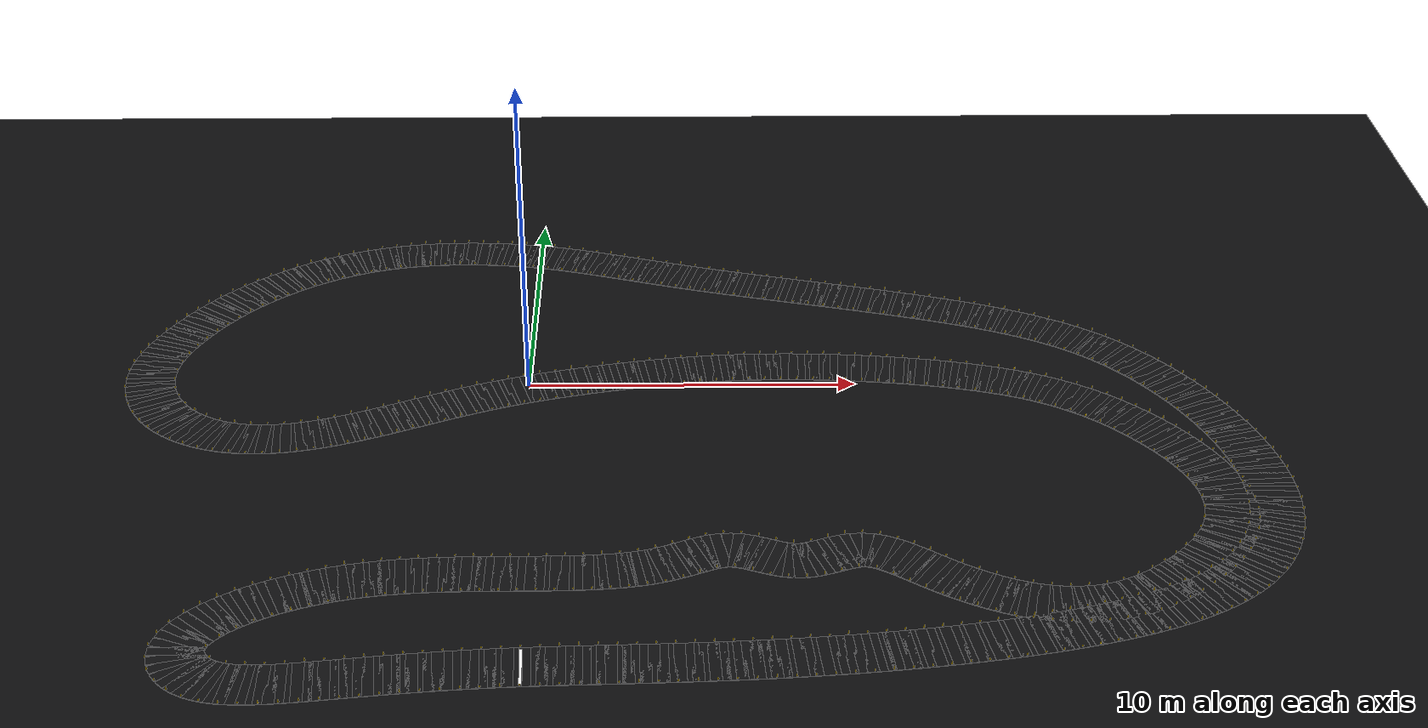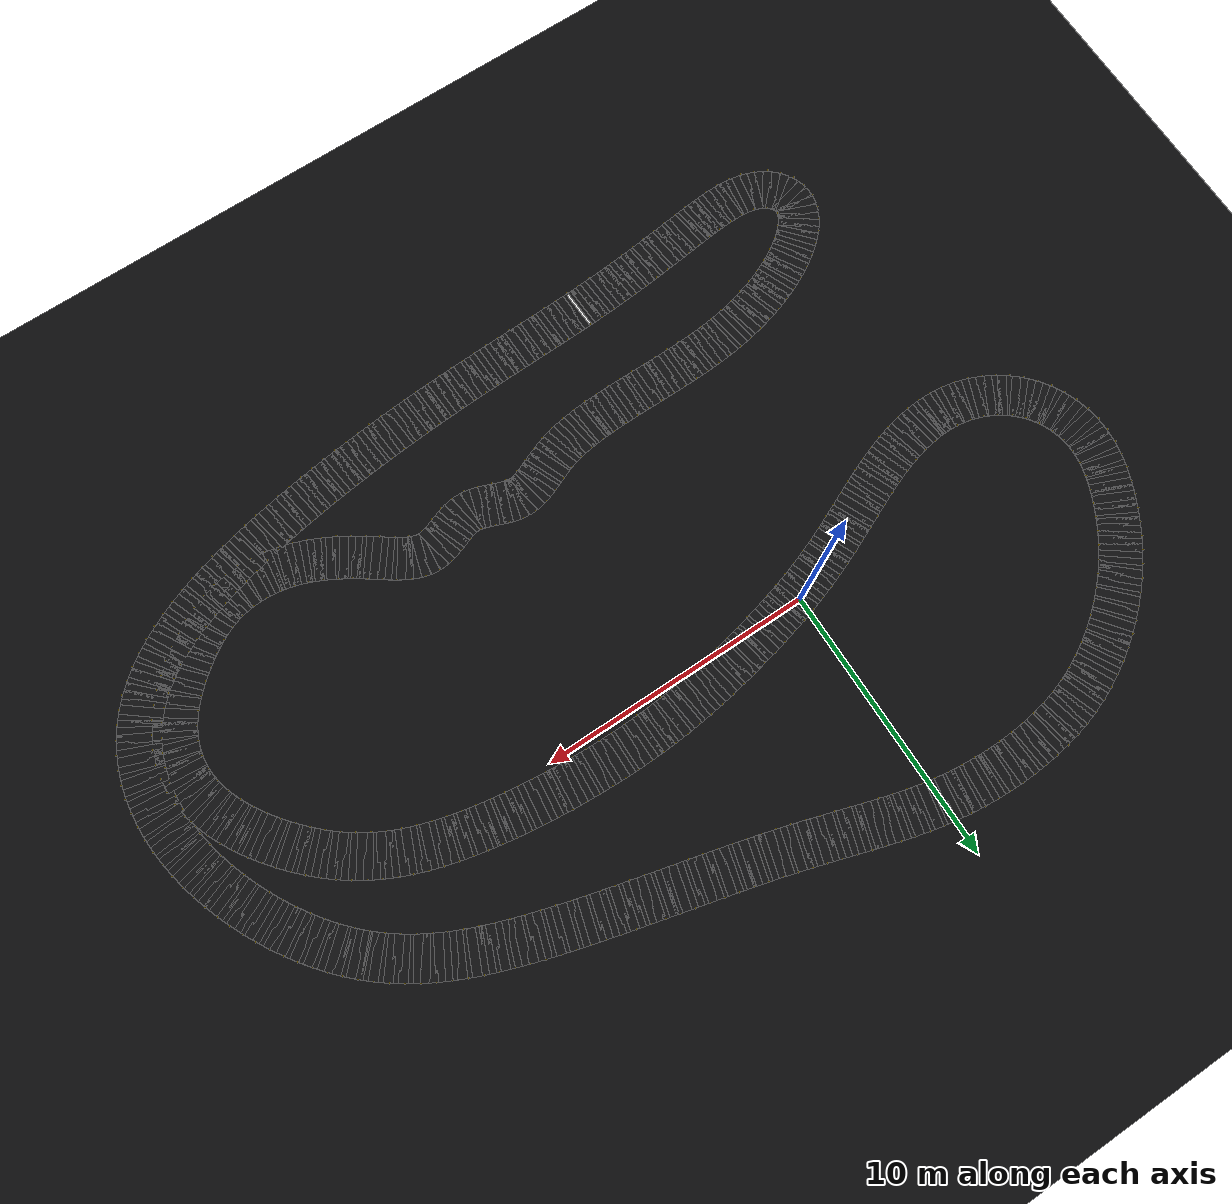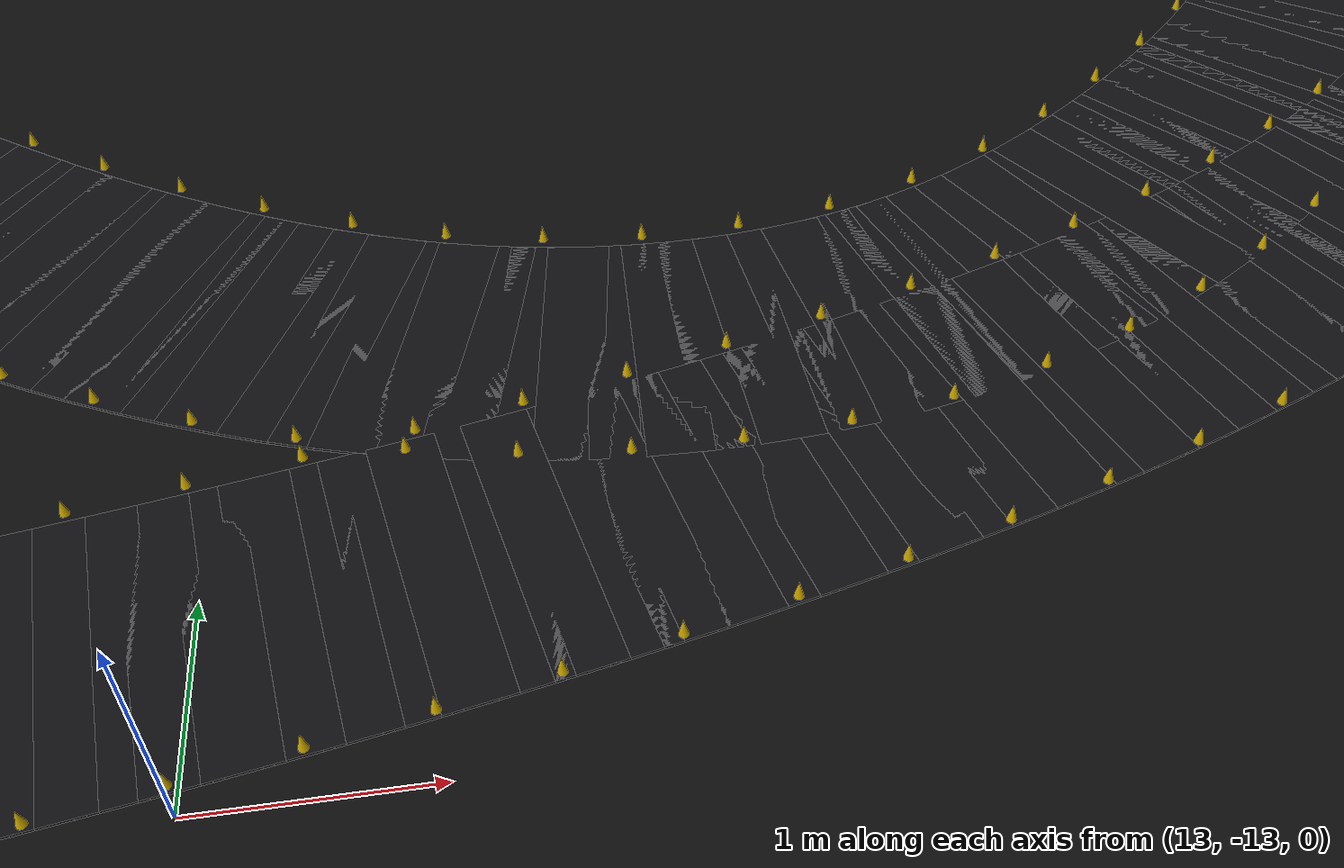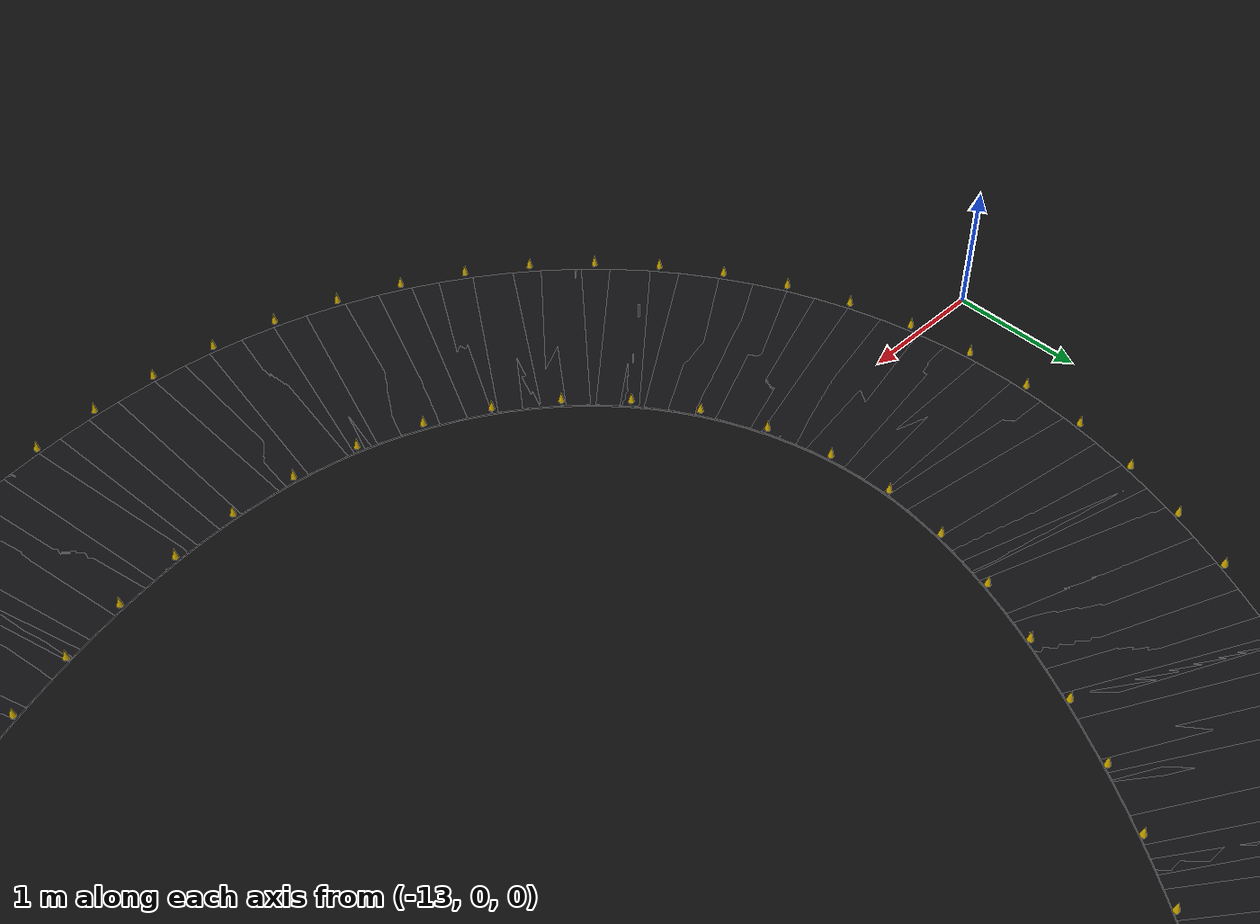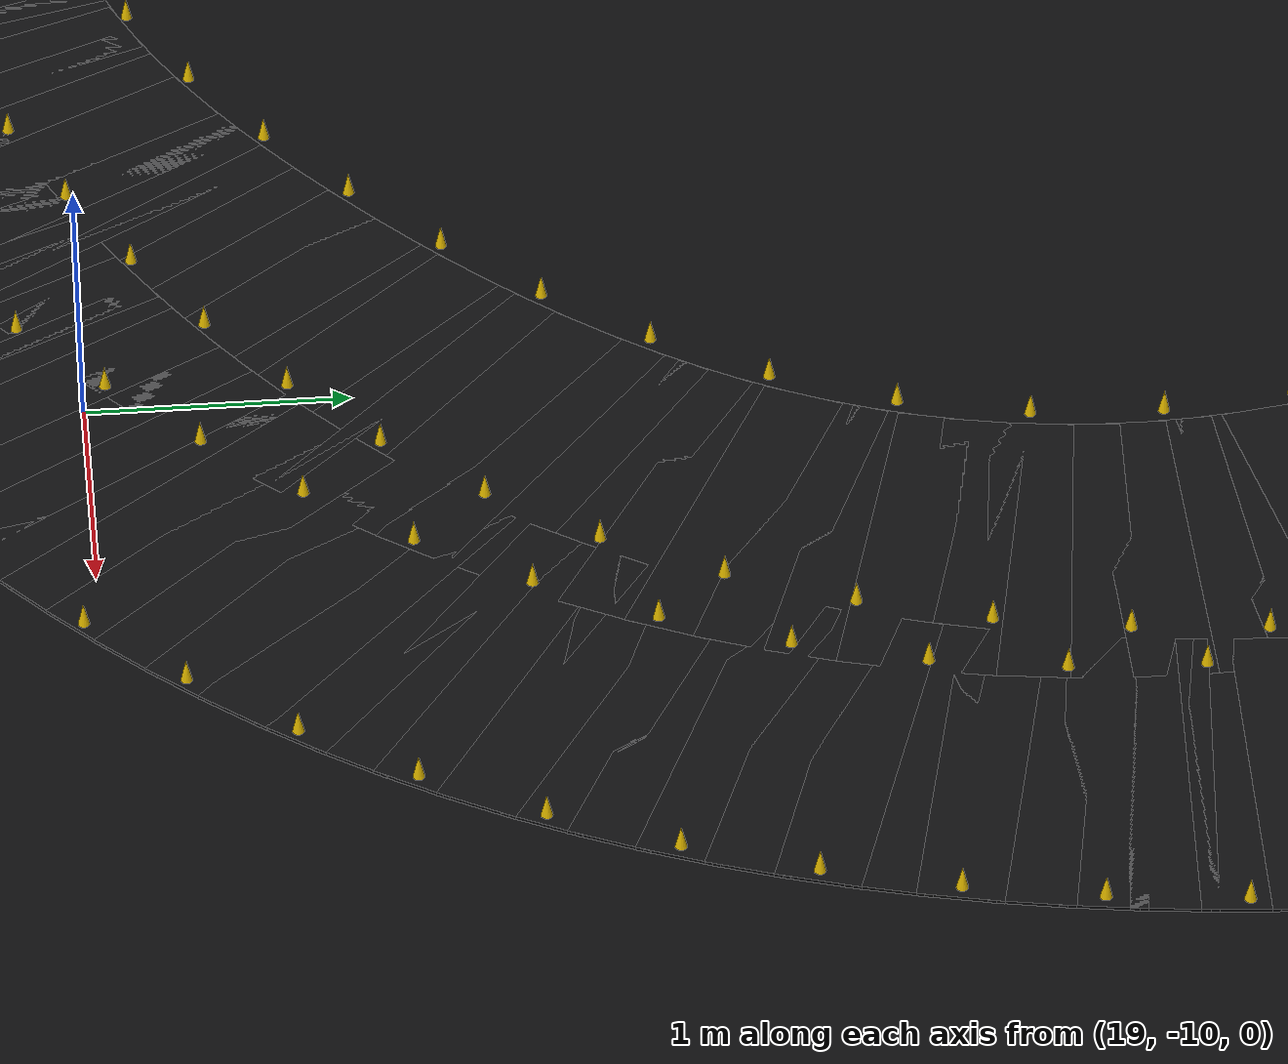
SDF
<?xml version='1.0'?>
<sdf version='1.10'>
  <world name='monaco'>
    <physics name='1ms' type='ignored'><max_step_size>0.001</max_step_size><real_time_factor>1.0</real_time_factor></physics>
    <plugin filename='gz-sim-physics-system' name='gz::sim::systems::Physics'/>
    <plugin filename='gz-sim-user-commands-system' name='gz::sim::systems::UserCommands'/>
    <plugin filename='gz-sim-scene-broadcaster-system' name='gz::sim::systems::SceneBroadcaster'/>
    <scene><ambient>0.42 0.42 0.44 1</ambient><background>0.055 0.055 0.060 1</background><shadows>true</shadows></scene>
    <light name='sun' type='directional'><pose>0 0 30 0 0 0</pose><diffuse>0.9 0.9 0.9 1</diffuse><specular>0.2 0.2 0.2 1</specular><direction>-0.4 0.2 -1</direction></light>
    <model name='ground'><static>true</static><link name='ground_link'>
      <collision name='ground_collision'><geometry><plane><normal>0 0 1</normal><size>160 160</size></plane></geometry></collision>
      <visual name='ground_visual'><geometry><plane><normal>0 0 1</normal><size>160 160</size></plane></geometry><material><ambient>0.045 0.045 0.050 1</ambient><diffuse>0.045 0.045 0.050 1</diffuse></material></visual>
    </link></model>
    <model name='road'><static>true</static><link name='road_link'>
      <visual name='road_0'><pose>0.60529 -13.09038 0.00600 0 -0.0000000 0.0447087</pose><geometry><box><size>0.31013 1.50000 0.01200</size></box></geometry><material><ambient>0.055 0.055 0.060 1</ambient><diffuse>0.055 0.055 0.060 1</diffuse><specular>0.04 0.04 0.04 1</specular></material></visual>
      <visual name='road_1'><pose>0.82522 -13.08094 0.00600 0 -0.0000000 0.0410628</pose><geometry><box><size>0.31013 1.50000 0.01200</size></box></geometry><material><ambient>0.055 0.055 0.060 1</ambient><diffuse>0.055 0.055 0.060 1</diffuse><specular>0.04 0.04 0.04 1</specular></material></visual>
      <visual name='road_2'><pose>1.04518 -13.07224 0.00600 0 -0.0000000 0.0379994</pose><geometry><box><size>0.31013 1.50000 0.01200</size></box></geometry><material><ambient>0.055 0.055 0.060 1</ambient><diffuse>0.055 0.055 0.060 1</diffuse><specular>0.04 0.04 0.04 1</specular></material></visual>
      <visual name='road_3'><pose>1.26516 -13.06416 0.00600 0 -0.0000000 0.0354540</pose><geometry><box><size>0.31013 1.50000 0.01200</size></box></geometry><material><ambient>0.055 0.055 0.060 1</ambient><diffuse>0.055 0.055 0.060 1</diffuse><specular>0.04 0.04 0.04 1</specular></material></visual>
      <visual name='road_4'><pose>1.48516 -13.05659 0.00600 0 -0.0000000 0.0332938</pose><geometry><box><size>0.31013 1.50000 0.01200</size></box></geometry><material><ambient>0.055 0.055 0.060 1</ambient><diffuse>0.055 0.055 0.060 1</diffuse><specular>0.04 0.04 0.04 1</specular></material></visual>
      <visual name='road_5'><pose>1.70518 -13.04945 0.00600 0 -0.0000000 0.0315829</pose><geometry><box><size>0.31013 1.50000 0.01200</size></box></geometry><material><ambient>0.055 0.055 0.060 1</ambient><diffuse>0.055 0.055 0.060 1</diffuse><specular>0.04 0.04 0.04 1</specular></material></visual>
      <visual name='road_6'><pose>1.92520 -13.04264 0.00600 0 -0.0000000 0.0303503</pose><geometry><box><size>0.31013 1.50000 0.01200</size></box></geometry><material><ambient>0.055 0.055 0.060 1</ambient><diffuse>0.055 0.055 0.060 1</diffuse><specular>0.04 0.04 0.04 1</specular></material></visual>
      <visual name='road_7'><pose>2.14524 -13.03606 0.00600 0 -0.0000000 0.0294200</pose><geometry><box><size>0.31013 1.50000 0.01200</size></box></geometry><material><ambient>0.055 0.055 0.060 1</ambient><diffuse>0.055 0.055 0.060 1</diffuse><specular>0.04 0.04 0.04 1</specular></material></visual>
      <visual name='road_8'><pose>2.36527 -13.02965 0.00600 0 -0.0000000 0.0288231</pose><geometry><box><size>0.31013 1.50000 0.01200</size></box></geometry><material><ambient>0.055 0.055 0.060 1</ambient><diffuse>0.055 0.055 0.060 1</diffuse><specular>0.04 0.04 0.04 1</specular></material></visual>
      <visual name='road_9'><pose>2.58532 -13.02334 0.00600 0 -0.0000000 0.0285670</pose><geometry><box><size>0.31013 1.50000 0.01200</size></box></geometry><material><ambient>0.055 0.055 0.060 1</ambient><diffuse>0.055 0.055 0.060 1</diffuse><specular>0.04 0.04 0.04 1</specular></material></visual>
      <visual name='road_10'><pose>2.80536 -13.01705 0.00600 0 -0.0000000 0.0285815</pose><geometry><box><size>0.31013 1.50000 0.01200</size></box></geometry><material><ambient>0.055 0.055 0.060 1</ambient><diffuse>0.055 0.055 0.060 1</diffuse><specular>0.04 0.04 0.04 1</specular></material></visual>
      <visual name='road_11'><pose>3.02540 -13.01072 0.00600 0 -0.0000000 0.0288691</pose><geometry><box><size>0.31013 1.50000 0.01200</size></box></geometry><material><ambient>0.055 0.055 0.060 1</ambient><diffuse>0.055 0.055 0.060 1</diffuse><specular>0.04 0.04 0.04 1</specular></material></visual>
      <visual name='road_12'><pose>3.24544 -13.00431 0.00600 0 -0.0000000 0.0293974</pose><geometry><box><size>0.31013 1.50000 0.01200</size></box></geometry><material><ambient>0.055 0.055 0.060 1</ambient><diffuse>0.055 0.055 0.060 1</diffuse><specular>0.04 0.04 0.04 1</specular></material></visual>
      <visual name='road_13'><pose>3.46547 -12.99775 0.00600 0 -0.0000000 0.0301929</pose><geometry><box><size>0.31013 1.50000 0.01200</size></box></geometry><material><ambient>0.055 0.055 0.060 1</ambient><diffuse>0.055 0.055 0.060 1</diffuse><specular>0.04 0.04 0.04 1</specular></material></visual>
      <visual name='road_14'><pose>3.68550 -12.99100 0.00600 0 -0.0000000 0.0311414</pose><geometry><box><size>0.31013 1.50000 0.01200</size></box></geometry><material><ambient>0.055 0.055 0.060 1</ambient><diffuse>0.055 0.055 0.060 1</diffuse><specular>0.04 0.04 0.04 1</specular></material></visual>
      <visual name='road_15'><pose>3.90552 -12.98401 0.00600 0 -0.0000000 0.0324016</pose><geometry><box><size>0.31013 1.50000 0.01200</size></box></geometry><material><ambient>0.055 0.055 0.060 1</ambient><diffuse>0.055 0.055 0.060 1</diffuse><specular>0.04 0.04 0.04 1</specular></material></visual>
      <visual name='road_16'><pose>4.12553 -12.97673 0.00600 0 -0.0000000 0.0337241</pose><geometry><box><size>0.31013 1.50000 0.01200</size></box></geometry><material><ambient>0.055 0.055 0.060 1</ambient><diffuse>0.055 0.055 0.060 1</diffuse><specular>0.04 0.04 0.04 1</specular></material></visual>
      <visual name='road_17'><pose>4.34553 -12.96913 0.00600 0 -0.0000000 0.0353773</pose><geometry><box><size>0.31013 1.50000 0.01200</size></box></geometry><material><ambient>0.055 0.055 0.060 1</ambient><diffuse>0.055 0.055 0.060 1</diffuse><specular>0.04 0.04 0.04 1</specular></material></visual>
      <visual name='road_18'><pose>4.56552 -12.96116 0.00600 0 -0.0000000 0.0370678</pose><geometry><box><size>0.31013 1.50000 0.01200</size></box></geometry><material><ambient>0.055 0.055 0.060 1</ambient><diffuse>0.055 0.055 0.060 1</diffuse><specular>0.04 0.04 0.04 1</specular></material></visual>
      <visual name='road_19'><pose>4.78549 -12.95279 0.00600 0 -0.0000000 0.0390180</pose><geometry><box><size>0.31013 1.50000 0.01200</size></box></geometry><material><ambient>0.055 0.055 0.060 1</ambient><diffuse>0.055 0.055 0.060 1</diffuse><specular>0.04 0.04 0.04 1</specular></material></visual>
      <visual name='road_20'><pose>5.00545 -12.94397 0.00600 0 -0.0000000 0.0411051</pose><geometry><box><size>0.31013 1.50000 0.01200</size></box></geometry><material><ambient>0.055 0.055 0.060 1</ambient><diffuse>0.055 0.055 0.060 1</diffuse><specular>0.04 0.04 0.04 1</specular></material></visual>
      <visual name='road_21'><pose>5.22538 -12.93469 0.00600 0 -0.0000000 0.0432344</pose><geometry><box><size>0.31013 1.50000 0.01200</size></box></geometry><material><ambient>0.055 0.055 0.060 1</ambient><diffuse>0.055 0.055 0.060 1</diffuse><specular>0.04 0.04 0.04 1</specular></material></visual>
      <visual name='road_22'><pose>5.44530 -12.92490 0.00600 0 -0.0000000 0.0457769</pose><geometry><box><size>0.31013 1.50000 0.01200</size></box></geometry><material><ambient>0.055 0.055 0.060 1</ambient><diffuse>0.055 0.055 0.060 1</diffuse><specular>0.04 0.04 0.04 1</specular></material></visual>
      <visual name='road_23'><pose>5.66519 -12.91457 0.00600 0 -0.0000000 0.0480723</pose><geometry><box><size>0.31013 1.50000 0.01200</size></box></geometry><material><ambient>0.055 0.055 0.060 1</ambient><diffuse>0.055 0.055 0.060 1</diffuse><specular>0.04 0.04 0.04 1</specular></material></visual>
      <visual name='road_24'><pose>5.88505 -12.90368 0.00600 0 -0.0000000 0.0509069</pose><geometry><box><size>0.31013 1.50000 0.01200</size></box></geometry><material><ambient>0.055 0.055 0.060 1</ambient><diffuse>0.055 0.055 0.060 1</diffuse><specular>0.04 0.04 0.04 1</specular></material></visual>
      <visual name='road_25'><pose>6.10488 -12.89218 0.00600 0 -0.0000000 0.0535856</pose><geometry><box><size>0.31013 1.50000 0.01200</size></box></geometry><material><ambient>0.055 0.055 0.060 1</ambient><diffuse>0.055 0.055 0.060 1</diffuse><specular>0.04 0.04 0.04 1</specular></material></visual>
      <visual name='road_26'><pose>6.32468 -12.88009 0.00600 0 -0.0000000 0.0563261</pose><geometry><box><size>0.31013 1.50000 0.01200</size></box></geometry><material><ambient>0.055 0.055 0.060 1</ambient><diffuse>0.055 0.055 0.060 1</diffuse><specular>0.04 0.04 0.04 1</specular></material></visual>
      <visual name='road_27'><pose>6.54444 -12.86734 0.00600 0 -0.0000000 0.0596184</pose><geometry><box><size>0.31013 1.50000 0.01200</size></box></geometry><material><ambient>0.055 0.055 0.060 1</ambient><diffuse>0.055 0.055 0.060 1</diffuse><specular>0.04 0.04 0.04 1</specular></material></visual>
      <visual name='road_28'><pose>6.76416 -12.85390 0.00600 0 -0.0000000 0.0625165</pose><geometry><box><size>0.31013 1.50000 0.01200</size></box></geometry><material><ambient>0.055 0.055 0.060 1</ambient><diffuse>0.055 0.055 0.060 1</diffuse><specular>0.04 0.04 0.04 1</specular></material></visual>
      <visual name='road_29'><pose>6.98384 -12.83980 0.00600 0 -0.0000000 0.0657030</pose><geometry><box><size>0.31013 1.50000 0.01200</size></box></geometry><material><ambient>0.055 0.055 0.060 1</ambient><diffuse>0.055 0.055 0.060 1</diffuse><specular>0.04 0.04 0.04 1</specular></material></visual>
      <visual name='road_30'><pose>7.20347 -12.82496 0.00600 0 -0.0000000 0.0692518</pose><geometry><box><size>0.31013 1.50000 0.01200</size></box></geometry><material><ambient>0.055 0.055 0.060 1</ambient><diffuse>0.055 0.055 0.060 1</diffuse><specular>0.04 0.04 0.04 1</specular></material></visual>
      <visual name='road_31'><pose>7.42305 -12.80937 0.00600 0 -0.0000000 0.0724658</pose><geometry><box><size>0.31013 1.50000 0.01200</size></box></geometry><material><ambient>0.055 0.055 0.060 1</ambient><diffuse>0.055 0.055 0.060 1</diffuse><specular>0.04 0.04 0.04 1</specular></material></visual>
      <visual name='road_32'><pose>7.64258 -12.79305 0.00600 0 -0.0000000 0.0759315</pose><geometry><box><size>0.31013 1.50000 0.01200</size></box></geometry><material><ambient>0.055 0.055 0.060 1</ambient><diffuse>0.055 0.055 0.060 1</diffuse><specular>0.04 0.04 0.04 1</specular></material></visual>
      <visual name='road_33'><pose>7.86204 -12.77593 0.00600 0 -0.0000000 0.0798112</pose><geometry><box><size>0.31013 1.50000 0.01200</size></box></geometry><material><ambient>0.055 0.055 0.060 1</ambient><diffuse>0.055 0.055 0.060 1</diffuse><specular>0.04 0.04 0.04 1</specular></material></visual>
      <visual name='road_34'><pose>8.08144 -12.75801 0.00600 0 -0.0000000 0.0832174</pose><geometry><box><size>0.31013 1.50000 0.01200</size></box></geometry><material><ambient>0.055 0.055 0.060 1</ambient><diffuse>0.055 0.055 0.060 1</diffuse><specular>0.04 0.04 0.04 1</specular></material></visual>
      <visual name='road_35'><pose>8.30078 -12.73933 0.00600 0 -0.0000000 0.0866328</pose><geometry><box><size>0.31013 1.50000 0.01200</size></box></geometry><material><ambient>0.055 0.055 0.060 1</ambient><diffuse>0.055 0.055 0.060 1</diffuse><specular>0.04 0.04 0.04 1</specular></material></visual>
      <visual name='road_36'><pose>8.52005 -12.71985 0.00600 0 -0.0000000 0.0906531</pose><geometry><box><size>0.31013 1.50000 0.01200</size></box></geometry><material><ambient>0.055 0.055 0.060 1</ambient><diffuse>0.055 0.055 0.060 1</diffuse><specular>0.04 0.04 0.04 1</specular></material></visual>
      <visual name='road_37'><pose>8.73924 -12.69954 0.00600 0 -0.0000000 0.0941429</pose><geometry><box><size>0.31013 1.50000 0.01200</size></box></geometry><material><ambient>0.055 0.055 0.060 1</ambient><diffuse>0.055 0.055 0.060 1</diffuse><specular>0.04 0.04 0.04 1</specular></material></visual>
      <visual name='road_38'><pose>8.95836 -12.67846 0.00600 0 -0.0000000 0.0976165</pose><geometry><box><size>0.31013 1.50000 0.01200</size></box></geometry><material><ambient>0.055 0.055 0.060 1</ambient><diffuse>0.055 0.055 0.060 1</diffuse><specular>0.04 0.04 0.04 1</specular></material></visual>
      <visual name='road_39'><pose>9.17740 -12.65660 0.00600 0 -0.0000000 0.1013720</pose><geometry><box><size>0.31013 1.50000 0.01200</size></box></geometry><material><ambient>0.055 0.055 0.060 1</ambient><diffuse>0.055 0.055 0.060 1</diffuse><specular>0.04 0.04 0.04 1</specular></material></visual>
      <visual name='road_40'><pose>9.39636 -12.63389 0.00600 0 -0.0000000 0.1052892</pose><geometry><box><size>0.31013 1.50000 0.01200</size></box></geometry><material><ambient>0.055 0.055 0.060 1</ambient><diffuse>0.055 0.055 0.060 1</diffuse><specular>0.04 0.04 0.04 1</specular></material></visual>
      <visual name='road_41'><pose>9.61523 -12.61036 0.00600 0 -0.0000000 0.1088731</pose><geometry><box><size>0.31013 1.50000 0.01200</size></box></geometry><material><ambient>0.055 0.055 0.060 1</ambient><diffuse>0.055 0.055 0.060 1</diffuse><specular>0.04 0.04 0.04 1</specular></material></visual>
      <visual name='road_42'><pose>9.83402 -12.58605 0.00600 0 -0.0000000 0.1125015</pose><geometry><box><size>0.31013 1.50000 0.01200</size></box></geometry><material><ambient>0.055 0.055 0.060 1</ambient><diffuse>0.055 0.055 0.060 1</diffuse><specular>0.04 0.04 0.04 1</specular></material></visual>
      <visual name='road_43'><pose>10.05270 -12.56088 0.00600 0 -0.0000000 0.1166448</pose><geometry><box><size>0.31013 1.50000 0.01200</size></box></geometry><material><ambient>0.055 0.055 0.060 1</ambient><diffuse>0.055 0.055 0.060 1</diffuse><specular>0.04 0.04 0.04 1</specular></material></visual>
      <visual name='road_44'><pose>10.27129 -12.53483 0.00600 0 -0.0000000 0.1205758</pose><geometry><box><size>0.31013 1.50000 0.01200</size></box></geometry><material><ambient>0.055 0.055 0.060 1</ambient><diffuse>0.055 0.055 0.060 1</diffuse><specular>0.04 0.04 0.04 1</specular></material></visual>
      <visual name='road_45'><pose>10.48977 -12.50794 0.00600 0 -0.0000000 0.1243851</pose><geometry><box><size>0.31013 1.50000 0.01200</size></box></geometry><material><ambient>0.055 0.055 0.060 1</ambient><diffuse>0.055 0.055 0.060 1</diffuse><specular>0.04 0.04 0.04 1</specular></material></visual>
      <visual name='road_46'><pose>10.70815 -12.48020 0.00600 0 -0.0000000 0.1282607</pose><geometry><box><size>0.31013 1.50000 0.01200</size></box></geometry><material><ambient>0.055 0.055 0.060 1</ambient><diffuse>0.055 0.055 0.060 1</diffuse><specular>0.04 0.04 0.04 1</specular></material></visual>
      <visual name='road_47'><pose>10.92641 -12.45154 0.00600 0 -0.0000000 0.1328935</pose><geometry><box><size>0.31013 1.50000 0.01200</size></box></geometry><material><ambient>0.055 0.055 0.060 1</ambient><diffuse>0.055 0.055 0.060 1</diffuse><specular>0.04 0.04 0.04 1</specular></material></visual>
      <visual name='road_48'><pose>11.14454 -12.42193 0.00600 0 -0.0000000 0.1369623</pose><geometry><box><size>0.31013 1.50000 0.01200</size></box></geometry><material><ambient>0.055 0.055 0.060 1</ambient><diffuse>0.055 0.055 0.060 1</diffuse><specular>0.04 0.04 0.04 1</specular></material></visual>
      <visual name='road_49'><pose>11.36254 -12.39142 0.00600 0 -0.0000000 0.1410995</pose><geometry><box><size>0.31013 1.50000 0.01200</size></box></geometry><material><ambient>0.055 0.055 0.060 1</ambient><diffuse>0.055 0.055 0.060 1</diffuse><specular>0.04 0.04 0.04 1</specular></material></visual>
      <visual name='road_50'><pose>11.58042 -12.35998 0.00600 0 -0.0000000 0.1455538</pose><geometry><box><size>0.31013 1.50000 0.01200</size></box></geometry><material><ambient>0.055 0.055 0.060 1</ambient><diffuse>0.055 0.055 0.060 1</diffuse><specular>0.04 0.04 0.04 1</specular></material></visual>
      <visual name='road_51'><pose>11.79814 -12.32752 0.00600 0 -0.0000000 0.1504537</pose><geometry><box><size>0.31013 1.50000 0.01200</size></box></geometry><material><ambient>0.055 0.055 0.060 1</ambient><diffuse>0.055 0.055 0.060 1</diffuse><specular>0.04 0.04 0.04 1</specular></material></visual>
      <visual name='road_52'><pose>12.01571 -12.29404 0.00600 0 -0.0000000 0.1549268</pose><geometry><box><size>0.31013 1.50000 0.01200</size></box></geometry><material><ambient>0.055 0.055 0.060 1</ambient><diffuse>0.055 0.055 0.060 1</diffuse><specular>0.04 0.04 0.04 1</specular></material></visual>
      <visual name='road_53'><pose>12.23313 -12.25957 0.00600 0 -0.0000000 0.1595165</pose><geometry><box><size>0.31013 1.50000 0.01200</size></box></geometry><material><ambient>0.055 0.055 0.060 1</ambient><diffuse>0.055 0.055 0.060 1</diffuse><specular>0.04 0.04 0.04 1</specular></material></visual>
      <visual name='road_54'><pose>12.45037 -12.22402 0.00600 0 -0.0000000 0.1649153</pose><geometry><box><size>0.31013 1.50000 0.01200</size></box></geometry><material><ambient>0.055 0.055 0.060 1</ambient><diffuse>0.055 0.055 0.060 1</diffuse><specular>0.04 0.04 0.04 1</specular></material></visual>
      <visual name='road_55'><pose>12.66742 -12.18733 0.00600 0 -0.0000000 0.1700215</pose><geometry><box><size>0.31013 1.50000 0.01200</size></box></geometry><material><ambient>0.055 0.055 0.060 1</ambient><diffuse>0.055 0.055 0.060 1</diffuse><specular>0.04 0.04 0.04 1</specular></material></visual>
      <visual name='road_56'><pose>12.88428 -12.14953 0.00600 0 -0.0000000 0.1750669</pose><geometry><box><size>0.31013 1.50000 0.01200</size></box></geometry><material><ambient>0.055 0.055 0.060 1</ambient><diffuse>0.055 0.055 0.060 1</diffuse><specular>0.04 0.04 0.04 1</specular></material></visual>
      <visual name='road_57'><pose>13.10094 -12.11058 0.00600 0 -0.0000000 0.1807451</pose><geometry><box><size>0.31013 1.50000 0.01200</size></box></geometry><material><ambient>0.055 0.055 0.060 1</ambient><diffuse>0.055 0.055 0.060 1</diffuse><specular>0.04 0.04 0.04 1</specular></material></visual>
      <visual name='road_58'><pose>13.31736 -12.07036 0.00600 0 -0.0000000 0.1867302</pose><geometry><box><size>0.31013 1.50000 0.01200</size></box></geometry><material><ambient>0.055 0.055 0.060 1</ambient><diffuse>0.055 0.055 0.060 1</diffuse><specular>0.04 0.04 0.04 1</specular></material></visual>
      <visual name='road_59'><pose>13.53355 -12.02888 0.00600 0 -0.0000000 0.1923509</pose><geometry><box><size>0.31013 1.50000 0.01200</size></box></geometry><material><ambient>0.055 0.055 0.060 1</ambient><diffuse>0.055 0.055 0.060 1</diffuse><specular>0.04 0.04 0.04 1</specular></material></visual>
      <visual name='road_60'><pose>13.74949 -11.98612 0.00600 0 -0.0000000 0.1986722</pose><geometry><box><size>0.31013 1.50000 0.01200</size></box></geometry><material><ambient>0.055 0.055 0.060 1</ambient><diffuse>0.055 0.055 0.060 1</diffuse><specular>0.04 0.04 0.04 1</specular></material></visual>
      <visual name='road_61'><pose>13.96514 -11.94193 0.00600 0 -0.0000000 0.2054943</pose><geometry><box><size>0.31013 1.50000 0.01200</size></box></geometry><material><ambient>0.055 0.055 0.060 1</ambient><diffuse>0.055 0.055 0.060 1</diffuse><specular>0.04 0.04 0.04 1</specular></material></visual>
      <visual name='road_62'><pose>14.18049 -11.89633 0.00600 0 -0.0000000 0.2118438</pose><geometry><box><size>0.31013 1.50000 0.01200</size></box></geometry><material><ambient>0.055 0.055 0.060 1</ambient><diffuse>0.055 0.055 0.060 1</diffuse><specular>0.04 0.04 0.04 1</specular></material></visual>
      <visual name='road_63'><pose>14.39553 -11.84924 0.00600 0 -0.0000000 0.2193683</pose><geometry><box><size>0.31013 1.50000 0.01200</size></box></geometry><material><ambient>0.055 0.055 0.060 1</ambient><diffuse>0.055 0.055 0.060 1</diffuse><specular>0.04 0.04 0.04 1</specular></material></visual>
      <visual name='road_64'><pose>14.61020 -11.80053 0.00600 0 -0.0000000 0.2268897</pose><geometry><box><size>0.31013 1.50000 0.01200</size></box></geometry><material><ambient>0.055 0.055 0.060 1</ambient><diffuse>0.055 0.055 0.060 1</diffuse><specular>0.04 0.04 0.04 1</specular></material></visual>
      <visual name='road_65'><pose>14.82450 -11.75021 0.00600 0 -0.0000000 0.2343302</pose><geometry><box><size>0.31013 1.50000 0.01200</size></box></geometry><material><ambient>0.055 0.055 0.060 1</ambient><diffuse>0.055 0.055 0.060 1</diffuse><specular>0.04 0.04 0.04 1</specular></material></visual>
      <visual name='road_66'><pose>15.03837 -11.69811 0.00600 0 -0.0000000 0.2435857</pose><geometry><box><size>0.31013 1.50000 0.01200</size></box></geometry><material><ambient>0.055 0.055 0.060 1</ambient><diffuse>0.055 0.055 0.060 1</diffuse><specular>0.04 0.04 0.04 1</specular></material></visual>
      <visual name='road_67'><pose>15.25179 -11.64415 0.00600 0 -0.0000000 0.2516825</pose><geometry><box><size>0.31013 1.50000 0.01200</size></box></geometry><material><ambient>0.055 0.055 0.060 1</ambient><diffuse>0.055 0.055 0.060 1</diffuse><specular>0.04 0.04 0.04 1</specular></material></visual>
      <visual name='road_68'><pose>15.46470 -11.58825 0.00600 0 -0.0000000 0.2618682</pose><geometry><box><size>0.31013 1.50000 0.01200</size></box></geometry><material><ambient>0.055 0.055 0.060 1</ambient><diffuse>0.055 0.055 0.060 1</diffuse><specular>0.04 0.04 0.04 1</specular></material></visual>
      <visual name='road_69'><pose>15.67705 -11.53025 0.00600 0 -0.0000000 0.2713681</pose><geometry><box><size>0.31013 1.50000 0.01200</size></box></geometry><material><ambient>0.055 0.055 0.060 1</ambient><diffuse>0.055 0.055 0.060 1</diffuse><specular>0.04 0.04 0.04 1</specular></material></visual>
      <visual name='road_70'><pose>15.88878 -11.47004 0.00600 0 -0.0000000 0.2827322</pose><geometry><box><size>0.31013 1.50000 0.01200</size></box></geometry><material><ambient>0.055 0.055 0.060 1</ambient><diffuse>0.055 0.055 0.060 1</diffuse><specular>0.04 0.04 0.04 1</specular></material></visual>
      <visual name='road_71'><pose>16.09983 -11.40748 0.00600 0 -0.0000000 0.2936581</pose><geometry><box><size>0.31013 1.50000 0.01200</size></box></geometry><material><ambient>0.055 0.055 0.060 1</ambient><diffuse>0.055 0.055 0.060 1</diffuse><specular>0.04 0.04 0.04 1</specular></material></visual>
      <visual name='road_72'><pose>16.31011 -11.34239 0.00600 0 -0.0000000 0.3067416</pose><geometry><box><size>0.31013 1.50000 0.01200</size></box></geometry><material><ambient>0.055 0.055 0.060 1</ambient><diffuse>0.055 0.055 0.060 1</diffuse><specular>0.04 0.04 0.04 1</specular></material></visual>
      <visual name='road_73'><pose>16.51956 -11.27465 0.00600 0 -0.0000000 0.3188557</pose><geometry><box><size>0.31013 1.50000 0.01200</size></box></geometry><material><ambient>0.055 0.055 0.060 1</ambient><diffuse>0.055 0.055 0.060 1</diffuse><specular>0.04 0.04 0.04 1</specular></material></visual>
      <visual name='road_74'><pose>16.72807 -11.20409 0.00600 0 -0.0000000 0.3337107</pose><geometry><box><size>0.31013 1.50000 0.01200</size></box></geometry><material><ambient>0.055 0.055 0.060 1</ambient><diffuse>0.055 0.055 0.060 1</diffuse><specular>0.04 0.04 0.04 1</specular></material></visual>
      <visual name='road_75'><pose>16.93553 -11.13050 0.00600 0 -0.0000000 0.3480278</pose><geometry><box><size>0.31013 1.50000 0.01200</size></box></geometry><material><ambient>0.055 0.055 0.060 1</ambient><diffuse>0.055 0.055 0.060 1</diffuse><specular>0.04 0.04 0.04 1</specular></material></visual>
      <visual name='road_76'><pose>17.14188 -11.05387 0.00600 0 -0.0000000 0.3631164</pose><geometry><box><size>0.31013 1.50000 0.01200</size></box></geometry><material><ambient>0.055 0.055 0.060 1</ambient><diffuse>0.055 0.055 0.060 1</diffuse><specular>0.04 0.04 0.04 1</specular></material></visual>
      <visual name='road_77'><pose>17.34694 -10.97384 0.00600 0 -0.0000000 0.3810765</pose><geometry><box><size>0.31013 1.50000 0.01200</size></box></geometry><material><ambient>0.055 0.055 0.060 1</ambient><diffuse>0.055 0.055 0.060 1</diffuse><specular>0.04 0.04 0.04 1</specular></material></visual>
      <visual name='road_78'><pose>17.55054 -10.89020 0.00600 0 -0.0000000 0.3984837</pose><geometry><box><size>0.31013 1.50000 0.01200</size></box></geometry><material><ambient>0.055 0.055 0.060 1</ambient><diffuse>0.055 0.055 0.060 1</diffuse><specular>0.04 0.04 0.04 1</specular></material></visual>
      <visual name='road_79'><pose>17.75261 -10.80290 0.00600 0 -0.0000000 0.4171829</pose><geometry><box><size>0.31013 1.50000 0.01200</size></box></geometry><material><ambient>0.055 0.055 0.060 1</ambient><diffuse>0.055 0.055 0.060 1</diffuse><specular>0.04 0.04 0.04 1</specular></material></visual>
      <visual name='road_80'><pose>17.95294 -10.71169 0.00600 0 -0.0000000 0.4372795</pose><geometry><box><size>0.31013 1.50000 0.01200</size></box></geometry><material><ambient>0.055 0.055 0.060 1</ambient><diffuse>0.055 0.055 0.060 1</diffuse><specular>0.04 0.04 0.04 1</specular></material></visual>
      <visual name='road_81'><pose>18.15129 -10.61627 0.00600 0 -0.0000000 0.4595087</pose><geometry><box><size>0.31013 1.50000 0.01200</size></box></geometry><material><ambient>0.055 0.055 0.060 1</ambient><diffuse>0.055 0.055 0.060 1</diffuse><specular>0.04 0.04 0.04 1</specular></material></visual>
      <visual name='road_82'><pose>18.34742 -10.51636 0.00600 0 -0.0000000 0.4828034</pose><geometry><box><size>0.31013 1.50000 0.01200</size></box></geometry><material><ambient>0.055 0.055 0.060 1</ambient><diffuse>0.055 0.055 0.060 1</diffuse><specular>0.04 0.04 0.04 1</specular></material></visual>
      <visual name='road_83'><pose>18.54110 -10.41178 0.00600 0 -0.0000000 0.5073852</pose><geometry><box><size>0.31012 1.50000 0.01200</size></box></geometry><material><ambient>0.055 0.055 0.060 1</ambient><diffuse>0.055 0.055 0.060 1</diffuse><specular>0.04 0.04 0.04 1</specular></material></visual>
      <visual name='road_84'><pose>18.73206 -10.30231 0.00600 0 -0.0000000 0.5336650</pose><geometry><box><size>0.31012 1.50000 0.01200</size></box></geometry><material><ambient>0.055 0.055 0.060 1</ambient><diffuse>0.055 0.055 0.060 1</diffuse><specular>0.04 0.04 0.04 1</specular></material></visual>
      <visual name='road_85'><pose>18.91996 -10.18771 0.00600 0 -0.0000000 0.5617050</pose><geometry><box><size>0.31012 1.50000 0.01200</size></box></geometry><material><ambient>0.055 0.055 0.060 1</ambient><diffuse>0.055 0.055 0.060 1</diffuse><specular>0.04 0.04 0.04 1</specular></material></visual>
      <visual name='road_86'><pose>19.10447 -10.06771 0.00600 0 -0.0000000 0.5915533</pose><geometry><box><size>0.31012 1.50000 0.01200</size></box></geometry><material><ambient>0.055 0.055 0.060 1</ambient><diffuse>0.055 0.055 0.060 1</diffuse><specular>0.04 0.04 0.04 1</specular></material></visual>
      <visual name='road_87'><pose>19.28520 -9.94210 0.00600 0 -0.0000000 0.6232395</pose><geometry><box><size>0.31012 1.50000 0.01200</size></box></geometry><material><ambient>0.055 0.055 0.060 1</ambient><diffuse>0.055 0.055 0.060 1</diffuse><specular>0.04 0.04 0.04 1</specular></material></visual>
      <visual name='road_88'><pose>19.46173 -9.81066 0.00600 0 -0.0000000 0.6567705</pose><geometry><box><size>0.31012 1.50000 0.01200</size></box></geometry><material><ambient>0.055 0.055 0.060 1</ambient><diffuse>0.055 0.055 0.060 1</diffuse><specular>0.04 0.04 0.04 1</specular></material></visual>
      <visual name='road_89'><pose>19.63359 -9.67318 0.00600 0 -0.0000000 0.6926261</pose><geometry><box><size>0.31012 1.50000 0.01200</size></box></geometry><material><ambient>0.055 0.055 0.060 1</ambient><diffuse>0.055 0.055 0.060 1</diffuse><specular>0.04 0.04 0.04 1</specular></material></visual>
      <visual name='road_90'><pose>19.80025 -9.52944 0.00600 0 -0.0000000 0.7307613</pose><geometry><box><size>0.31012 1.50000 0.01200</size></box></geometry><material><ambient>0.055 0.055 0.060 1</ambient><diffuse>0.055 0.055 0.060 1</diffuse><specular>0.04 0.04 0.04 1</specular></material></visual>
      <visual name='road_91'><pose>19.96122 -9.37938 0.00600 0 -0.0000000 0.7698797</pose><geometry><box><size>0.31011 1.50000 0.01200</size></box></geometry><material><ambient>0.055 0.055 0.060 1</ambient><diffuse>0.055 0.055 0.060 1</diffuse><specular>0.04 0.04 0.04 1</specular></material></visual>
      <visual name='road_92'><pose>20.11608 -9.22302 0.00600 0 -0.0000000 0.8105407</pose><geometry><box><size>0.31011 1.50000 0.01200</size></box></geometry><material><ambient>0.055 0.055 0.060 1</ambient><diffuse>0.055 0.055 0.060 1</diffuse><specular>0.04 0.04 0.04 1</specular></material></visual>
      <visual name='road_93'><pose>20.26434 -9.06040 0.00600 0 -0.0000000 0.8525749</pose><geometry><box><size>0.31011 1.50000 0.01200</size></box></geometry><material><ambient>0.055 0.055 0.060 1</ambient><diffuse>0.055 0.055 0.060 1</diffuse><specular>0.04 0.04 0.04 1</specular></material></visual>
      <visual name='road_94'><pose>20.40535 -8.89146 0.00600 0 -0.0000000 0.8979987</pose><geometry><box><size>0.31011 1.50000 0.01200</size></box></geometry><material><ambient>0.055 0.055 0.060 1</ambient><diffuse>0.055 0.055 0.060 1</diffuse><specular>0.04 0.04 0.04 1</specular></material></visual>
      <visual name='road_95'><pose>20.53862 -8.71635 0.00600 0 -0.0000000 0.9424956</pose><geometry><box><size>0.31011 1.50000 0.01200</size></box></geometry><material><ambient>0.055 0.055 0.060 1</ambient><diffuse>0.055 0.055 0.060 1</diffuse><specular>0.04 0.04 0.04 1</specular></material></visual>
      <visual name='road_96'><pose>20.66394 -8.53546 0.00600 0 -0.0000000 0.9873636</pose><geometry><box><size>0.31011 1.50000 0.01200</size></box></geometry><material><ambient>0.055 0.055 0.060 1</ambient><diffuse>0.055 0.055 0.060 1</diffuse><specular>0.04 0.04 0.04 1</specular></material></visual>
      <visual name='road_97'><pose>20.78085 -8.34904 0.00600 0 -0.0000000 1.0339353</pose><geometry><box><size>0.31011 1.50000 0.01200</size></box></geometry><material><ambient>0.055 0.055 0.060 1</ambient><diffuse>0.055 0.055 0.060 1</diffuse><specular>0.04 0.04 0.04 1</specular></material></visual>
      <visual name='road_98'><pose>20.88903 -8.15742 0.00600 0 -0.0000000 1.0797593</pose><geometry><box><size>0.31011 1.50000 0.01200</size></box></geometry><material><ambient>0.055 0.055 0.060 1</ambient><diffuse>0.055 0.055 0.060 1</diffuse><specular>0.04 0.04 0.04 1</specular></material></visual>
      <visual name='road_99'><pose>20.98848 -7.96112 0.00600 0 -0.0000000 1.1239845</pose><geometry><box><size>0.31011 1.50000 0.01200</size></box></geometry><material><ambient>0.055 0.055 0.060 1</ambient><diffuse>0.055 0.055 0.060 1</diffuse><specular>0.04 0.04 0.04 1</specular></material></visual>
      <visual name='road_100'><pose>21.07913 -7.76060 0.00600 0 -0.0000000 1.1684437</pose><geometry><box><size>0.31011 1.50000 0.01200</size></box></geometry><material><ambient>0.055 0.055 0.060 1</ambient><diffuse>0.055 0.055 0.060 1</diffuse><specular>0.04 0.04 0.04 1</specular></material></visual>
      <visual name='road_101'><pose>21.16079 -7.55625 0.00600 0 -0.0000000 1.2128553</pose><geometry><box><size>0.31011 1.50000 0.01200</size></box></geometry><material><ambient>0.055 0.055 0.060 1</ambient><diffuse>0.055 0.055 0.060 1</diffuse><specular>0.04 0.04 0.04 1</specular></material></visual>
      <visual name='road_102'><pose>21.23355 -7.34857 0.00600 0 -0.0000000 1.2547562</pose><geometry><box><size>0.31011 1.50000 0.01200</size></box></geometry><material><ambient>0.055 0.055 0.060 1</ambient><diffuse>0.055 0.055 0.060 1</diffuse><specular>0.04 0.04 0.04 1</specular></material></visual>
      <visual name='road_103'><pose>21.29765 -7.13804 0.00600 0 -0.0000000 1.2957185</pose><geometry><box><size>0.31011 1.50000 0.01200</size></box></geometry><material><ambient>0.055 0.055 0.060 1</ambient><diffuse>0.055 0.055 0.060 1</diffuse><specular>0.04 0.04 0.04 1</specular></material></visual>
      <visual name='road_104'><pose>21.35303 -6.92506 0.00600 0 -0.0000000 1.3370732</pose><geometry><box><size>0.31012 1.50000 0.01200</size></box></geometry><material><ambient>0.055 0.055 0.060 1</ambient><diffuse>0.055 0.055 0.060 1</diffuse><specular>0.04 0.04 0.04 1</specular></material></visual>
      <visual name='road_105'><pose>21.39979 -6.71001 0.00600 0 -0.0000000 1.3762996</pose><geometry><box><size>0.31011 1.50000 0.01200</size></box></geometry><material><ambient>0.055 0.055 0.060 1</ambient><diffuse>0.055 0.055 0.060 1</diffuse><specular>0.04 0.04 0.04 1</specular></material></visual>
      <visual name='road_106'><pose>21.43826 -6.49332 0.00600 0 -0.0000000 1.4138858</pose><geometry><box><size>0.31011 1.50000 0.01200</size></box></geometry><material><ambient>0.055 0.055 0.060 1</ambient><diffuse>0.055 0.055 0.060 1</diffuse><specular>0.04 0.04 0.04 1</specular></material></visual>
      <visual name='road_107'><pose>21.46869 -6.27536 0.00600 0 -0.0000000 1.4503373</pose><geometry><box><size>0.31012 1.50000 0.01200</size></box></geometry><material><ambient>0.055 0.055 0.060 1</ambient><diffuse>0.055 0.055 0.060 1</diffuse><specular>0.04 0.04 0.04 1</specular></material></visual>
      <visual name='road_108'><pose>21.49127 -6.05644 0.00600 0 -0.0000000 1.4856410</pose><geometry><box><size>0.31012 1.50000 0.01200</size></box></geometry><material><ambient>0.055 0.055 0.060 1</ambient><diffuse>0.055 0.055 0.060 1</diffuse><specular>0.04 0.04 0.04 1</specular></material></visual>
      <visual name='road_109'><pose>21.50617 -5.83685 0.00600 0 -0.0000000 1.5204472</pose><geometry><box><size>0.31012 1.50000 0.01200</size></box></geometry><material><ambient>0.055 0.055 0.060 1</ambient><diffuse>0.055 0.055 0.060 1</diffuse><specular>0.04 0.04 0.04 1</specular></material></visual>
      <visual name='road_110'><pose>21.51360 -5.61689 0.00600 0 -0.0000000 1.5536070</pose><geometry><box><size>0.31012 1.50000 0.01200</size></box></geometry><material><ambient>0.055 0.055 0.060 1</ambient><diffuse>0.055 0.055 0.060 1</diffuse><specular>0.04 0.04 0.04 1</specular></material></visual>
      <visual name='road_111'><pose>21.51390 -5.39679 0.00600 0 -0.0000000 1.5852903</pose><geometry><box><size>0.31012 1.50000 0.01200</size></box></geometry><material><ambient>0.055 0.055 0.060 1</ambient><diffuse>0.055 0.055 0.060 1</diffuse><specular>0.04 0.04 0.04 1</specular></material></visual>
      <visual name='road_112'><pose>21.50735 -5.17680 0.00600 0 -0.0000000 1.6158689</pose><geometry><box><size>0.31012 1.50000 0.01200</size></box></geometry><material><ambient>0.055 0.055 0.060 1</ambient><diffuse>0.055 0.055 0.060 1</diffuse><specular>0.04 0.04 0.04 1</specular></material></visual>
      <visual name='road_113'><pose>21.49419 -4.95709 0.00600 0 -0.0000000 1.6453687</pose><geometry><box><size>0.31012 1.50000 0.01200</size></box></geometry><material><ambient>0.055 0.055 0.060 1</ambient><diffuse>0.055 0.055 0.060 1</diffuse><specular>0.04 0.04 0.04 1</specular></material></visual>
      <visual name='road_114'><pose>21.47467 -4.73786 0.00600 0 -0.0000000 1.6738193</pose><geometry><box><size>0.31012 1.50000 0.01200</size></box></geometry><material><ambient>0.055 0.055 0.060 1</ambient><diffuse>0.055 0.055 0.060 1</diffuse><specular>0.04 0.04 0.04 1</specular></material></visual>
      <visual name='road_115'><pose>21.44903 -4.51926 0.00600 0 -0.0000000 1.7012533</pose><geometry><box><size>0.31012 1.50000 0.01200</size></box></geometry><material><ambient>0.055 0.055 0.060 1</ambient><diffuse>0.055 0.055 0.060 1</diffuse><specular>0.04 0.04 0.04 1</specular></material></visual>
      <visual name='road_116'><pose>21.41752 -4.30142 0.00600 0 -0.0000000 1.7277049</pose><geometry><box><size>0.31012 1.50000 0.01200</size></box></geometry><material><ambient>0.055 0.055 0.060 1</ambient><diffuse>0.055 0.055 0.060 1</diffuse><specular>0.04 0.04 0.04 1</specular></material></visual>
      <visual name='road_117'><pose>21.38035 -4.08448 0.00600 0 -0.0000000 1.7532099</pose><geometry><box><size>0.31012 1.50000 0.01200</size></box></geometry><material><ambient>0.055 0.055 0.060 1</ambient><diffuse>0.055 0.055 0.060 1</diffuse><specular>0.04 0.04 0.04 1</specular></material></visual>
      <visual name='road_118'><pose>21.33776 -3.86853 0.00600 0 -0.0000000 1.7778046</pose><geometry><box><size>0.31012 1.50000 0.01200</size></box></geometry><material><ambient>0.055 0.055 0.060 1</ambient><diffuse>0.055 0.055 0.060 1</diffuse><specular>0.04 0.04 0.04 1</specular></material></visual>
      <visual name='road_119'><pose>21.28997 -3.65367 0.00600 0 -0.0000000 1.8015250</pose><geometry><box><size>0.31013 1.50000 0.01200</size></box></geometry><material><ambient>0.055 0.055 0.060 1</ambient><diffuse>0.055 0.055 0.060 1</diffuse><specular>0.04 0.04 0.04 1</specular></material></visual>
      <visual name='road_120'><pose>21.23719 -3.43998 0.00600 0 -0.0000000 1.8244146</pose><geometry><box><size>0.31013 1.50000 0.01200</size></box></geometry><material><ambient>0.055 0.055 0.060 1</ambient><diffuse>0.055 0.055 0.060 1</diffuse><specular>0.04 0.04 0.04 1</specular></material></visual>
      <visual name='road_121'><pose>21.17953 -3.22755 0.00600 0 -0.0000000 1.8472808</pose><geometry><box><size>0.31013 1.50000 0.01200</size></box></geometry><material><ambient>0.055 0.055 0.060 1</ambient><diffuse>0.055 0.055 0.060 1</diffuse><specular>0.04 0.04 0.04 1</specular></material></visual>
      <visual name='road_122'><pose>21.11719 -3.01645 0.00600 0 -0.0000000 1.8685671</pose><geometry><box><size>0.31013 1.50000 0.01200</size></box></geometry><material><ambient>0.055 0.055 0.060 1</ambient><diffuse>0.055 0.055 0.060 1</diffuse><specular>0.04 0.04 0.04 1</specular></material></visual>
      <visual name='road_123'><pose>21.05045 -2.80670 0.00600 0 -0.0000000 1.8891640</pose><geometry><box><size>0.31013 1.50000 0.01200</size></box></geometry><material><ambient>0.055 0.055 0.060 1</ambient><diffuse>0.055 0.055 0.060 1</diffuse><specular>0.04 0.04 0.04 1</specular></material></visual>
      <visual name='road_124'><pose>20.97946 -2.59834 0.00600 0 -0.0000000 1.9091684</pose><geometry><box><size>0.31013 1.50000 0.01200</size></box></geometry><material><ambient>0.055 0.055 0.060 1</ambient><diffuse>0.055 0.055 0.060 1</diffuse><specular>0.04 0.04 0.04 1</specular></material></visual>
      <visual name='road_125'><pose>20.90437 -2.39143 0.00600 0 -0.0000000 1.9286682</pose><geometry><box><size>0.31013 1.50000 0.01200</size></box></geometry><material><ambient>0.055 0.055 0.060 1</ambient><diffuse>0.055 0.055 0.060 1</diffuse><specular>0.04 0.04 0.04 1</specular></material></visual>
      <visual name='road_126'><pose>20.82523 -2.18603 0.00600 0 -0.0000000 1.9484673</pose><geometry><box><size>0.31013 1.50000 0.01200</size></box></geometry><material><ambient>0.055 0.055 0.060 1</ambient><diffuse>0.055 0.055 0.060 1</diffuse><specular>0.04 0.04 0.04 1</specular></material></visual>
      <visual name='road_127'><pose>20.74208 -1.98223 0.00600 0 -0.0000000 1.9678577</pose><geometry><box><size>0.31013 1.50000 0.01200</size></box></geometry><material><ambient>0.055 0.055 0.060 1</ambient><diffuse>0.055 0.055 0.060 1</diffuse><specular>0.04 0.04 0.04 1</specular></material></visual>
      <visual name='road_128'><pose>20.65509 -1.78003 0.00600 0 -0.0000000 1.9863525</pose><geometry><box><size>0.31013 1.50000 0.01200</size></box></geometry><material><ambient>0.055 0.055 0.060 1</ambient><diffuse>0.055 0.055 0.060 1</diffuse><specular>0.04 0.04 0.04 1</specular></material></visual>
      <visual name='road_129'><pose>20.56439 -1.57946 0.00600 0 -0.0000000 2.0046282</pose><geometry><box><size>0.31013 1.50000 0.01200</size></box></geometry><material><ambient>0.055 0.055 0.060 1</ambient><diffuse>0.055 0.055 0.060 1</diffuse><specular>0.04 0.04 0.04 1</specular></material></visual>
      <visual name='road_130'><pose>20.47000 -1.38061 0.00600 0 -0.0000000 2.0232995</pose><geometry><box><size>0.31013 1.50000 0.01200</size></box></geometry><material><ambient>0.055 0.055 0.060 1</ambient><diffuse>0.055 0.055 0.060 1</diffuse><specular>0.04 0.04 0.04 1</specular></material></visual>
      <visual name='road_131'><pose>20.37188 -1.18357 0.00600 0 -0.0000000 2.0423439</pose><geometry><box><size>0.31013 1.50000 0.01200</size></box></geometry><material><ambient>0.055 0.055 0.060 1</ambient><diffuse>0.055 0.055 0.060 1</diffuse><specular>0.04 0.04 0.04 1</specular></material></visual>
      <visual name='road_132'><pose>20.27013 -0.98838 0.00600 0 -0.0000000 2.0603619</pose><geometry><box><size>0.31013 1.50000 0.01200</size></box></geometry><material><ambient>0.055 0.055 0.060 1</ambient><diffuse>0.055 0.055 0.060 1</diffuse><specular>0.04 0.04 0.04 1</specular></material></visual>
      <visual name='road_133'><pose>20.16487 -0.79506 0.00600 0 -0.0000000 2.0783901</pose><geometry><box><size>0.31013 1.50000 0.01200</size></box></geometry><material><ambient>0.055 0.055 0.060 1</ambient><diffuse>0.055 0.055 0.060 1</diffuse><specular>0.04 0.04 0.04 1</specular></material></visual>
      <visual name='road_134'><pose>20.05605 -0.60372 0.00600 0 -0.0000000 2.0974110</pose><geometry><box><size>0.31013 1.50000 0.01200</size></box></geometry><material><ambient>0.055 0.055 0.060 1</ambient><diffuse>0.055 0.055 0.060 1</diffuse><specular>0.04 0.04 0.04 1</specular></material></visual>
      <visual name='road_135'><pose>19.94362 -0.41449 0.00600 0 -0.0000000 2.1164005</pose><geometry><box><size>0.31013 1.50000 0.01200</size></box></geometry><material><ambient>0.055 0.055 0.060 1</ambient><diffuse>0.055 0.055 0.060 1</diffuse><specular>0.04 0.04 0.04 1</specular></material></visual>
      <visual name='road_136'><pose>19.82766 -0.22739 0.00600 0 -0.0000000 2.1348230</pose><geometry><box><size>0.31013 1.50000 0.01200</size></box></geometry><material><ambient>0.055 0.055 0.060 1</ambient><diffuse>0.055 0.055 0.060 1</diffuse><specular>0.04 0.04 0.04 1</specular></material></visual>
      <visual name='road_137'><pose>19.70826 -0.04247 0.00600 0 -0.0000000 2.1534689</pose><geometry><box><size>0.31013 1.50000 0.01200</size></box></geometry><material><ambient>0.055 0.055 0.060 1</ambient><diffuse>0.055 0.055 0.060 1</diffuse><specular>0.04 0.04 0.04 1</specular></material></visual>
      <visual name='road_138'><pose>19.58527 0.14008 0.00600 0 -0.0000000 2.1738538</pose><geometry><box><size>0.31013 1.50000 0.01200</size></box></geometry><material><ambient>0.055 0.055 0.060 1</ambient><diffuse>0.055 0.055 0.060 1</diffuse><specular>0.04 0.04 0.04 1</specular></material></visual>
      <visual name='road_139'><pose>19.45866 0.32014 0.00600 0 -0.0000000 2.1934368</pose><geometry><box><size>0.31013 1.50000 0.01200</size></box></geometry><material><ambient>0.055 0.055 0.060 1</ambient><diffuse>0.055 0.055 0.060 1</diffuse><specular>0.04 0.04 0.04 1</specular></material></visual>
      <visual name='road_140'><pose>19.32854 0.49768 0.00600 0 -0.0000000 2.2131288</pose><geometry><box><size>0.31013 1.50000 0.01200</size></box></geometry><material><ambient>0.055 0.055 0.060 1</ambient><diffuse>0.055 0.055 0.060 1</diffuse><specular>0.04 0.04 0.04 1</specular></material></visual>
      <visual name='road_141'><pose>19.19491 0.67259 0.00600 0 -0.0000000 2.2332716</pose><geometry><box><size>0.31013 1.50000 0.01200</size></box></geometry><material><ambient>0.055 0.055 0.060 1</ambient><diffuse>0.055 0.055 0.060 1</diffuse><specular>0.04 0.04 0.04 1</specular></material></visual>
      <visual name='road_142'><pose>19.05758 0.84461 0.00600 0 -0.0000000 2.2556801</pose><geometry><box><size>0.31013 1.50000 0.01200</size></box></geometry><material><ambient>0.055 0.055 0.060 1</ambient><diffuse>0.055 0.055 0.060 1</diffuse><specular>0.04 0.04 0.04 1</specular></material></visual>
      <visual name='road_143'><pose>18.91654 1.01360 0.00600 0 -0.0000000 2.2769522</pose><geometry><box><size>0.31012 1.50000 0.01200</size></box></geometry><material><ambient>0.055 0.055 0.060 1</ambient><diffuse>0.055 0.055 0.060 1</diffuse><specular>0.04 0.04 0.04 1</specular></material></visual>
      <visual name='road_144'><pose>18.77188 1.17950 0.00600 0 -0.0000000 2.2988668</pose><geometry><box><size>0.31012 1.50000 0.01200</size></box></geometry><material><ambient>0.055 0.055 0.060 1</ambient><diffuse>0.055 0.055 0.060 1</diffuse><specular>0.04 0.04 0.04 1</specular></material></visual>
      <visual name='road_145'><pose>18.62356 1.34214 0.00600 0 -0.0000000 2.3214974</pose><geometry><box><size>0.31013 1.50000 0.01200</size></box></geometry><material><ambient>0.055 0.055 0.060 1</ambient><diffuse>0.055 0.055 0.060 1</diffuse><specular>0.04 0.04 0.04 1</specular></material></visual>
      <visual name='road_146'><pose>18.47143 1.50122 0.00600 0 -0.0000000 2.3462070</pose><geometry><box><size>0.31013 1.50000 0.01200</size></box></geometry><material><ambient>0.055 0.055 0.060 1</ambient><diffuse>0.055 0.055 0.060 1</diffuse><specular>0.04 0.04 0.04 1</specular></material></visual>
      <visual name='road_147'><pose>18.31543 1.65649 0.00600 0 -0.0000000 2.3708858</pose><geometry><box><size>0.31012 1.50000 0.01200</size></box></geometry><material><ambient>0.055 0.055 0.060 1</ambient><diffuse>0.055 0.055 0.060 1</diffuse><specular>0.04 0.04 0.04 1</specular></material></visual>
      <visual name='road_148'><pose>18.15561 1.80783 0.00600 0 -0.0000000 2.3960229</pose><geometry><box><size>0.31012 1.50000 0.01200</size></box></geometry><material><ambient>0.055 0.055 0.060 1</ambient><diffuse>0.055 0.055 0.060 1</diffuse><specular>0.04 0.04 0.04 1</specular></material></visual>
      <visual name='road_149'><pose>17.99201 1.95508 0.00600 0 -0.0000000 2.4214562</pose><geometry><box><size>0.31012 1.50000 0.01200</size></box></geometry><material><ambient>0.055 0.055 0.060 1</ambient><diffuse>0.055 0.055 0.060 1</diffuse><specular>0.04 0.04 0.04 1</specular></material></visual>
      <visual name='road_150'><pose>17.82472 2.09812 0.00600 0 -0.0000000 2.4468051</pose><geometry><box><size>0.31013 1.50000 0.01200</size></box></geometry><material><ambient>0.055 0.055 0.060 1</ambient><diffuse>0.055 0.055 0.060 1</diffuse><specular>0.04 0.04 0.04 1</specular></material></visual>
      <visual name='road_151'><pose>17.65383 2.23684 0.00600 0 -0.0000000 2.4727396</pose><geometry><box><size>0.31013 1.50000 0.01200</size></box></geometry><material><ambient>0.055 0.055 0.060 1</ambient><diffuse>0.055 0.055 0.060 1</diffuse><specular>0.04 0.04 0.04 1</specular></material></visual>
      <visual name='road_152'><pose>17.47944 2.37114 0.00600 0 -0.0000000 2.4979373</pose><geometry><box><size>0.31013 1.50000 0.01200</size></box></geometry><material><ambient>0.055 0.055 0.060 1</ambient><diffuse>0.055 0.055 0.060 1</diffuse><specular>0.04 0.04 0.04 1</specular></material></visual>
      <visual name='road_153'><pose>17.30179 2.50109 0.00600 0 -0.0000000 2.5221786</pose><geometry><box><size>0.31012 1.50000 0.01200</size></box></geometry><material><ambient>0.055 0.055 0.060 1</ambient><diffuse>0.055 0.055 0.060 1</diffuse><specular>0.04 0.04 0.04 1</specular></material></visual>
      <visual name='road_154'><pose>17.12107 2.62674 0.00600 0 -0.0000000 2.5458552</pose><geometry><box><size>0.31012 1.50000 0.01200</size></box></geometry><material><ambient>0.055 0.055 0.060 1</ambient><diffuse>0.055 0.055 0.060 1</diffuse><specular>0.04 0.04 0.04 1</specular></material></visual>
      <visual name='road_155'><pose>16.93747 2.74814 0.00600 0 -0.0000000 2.5688696</pose><geometry><box><size>0.31013 1.50000 0.01200</size></box></geometry><material><ambient>0.055 0.055 0.060 1</ambient><diffuse>0.055 0.055 0.060 1</diffuse><specular>0.04 0.04 0.04 1</specular></material></visual>
      <visual name='road_156'><pose>16.75116 2.86536 0.00600 0 -0.0000000 2.5911367</pose><geometry><box><size>0.31013 1.50000 0.01200</size></box></geometry><material><ambient>0.055 0.055 0.060 1</ambient><diffuse>0.055 0.055 0.060 1</diffuse><specular>0.04 0.04 0.04 1</specular></material></visual>
      <visual name='road_157'><pose>16.56228 2.97838 0.00600 0 -0.0000000 2.6136318</pose><geometry><box><size>0.31013 1.50000 0.01200</size></box></geometry><material><ambient>0.055 0.055 0.060 1</ambient><diffuse>0.055 0.055 0.060 1</diffuse><specular>0.04 0.04 0.04 1</specular></material></visual>
      <visual name='road_158'><pose>16.37100 3.08730 0.00600 0 -0.0000000 2.6343107</pose><geometry><box><size>0.31013 1.50000 0.01200</size></box></geometry><material><ambient>0.055 0.055 0.060 1</ambient><diffuse>0.055 0.055 0.060 1</diffuse><specular>0.04 0.04 0.04 1</specular></material></visual>
      <visual name='road_159'><pose>16.17756 3.19234 0.00600 0 -0.0000000 2.6539206</pose><geometry><box><size>0.31013 1.50000 0.01200</size></box></geometry><material><ambient>0.055 0.055 0.060 1</ambient><diffuse>0.055 0.055 0.060 1</diffuse><specular>0.04 0.04 0.04 1</specular></material></visual>
      <visual name='road_160'><pose>15.98215 3.29366 0.00600 0 -0.0000000 2.6725753</pose><geometry><box><size>0.31013 1.50000 0.01200</size></box></geometry><material><ambient>0.055 0.055 0.060 1</ambient><diffuse>0.055 0.055 0.060 1</diffuse><specular>0.04 0.04 0.04 1</specular></material></visual>
      <visual name='road_161'><pose>15.78493 3.39141 0.00600 0 -0.0000000 2.6903385</pose><geometry><box><size>0.31013 1.50000 0.01200</size></box></geometry><material><ambient>0.055 0.055 0.060 1</ambient><diffuse>0.055 0.055 0.060 1</diffuse><specular>0.04 0.04 0.04 1</specular></material></visual>
      <visual name='road_162'><pose>15.58599 3.48563 0.00600 0 -0.0000000 2.7082148</pose><geometry><box><size>0.31013 1.50000 0.01200</size></box></geometry><material><ambient>0.055 0.055 0.060 1</ambient><diffuse>0.055 0.055 0.060 1</diffuse><specular>0.04 0.04 0.04 1</specular></material></visual>
      <visual name='road_163'><pose>15.38550 3.57650 0.00600 0 -0.0000000 2.7238746</pose><geometry><box><size>0.31013 1.50000 0.01200</size></box></geometry><material><ambient>0.055 0.055 0.060 1</ambient><diffuse>0.055 0.055 0.060 1</diffuse><specular>0.04 0.04 0.04 1</specular></material></visual>
      <visual name='road_164'><pose>15.18365 3.66432 0.00600 0 -0.0000000 2.7385593</pose><geometry><box><size>0.31013 1.50000 0.01200</size></box></geometry><material><ambient>0.055 0.055 0.060 1</ambient><diffuse>0.055 0.055 0.060 1</diffuse><specular>0.04 0.04 0.04 1</specular></material></visual>
      <visual name='road_165'><pose>14.98056 3.74923 0.00600 0 -0.0000000 2.7526394</pose><geometry><box><size>0.31013 1.50000 0.01200</size></box></geometry><material><ambient>0.055 0.055 0.060 1</ambient><diffuse>0.055 0.055 0.060 1</diffuse><specular>0.04 0.04 0.04 1</specular></material></visual>
      <visual name='road_166'><pose>14.77631 3.83130 0.00600 0 -0.0000000 2.7663627</pose><geometry><box><size>0.31013 1.50000 0.01200</size></box></geometry><material><ambient>0.055 0.055 0.060 1</ambient><diffuse>0.055 0.055 0.060 1</diffuse><specular>0.04 0.04 0.04 1</specular></material></visual>
      <visual name='road_167'><pose>14.57103 3.91076 0.00600 0 -0.0000000 2.7781701</pose><geometry><box><size>0.31013 1.50000 0.01200</size></box></geometry><material><ambient>0.055 0.055 0.060 1</ambient><diffuse>0.055 0.055 0.060 1</diffuse><specular>0.04 0.04 0.04 1</specular></material></visual>
      <visual name='road_168'><pose>14.36485 3.98787 0.00600 0 -0.0000000 2.7892639</pose><geometry><box><size>0.31013 1.50000 0.01200</size></box></geometry><material><ambient>0.055 0.055 0.060 1</ambient><diffuse>0.055 0.055 0.060 1</diffuse><specular>0.04 0.04 0.04 1</specular></material></visual>
      <visual name='road_169'><pose>14.15782 4.06267 0.00600 0 -0.0000000 2.8004762</pose><geometry><box><size>0.31013 1.50000 0.01200</size></box></geometry><material><ambient>0.055 0.055 0.060 1</ambient><diffuse>0.055 0.055 0.060 1</diffuse><specular>0.04 0.04 0.04 1</specular></material></visual>
      <visual name='road_170'><pose>13.95004 4.13536 0.00600 0 -0.0000000 2.8096744</pose><geometry><box><size>0.31013 1.50000 0.01200</size></box></geometry><material><ambient>0.055 0.055 0.060 1</ambient><diffuse>0.055 0.055 0.060 1</diffuse><specular>0.04 0.04 0.04 1</specular></material></visual>
      <visual name='road_171'><pose>13.74161 4.20616 0.00600 0 -0.0000000 2.8186116</pose><geometry><box><size>0.31013 1.50000 0.01200</size></box></geometry><material><ambient>0.055 0.055 0.060 1</ambient><diffuse>0.055 0.055 0.060 1</diffuse><specular>0.04 0.04 0.04 1</specular></material></visual>
      <visual name='road_172'><pose>13.53257 4.27515 0.00600 0 -0.0000000 2.8270113</pose><geometry><box><size>0.31013 1.50000 0.01200</size></box></geometry><material><ambient>0.055 0.055 0.060 1</ambient><diffuse>0.055 0.055 0.060 1</diffuse><specular>0.04 0.04 0.04 1</specular></material></visual>
      <visual name='road_173'><pose>13.32301 4.34254 0.00600 0 -0.0000000 2.8339513</pose><geometry><box><size>0.31013 1.50000 0.01200</size></box></geometry><material><ambient>0.055 0.055 0.060 1</ambient><diffuse>0.055 0.055 0.060 1</diffuse><specular>0.04 0.04 0.04 1</specular></material></visual>
      <visual name='road_174'><pose>13.11297 4.40842 0.00600 0 -0.0000000 2.8413198</pose><geometry><box><size>0.31013 1.50000 0.01200</size></box></geometry><material><ambient>0.055 0.055 0.060 1</ambient><diffuse>0.055 0.055 0.060 1</diffuse><specular>0.04 0.04 0.04 1</specular></material></visual>
      <visual name='road_175'><pose>12.90250 4.47294 0.00600 0 -0.0000000 2.8469540</pose><geometry><box><size>0.31013 1.50000 0.01200</size></box></geometry><material><ambient>0.055 0.055 0.060 1</ambient><diffuse>0.055 0.055 0.060 1</diffuse><specular>0.04 0.04 0.04 1</specular></material></visual>
      <visual name='road_176'><pose>12.69167 4.53626 0.00600 0 -0.0000000 2.8527346</pose><geometry><box><size>0.31013 1.50000 0.01200</size></box></geometry><material><ambient>0.055 0.055 0.060 1</ambient><diffuse>0.055 0.055 0.060 1</diffuse><specular>0.04 0.04 0.04 1</specular></material></visual>
      <visual name='road_177'><pose>12.48052 4.59847 0.00600 0 -0.0000000 2.8574195</pose><geometry><box><size>0.31013 1.50000 0.01200</size></box></geometry><material><ambient>0.055 0.055 0.060 1</ambient><diffuse>0.055 0.055 0.060 1</diffuse><specular>0.04 0.04 0.04 1</specular></material></visual>
      <visual name='road_178'><pose>12.26907 4.65969 0.00600 0 -0.0000000 2.8620454</pose><geometry><box><size>0.31013 1.50000 0.01200</size></box></geometry><material><ambient>0.055 0.055 0.060 1</ambient><diffuse>0.055 0.055 0.060 1</diffuse><specular>0.04 0.04 0.04 1</specular></material></visual>
      <visual name='road_179'><pose>12.05737 4.72002 0.00600 0 -0.0000000 2.8659371</pose><geometry><box><size>0.31013 1.50000 0.01200</size></box></geometry><material><ambient>0.055 0.055 0.060 1</ambient><diffuse>0.055 0.055 0.060 1</diffuse><specular>0.04 0.04 0.04 1</specular></material></visual>
      <visual name='road_180'><pose>11.84543 4.77952 0.00600 0 -0.0000000 2.8698299</pose><geometry><box><size>0.31013 1.50000 0.01200</size></box></geometry><material><ambient>0.055 0.055 0.060 1</ambient><diffuse>0.055 0.055 0.060 1</diffuse><specular>0.04 0.04 0.04 1</specular></material></visual>
      <visual name='road_181'><pose>11.63329 4.83828 0.00600 0 -0.0000000 2.8729960</pose><geometry><box><size>0.31013 1.50000 0.01200</size></box></geometry><material><ambient>0.055 0.055 0.060 1</ambient><diffuse>0.055 0.055 0.060 1</diffuse><specular>0.04 0.04 0.04 1</specular></material></visual>
      <visual name='road_182'><pose>11.42095 4.89634 0.00600 0 -0.0000000 2.8763263</pose><geometry><box><size>0.31013 1.50000 0.01200</size></box></geometry><material><ambient>0.055 0.055 0.060 1</ambient><diffuse>0.055 0.055 0.060 1</diffuse><specular>0.04 0.04 0.04 1</specular></material></visual>
      <visual name='road_183'><pose>11.20845 4.95379 0.00600 0 -0.0000000 2.8788575</pose><geometry><box><size>0.31013 1.50000 0.01200</size></box></geometry><material><ambient>0.055 0.055 0.060 1</ambient><diffuse>0.055 0.055 0.060 1</diffuse><specular>0.04 0.04 0.04 1</specular></material></visual>
      <visual name='road_184'><pose>10.99579 5.01066 0.00600 0 -0.0000000 2.8816507</pose><geometry><box><size>0.31013 1.50000 0.01200</size></box></geometry><material><ambient>0.055 0.055 0.060 1</ambient><diffuse>0.055 0.055 0.060 1</diffuse><specular>0.04 0.04 0.04 1</specular></material></visual>
      <visual name='road_185'><pose>10.78299 5.06702 0.00600 0 -0.0000000 2.8837478</pose><geometry><box><size>0.31013 1.50000 0.01200</size></box></geometry><material><ambient>0.055 0.055 0.060 1</ambient><diffuse>0.055 0.055 0.060 1</diffuse><specular>0.04 0.04 0.04 1</specular></material></visual>
      <visual name='road_186'><pose>10.57008 5.12293 0.00600 0 -0.0000000 2.8858605</pose><geometry><box><size>0.31013 1.50000 0.01200</size></box></geometry><material><ambient>0.055 0.055 0.060 1</ambient><diffuse>0.055 0.055 0.060 1</diffuse><specular>0.04 0.04 0.04 1</specular></material></visual>
      <visual name='road_187'><pose>10.35706 5.17842 0.00600 0 -0.0000000 2.8876550</pose><geometry><box><size>0.31013 1.50000 0.01200</size></box></geometry><material><ambient>0.055 0.055 0.060 1</ambient><diffuse>0.055 0.055 0.060 1</diffuse><specular>0.04 0.04 0.04 1</specular></material></visual>
      <visual name='road_188'><pose>10.14394 5.23356 0.00600 0 -0.0000000 2.8891777</pose><geometry><box><size>0.31013 1.50000 0.01200</size></box></geometry><material><ambient>0.055 0.055 0.060 1</ambient><diffuse>0.055 0.055 0.060 1</diffuse><specular>0.04 0.04 0.04 1</specular></material></visual>
      <visual name='road_189'><pose>9.93075 5.28838 0.00600 0 -0.0000000 2.8906531</pose><geometry><box><size>0.31013 1.50000 0.01200</size></box></geometry><material><ambient>0.055 0.055 0.060 1</ambient><diffuse>0.055 0.055 0.060 1</diffuse><specular>0.04 0.04 0.04 1</specular></material></visual>
      <visual name='road_190'><pose>9.71748 5.34292 0.00600 0 -0.0000000 2.8917173</pose><geometry><box><size>0.31013 1.50000 0.01200</size></box></geometry><material><ambient>0.055 0.055 0.060 1</ambient><diffuse>0.055 0.055 0.060 1</diffuse><specular>0.04 0.04 0.04 1</specular></material></visual>
      <visual name='road_191'><pose>9.50416 5.39725 0.00600 0 -0.0000000 2.8927523</pose><geometry><box><size>0.31013 1.50000 0.01200</size></box></geometry><material><ambient>0.055 0.055 0.060 1</ambient><diffuse>0.055 0.055 0.060 1</diffuse><specular>0.04 0.04 0.04 1</specular></material></visual>
      <visual name='road_192'><pose>9.29078 5.45139 0.00600 0 -0.0000000 2.8934760</pose><geometry><box><size>0.31013 1.50000 0.01200</size></box></geometry><material><ambient>0.055 0.055 0.060 1</ambient><diffuse>0.055 0.055 0.060 1</diffuse><specular>0.04 0.04 0.04 1</specular></material></visual>
      <visual name='road_193'><pose>9.07738 5.50539 0.00600 0 -0.0000000 2.8940308</pose><geometry><box><size>0.31013 1.50000 0.01200</size></box></geometry><material><ambient>0.055 0.055 0.060 1</ambient><diffuse>0.055 0.055 0.060 1</diffuse><specular>0.04 0.04 0.04 1</specular></material></visual>
      <visual name='road_194'><pose>8.86395 5.55929 0.00600 0 -0.0000000 2.8944093</pose><geometry><box><size>0.31013 1.50000 0.01200</size></box></geometry><material><ambient>0.055 0.055 0.060 1</ambient><diffuse>0.055 0.055 0.060 1</diffuse><specular>0.04 0.04 0.04 1</specular></material></visual>
      <visual name='road_195'><pose>8.65050 5.61313 0.00600 0 -0.0000000 2.8945611</pose><geometry><box><size>0.31013 1.50000 0.01200</size></box></geometry><material><ambient>0.055 0.055 0.060 1</ambient><diffuse>0.055 0.055 0.060 1</diffuse><specular>0.04 0.04 0.04 1</specular></material></visual>
      <visual name='road_196'><pose>8.43705 5.66696 0.00600 0 -0.0000000 2.8945169</pose><geometry><box><size>0.31013 1.50000 0.01200</size></box></geometry><material><ambient>0.055 0.055 0.060 1</ambient><diffuse>0.055 0.055 0.060 1</diffuse><specular>0.04 0.04 0.04 1</specular></material></visual>
      <visual name='road_197'><pose>8.22361 5.72083 0.00600 0 -0.0000000 2.8942881</pose><geometry><box><size>0.31013 1.50000 0.01200</size></box></geometry><material><ambient>0.055 0.055 0.060 1</ambient><diffuse>0.055 0.055 0.060 1</diffuse><specular>0.04 0.04 0.04 1</specular></material></visual>
      <visual name='road_198'><pose>8.01019 5.77476 0.00600 0 -0.0000000 2.8938164</pose><geometry><box><size>0.31013 1.50000 0.01200</size></box></geometry><material><ambient>0.055 0.055 0.060 1</ambient><diffuse>0.055 0.055 0.060 1</diffuse><specular>0.04 0.04 0.04 1</specular></material></visual>
      <visual name='road_199'><pose>7.79680 5.82882 0.00600 0 -0.0000000 2.8931526</pose><geometry><box><size>0.31013 1.50000 0.01200</size></box></geometry><material><ambient>0.055 0.055 0.060 1</ambient><diffuse>0.055 0.055 0.060 1</diffuse><specular>0.04 0.04 0.04 1</specular></material></visual>
      <visual name='road_200'><pose>7.58345 5.88304 0.00600 0 -0.0000000 2.8922810</pose><geometry><box><size>0.31013 1.50000 0.01200</size></box></geometry><material><ambient>0.055 0.055 0.060 1</ambient><diffuse>0.055 0.055 0.060 1</diffuse><specular>0.04 0.04 0.04 1</specular></material></visual>
      <visual name='road_201'><pose>7.37016 5.93748 0.00600 0 -0.0000000 2.8911008</pose><geometry><box><size>0.31013 1.50000 0.01200</size></box></geometry><material><ambient>0.055 0.055 0.060 1</ambient><diffuse>0.055 0.055 0.060 1</diffuse><specular>0.04 0.04 0.04 1</specular></material></visual>
      <visual name='road_202'><pose>7.15693 5.99219 0.00600 0 -0.0000000 2.8898232</pose><geometry><box><size>0.31013 1.50000 0.01200</size></box></geometry><material><ambient>0.055 0.055 0.060 1</ambient><diffuse>0.055 0.055 0.060 1</diffuse><specular>0.04 0.04 0.04 1</specular></material></visual>
      <visual name='road_203'><pose>6.94379 6.04721 0.00600 0 -0.0000000 2.8880528</pose><geometry><box><size>0.31013 1.50000 0.01200</size></box></geometry><material><ambient>0.055 0.055 0.060 1</ambient><diffuse>0.055 0.055 0.060 1</diffuse><specular>0.04 0.04 0.04 1</specular></material></visual>
      <visual name='road_204'><pose>6.73074 6.10261 0.00600 0 -0.0000000 2.8863179</pose><geometry><box><size>0.31013 1.50000 0.01200</size></box></geometry><material><ambient>0.055 0.055 0.060 1</ambient><diffuse>0.055 0.055 0.060 1</diffuse><specular>0.04 0.04 0.04 1</specular></material></visual>
      <visual name='road_205'><pose>6.51781 6.15846 0.00600 0 -0.0000000 2.8838964</pose><geometry><box><size>0.31013 1.50000 0.01200</size></box></geometry><material><ambient>0.055 0.055 0.060 1</ambient><diffuse>0.055 0.055 0.060 1</diffuse><specular>0.04 0.04 0.04 1</specular></material></visual>
      <visual name='road_206'><pose>6.30501 6.21480 0.00600 0 -0.0000000 2.8815925</pose><geometry><box><size>0.31013 1.50000 0.01200</size></box></geometry><material><ambient>0.055 0.055 0.060 1</ambient><diffuse>0.055 0.055 0.060 1</diffuse><specular>0.04 0.04 0.04 1</specular></material></visual>
      <visual name='road_207'><pose>6.09237 6.27173 0.00600 0 -0.0000000 2.8784800</pose><geometry><box><size>0.31013 1.50000 0.01200</size></box></geometry><material><ambient>0.055 0.055 0.060 1</ambient><diffuse>0.055 0.055 0.060 1</diffuse><specular>0.04 0.04 0.04 1</specular></material></visual>
      <visual name='road_208'><pose>5.87990 6.32931 0.00600 0 -0.0000000 2.8754132</pose><geometry><box><size>0.31013 1.50000 0.01200</size></box></geometry><material><ambient>0.055 0.055 0.060 1</ambient><diffuse>0.055 0.055 0.060 1</diffuse><specular>0.04 0.04 0.04 1</specular></material></visual>
      <visual name='road_209'><pose>5.66763 6.38762 0.00600 0 -0.0000000 2.8716013</pose><geometry><box><size>0.31013 1.50000 0.01200</size></box></geometry><material><ambient>0.055 0.055 0.060 1</ambient><diffuse>0.055 0.055 0.060 1</diffuse><specular>0.04 0.04 0.04 1</specular></material></visual>
      <visual name='road_210'><pose>5.45560 6.44677 0.00600 0 -0.0000000 2.8674652</pose><geometry><box><size>0.31013 1.50000 0.01200</size></box></geometry><material><ambient>0.055 0.055 0.060 1</ambient><diffuse>0.055 0.055 0.060 1</diffuse><specular>0.04 0.04 0.04 1</specular></material></visual>
      <visual name='road_211'><pose>5.24382 6.50683 0.00600 0 -0.0000000 2.8630218</pose><geometry><box><size>0.31013 1.50000 0.01200</size></box></geometry><material><ambient>0.055 0.055 0.060 1</ambient><diffuse>0.055 0.055 0.060 1</diffuse><specular>0.04 0.04 0.04 1</specular></material></visual>
      <visual name='road_212'><pose>5.03233 6.56790 0.00600 0 -0.0000000 2.8579299</pose><geometry><box><size>0.31013 1.50000 0.01200</size></box></geometry><material><ambient>0.055 0.055 0.060 1</ambient><diffuse>0.055 0.055 0.060 1</diffuse><specular>0.04 0.04 0.04 1</specular></material></visual>
      <visual name='road_213'><pose>4.82113 6.62996 0.00600 0 -0.0000000 2.8536287</pose><geometry><box><size>0.31013 1.50000 0.01200</size></box></geometry><material><ambient>0.055 0.055 0.060 1</ambient><diffuse>0.055 0.055 0.060 1</diffuse><specular>0.04 0.04 0.04 1</specular></material></visual>
      <visual name='road_214'><pose>4.61019 6.69291 0.00600 0 -0.0000000 2.8495526</pose><geometry><box><size>0.31013 1.50000 0.01200</size></box></geometry><material><ambient>0.055 0.055 0.060 1</ambient><diffuse>0.055 0.055 0.060 1</diffuse><specular>0.04 0.04 0.04 1</specular></material></visual>
      <visual name='road_215'><pose>4.39950 6.75671 0.00600 0 -0.0000000 2.8455278</pose><geometry><box><size>0.31013 1.50000 0.01200</size></box></geometry><material><ambient>0.055 0.055 0.060 1</ambient><diffuse>0.055 0.055 0.060 1</diffuse><specular>0.04 0.04 0.04 1</specular></material></visual>
      <visual name='road_216'><pose>4.18906 6.82129 0.00600 0 -0.0000000 2.8422111</pose><geometry><box><size>0.31013 1.50000 0.01200</size></box></geometry><material><ambient>0.055 0.055 0.060 1</ambient><diffuse>0.055 0.055 0.060 1</diffuse><specular>0.04 0.04 0.04 1</specular></material></visual>
      <visual name='road_217'><pose>3.97881 6.88651 0.00600 0 -0.0000000 2.8393598</pose><geometry><box><size>0.31013 1.50000 0.01200</size></box></geometry><material><ambient>0.055 0.055 0.060 1</ambient><diffuse>0.055 0.055 0.060 1</diffuse><specular>0.04 0.04 0.04 1</specular></material></visual>
      <visual name='road_218'><pose>3.76873 6.95228 0.00600 0 -0.0000000 2.8370161</pose><geometry><box><size>0.31013 1.50000 0.01200</size></box></geometry><material><ambient>0.055 0.055 0.060 1</ambient><diffuse>0.055 0.055 0.060 1</diffuse><specular>0.04 0.04 0.04 1</specular></material></visual>
      <visual name='road_219'><pose>3.55879 7.01848 0.00600 0 -0.0000000 2.8352594</pose><geometry><box><size>0.31013 1.50000 0.01200</size></box></geometry><material><ambient>0.055 0.055 0.060 1</ambient><diffuse>0.055 0.055 0.060 1</diffuse><specular>0.04 0.04 0.04 1</specular></material></visual>
      <visual name='road_220'><pose>3.34894 7.08498 0.00600 0 -0.0000000 2.8341641</pose><geometry><box><size>0.31013 1.50000 0.01200</size></box></geometry><material><ambient>0.055 0.055 0.060 1</ambient><diffuse>0.055 0.055 0.060 1</diffuse><specular>0.04 0.04 0.04 1</specular></material></visual>
      <visual name='road_221'><pose>3.13914 7.15162 0.00600 0 -0.0000000 2.8338536</pose><geometry><box><size>0.31013 1.50000 0.01200</size></box></geometry><material><ambient>0.055 0.055 0.060 1</ambient><diffuse>0.055 0.055 0.060 1</diffuse><specular>0.04 0.04 0.04 1</specular></material></visual>
      <visual name='road_222'><pose>2.92933 7.21825 0.00600 0 -0.0000000 2.8343626</pose><geometry><box><size>0.31013 1.50000 0.01200</size></box></geometry><material><ambient>0.055 0.055 0.060 1</ambient><diffuse>0.055 0.055 0.060 1</diffuse><specular>0.04 0.04 0.04 1</specular></material></visual>
      <visual name='road_223'><pose>2.71946 7.28468 0.00600 0 -0.0000000 2.8357519</pose><geometry><box><size>0.31013 1.50000 0.01200</size></box></geometry><material><ambient>0.055 0.055 0.060 1</ambient><diffuse>0.055 0.055 0.060 1</diffuse><specular>0.04 0.04 0.04 1</specular></material></visual>
      <visual name='road_224'><pose>2.50947 7.35071 0.00600 0 -0.0000000 2.8380915</pose><geometry><box><size>0.31013 1.50000 0.01200</size></box></geometry><material><ambient>0.055 0.055 0.060 1</ambient><diffuse>0.055 0.055 0.060 1</diffuse><specular>0.04 0.04 0.04 1</specular></material></visual>
      <visual name='road_225'><pose>2.29929 7.41615 0.00600 0 -0.0000000 2.8414453</pose><geometry><box><size>0.31013 1.50000 0.01200</size></box></geometry><material><ambient>0.055 0.055 0.060 1</ambient><diffuse>0.055 0.055 0.060 1</diffuse><specular>0.04 0.04 0.04 1</specular></material></visual>
      <visual name='road_226'><pose>2.08886 7.48077 0.00600 0 -0.0000000 2.8458697</pose><geometry><box><size>0.31013 1.50000 0.01200</size></box></geometry><material><ambient>0.055 0.055 0.060 1</ambient><diffuse>0.055 0.055 0.060 1</diffuse><specular>0.04 0.04 0.04 1</specular></material></visual>
      <visual name='road_227'><pose>1.87810 7.54434 0.00600 0 -0.0000000 2.8514113</pose><geometry><box><size>0.31013 1.50000 0.01200</size></box></geometry><material><ambient>0.055 0.055 0.060 1</ambient><diffuse>0.055 0.055 0.060 1</diffuse><specular>0.04 0.04 0.04 1</specular></material></visual>
      <visual name='road_228'><pose>1.66697 7.60662 0.00600 0 -0.0000000 2.8581057</pose><geometry><box><size>0.31013 1.50000 0.01200</size></box></geometry><material><ambient>0.055 0.055 0.060 1</ambient><diffuse>0.055 0.055 0.060 1</diffuse><specular>0.04 0.04 0.04 1</specular></material></visual>
      <visual name='road_229'><pose>1.45538 7.66734 0.00600 0 -0.0000000 2.8661234</pose><geometry><box><size>0.31013 1.50000 0.01200</size></box></geometry><material><ambient>0.055 0.055 0.060 1</ambient><diffuse>0.055 0.055 0.060 1</diffuse><specular>0.04 0.04 0.04 1</specular></material></visual>
      <visual name='road_230'><pose>1.24328 7.72624 0.00600 0 -0.0000000 2.8752992</pose><geometry><box><size>0.31013 1.50000 0.01200</size></box></geometry><material><ambient>0.055 0.055 0.060 1</ambient><diffuse>0.055 0.055 0.060 1</diffuse><specular>0.04 0.04 0.04 1</specular></material></visual>
      <visual name='road_231'><pose>1.03061 7.78307 0.00600 0 -0.0000000 2.8856056</pose><geometry><box><size>0.31013 1.50000 0.01200</size></box></geometry><material><ambient>0.055 0.055 0.060 1</ambient><diffuse>0.055 0.055 0.060 1</diffuse><specular>0.04 0.04 0.04 1</specular></material></visual>
      <visual name='road_232'><pose>0.81734 7.83759 0.00600 0 -0.0000000 2.8970615</pose><geometry><box><size>0.31013 1.50000 0.01200</size></box></geometry><material><ambient>0.055 0.055 0.060 1</ambient><diffuse>0.055 0.055 0.060 1</diffuse><specular>0.04 0.04 0.04 1</specular></material></visual>
      <visual name='road_233'><pose>0.60344 7.88954 0.00600 0 -0.0000000 2.9096221</pose><geometry><box><size>0.31013 1.50000 0.01200</size></box></geometry><material><ambient>0.055 0.055 0.060 1</ambient><diffuse>0.055 0.055 0.060 1</diffuse><specular>0.04 0.04 0.04 1</specular></material></visual>
      <visual name='road_234'><pose>0.38887 7.93869 0.00600 0 -0.0000000 2.9232255</pose><geometry><box><size>0.31013 1.50000 0.01200</size></box></geometry><material><ambient>0.055 0.055 0.060 1</ambient><diffuse>0.055 0.055 0.060 1</diffuse><specular>0.04 0.04 0.04 1</specular></material></visual>
      <visual name='road_235'><pose>0.17363 7.98481 0.00600 0 -0.0000000 2.9377933</pose><geometry><box><size>0.31013 1.50000 0.01200</size></box></geometry><material><ambient>0.055 0.055 0.060 1</ambient><diffuse>0.055 0.055 0.060 1</diffuse><specular>0.04 0.04 0.04 1</specular></material></visual>
      <visual name='road_236'><pose>-0.04228 8.02769 0.00600 0 -0.0000000 2.9532317</pose><geometry><box><size>0.31013 1.50000 0.01200</size></box></geometry><material><ambient>0.055 0.055 0.060 1</ambient><diffuse>0.055 0.055 0.060 1</diffuse><specular>0.04 0.04 0.04 1</specular></material></visual>
      <visual name='road_237'><pose>-0.25883 8.06714 0.00600 0 -0.0000000 2.9695647</pose><geometry><box><size>0.31013 1.50000 0.01200</size></box></geometry><material><ambient>0.055 0.055 0.060 1</ambient><diffuse>0.055 0.055 0.060 1</diffuse><specular>0.04 0.04 0.04 1</specular></material></visual>
      <visual name='road_238'><pose>-0.47600 8.10307 0.00600 0 -0.0000000 2.9857638</pose><geometry><box><size>0.31013 1.50000 0.01200</size></box></geometry><material><ambient>0.055 0.055 0.060 1</ambient><diffuse>0.055 0.055 0.060 1</diffuse><specular>0.04 0.04 0.04 1</specular></material></visual>
      <visual name='road_239'><pose>-0.69372 8.13550 0.00600 0 -0.0000000 3.0016842</pose><geometry><box><size>0.31013 1.50000 0.01200</size></box></geometry><material><ambient>0.055 0.055 0.060 1</ambient><diffuse>0.055 0.055 0.060 1</diffuse><specular>0.04 0.04 0.04 1</specular></material></visual>
      <visual name='road_240'><pose>-0.91193 8.16447 0.00600 0 -0.0000000 3.0175286</pose><geometry><box><size>0.31013 1.50000 0.01200</size></box></geometry><material><ambient>0.055 0.055 0.060 1</ambient><diffuse>0.055 0.055 0.060 1</diffuse><specular>0.04 0.04 0.04 1</specular></material></visual>
      <visual name='road_241'><pose>-1.13057 8.18998 0.00600 0 -0.0000000 3.0333433</pose><geometry><box><size>0.31013 1.50000 0.01200</size></box></geometry><material><ambient>0.055 0.055 0.060 1</ambient><diffuse>0.055 0.055 0.060 1</diffuse><specular>0.04 0.04 0.04 1</specular></material></visual>
      <visual name='road_242'><pose>-1.34959 8.21203 0.00600 0 -0.0000000 3.0491737</pose><geometry><box><size>0.31013 1.50000 0.01200</size></box></geometry><material><ambient>0.055 0.055 0.060 1</ambient><diffuse>0.055 0.055 0.060 1</diffuse><specular>0.04 0.04 0.04 1</specular></material></visual>
      <visual name='road_243'><pose>-1.56892 8.23060 0.00600 0 -0.0000000 3.0650649</pose><geometry><box><size>0.31013 1.50000 0.01200</size></box></geometry><material><ambient>0.055 0.055 0.060 1</ambient><diffuse>0.055 0.055 0.060 1</diffuse><specular>0.04 0.04 0.04 1</specular></material></visual>
      <visual name='road_244'><pose>-1.78853 8.24567 0.00600 0 -0.0000000 3.0810621</pose><geometry><box><size>0.31013 1.50000 0.01200</size></box></geometry><material><ambient>0.055 0.055 0.060 1</ambient><diffuse>0.055 0.055 0.060 1</diffuse><specular>0.04 0.04 0.04 1</specular></material></visual>
      <visual name='road_245'><pose>-2.00835 8.25721 0.00600 0 -0.0000000 3.0972107</pose><geometry><box><size>0.31013 1.50000 0.01200</size></box></geometry><material><ambient>0.055 0.055 0.060 1</ambient><diffuse>0.055 0.055 0.060 1</diffuse><specular>0.04 0.04 0.04 1</specular></material></visual>
      <visual name='road_246'><pose>-2.22832 8.26518 0.00600 0 -0.0000000 3.1135569</pose><geometry><box><size>0.31013 1.50000 0.01200</size></box></geometry><material><ambient>0.055 0.055 0.060 1</ambient><diffuse>0.055 0.055 0.060 1</diffuse><specular>0.04 0.04 0.04 1</specular></material></visual>
      <visual name='road_247'><pose>-2.44840 8.26952 0.00600 0 -0.0000000 3.1301805</pose><geometry><box><size>0.31013 1.50000 0.01200</size></box></geometry><material><ambient>0.055 0.055 0.060 1</ambient><diffuse>0.055 0.055 0.060 1</diffuse><specular>0.04 0.04 0.04 1</specular></material></visual>
      <visual name='road_248'><pose>-2.66852 8.27014 0.00600 0 -0.0000000 -3.1357486</pose><geometry><box><size>0.31013 1.50000 0.01200</size></box></geometry><material><ambient>0.055 0.055 0.060 1</ambient><diffuse>0.055 0.055 0.060 1</diffuse><specular>0.04 0.04 0.04 1</specular></material></visual>
      <visual name='road_249'><pose>-2.88862 8.26695 0.00600 0 -0.0000000 -3.1184772</pose><geometry><box><size>0.31013 1.50000 0.01200</size></box></geometry><material><ambient>0.055 0.055 0.060 1</ambient><diffuse>0.055 0.055 0.060 1</diffuse><specular>0.04 0.04 0.04 1</specular></material></visual>
      <visual name='road_250'><pose>-3.10863 8.25992 0.00600 0 -0.0000000 -3.1007990</pose><geometry><box><size>0.31013 1.50000 0.01200</size></box></geometry><material><ambient>0.055 0.055 0.060 1</ambient><diffuse>0.055 0.055 0.060 1</diffuse><specular>0.04 0.04 0.04 1</specular></material></visual>
      <visual name='road_251'><pose>-3.32847 8.24894 0.00600 0 -0.0000000 -3.0826576</pose><geometry><box><size>0.31013 1.50000 0.01200</size></box></geometry><material><ambient>0.055 0.055 0.060 1</ambient><diffuse>0.055 0.055 0.060 1</diffuse><specular>0.04 0.04 0.04 1</specular></material></visual>
      <visual name='road_252'><pose>-3.54808 8.23393 0.00600 0 -0.0000000 -3.0639931</pose><geometry><box><size>0.31013 1.50000 0.01200</size></box></geometry><material><ambient>0.055 0.055 0.060 1</ambient><diffuse>0.055 0.055 0.060 1</diffuse><specular>0.04 0.04 0.04 1</specular></material></visual>
      <visual name='road_253'><pose>-3.76736 8.21475 0.00600 0 -0.0000000 -3.0447424</pose><geometry><box><size>0.31013 1.50000 0.01200</size></box></geometry><material><ambient>0.055 0.055 0.060 1</ambient><diffuse>0.055 0.055 0.060 1</diffuse><specular>0.04 0.04 0.04 1</specular></material></visual>
      <visual name='road_254'><pose>-3.98622 8.19129 0.00600 0 -0.0000000 -3.0248378</pose><geometry><box><size>0.31013 1.50000 0.01200</size></box></geometry><material><ambient>0.055 0.055 0.060 1</ambient><diffuse>0.055 0.055 0.060 1</diffuse><specular>0.04 0.04 0.04 1</specular></material></visual>
      <visual name='road_255'><pose>-4.20455 8.16333 0.00600 0 -0.0000000 -3.0036252</pose><geometry><box><size>0.31013 1.50000 0.01200</size></box></geometry><material><ambient>0.055 0.055 0.060 1</ambient><diffuse>0.055 0.055 0.060 1</diffuse><specular>0.04 0.04 0.04 1</specular></material></visual>
      <visual name='road_256'><pose>-4.42223 8.13068 0.00600 0 -0.0000000 -2.9818163</pose><geometry><box><size>0.31013 1.50000 0.01200</size></box></geometry><material><ambient>0.055 0.055 0.060 1</ambient><diffuse>0.055 0.055 0.060 1</diffuse><specular>0.04 0.04 0.04 1</specular></material></visual>
      <visual name='road_257'><pose>-4.63914 8.09323 0.00600 0 -0.0000000 -2.9593579</pose><geometry><box><size>0.31013 1.50000 0.01200</size></box></geometry><material><ambient>0.055 0.055 0.060 1</ambient><diffuse>0.055 0.055 0.060 1</diffuse><specular>0.04 0.04 0.04 1</specular></material></visual>
      <visual name='road_258'><pose>-4.85512 8.05080 0.00600 0 -0.0000000 -2.9359073</pose><geometry><box><size>0.31013 1.50000 0.01200</size></box></geometry><material><ambient>0.055 0.055 0.060 1</ambient><diffuse>0.055 0.055 0.060 1</diffuse><specular>0.04 0.04 0.04 1</specular></material></visual>
      <visual name='road_259'><pose>-5.07001 8.00316 0.00600 0 -0.0000000 -2.9109648</pose><geometry><box><size>0.31013 1.50000 0.01200</size></box></geometry><material><ambient>0.055 0.055 0.060 1</ambient><diffuse>0.055 0.055 0.060 1</diffuse><specular>0.04 0.04 0.04 1</specular></material></visual>
      <visual name='road_260'><pose>-5.28359 7.94998 0.00600 0 -0.0000000 -2.8841742</pose><geometry><box><size>0.31012 1.50000 0.01200</size></box></geometry><material><ambient>0.055 0.055 0.060 1</ambient><diffuse>0.055 0.055 0.060 1</diffuse><specular>0.04 0.04 0.04 1</specular></material></visual>
      <visual name='road_261'><pose>-5.49569 7.89115 0.00600 0 -0.0000000 -2.8578807</pose><geometry><box><size>0.31012 1.50000 0.01200</size></box></geometry><material><ambient>0.055 0.055 0.060 1</ambient><diffuse>0.055 0.055 0.060 1</diffuse><specular>0.04 0.04 0.04 1</specular></material></visual>
      <visual name='road_262'><pose>-5.70617 7.82676 0.00600 0 -0.0000000 -2.8315059</pose><geometry><box><size>0.31012 1.50000 0.01200</size></box></geometry><material><ambient>0.055 0.055 0.060 1</ambient><diffuse>0.055 0.055 0.060 1</diffuse><specular>0.04 0.04 0.04 1</specular></material></visual>
      <visual name='road_263'><pose>-5.91483 7.75673 0.00600 0 -0.0000000 -2.8040534</pose><geometry><box><size>0.31012 1.50000 0.01200</size></box></geometry><material><ambient>0.055 0.055 0.060 1</ambient><diffuse>0.055 0.055 0.060 1</diffuse><specular>0.04 0.04 0.04 1</specular></material></visual>
      <visual name='road_264'><pose>-6.12156 7.68117 0.00600 0 -0.0000000 -2.7783155</pose><geometry><box><size>0.31012 1.50000 0.01200</size></box></geometry><material><ambient>0.055 0.055 0.060 1</ambient><diffuse>0.055 0.055 0.060 1</diffuse><specular>0.04 0.04 0.04 1</specular></material></visual>
      <visual name='road_265'><pose>-6.32625 7.60023 0.00600 0 -0.0000000 -2.7517680</pose><geometry><box><size>0.31012 1.50000 0.01200</size></box></geometry><material><ambient>0.055 0.055 0.060 1</ambient><diffuse>0.055 0.055 0.060 1</diffuse><specular>0.04 0.04 0.04 1</specular></material></visual>
      <visual name='road_266'><pose>-6.52874 7.51395 0.00600 0 -0.0000000 -2.7257979</pose><geometry><box><size>0.31012 1.50000 0.01200</size></box></geometry><material><ambient>0.055 0.055 0.060 1</ambient><diffuse>0.055 0.055 0.060 1</diffuse><specular>0.04 0.04 0.04 1</specular></material></visual>
      <visual name='road_267'><pose>-6.72894 7.42248 0.00600 0 -0.0000000 -2.7002295</pose><geometry><box><size>0.31012 1.50000 0.01200</size></box></geometry><material><ambient>0.055 0.055 0.060 1</ambient><diffuse>0.055 0.055 0.060 1</diffuse><specular>0.04 0.04 0.04 1</specular></material></visual>
      <visual name='road_268'><pose>-6.92672 7.32590 0.00600 0 -0.0000000 -2.6744882</pose><geometry><box><size>0.31013 1.50000 0.01200</size></box></geometry><material><ambient>0.055 0.055 0.060 1</ambient><diffuse>0.055 0.055 0.060 1</diffuse><specular>0.04 0.04 0.04 1</specular></material></visual>
      <visual name='road_269'><pose>-7.12200 7.22434 0.00600 0 -0.0000000 -2.6495533</pose><geometry><box><size>0.31012 1.50000 0.01200</size></box></geometry><material><ambient>0.055 0.055 0.060 1</ambient><diffuse>0.055 0.055 0.060 1</diffuse><specular>0.04 0.04 0.04 1</specular></material></visual>
      <visual name='road_270'><pose>-7.31469 7.11795 0.00600 0 -0.0000000 -2.6246196</pose><geometry><box><size>0.31013 1.50000 0.01200</size></box></geometry><material><ambient>0.055 0.055 0.060 1</ambient><diffuse>0.055 0.055 0.060 1</diffuse><specular>0.04 0.04 0.04 1</specular></material></visual>
      <visual name='road_271'><pose>-7.50468 7.00681 0.00600 0 -0.0000000 -2.6000024</pose><geometry><box><size>0.31013 1.50000 0.01200</size></box></geometry><material><ambient>0.055 0.055 0.060 1</ambient><diffuse>0.055 0.055 0.060 1</diffuse><specular>0.04 0.04 0.04 1</specular></material></visual>
      <visual name='road_272'><pose>-7.69193 6.89112 0.00600 0 -0.0000000 -2.5763532</pose><geometry><box><size>0.31013 1.50000 0.01200</size></box></geometry><material><ambient>0.055 0.055 0.060 1</ambient><diffuse>0.055 0.055 0.060 1</diffuse><specular>0.04 0.04 0.04 1</specular></material></visual>
      <visual name='road_273'><pose>-7.87634 6.77095 0.00600 0 -0.0000000 -2.5517606</pose><geometry><box><size>0.31013 1.50000 0.01200</size></box></geometry><material><ambient>0.055 0.055 0.060 1</ambient><diffuse>0.055 0.055 0.060 1</diffuse><specular>0.04 0.04 0.04 1</specular></material></visual>
      <visual name='road_274'><pose>-8.05784 6.64642 0.00600 0 -0.0000000 -2.5286815</pose><geometry><box><size>0.31013 1.50000 0.01200</size></box></geometry><material><ambient>0.055 0.055 0.060 1</ambient><diffuse>0.055 0.055 0.060 1</diffuse><specular>0.04 0.04 0.04 1</specular></material></visual>
      <visual name='road_275'><pose>-8.23642 6.51775 0.00600 0 -0.0000000 -2.5058007</pose><geometry><box><size>0.31013 1.50000 0.01200</size></box></geometry><material><ambient>0.055 0.055 0.060 1</ambient><diffuse>0.055 0.055 0.060 1</diffuse><specular>0.04 0.04 0.04 1</specular></material></visual>
      <visual name='road_276'><pose>-8.41201 6.38501 0.00600 0 -0.0000000 -2.4827040</pose><geometry><box><size>0.31013 1.50000 0.01200</size></box></geometry><material><ambient>0.055 0.055 0.060 1</ambient><diffuse>0.055 0.055 0.060 1</diffuse><specular>0.04 0.04 0.04 1</specular></material></visual>
      <visual name='road_277'><pose>-8.58452 6.24830 0.00600 0 -0.0000000 -2.4602074</pose><geometry><box><size>0.31013 1.50000 0.01200</size></box></geometry><material><ambient>0.055 0.055 0.060 1</ambient><diffuse>0.055 0.055 0.060 1</diffuse><specular>0.04 0.04 0.04 1</specular></material></visual>
      <visual name='road_278'><pose>-8.75394 6.10778 0.00600 0 -0.0000000 -2.4381701</pose><geometry><box><size>0.31013 1.50000 0.01200</size></box></geometry><material><ambient>0.055 0.055 0.060 1</ambient><diffuse>0.055 0.055 0.060 1</diffuse><specular>0.04 0.04 0.04 1</specular></material></visual>
      <visual name='road_279'><pose>-8.92024 5.96358 0.00600 0 -0.0000000 -2.4163529</pose><geometry><box><size>0.31013 1.50000 0.01200</size></box></geometry><material><ambient>0.055 0.055 0.060 1</ambient><diffuse>0.055 0.055 0.060 1</diffuse><specular>0.04 0.04 0.04 1</specular></material></visual>
      <visual name='road_280'><pose>-9.08336 5.81579 0.00600 0 -0.0000000 -2.3945447</pose><geometry><box><size>0.31013 1.50000 0.01200</size></box></geometry><material><ambient>0.055 0.055 0.060 1</ambient><diffuse>0.055 0.055 0.060 1</diffuse><specular>0.04 0.04 0.04 1</specular></material></visual>
      <visual name='road_281'><pose>-9.24318 5.66444 0.00600 0 -0.0000000 -2.3722670</pose><geometry><box><size>0.31013 1.50000 0.01200</size></box></geometry><material><ambient>0.055 0.055 0.060 1</ambient><diffuse>0.055 0.055 0.060 1</diffuse><specular>0.04 0.04 0.04 1</specular></material></visual>
      <visual name='road_282'><pose>-9.39955 5.50952 0.00600 0 -0.0000000 -2.3494931</pose><geometry><box><size>0.31013 1.50000 0.01200</size></box></geometry><material><ambient>0.055 0.055 0.060 1</ambient><diffuse>0.055 0.055 0.060 1</diffuse><specular>0.04 0.04 0.04 1</specular></material></visual>
      <visual name='road_283'><pose>-9.55232 5.35106 0.00600 0 -0.0000000 -2.3263012</pose><geometry><box><size>0.31013 1.50000 0.01200</size></box></geometry><material><ambient>0.055 0.055 0.060 1</ambient><diffuse>0.055 0.055 0.060 1</diffuse><specular>0.04 0.04 0.04 1</specular></material></visual>
      <visual name='road_284'><pose>-9.70135 5.18907 0.00600 0 -0.0000000 -2.3027780</pose><geometry><box><size>0.31013 1.50000 0.01200</size></box></geometry><material><ambient>0.055 0.055 0.060 1</ambient><diffuse>0.055 0.055 0.060 1</diffuse><specular>0.04 0.04 0.04 1</specular></material></visual>
      <visual name='road_285'><pose>-9.84647 5.02358 0.00600 0 -0.0000000 -2.2786520</pose><geometry><box><size>0.31013 1.50000 0.01200</size></box></geometry><material><ambient>0.055 0.055 0.060 1</ambient><diffuse>0.055 0.055 0.060 1</diffuse><specular>0.04 0.04 0.04 1</specular></material></visual>
      <visual name='road_286'><pose>-9.98755 4.85463 0.00600 0 -0.0000000 -2.2544345</pose><geometry><box><size>0.31013 1.50000 0.01200</size></box></geometry><material><ambient>0.055 0.055 0.060 1</ambient><diffuse>0.055 0.055 0.060 1</diffuse><specular>0.04 0.04 0.04 1</specular></material></visual>
      <visual name='road_287'><pose>-10.12452 4.68233 0.00600 0 -0.0000000 -2.2304341</pose><geometry><box><size>0.31013 1.50000 0.01200</size></box></geometry><material><ambient>0.055 0.055 0.060 1</ambient><diffuse>0.055 0.055 0.060 1</diffuse><specular>0.04 0.04 0.04 1</specular></material></visual>
      <visual name='road_288'><pose>-10.25727 4.50675 0.00600 0 -0.0000000 -2.2059381</pose><geometry><box><size>0.31013 1.50000 0.01200</size></box></geometry><material><ambient>0.055 0.055 0.060 1</ambient><diffuse>0.055 0.055 0.060 1</diffuse><specular>0.04 0.04 0.04 1</specular></material></visual>
      <visual name='road_289'><pose>-10.38572 4.32801 0.00600 0 -0.0000000 -2.1819240</pose><geometry><box><size>0.31013 1.50000 0.01200</size></box></geometry><material><ambient>0.055 0.055 0.060 1</ambient><diffuse>0.055 0.055 0.060 1</diffuse><specular>0.04 0.04 0.04 1</specular></material></visual>
      <visual name='road_290'><pose>-10.50985 4.14624 0.00600 0 -0.0000000 -2.1579652</pose><geometry><box><size>0.31013 1.50000 0.01200</size></box></geometry><material><ambient>0.055 0.055 0.060 1</ambient><diffuse>0.055 0.055 0.060 1</diffuse><specular>0.04 0.04 0.04 1</specular></material></visual>
      <visual name='road_291'><pose>-10.62965 3.96159 0.00600 0 -0.0000000 -2.1346282</pose><geometry><box><size>0.31013 1.50000 0.01200</size></box></geometry><material><ambient>0.055 0.055 0.060 1</ambient><diffuse>0.055 0.055 0.060 1</diffuse><specular>0.04 0.04 0.04 1</specular></material></visual>
      <visual name='road_292'><pose>-10.74512 3.77419 0.00600 0 -0.0000000 -2.1114344</pose><geometry><box><size>0.31013 1.50000 0.01200</size></box></geometry><material><ambient>0.055 0.055 0.060 1</ambient><diffuse>0.055 0.055 0.060 1</diffuse><specular>0.04 0.04 0.04 1</specular></material></visual>
      <visual name='road_293'><pose>-10.85632 3.58423 0.00600 0 -0.0000000 -2.0893825</pose><geometry><box><size>0.31013 1.50000 0.01200</size></box></geometry><material><ambient>0.055 0.055 0.060 1</ambient><diffuse>0.055 0.055 0.060 1</diffuse><specular>0.04 0.04 0.04 1</specular></material></visual>
      <visual name='road_294'><pose>-10.96336 3.39190 0.00600 0 -0.0000000 -2.0679544</pose><geometry><box><size>0.31013 1.50000 0.01200</size></box></geometry><material><ambient>0.055 0.055 0.060 1</ambient><diffuse>0.055 0.055 0.060 1</diffuse><specular>0.04 0.04 0.04 1</specular></material></visual>
      <visual name='road_295'><pose>-11.06624 3.19731 0.00600 0 -0.0000000 -2.0462930</pose><geometry><box><size>0.31013 1.50000 0.01200</size></box></geometry><material><ambient>0.055 0.055 0.060 1</ambient><diffuse>0.055 0.055 0.060 1</diffuse><specular>0.04 0.04 0.04 1</specular></material></visual>
      <visual name='road_296'><pose>-11.16471 3.00045 0.00600 0 -0.0000000 -2.0228997</pose><geometry><box><size>0.31013 1.50000 0.01200</size></box></geometry><material><ambient>0.055 0.055 0.060 1</ambient><diffuse>0.055 0.055 0.060 1</diffuse><specular>0.04 0.04 0.04 1</specular></material></visual>
      <visual name='road_297'><pose>-11.25829 2.80123 0.00600 0 -0.0000000 -1.9970191</pose><geometry><box><size>0.31012 1.50000 0.01200</size></box></geometry><material><ambient>0.055 0.055 0.060 1</ambient><diffuse>0.055 0.055 0.060 1</diffuse><specular>0.04 0.04 0.04 1</specular></material></visual>
      <visual name='road_298'><pose>-11.34641 2.59954 0.00600 0 -0.0000000 -1.9683913</pose><geometry><box><size>0.31012 1.50000 0.01200</size></box></geometry><material><ambient>0.055 0.055 0.060 1</ambient><diffuse>0.055 0.055 0.060 1</diffuse><specular>0.04 0.04 0.04 1</specular></material></visual>
      <visual name='road_299'><pose>-11.42841 2.39529 0.00600 0 -0.0000000 -1.9367375</pose><geometry><box><size>0.31012 1.50000 0.01200</size></box></geometry><material><ambient>0.055 0.055 0.060 1</ambient><diffuse>0.055 0.055 0.060 1</diffuse><specular>0.04 0.04 0.04 1</specular></material></visual>
      <visual name='road_300'><pose>-11.50356 2.18843 0.00600 0 -0.0000000 -1.9017660</pose><geometry><box><size>0.31012 1.50000 0.01200</size></box></geometry><material><ambient>0.055 0.055 0.060 1</ambient><diffuse>0.055 0.055 0.060 1</diffuse><specular>0.04 0.04 0.04 1</specular></material></visual>
      <visual name='road_301'><pose>-11.57105 1.97896 0.00600 0 -0.0000000 -1.8631821</pose><geometry><box><size>0.31012 1.50000 0.01200</size></box></geometry><material><ambient>0.055 0.055 0.060 1</ambient><diffuse>0.055 0.055 0.060 1</diffuse><specular>0.04 0.04 0.04 1</specular></material></visual>
      <visual name='road_302'><pose>-11.62999 1.76693 0.00600 0 -0.0000000 -1.8207031</pose><geometry><box><size>0.31011 1.50000 0.01200</size></box></geometry><material><ambient>0.055 0.055 0.060 1</ambient><diffuse>0.055 0.055 0.060 1</diffuse><specular>0.04 0.04 0.04 1</specular></material></visual>
      <visual name='road_303'><pose>-11.67942 1.55251 0.00600 0 -0.0000000 -1.7740790</pose><geometry><box><size>0.31011 1.50000 0.01200</size></box></geometry><material><ambient>0.055 0.055 0.060 1</ambient><diffuse>0.055 0.055 0.060 1</diffuse><specular>0.04 0.04 0.04 1</specular></material></visual>
      <visual name='road_304'><pose>-11.71834 1.33594 0.00600 0 -0.0000000 -1.7230614</pose><geometry><box><size>0.31011 1.50000 0.01200</size></box></geometry><material><ambient>0.055 0.055 0.060 1</ambient><diffuse>0.055 0.055 0.060 1</diffuse><specular>0.04 0.04 0.04 1</specular></material></visual>
      <visual name='road_305'><pose>-11.74556 1.11762 0.00600 0 -0.0000000 -1.6666882</pose><geometry><box><size>0.31010 1.50000 0.01200</size></box></geometry><material><ambient>0.055 0.055 0.060 1</ambient><diffuse>0.055 0.055 0.060 1</diffuse><specular>0.04 0.04 0.04 1</specular></material></visual>
      <visual name='road_306'><pose>-11.76005 0.89810 0.00600 0 -0.0000000 -1.6066634</pose><geometry><box><size>0.31009 1.50000 0.01200</size></box></geometry><material><ambient>0.055 0.055 0.060 1</ambient><diffuse>0.055 0.055 0.060 1</diffuse><specular>0.04 0.04 0.04 1</specular></material></visual>
      <visual name='road_307'><pose>-11.76090 0.67812 0.00600 0 -0.0000000 -1.5426983</pose><geometry><box><size>0.31009 1.50000 0.01200</size></box></geometry><material><ambient>0.055 0.055 0.060 1</ambient><diffuse>0.055 0.055 0.060 1</diffuse><specular>0.04 0.04 0.04 1</specular></material></visual>
      <visual name='road_308'><pose>-11.74758 0.45855 0.00600 0 -0.0000000 -1.4777332</pose><geometry><box><size>0.31009 1.50000 0.01200</size></box></geometry><material><ambient>0.055 0.055 0.060 1</ambient><diffuse>0.055 0.055 0.060 1</diffuse><specular>0.04 0.04 0.04 1</specular></material></visual>
      <visual name='road_309'><pose>-11.72021 0.24027 0.00600 0 -0.0000000 -1.4143144</pose><geometry><box><size>0.31009 1.50000 0.01200</size></box></geometry><material><ambient>0.055 0.055 0.060 1</ambient><diffuse>0.055 0.055 0.060 1</diffuse><specular>0.04 0.04 0.04 1</specular></material></visual>
      <visual name='road_310'><pose>-11.67896 0.02419 0.00600 0 -0.0000000 -1.3500611</pose><geometry><box><size>0.31009 1.50000 0.01200</size></box></geometry><material><ambient>0.055 0.055 0.060 1</ambient><diffuse>0.055 0.055 0.060 1</diffuse><specular>0.04 0.04 0.04 1</specular></material></visual>
      <visual name='road_311'><pose>-11.62413 -0.18885 0.00600 0 -0.0000000 -1.2876995</pose><geometry><box><size>0.31009 1.50000 0.01200</size></box></geometry><material><ambient>0.055 0.055 0.060 1</ambient><diffuse>0.055 0.055 0.060 1</diffuse><specular>0.04 0.04 0.04 1</specular></material></visual>
      <visual name='road_312'><pose>-11.55604 -0.39803 0.00600 0 -0.0000000 -1.2245592</pose><geometry><box><size>0.31009 1.50000 0.01200</size></box></geometry><material><ambient>0.055 0.055 0.060 1</ambient><diffuse>0.055 0.055 0.060 1</diffuse><specular>0.04 0.04 0.04 1</specular></material></visual>
      <visual name='road_313'><pose>-11.47503 -0.60256 0.00600 0 -0.0000000 -1.1627247</pose><geometry><box><size>0.31009 1.50000 0.01200</size></box></geometry><material><ambient>0.055 0.055 0.060 1</ambient><diffuse>0.055 0.055 0.060 1</diffuse><specular>0.04 0.04 0.04 1</specular></material></visual>
      <visual name='road_314'><pose>-11.38145 -0.80165 0.00600 0 -0.0000000 -1.1000872</pose><geometry><box><size>0.31009 1.50000 0.01200</size></box></geometry><material><ambient>0.055 0.055 0.060 1</ambient><diffuse>0.055 0.055 0.060 1</diffuse><specular>0.04 0.04 0.04 1</specular></material></visual>
      <visual name='road_315'><pose>-11.27567 -0.99454 0.00600 0 -0.0000000 -1.0383340</pose><geometry><box><size>0.31009 1.50000 0.01200</size></box></geometry><material><ambient>0.055 0.055 0.060 1</ambient><diffuse>0.055 0.055 0.060 1</diffuse><specular>0.04 0.04 0.04 1</specular></material></visual>
      <visual name='road_316'><pose>-11.15809 -1.18047 0.00600 0 -0.0000000 -0.9754656</pose><geometry><box><size>0.31009 1.50000 0.01200</size></box></geometry><material><ambient>0.055 0.055 0.060 1</ambient><diffuse>0.055 0.055 0.060 1</diffuse><specular>0.04 0.04 0.04 1</specular></material></visual>
      <visual name='road_317'><pose>-11.02912 -1.35868 0.00600 0 -0.0000000 -0.9132010</pose><geometry><box><size>0.31009 1.50000 0.01200</size></box></geometry><material><ambient>0.055 0.055 0.060 1</ambient><diffuse>0.055 0.055 0.060 1</diffuse><specular>0.04 0.04 0.04 1</specular></material></visual>
      <visual name='road_318'><pose>-10.88919 -1.52842 0.00600 0 -0.0000000 -0.8495324</pose><geometry><box><size>0.31009 1.50000 0.01200</size></box></geometry><material><ambient>0.055 0.055 0.060 1</ambient><diffuse>0.055 0.055 0.060 1</diffuse><specular>0.04 0.04 0.04 1</specular></material></visual>
      <visual name='road_319'><pose>-10.73889 -1.68907 0.00600 0 -0.0000000 -0.7878321</pose><geometry><box><size>0.31010 1.50000 0.01200</size></box></geometry><material><ambient>0.055 0.055 0.060 1</ambient><diffuse>0.055 0.055 0.060 1</diffuse><specular>0.04 0.04 0.04 1</specular></material></visual>
      <visual name='road_320'><pose>-10.57900 -1.84017 0.00600 0 -0.0000000 -0.7264183</pose><geometry><box><size>0.31010 1.50000 0.01200</size></box></geometry><material><ambient>0.055 0.055 0.060 1</ambient><diffuse>0.055 0.055 0.060 1</diffuse><specular>0.04 0.04 0.04 1</specular></material></visual>
      <visual name='road_321'><pose>-10.41031 -1.98140 0.00600 0 -0.0000000 -0.6676005</pose><geometry><box><size>0.31010 1.50000 0.01200</size></box></geometry><material><ambient>0.055 0.055 0.060 1</ambient><diffuse>0.055 0.055 0.060 1</diffuse><specular>0.04 0.04 0.04 1</specular></material></visual>
      <visual name='road_322'><pose>-10.23361 -2.11247 0.00600 0 -0.0000000 -0.6088255</pose><geometry><box><size>0.31010 1.50000 0.01200</size></box></geometry><material><ambient>0.055 0.055 0.060 1</ambient><diffuse>0.055 0.055 0.060 1</diffuse><specular>0.04 0.04 0.04 1</specular></material></visual>
      <visual name='road_323'><pose>-10.04965 -2.23314 0.00600 0 -0.0000000 -0.5523070</pose><geometry><box><size>0.31010 1.50000 0.01200</size></box></geometry><material><ambient>0.055 0.055 0.060 1</ambient><diffuse>0.055 0.055 0.060 1</diffuse><specular>0.04 0.04 0.04 1</specular></material></visual>
      <visual name='road_324'><pose>-9.85915 -2.34322 0.00600 0 -0.0000000 -0.4956129</pose><geometry><box><size>0.31010 1.50000 0.01200</size></box></geometry><material><ambient>0.055 0.055 0.060 1</ambient><diffuse>0.055 0.055 0.060 1</diffuse><specular>0.04 0.04 0.04 1</specular></material></visual>
      <visual name='road_325'><pose>-9.66280 -2.44249 0.00600 0 -0.0000000 -0.4405663</pose><geometry><box><size>0.31010 1.50000 0.01200</size></box></geometry><material><ambient>0.055 0.055 0.060 1</ambient><diffuse>0.055 0.055 0.060 1</diffuse><specular>0.04 0.04 0.04 1</specular></material></visual>
      <visual name='road_326'><pose>-9.46127 -2.53077 0.00600 0 -0.0000000 -0.3852398</pose><geometry><box><size>0.31010 1.50000 0.01200</size></box></geometry><material><ambient>0.055 0.055 0.060 1</ambient><diffuse>0.055 0.055 0.060 1</diffuse><specular>0.04 0.04 0.04 1</specular></material></visual>
      <visual name='road_327'><pose>-9.25520 -2.60787 0.00600 0 -0.0000000 -0.3307479</pose><geometry><box><size>0.31010 1.50000 0.01200</size></box></geometry><material><ambient>0.055 0.055 0.060 1</ambient><diffuse>0.055 0.055 0.060 1</diffuse><specular>0.04 0.04 0.04 1</specular></material></visual>
      <visual name='road_328'><pose>-9.04522 -2.67360 0.00600 0 -0.0000000 -0.2760147</pose><geometry><box><size>0.31010 1.50000 0.01200</size></box></geometry><material><ambient>0.055 0.055 0.060 1</ambient><diffuse>0.055 0.055 0.060 1</diffuse><specular>0.04 0.04 0.04 1</specular></material></visual>
      <visual name='road_329'><pose>-8.83197 -2.72774 0.00600 0 -0.0000000 -0.2212635</pose><geometry><box><size>0.31010 1.50000 0.01200</size></box></geometry><material><ambient>0.055 0.055 0.060 1</ambient><diffuse>0.055 0.055 0.060 1</diffuse><specular>0.04 0.04 0.04 1</specular></material></visual>
      <visual name='road_330'><pose>-8.61610 -2.77030 0.00600 0 -0.0000000 -0.1680100</pose><geometry><box><size>0.31011 1.50000 0.01200</size></box></geometry><material><ambient>0.055 0.055 0.060 1</ambient><diffuse>0.055 0.055 0.060 1</diffuse><specular>0.04 0.04 0.04 1</specular></material></visual>
      <visual name='road_331'><pose>-8.39829 -2.80150 0.00600 0 -0.0000000 -0.1165415</pose><geometry><box><size>0.31011 1.50000 0.01200</size></box></geometry><material><ambient>0.055 0.055 0.060 1</ambient><diffuse>0.055 0.055 0.060 1</diffuse><specular>0.04 0.04 0.04 1</specular></material></visual>
      <visual name='road_332'><pose>-8.17918 -2.82182 0.00600 0 -0.0000000 -0.0684434</pose><geometry><box><size>0.31011 1.50000 0.01200</size></box></geometry><material><ambient>0.055 0.055 0.060 1</ambient><diffuse>0.055 0.055 0.060 1</diffuse><specular>0.04 0.04 0.04 1</specular></material></visual>
      <visual name='road_333'><pose>-7.95935 -2.83180 0.00600 0 -0.0000000 -0.0222892</pose><geometry><box><size>0.31011 1.50000 0.01200</size></box></geometry><material><ambient>0.055 0.055 0.060 1</ambient><diffuse>0.055 0.055 0.060 1</diffuse><specular>0.04 0.04 0.04 1</specular></material></visual>
      <visual name='road_334'><pose>-7.73929 -2.83196 0.00600 0 -0.0000000 0.0208338</pose><geometry><box><size>0.31011 1.50000 0.01200</size></box></geometry><material><ambient>0.055 0.055 0.060 1</ambient><diffuse>0.055 0.055 0.060 1</diffuse><specular>0.04 0.04 0.04 1</specular></material></visual>
      <visual name='road_335'><pose>-7.51941 -2.82293 0.00600 0 -0.0000000 0.0612253</pose><geometry><box><size>0.31012 1.50000 0.01200</size></box></geometry><material><ambient>0.055 0.055 0.060 1</ambient><diffuse>0.055 0.055 0.060 1</diffuse><specular>0.04 0.04 0.04 1</specular></material></visual>
      <visual name='road_336'><pose>-7.30004 -2.80527 0.00600 0 -0.0000000 0.0994649</pose><geometry><box><size>0.31012 1.50000 0.01200</size></box></geometry><material><ambient>0.055 0.055 0.060 1</ambient><diffuse>0.055 0.055 0.060 1</diffuse><specular>0.04 0.04 0.04 1</specular></material></visual>
      <visual name='road_337'><pose>-7.08147 -2.77950 0.00600 0 -0.0000000 0.1352930</pose><geometry><box><size>0.31012 1.50000 0.01200</size></box></geometry><material><ambient>0.055 0.055 0.060 1</ambient><diffuse>0.055 0.055 0.060 1</diffuse><specular>0.04 0.04 0.04 1</specular></material></visual>
      <visual name='road_338'><pose>-6.86392 -2.74617 0.00600 0 -0.0000000 0.1686900</pose><geometry><box><size>0.31012 1.50000 0.01200</size></box></geometry><material><ambient>0.055 0.055 0.060 1</ambient><diffuse>0.055 0.055 0.060 1</diffuse><specular>0.04 0.04 0.04 1</specular></material></visual>
      <visual name='road_339'><pose>-6.64755 -2.70582 0.00600 0 -0.0000000 0.2000507</pose><geometry><box><size>0.31012 1.50000 0.01200</size></box></geometry><material><ambient>0.055 0.055 0.060 1</ambient><diffuse>0.055 0.055 0.060 1</diffuse><specular>0.04 0.04 0.04 1</specular></material></visual>
      <visual name='road_340'><pose>-6.43251 -2.65891 0.00600 0 -0.0000000 0.2295108</pose><geometry><box><size>0.31012 1.50000 0.01200</size></box></geometry><material><ambient>0.055 0.055 0.060 1</ambient><diffuse>0.055 0.055 0.060 1</diffuse><specular>0.04 0.04 0.04 1</specular></material></visual>
      <visual name='road_341'><pose>-6.21889 -2.60589 0.00600 0 -0.0000000 0.2570866</pose><geometry><box><size>0.31013 1.50000 0.01200</size></box></geometry><material><ambient>0.055 0.055 0.060 1</ambient><diffuse>0.055 0.055 0.060 1</diffuse><specular>0.04 0.04 0.04 1</specular></material></visual>
      <visual name='road_342'><pose>-6.00674 -2.54724 0.00600 0 -0.0000000 0.2823499</pose><geometry><box><size>0.31013 1.50000 0.01200</size></box></geometry><material><ambient>0.055 0.055 0.060 1</ambient><diffuse>0.055 0.055 0.060 1</diffuse><specular>0.04 0.04 0.04 1</specular></material></visual>
      <visual name='road_343'><pose>-5.79605 -2.48350 0.00600 0 -0.0000000 0.3052045</pose><geometry><box><size>0.31013 1.50000 0.01200</size></box></geometry><material><ambient>0.055 0.055 0.060 1</ambient><diffuse>0.055 0.055 0.060 1</diffuse><specular>0.04 0.04 0.04 1</specular></material></visual>
      <visual name='road_344'><pose>-5.58680 -2.41521 0.00600 0 -0.0000000 0.3257224</pose><geometry><box><size>0.31013 1.50000 0.01200</size></box></geometry><material><ambient>0.055 0.055 0.060 1</ambient><diffuse>0.055 0.055 0.060 1</diffuse><specular>0.04 0.04 0.04 1</specular></material></visual>
      <visual name='road_345'><pose>-5.37891 -2.34287 0.00600 0 -0.0000000 0.3439894</pose><geometry><box><size>0.31013 1.50000 0.01200</size></box></geometry><material><ambient>0.055 0.055 0.060 1</ambient><diffuse>0.055 0.055 0.060 1</diffuse><specular>0.04 0.04 0.04 1</specular></material></visual>
      <visual name='road_346'><pose>-5.17228 -2.26697 0.00600 0 -0.0000000 0.3600992</pose><geometry><box><size>0.31013 1.50000 0.01200</size></box></geometry><material><ambient>0.055 0.055 0.060 1</ambient><diffuse>0.055 0.055 0.060 1</diffuse><specular>0.04 0.04 0.04 1</specular></material></visual>
      <visual name='road_347'><pose>-4.96683 -2.18796 0.00600 0 -0.0000000 0.3741493</pose><geometry><box><size>0.31013 1.50000 0.01200</size></box></geometry><material><ambient>0.055 0.055 0.060 1</ambient><diffuse>0.055 0.055 0.060 1</diffuse><specular>0.04 0.04 0.04 1</specular></material></visual>
      <visual name='road_348'><pose>-4.76242 -2.10627 0.00600 0 -0.0000000 0.3862378</pose><geometry><box><size>0.31013 1.50000 0.01200</size></box></geometry><material><ambient>0.055 0.055 0.060 1</ambient><diffuse>0.055 0.055 0.060 1</diffuse><specular>0.04 0.04 0.04 1</specular></material></visual>
      <visual name='road_349'><pose>-4.55893 -2.02230 0.00600 0 -0.0000000 0.3964607</pose><geometry><box><size>0.31013 1.50000 0.01200</size></box></geometry><material><ambient>0.055 0.055 0.060 1</ambient><diffuse>0.055 0.055 0.060 1</diffuse><specular>0.04 0.04 0.04 1</specular></material></visual>
      <visual name='road_350'><pose>-4.35624 -1.93644 0.00600 0 -0.0000000 0.4049102</pose><geometry><box><size>0.31013 1.50000 0.01200</size></box></geometry><material><ambient>0.055 0.055 0.060 1</ambient><diffuse>0.055 0.055 0.060 1</diffuse><specular>0.04 0.04 0.04 1</specular></material></visual>
      <visual name='road_351'><pose>-4.15420 -1.84904 0.00600 0 -0.0000000 0.4116734</pose><geometry><box><size>0.31013 1.50000 0.01200</size></box></geometry><material><ambient>0.055 0.055 0.060 1</ambient><diffuse>0.055 0.055 0.060 1</diffuse><specular>0.04 0.04 0.04 1</specular></material></visual>
      <visual name='road_352'><pose>-3.95269 -1.76044 0.00600 0 -0.0000000 0.4168637</pose><geometry><box><size>0.31013 1.50000 0.01200</size></box></geometry><material><ambient>0.055 0.055 0.060 1</ambient><diffuse>0.055 0.055 0.060 1</diffuse><specular>0.04 0.04 0.04 1</specular></material></visual>
      <visual name='road_353'><pose>-3.75158 -1.67094 0.00600 0 -0.0000000 0.4204838</pose><geometry><box><size>0.31013 1.50000 0.01200</size></box></geometry><material><ambient>0.055 0.055 0.060 1</ambient><diffuse>0.055 0.055 0.060 1</diffuse><specular>0.04 0.04 0.04 1</specular></material></visual>
      <visual name='road_354'><pose>-3.55071 -1.58087 0.00600 0 -0.0000000 0.4225652</pose><geometry><box><size>0.31013 1.50000 0.01200</size></box></geometry><material><ambient>0.055 0.055 0.060 1</ambient><diffuse>0.055 0.055 0.060 1</diffuse><specular>0.04 0.04 0.04 1</specular></material></visual>
      <visual name='road_355'><pose>-3.34997 -1.49054 0.00600 0 -0.0000000 0.4231466</pose><geometry><box><size>0.31013 1.50000 0.01200</size></box></geometry><material><ambient>0.055 0.055 0.060 1</ambient><diffuse>0.055 0.055 0.060 1</diffuse><specular>0.04 0.04 0.04 1</specular></material></visual>
      <visual name='road_356'><pose>-3.14921 -1.40024 0.00600 0 -0.0000000 0.4222284</pose><geometry><box><size>0.31013 1.50000 0.01200</size></box></geometry><material><ambient>0.055 0.055 0.060 1</ambient><diffuse>0.055 0.055 0.060 1</diffuse><specular>0.04 0.04 0.04 1</specular></material></visual>
      <visual name='road_357'><pose>-2.94831 -1.31026 0.00600 0 -0.0000000 0.4199262</pose><geometry><box><size>0.31013 1.50000 0.01200</size></box></geometry><material><ambient>0.055 0.055 0.060 1</ambient><diffuse>0.055 0.055 0.060 1</diffuse><specular>0.04 0.04 0.04 1</specular></material></visual>
      <visual name='road_358'><pose>-2.74714 -1.22088 0.00600 0 -0.0000000 0.4163092</pose><geometry><box><size>0.31013 1.50000 0.01200</size></box></geometry><material><ambient>0.055 0.055 0.060 1</ambient><diffuse>0.055 0.055 0.060 1</diffuse><specular>0.04 0.04 0.04 1</specular></material></visual>
      <visual name='road_359'><pose>-2.54559 -1.13236 0.00600 0 -0.0000000 0.4113709</pose><geometry><box><size>0.31013 1.50000 0.01200</size></box></geometry><material><ambient>0.055 0.055 0.060 1</ambient><diffuse>0.055 0.055 0.060 1</diffuse><specular>0.04 0.04 0.04 1</specular></material></visual>
      <visual name='road_360'><pose>-2.34357 -1.04493 0.00600 0 -0.0000000 0.4054200</pose><geometry><box><size>0.31013 1.50000 0.01200</size></box></geometry><material><ambient>0.055 0.055 0.060 1</ambient><diffuse>0.055 0.055 0.060 1</diffuse><specular>0.04 0.04 0.04 1</specular></material></visual>
      <visual name='road_361'><pose>-2.14097 -0.95885 0.00600 0 -0.0000000 0.3981745</pose><geometry><box><size>0.31013 1.50000 0.01200</size></box></geometry><material><ambient>0.055 0.055 0.060 1</ambient><diffuse>0.055 0.055 0.060 1</diffuse><specular>0.04 0.04 0.04 1</specular></material></visual>
      <visual name='road_362'><pose>-1.93772 -0.87430 0.00600 0 -0.0000000 0.3902071</pose><geometry><box><size>0.31013 1.50000 0.01200</size></box></geometry><material><ambient>0.055 0.055 0.060 1</ambient><diffuse>0.055 0.055 0.060 1</diffuse><specular>0.04 0.04 0.04 1</specular></material></visual>
      <visual name='road_363'><pose>-1.73376 -0.79150 0.00600 0 -0.0000000 0.3811116</pose><geometry><box><size>0.31013 1.50000 0.01200</size></box></geometry><material><ambient>0.055 0.055 0.060 1</ambient><diffuse>0.055 0.055 0.060 1</diffuse><specular>0.04 0.04 0.04 1</specular></material></visual>
      <visual name='road_364'><pose>-1.52903 -0.71062 0.00600 0 -0.0000000 0.3713791</pose><geometry><box><size>0.31013 1.50000 0.01200</size></box></geometry><material><ambient>0.055 0.055 0.060 1</ambient><diffuse>0.055 0.055 0.060 1</diffuse><specular>0.04 0.04 0.04 1</specular></material></visual>
      <visual name='road_365'><pose>-1.32349 -0.63180 0.00600 0 -0.0000000 0.3610015</pose><geometry><box><size>0.31013 1.50000 0.01200</size></box></geometry><material><ambient>0.055 0.055 0.060 1</ambient><diffuse>0.055 0.055 0.060 1</diffuse><specular>0.04 0.04 0.04 1</specular></material></visual>
      <visual name='road_366'><pose>-1.11712 -0.55521 0.00600 0 -0.0000000 0.3496845</pose><geometry><box><size>0.31013 1.50000 0.01200</size></box></geometry><material><ambient>0.055 0.055 0.060 1</ambient><diffuse>0.055 0.055 0.060 1</diffuse><specular>0.04 0.04 0.04 1</specular></material></visual>
      <visual name='road_367'><pose>-0.90988 -0.48099 0.00600 0 -0.0000000 0.3381110</pose><geometry><box><size>0.31013 1.50000 0.01200</size></box></geometry><material><ambient>0.055 0.055 0.060 1</ambient><diffuse>0.055 0.055 0.060 1</diffuse><specular>0.04 0.04 0.04 1</specular></material></visual>
      <visual name='road_368'><pose>-0.70179 -0.40922 0.00600 0 -0.0000000 0.3262013</pose><geometry><box><size>0.31013 1.50000 0.01200</size></box></geometry><material><ambient>0.055 0.055 0.060 1</ambient><diffuse>0.055 0.055 0.060 1</diffuse><specular>0.04 0.04 0.04 1</specular></material></visual>
      <visual name='road_369'><pose>-0.49287 -0.33987 0.00600 0 -0.0000000 0.3147525</pose><geometry><box><size>0.31013 1.50000 0.01200</size></box></geometry><material><ambient>0.055 0.055 0.060 1</ambient><diffuse>0.055 0.055 0.060 1</diffuse><specular>0.04 0.04 0.04 1</specular></material></visual>
      <visual name='road_370'><pose>-0.28319 -0.27285 0.00600 0 -0.0000000 0.3040222</pose><geometry><box><size>0.31013 1.50000 0.01200</size></box></geometry><material><ambient>0.055 0.055 0.060 1</ambient><diffuse>0.055 0.055 0.060 1</diffuse><specular>0.04 0.04 0.04 1</specular></material></visual>
      <visual name='road_371'><pose>-0.07283 -0.20801 0.00600 0 -0.0000000 0.2939137</pose><geometry><box><size>0.31013 1.50000 0.01200</size></box></geometry><material><ambient>0.055 0.055 0.060 1</ambient><diffuse>0.055 0.055 0.060 1</diffuse><specular>0.04 0.04 0.04 1</specular></material></visual>
      <visual name='road_372'><pose>0.13816 -0.14524 0.00600 0 -0.0000000 0.2843923</pose><geometry><box><size>0.31013 1.50000 0.01200</size></box></geometry><material><ambient>0.055 0.055 0.060 1</ambient><diffuse>0.055 0.055 0.060 1</diffuse><specular>0.04 0.04 0.04 1</specular></material></visual>
      <visual name='road_373'><pose>0.34972 -0.08443 0.00600 0 -0.0000000 0.2754403</pose><geometry><box><size>0.31013 1.50000 0.01200</size></box></geometry><material><ambient>0.055 0.055 0.060 1</ambient><diffuse>0.055 0.055 0.060 1</diffuse><specular>0.04 0.04 0.04 1</specular></material></visual>
      <visual name='road_374'><pose>0.56181 -0.02546 0.00600 0 -0.0000000 0.2669530</pose><geometry><box><size>0.31013 1.50000 0.01200</size></box></geometry><material><ambient>0.055 0.055 0.060 1</ambient><diffuse>0.055 0.055 0.060 1</diffuse><specular>0.04 0.04 0.04 1</specular></material></visual>
      <visual name='road_375'><pose>0.77437 0.03175 0.00600 0 -0.0000000 0.2588852</pose><geometry><box><size>0.31013 1.50000 0.01200</size></box></geometry><material><ambient>0.055 0.055 0.060 1</ambient><diffuse>0.055 0.055 0.060 1</diffuse><specular>0.04 0.04 0.04 1</specular></material></visual>
      <visual name='road_376'><pose>0.98738 0.08729 0.00600 0 -0.0000000 0.2511960</pose><geometry><box><size>0.31013 1.50000 0.01200</size></box></geometry><material><ambient>0.055 0.055 0.060 1</ambient><diffuse>0.055 0.055 0.060 1</diffuse><specular>0.04 0.04 0.04 1</specular></material></visual>
      <visual name='road_377'><pose>1.20080 0.14122 0.00600 0 -0.0000000 0.2438208</pose><geometry><box><size>0.31013 1.50000 0.01200</size></box></geometry><material><ambient>0.055 0.055 0.060 1</ambient><diffuse>0.055 0.055 0.060 1</diffuse><specular>0.04 0.04 0.04 1</specular></material></visual>
      <visual name='road_378'><pose>1.41461 0.19360 0.00600 0 -0.0000000 0.2367582</pose><geometry><box><size>0.31013 1.50000 0.01200</size></box></geometry><material><ambient>0.055 0.055 0.060 1</ambient><diffuse>0.055 0.055 0.060 1</diffuse><specular>0.04 0.04 0.04 1</specular></material></visual>
      <visual name='road_379'><pose>1.62877 0.24451 0.00600 0 -0.0000000 0.2299965</pose><geometry><box><size>0.31013 1.50000 0.01200</size></box></geometry><material><ambient>0.055 0.055 0.060 1</ambient><diffuse>0.055 0.055 0.060 1</diffuse><specular>0.04 0.04 0.04 1</specular></material></visual>
      <visual name='road_380'><pose>1.84327 0.29400 0.00600 0 -0.0000000 0.2234898</pose><geometry><box><size>0.31013 1.50000 0.01200</size></box></geometry><material><ambient>0.055 0.055 0.060 1</ambient><diffuse>0.055 0.055 0.060 1</diffuse><specular>0.04 0.04 0.04 1</specular></material></visual>
      <visual name='road_381'><pose>2.05808 0.34211 0.00600 0 -0.0000000 0.2172133</pose><geometry><box><size>0.31013 1.50000 0.01200</size></box></geometry><material><ambient>0.055 0.055 0.060 1</ambient><diffuse>0.055 0.055 0.060 1</diffuse><specular>0.04 0.04 0.04 1</specular></material></visual>
      <visual name='road_382'><pose>2.27318 0.38890 0.00600 0 -0.0000000 0.2111442</pose><geometry><box><size>0.31013 1.50000 0.01200</size></box></geometry><material><ambient>0.055 0.055 0.060 1</ambient><diffuse>0.055 0.055 0.060 1</diffuse><specular>0.04 0.04 0.04 1</specular></material></visual>
      <visual name='road_383'><pose>2.48855 0.43440 0.00600 0 -0.0000000 0.2052617</pose><geometry><box><size>0.31013 1.50000 0.01200</size></box></geometry><material><ambient>0.055 0.055 0.060 1</ambient><diffuse>0.055 0.055 0.060 1</diffuse><specular>0.04 0.04 0.04 1</specular></material></visual>
      <visual name='road_384'><pose>2.70419 0.47865 0.00600 0 -0.0000000 0.1995446</pose><geometry><box><size>0.31013 1.50000 0.01200</size></box></geometry><material><ambient>0.055 0.055 0.060 1</ambient><diffuse>0.055 0.055 0.060 1</diffuse><specular>0.04 0.04 0.04 1</specular></material></visual>
      <visual name='road_385'><pose>2.92008 0.52167 0.00600 0 -0.0000000 0.1938231</pose><geometry><box><size>0.31013 1.50000 0.01200</size></box></geometry><material><ambient>0.055 0.055 0.060 1</ambient><diffuse>0.055 0.055 0.060 1</diffuse><specular>0.04 0.04 0.04 1</specular></material></visual>
      <visual name='road_386'><pose>3.13621 0.56341 0.00600 0 -0.0000000 0.1876901</pose><geometry><box><size>0.31013 1.50000 0.01200</size></box></geometry><material><ambient>0.055 0.055 0.060 1</ambient><diffuse>0.055 0.055 0.060 1</diffuse><specular>0.04 0.04 0.04 1</specular></material></visual>
      <visual name='road_387'><pose>3.35261 0.60377 0.00600 0 -0.0000000 0.1810817</pose><geometry><box><size>0.31013 1.50000 0.01200</size></box></geometry><material><ambient>0.055 0.055 0.060 1</ambient><diffuse>0.055 0.055 0.060 1</diffuse><specular>0.04 0.04 0.04 1</specular></material></visual>
      <visual name='road_388'><pose>3.56928 0.64264 0.00600 0 -0.0000000 0.1739941</pose><geometry><box><size>0.31013 1.50000 0.01200</size></box></geometry><material><ambient>0.055 0.055 0.060 1</ambient><diffuse>0.055 0.055 0.060 1</diffuse><specular>0.04 0.04 0.04 1</specular></material></visual>
      <visual name='road_389'><pose>3.78623 0.67993 0.00600 0 -0.0000000 0.1664355</pose><geometry><box><size>0.31013 1.50000 0.01200</size></box></geometry><material><ambient>0.055 0.055 0.060 1</ambient><diffuse>0.055 0.055 0.060 1</diffuse><specular>0.04 0.04 0.04 1</specular></material></visual>
      <visual name='road_390'><pose>4.00346 0.71554 0.00600 0 -0.0000000 0.1585367</pose><geometry><box><size>0.31013 1.50000 0.01200</size></box></geometry><material><ambient>0.055 0.055 0.060 1</ambient><diffuse>0.055 0.055 0.060 1</diffuse><specular>0.04 0.04 0.04 1</specular></material></visual>
      <visual name='road_391'><pose>4.22097 0.74940 0.00600 0 -0.0000000 0.1502748</pose><geometry><box><size>0.31013 1.50000 0.01200</size></box></geometry><material><ambient>0.055 0.055 0.060 1</ambient><diffuse>0.055 0.055 0.060 1</diffuse><specular>0.04 0.04 0.04 1</specular></material></visual>
      <visual name='road_392'><pose>4.43876 0.78142 0.00600 0 -0.0000000 0.1416862</pose><geometry><box><size>0.31013 1.50000 0.01200</size></box></geometry><material><ambient>0.055 0.055 0.060 1</ambient><diffuse>0.055 0.055 0.060 1</diffuse><specular>0.04 0.04 0.04 1</specular></material></visual>
      <visual name='road_393'><pose>4.65682 0.81154 0.00600 0 -0.0000000 0.1328101</pose><geometry><box><size>0.31013 1.50000 0.01200</size></box></geometry><material><ambient>0.055 0.055 0.060 1</ambient><diffuse>0.055 0.055 0.060 1</diffuse><specular>0.04 0.04 0.04 1</specular></material></visual>
      <visual name='road_394'><pose>4.87514 0.83969 0.00600 0 -0.0000000 0.1236872</pose><geometry><box><size>0.31013 1.50000 0.01200</size></box></geometry><material><ambient>0.055 0.055 0.060 1</ambient><diffuse>0.055 0.055 0.060 1</diffuse><specular>0.04 0.04 0.04 1</specular></material></visual>
      <visual name='road_395'><pose>5.09371 0.86583 0.00600 0 -0.0000000 0.1143388</pose><geometry><box><size>0.31013 1.50000 0.01200</size></box></geometry><material><ambient>0.055 0.055 0.060 1</ambient><diffuse>0.055 0.055 0.060 1</diffuse><specular>0.04 0.04 0.04 1</specular></material></visual>
      <visual name='road_396'><pose>5.31252 0.88988 0.00600 0 -0.0000000 0.1046067</pose><geometry><box><size>0.31013 1.50000 0.01200</size></box></geometry><material><ambient>0.055 0.055 0.060 1</ambient><diffuse>0.055 0.055 0.060 1</diffuse><specular>0.04 0.04 0.04 1</specular></material></visual>
      <visual name='road_397'><pose>5.53156 0.91181 0.00600 0 -0.0000000 0.0949537</pose><geometry><box><size>0.31013 1.50000 0.01200</size></box></geometry><material><ambient>0.055 0.055 0.060 1</ambient><diffuse>0.055 0.055 0.060 1</diffuse><specular>0.04 0.04 0.04 1</specular></material></visual>
      <visual name='road_398'><pose>5.75079 0.93161 0.00600 0 -0.0000000 0.0852216</pose><geometry><box><size>0.31013 1.50000 0.01200</size></box></geometry><material><ambient>0.055 0.055 0.060 1</ambient><diffuse>0.055 0.055 0.060 1</diffuse><specular>0.04 0.04 0.04 1</specular></material></visual>
      <visual name='road_399'><pose>5.97021 0.94927 0.00600 0 -0.0000000 0.0754526</pose><geometry><box><size>0.31013 1.50000 0.01200</size></box></geometry><material><ambient>0.055 0.055 0.060 1</ambient><diffuse>0.055 0.055 0.060 1</diffuse><specular>0.04 0.04 0.04 1</specular></material></visual>
      <visual name='road_400'><pose>6.18979 0.96475 0.00600 0 -0.0000000 0.0652667</pose><geometry><box><size>0.31013 1.50000 0.01200</size></box></geometry><material><ambient>0.055 0.055 0.060 1</ambient><diffuse>0.055 0.055 0.060 1</diffuse><specular>0.04 0.04 0.04 1</specular></material></visual>
      <visual name='road_401'><pose>6.40952 0.97803 0.00600 0 -0.0000000 0.0554804</pose><geometry><box><size>0.31013 1.50000 0.01200</size></box></geometry><material><ambient>0.055 0.055 0.060 1</ambient><diffuse>0.055 0.055 0.060 1</diffuse><specular>0.04 0.04 0.04 1</specular></material></visual>
      <visual name='road_402'><pose>6.62937 0.98917 0.00600 0 -0.0000000 0.0457734</pose><geometry><box><size>0.31013 1.50000 0.01200</size></box></geometry><material><ambient>0.055 0.055 0.060 1</ambient><diffuse>0.055 0.055 0.060 1</diffuse><specular>0.04 0.04 0.04 1</specular></material></visual>
      <visual name='road_403'><pose>6.84931 0.99814 0.00600 0 -0.0000000 0.0357387</pose><geometry><box><size>0.31013 1.50000 0.01200</size></box></geometry><material><ambient>0.055 0.055 0.060 1</ambient><diffuse>0.055 0.055 0.060 1</diffuse><specular>0.04 0.04 0.04 1</specular></material></visual>
      <visual name='road_404'><pose>7.06933 1.00500 0.00600 0 -0.0000000 0.0265696</pose><geometry><box><size>0.31013 1.50000 0.01200</size></box></geometry><material><ambient>0.055 0.055 0.060 1</ambient><diffuse>0.055 0.055 0.060 1</diffuse><specular>0.04 0.04 0.04 1</specular></material></visual>
      <visual name='road_405'><pose>7.28941 1.00983 0.00600 0 -0.0000000 0.0173631</pose><geometry><box><size>0.31013 1.50000 0.01200</size></box></geometry><material><ambient>0.055 0.055 0.060 1</ambient><diffuse>0.055 0.055 0.060 1</diffuse><specular>0.04 0.04 0.04 1</specular></material></visual>
      <visual name='road_406'><pose>7.50952 1.01268 0.00600 0 -0.0000000 0.0085450</pose><geometry><box><size>0.31013 1.50000 0.01200</size></box></geometry><material><ambient>0.055 0.055 0.060 1</ambient><diffuse>0.055 0.055 0.060 1</diffuse><specular>0.04 0.04 0.04 1</specular></material></visual>
      <visual name='road_407'><pose>7.72965 1.01362 0.00600 0 -0.0000000 -0.0000603</pose><geometry><box><size>0.31013 1.50000 0.01200</size></box></geometry><material><ambient>0.055 0.055 0.060 1</ambient><diffuse>0.055 0.055 0.060 1</diffuse><specular>0.04 0.04 0.04 1</specular></material></visual>
      <visual name='road_408'><pose>7.94978 1.01267 0.00600 0 -0.0000000 -0.0085091</pose><geometry><box><size>0.31013 1.50000 0.01200</size></box></geometry><material><ambient>0.055 0.055 0.060 1</ambient><diffuse>0.055 0.055 0.060 1</diffuse><specular>0.04 0.04 0.04 1</specular></material></visual>
      <visual name='road_409'><pose>8.16989 1.00990 0.00600 0 -0.0000000 -0.0167243</pose><geometry><box><size>0.31013 1.50000 0.01200</size></box></geometry><material><ambient>0.055 0.055 0.060 1</ambient><diffuse>0.055 0.055 0.060 1</diffuse><specular>0.04 0.04 0.04 1</specular></material></visual>
      <visual name='road_410'><pose>8.38997 1.00533 0.00600 0 -0.0000000 -0.0247873</pose><geometry><box><size>0.31013 1.50000 0.01200</size></box></geometry><material><ambient>0.055 0.055 0.060 1</ambient><diffuse>0.055 0.055 0.060 1</diffuse><specular>0.04 0.04 0.04 1</specular></material></visual>
      <visual name='road_411'><pose>8.61001 0.99899 0.00600 0 -0.0000000 -0.0327878</pose><geometry><box><size>0.31013 1.50000 0.01200</size></box></geometry><material><ambient>0.055 0.055 0.060 1</ambient><diffuse>0.055 0.055 0.060 1</diffuse><specular>0.04 0.04 0.04 1</specular></material></visual>
      <visual name='road_412'><pose>8.82999 0.99093 0.00600 0 -0.0000000 -0.0404557</pose><geometry><box><size>0.31013 1.50000 0.01200</size></box></geometry><material><ambient>0.055 0.055 0.060 1</ambient><diffuse>0.055 0.055 0.060 1</diffuse><specular>0.04 0.04 0.04 1</specular></material></visual>
      <visual name='road_413'><pose>9.04990 0.98116 0.00600 0 -0.0000000 -0.0483893</pose><geometry><box><size>0.31013 1.50000 0.01200</size></box></geometry><material><ambient>0.055 0.055 0.060 1</ambient><diffuse>0.055 0.055 0.060 1</diffuse><specular>0.04 0.04 0.04 1</specular></material></visual>
      <visual name='road_414'><pose>9.26973 0.96970 0.00600 0 -0.0000000 -0.0557896</pose><geometry><box><size>0.31013 1.50000 0.01200</size></box></geometry><material><ambient>0.055 0.055 0.060 1</ambient><diffuse>0.055 0.055 0.060 1</diffuse><specular>0.04 0.04 0.04 1</specular></material></visual>
      <visual name='road_415'><pose>9.48947 0.95657 0.00600 0 -0.0000000 -0.0635204</pose><geometry><box><size>0.31013 1.50000 0.01200</size></box></geometry><material><ambient>0.055 0.055 0.060 1</ambient><diffuse>0.055 0.055 0.060 1</diffuse><specular>0.04 0.04 0.04 1</specular></material></visual>
      <visual name='road_416'><pose>9.70910 0.94178 0.00600 0 -0.0000000 -0.0709377</pose><geometry><box><size>0.31013 1.50000 0.01200</size></box></geometry><material><ambient>0.055 0.055 0.060 1</ambient><diffuse>0.055 0.055 0.060 1</diffuse><specular>0.04 0.04 0.04 1</specular></material></visual>
      <visual name='road_417'><pose>9.92862 0.92538 0.00600 0 -0.0000000 -0.0782715</pose><geometry><box><size>0.31013 1.50000 0.01200</size></box></geometry><material><ambient>0.055 0.055 0.060 1</ambient><diffuse>0.055 0.055 0.060 1</diffuse><specular>0.04 0.04 0.04 1</specular></material></visual>
      <visual name='road_418'><pose>10.14801 0.90733 0.00600 0 -0.0000000 -0.0859074</pose><geometry><box><size>0.31013 1.50000 0.01200</size></box></geometry><material><ambient>0.055 0.055 0.060 1</ambient><diffuse>0.055 0.055 0.060 1</diffuse><specular>0.04 0.04 0.04 1</specular></material></visual>
      <visual name='road_419'><pose>10.36726 0.88765 0.00600 0 -0.0000000 -0.0931156</pose><geometry><box><size>0.31013 1.50000 0.01200</size></box></geometry><material><ambient>0.055 0.055 0.060 1</ambient><diffuse>0.055 0.055 0.060 1</diffuse><specular>0.04 0.04 0.04 1</specular></material></visual>
      <visual name='road_420'><pose>10.58636 0.86637 0.00600 0 -0.0000000 -0.1005373</pose><geometry><box><size>0.31013 1.50000 0.01200</size></box></geometry><material><ambient>0.055 0.055 0.060 1</ambient><diffuse>0.055 0.055 0.060 1</diffuse><specular>0.04 0.04 0.04 1</specular></material></visual>
      <visual name='road_421'><pose>10.80529 0.84346 0.00600 0 -0.0000000 -0.1080095</pose><geometry><box><size>0.31013 1.50000 0.01200</size></box></geometry><material><ambient>0.055 0.055 0.060 1</ambient><diffuse>0.055 0.055 0.060 1</diffuse><specular>0.04 0.04 0.04 1</specular></material></visual>
      <visual name='road_422'><pose>11.02405 0.81893 0.00600 0 -0.0000000 -0.1152373</pose><geometry><box><size>0.31013 1.50000 0.01200</size></box></geometry><material><ambient>0.055 0.055 0.060 1</ambient><diffuse>0.055 0.055 0.060 1</diffuse><specular>0.04 0.04 0.04 1</specular></material></visual>
      <visual name='road_423'><pose>11.24262 0.79279 0.00600 0 -0.0000000 -0.1228497</pose><geometry><box><size>0.31013 1.50000 0.01200</size></box></geometry><material><ambient>0.055 0.055 0.060 1</ambient><diffuse>0.055 0.055 0.060 1</diffuse><specular>0.04 0.04 0.04 1</specular></material></visual>
      <visual name='road_424'><pose>11.46099 0.76497 0.00600 0 -0.0000000 -0.1306181</pose><geometry><box><size>0.31013 1.50000 0.01200</size></box></geometry><material><ambient>0.055 0.055 0.060 1</ambient><diffuse>0.055 0.055 0.060 1</diffuse><specular>0.04 0.04 0.04 1</specular></material></visual>
      <visual name='road_425'><pose>11.67913 0.73543 0.00600 0 -0.0000000 -0.1385776</pose><geometry><box><size>0.31013 1.50000 0.01200</size></box></geometry><material><ambient>0.055 0.055 0.060 1</ambient><diffuse>0.055 0.055 0.060 1</diffuse><specular>0.04 0.04 0.04 1</specular></material></visual>
      <visual name='road_426'><pose>11.89701 0.70406 0.00600 0 -0.0000000 -0.1473851</pose><geometry><box><size>0.31013 1.50000 0.01200</size></box></geometry><material><ambient>0.055 0.055 0.060 1</ambient><diffuse>0.055 0.055 0.060 1</diffuse><specular>0.04 0.04 0.04 1</specular></material></visual>
      <visual name='road_427'><pose>12.11461 0.67077 0.00600 0 -0.0000000 -0.1562830</pose><geometry><box><size>0.31013 1.50000 0.01200</size></box></geometry><material><ambient>0.055 0.055 0.060 1</ambient><diffuse>0.055 0.055 0.060 1</diffuse><specular>0.04 0.04 0.04 1</specular></material></visual>
      <visual name='road_428'><pose>12.33189 0.63550 0.00600 0 -0.0000000 -0.1655550</pose><geometry><box><size>0.31013 1.50000 0.01200</size></box></geometry><material><ambient>0.055 0.055 0.060 1</ambient><diffuse>0.055 0.055 0.060 1</diffuse><specular>0.04 0.04 0.04 1</specular></material></visual>
      <visual name='road_429'><pose>12.54882 0.59810 0.00600 0 -0.0000000 -0.1759072</pose><geometry><box><size>0.31013 1.50000 0.01200</size></box></geometry><material><ambient>0.055 0.055 0.060 1</ambient><diffuse>0.055 0.055 0.060 1</diffuse><specular>0.04 0.04 0.04 1</specular></material></visual>
      <visual name='road_430'><pose>12.76535 0.55846 0.00600 0 -0.0000000 -0.1861724</pose><geometry><box><size>0.31013 1.50000 0.01200</size></box></geometry><material><ambient>0.055 0.055 0.060 1</ambient><diffuse>0.055 0.055 0.060 1</diffuse><specular>0.04 0.04 0.04 1</specular></material></visual>
      <visual name='road_431'><pose>12.98144 0.51651 0.00600 0 -0.0000000 -0.1973602</pose><geometry><box><size>0.31013 1.50000 0.01200</size></box></geometry><material><ambient>0.055 0.055 0.060 1</ambient><diffuse>0.055 0.055 0.060 1</diffuse><specular>0.04 0.04 0.04 1</specular></material></visual>
      <visual name='road_432'><pose>13.19703 0.47206 0.00600 0 -0.0000000 -0.2092435</pose><geometry><box><size>0.31013 1.50000 0.01200</size></box></geometry><material><ambient>0.055 0.055 0.060 1</ambient><diffuse>0.055 0.055 0.060 1</diffuse><specular>0.04 0.04 0.04 1</specular></material></visual>
      <visual name='road_433'><pose>13.41208 0.42503 0.00600 0 -0.0000000 -0.2214286</pose><geometry><box><size>0.31013 1.50000 0.01200</size></box></geometry><material><ambient>0.055 0.055 0.060 1</ambient><diffuse>0.055 0.055 0.060 1</diffuse><specular>0.04 0.04 0.04 1</specular></material></visual>
      <visual name='road_434'><pose>13.62649 0.37521 0.00600 0 -0.0000000 -0.2351658</pose><geometry><box><size>0.31013 1.50000 0.01200</size></box></geometry><material><ambient>0.055 0.055 0.060 1</ambient><diffuse>0.055 0.055 0.060 1</diffuse><specular>0.04 0.04 0.04 1</specular></material></visual>
      <visual name='road_435'><pose>13.84020 0.32246 0.00600 0 -0.0000000 -0.2487980</pose><geometry><box><size>0.31013 1.50000 0.01200</size></box></geometry><material><ambient>0.055 0.055 0.060 1</ambient><diffuse>0.055 0.055 0.060 1</diffuse><specular>0.04 0.04 0.04 1</specular></material></visual>
      <visual name='road_436'><pose>14.05312 0.26660 0.00600 0 -0.0000000 -0.2643835</pose><geometry><box><size>0.31013 1.50000 0.01200</size></box></geometry><material><ambient>0.055 0.055 0.060 1</ambient><diffuse>0.055 0.055 0.060 1</diffuse><specular>0.04 0.04 0.04 1</specular></material></visual>
      <visual name='road_437'><pose>14.26514 0.20743 0.00600 0 -0.0000000 -0.2799301</pose><geometry><box><size>0.31013 1.50000 0.01200</size></box></geometry><material><ambient>0.055 0.055 0.060 1</ambient><diffuse>0.055 0.055 0.060 1</diffuse><specular>0.04 0.04 0.04 1</specular></material></visual>
      <visual name='road_438'><pose>14.47614 0.14472 0.00600 0 -0.0000000 -0.2977907</pose><geometry><box><size>0.31013 1.50000 0.01200</size></box></geometry><material><ambient>0.055 0.055 0.060 1</ambient><diffuse>0.055 0.055 0.060 1</diffuse><specular>0.04 0.04 0.04 1</specular></material></visual>
      <visual name='road_439'><pose>14.68598 0.07825 0.00600 0 -0.0000000 -0.3157859</pose><geometry><box><size>0.31013 1.50000 0.01200</size></box></geometry><material><ambient>0.055 0.055 0.060 1</ambient><diffuse>0.055 0.055 0.060 1</diffuse><specular>0.04 0.04 0.04 1</specular></material></visual>
      <visual name='road_440'><pose>14.89451 0.00776 0.00600 0 -0.0000000 -0.3361089</pose><geometry><box><size>0.31013 1.50000 0.01200</size></box></geometry><material><ambient>0.055 0.055 0.060 1</ambient><diffuse>0.055 0.055 0.060 1</diffuse><specular>0.04 0.04 0.04 1</specular></material></visual>
      <visual name='road_441'><pose>15.10152 -0.06705 0.00600 0 -0.0000000 -0.3575282</pose><geometry><box><size>0.31013 1.50000 0.01200</size></box></geometry><material><ambient>0.055 0.055 0.060 1</ambient><diffuse>0.055 0.055 0.060 1</diffuse><specular>0.04 0.04 0.04 1</specular></material></visual>
      <visual name='road_442'><pose>15.30681 -0.14644 0.00600 0 -0.0000000 -0.3804640</pose><geometry><box><size>0.31013 1.50000 0.01200</size></box></geometry><material><ambient>0.055 0.055 0.060 1</ambient><diffuse>0.055 0.055 0.060 1</diffuse><specular>0.04 0.04 0.04 1</specular></material></visual>
      <visual name='road_443'><pose>15.51011 -0.23080 0.00600 0 -0.0000000 -0.4061200</pose><geometry><box><size>0.31013 1.50000 0.01200</size></box></geometry><material><ambient>0.055 0.055 0.060 1</ambient><diffuse>0.055 0.055 0.060 1</diffuse><specular>0.04 0.04 0.04 1</specular></material></visual>
      <visual name='road_444'><pose>15.71116 -0.32040 0.00600 0 -0.0000000 -0.4324318</pose><geometry><box><size>0.31012 1.50000 0.01200</size></box></geometry><material><ambient>0.055 0.055 0.060 1</ambient><diffuse>0.055 0.055 0.060 1</diffuse><specular>0.04 0.04 0.04 1</specular></material></visual>
      <visual name='road_445'><pose>15.90975 -0.41531 0.00600 0 -0.0000000 -0.4591839</pose><geometry><box><size>0.31012 1.50000 0.01200</size></box></geometry><material><ambient>0.055 0.055 0.060 1</ambient><diffuse>0.055 0.055 0.060 1</diffuse><specular>0.04 0.04 0.04 1</specular></material></visual>
      <visual name='road_446'><pose>16.10570 -0.51554 0.00600 0 -0.0000000 -0.4864721</pose><geometry><box><size>0.31012 1.50000 0.01200</size></box></geometry><material><ambient>0.055 0.055 0.060 1</ambient><diffuse>0.055 0.055 0.060 1</diffuse><specular>0.04 0.04 0.04 1</specular></material></visual>
      <visual name='road_447'><pose>16.29883 -0.62113 0.00600 0 -0.0000000 -0.5141779</pose><geometry><box><size>0.31012 1.50000 0.01200</size></box></geometry><material><ambient>0.055 0.055 0.060 1</ambient><diffuse>0.055 0.055 0.060 1</diffuse><specular>0.04 0.04 0.04 1</specular></material></visual>
      <visual name='road_448'><pose>16.48893 -0.73205 0.00600 0 -0.0000000 -0.5421737</pose><geometry><box><size>0.31012 1.50000 0.01200</size></box></geometry><material><ambient>0.055 0.055 0.060 1</ambient><diffuse>0.055 0.055 0.060 1</diffuse><specular>0.04 0.04 0.04 1</specular></material></visual>
      <visual name='road_449'><pose>16.67585 -0.84827 0.00600 0 -0.0000000 -0.5703249</pose><geometry><box><size>0.31012 1.50000 0.01200</size></box></geometry><material><ambient>0.055 0.055 0.060 1</ambient><diffuse>0.055 0.055 0.060 1</diffuse><specular>0.04 0.04 0.04 1</specular></material></visual>
      <visual name='road_450'><pose>16.85943 -0.96970 0.00600 0 -0.0000000 -0.5984926</pose><geometry><box><size>0.31013 1.50000 0.01200</size></box></geometry><material><ambient>0.055 0.055 0.060 1</ambient><diffuse>0.055 0.055 0.060 1</diffuse><specular>0.04 0.04 0.04 1</specular></material></visual>
      <visual name='road_451'><pose>17.03952 -1.09624 0.00600 0 -0.0000000 -0.6265360</pose><geometry><box><size>0.31012 1.50000 0.01200</size></box></geometry><material><ambient>0.055 0.055 0.060 1</ambient><diffuse>0.055 0.055 0.060 1</diffuse><specular>0.04 0.04 0.04 1</specular></material></visual>
      <visual name='road_452'><pose>17.21601 -1.22776 0.00600 0 -0.0000000 -0.6543154</pose><geometry><box><size>0.31012 1.50000 0.01200</size></box></geometry><material><ambient>0.055 0.055 0.060 1</ambient><diffuse>0.055 0.055 0.060 1</diffuse><specular>0.04 0.04 0.04 1</specular></material></visual>
      <visual name='road_453'><pose>17.38880 -1.36410 0.00600 0 -0.0000000 -0.6816946</pose><geometry><box><size>0.31012 1.50000 0.01200</size></box></geometry><material><ambient>0.055 0.055 0.060 1</ambient><diffuse>0.055 0.055 0.060 1</diffuse><specular>0.04 0.04 0.04 1</specular></material></visual>
      <visual name='road_454'><pose>17.55784 -1.50507 0.00600 0 -0.0000000 -0.7085433</pose><geometry><box><size>0.31012 1.50000 0.01200</size></box></geometry><material><ambient>0.055 0.055 0.060 1</ambient><diffuse>0.055 0.055 0.060 1</diffuse><specular>0.04 0.04 0.04 1</specular></material></visual>
      <visual name='road_455'><pose>17.72308 -1.65048 0.00600 0 -0.0000000 -0.7347392</pose><geometry><box><size>0.31012 1.50000 0.01200</size></box></geometry><material><ambient>0.055 0.055 0.060 1</ambient><diffuse>0.055 0.055 0.060 1</diffuse><specular>0.04 0.04 0.04 1</specular></material></visual>
      <visual name='road_456'><pose>17.88451 -1.80010 0.00600 0 -0.0000000 -0.7601693</pose><geometry><box><size>0.31013 1.50000 0.01200</size></box></geometry><material><ambient>0.055 0.055 0.060 1</ambient><diffuse>0.055 0.055 0.060 1</diffuse><specular>0.04 0.04 0.04 1</specular></material></visual>
      <visual name='road_457'><pose>18.04215 -1.95371 0.00600 0 -0.0000000 -0.7847317</pose><geometry><box><size>0.31013 1.50000 0.01200</size></box></geometry><material><ambient>0.055 0.055 0.060 1</ambient><diffuse>0.055 0.055 0.060 1</diffuse><specular>0.04 0.04 0.04 1</specular></material></visual>
      <visual name='road_458'><pose>18.19605 -2.11108 0.00600 0 -0.0000000 -0.8083359</pose><geometry><box><size>0.31013 1.50000 0.01200</size></box></geometry><material><ambient>0.055 0.055 0.060 1</ambient><diffuse>0.055 0.055 0.060 1</diffuse><specular>0.04 0.04 0.04 1</specular></material></visual>
      <visual name='road_459'><pose>18.34627 -2.27196 0.00600 0 -0.0000000 -0.8309210</pose><geometry><box><size>0.31013 1.50000 0.01200</size></box></geometry><material><ambient>0.055 0.055 0.060 1</ambient><diffuse>0.055 0.055 0.060 1</diffuse><specular>0.04 0.04 0.04 1</specular></material></visual>
      <visual name='road_460'><pose>18.49287 -2.43615 0.00600 0 -0.0000000 -0.8529596</pose><geometry><box><size>0.31013 1.50000 0.01200</size></box></geometry><material><ambient>0.055 0.055 0.060 1</ambient><diffuse>0.055 0.055 0.060 1</diffuse><specular>0.04 0.04 0.04 1</specular></material></visual>
      <visual name='road_461'><pose>18.63583 -2.60352 0.00600 0 -0.0000000 -0.8748416</pose><geometry><box><size>0.31013 1.50000 0.01200</size></box></geometry><material><ambient>0.055 0.055 0.060 1</ambient><diffuse>0.055 0.055 0.060 1</diffuse><specular>0.04 0.04 0.04 1</specular></material></visual>
      <visual name='road_462'><pose>18.77505 -2.77402 0.00600 0 -0.0000000 -0.8972659</pose><geometry><box><size>0.31013 1.50000 0.01200</size></box></geometry><material><ambient>0.055 0.055 0.060 1</ambient><diffuse>0.055 0.055 0.060 1</diffuse><specular>0.04 0.04 0.04 1</specular></material></visual>
      <visual name='road_463'><pose>18.91035 -2.94763 0.00600 0 -0.0000000 -0.9203785</pose><geometry><box><size>0.31013 1.50000 0.01200</size></box></geometry><material><ambient>0.055 0.055 0.060 1</ambient><diffuse>0.055 0.055 0.060 1</diffuse><specular>0.04 0.04 0.04 1</specular></material></visual>
      <visual name='road_464'><pose>19.04152 -3.12439 0.00600 0 -0.0000000 -0.9443363</pose><geometry><box><size>0.31013 1.50000 0.01200</size></box></geometry><material><ambient>0.055 0.055 0.060 1</ambient><diffuse>0.055 0.055 0.060 1</diffuse><specular>0.04 0.04 0.04 1</specular></material></visual>
      <visual name='road_465'><pose>19.16829 -3.30433 0.00600 0 -0.0000000 -0.9697778</pose><geometry><box><size>0.31013 1.50000 0.01200</size></box></geometry><material><ambient>0.055 0.055 0.060 1</ambient><diffuse>0.055 0.055 0.060 1</diffuse><specular>0.04 0.04 0.04 1</specular></material></visual>
      <visual name='road_466'><pose>19.29034 -3.48749 0.00600 0 -0.0000000 -0.9962225</pose><geometry><box><size>0.31012 1.50000 0.01200</size></box></geometry><material><ambient>0.055 0.055 0.060 1</ambient><diffuse>0.055 0.055 0.060 1</diffuse><specular>0.04 0.04 0.04 1</specular></material></visual>
      <visual name='road_467'><pose>19.40739 -3.67389 0.00600 0 -0.0000000 -1.0239588</pose><geometry><box><size>0.31012 1.50000 0.01200</size></box></geometry><material><ambient>0.055 0.055 0.060 1</ambient><diffuse>0.055 0.055 0.060 1</diffuse><specular>0.04 0.04 0.04 1</specular></material></visual>
      <visual name='road_468'><pose>19.51902 -3.86358 0.00600 0 -0.0000000 -1.0538239</pose><geometry><box><size>0.31012 1.50000 0.01200</size></box></geometry><material><ambient>0.055 0.055 0.060 1</ambient><diffuse>0.055 0.055 0.060 1</diffuse><specular>0.04 0.04 0.04 1</specular></material></visual>
      <visual name='road_469'><pose>19.62471 -4.05664 0.00600 0 -0.0000000 -1.0859311</pose><geometry><box><size>0.31012 1.50000 0.01200</size></box></geometry><material><ambient>0.055 0.055 0.060 1</ambient><diffuse>0.055 0.055 0.060 1</diffuse><specular>0.04 0.04 0.04 1</specular></material></visual>
      <visual name='road_470'><pose>19.72396 -4.25307 0.00600 0 -0.0000000 -1.1199667</pose><geometry><box><size>0.31012 1.50000 0.01200</size></box></geometry><material><ambient>0.055 0.055 0.060 1</ambient><diffuse>0.055 0.055 0.060 1</diffuse><specular>0.04 0.04 0.04 1</specular></material></visual>
      <visual name='road_471'><pose>19.81608 -4.45295 0.00600 0 -0.0000000 -1.1579440</pose><geometry><box><size>0.31012 1.50000 0.01200</size></box></geometry><material><ambient>0.055 0.055 0.060 1</ambient><diffuse>0.055 0.055 0.060 1</diffuse><specular>0.04 0.04 0.04 1</specular></material></visual>
      <visual name='road_472'><pose>19.90027 -4.65628 0.00600 0 -0.0000000 -1.1985258</pose><geometry><box><size>0.31011 1.50000 0.01200</size></box></geometry><material><ambient>0.055 0.055 0.060 1</ambient><diffuse>0.055 0.055 0.060 1</diffuse><specular>0.04 0.04 0.04 1</specular></material></visual>
      <visual name='road_473'><pose>19.97568 -4.86301 0.00600 0 -0.0000000 -1.2435227</pose><geometry><box><size>0.31011 1.50000 0.01200</size></box></geometry><material><ambient>0.055 0.055 0.060 1</ambient><diffuse>0.055 0.055 0.060 1</diffuse><specular>0.04 0.04 0.04 1</specular></material></visual>
      <visual name='road_474'><pose>20.04114 -5.07309 0.00600 0 -0.0000000 -1.2939360</pose><geometry><box><size>0.31011 1.50000 0.01200</size></box></geometry><material><ambient>0.055 0.055 0.060 1</ambient><diffuse>0.055 0.055 0.060 1</diffuse><specular>0.04 0.04 0.04 1</specular></material></visual>
      <visual name='road_475'><pose>20.09550 -5.28629 0.00600 0 -0.0000000 -1.3483527</pose><geometry><box><size>0.31010 1.50000 0.01200</size></box></geometry><material><ambient>0.055 0.055 0.060 1</ambient><diffuse>0.055 0.055 0.060 1</diffuse><specular>0.04 0.04 0.04 1</specular></material></visual>
      <visual name='road_476'><pose>20.13789 -5.50217 0.00600 0 -0.0000000 -1.4054657</pose><geometry><box><size>0.31010 1.50000 0.01200</size></box></geometry><material><ambient>0.055 0.055 0.060 1</ambient><diffuse>0.055 0.055 0.060 1</diffuse><specular>0.04 0.04 0.04 1</specular></material></visual>
      <visual name='road_477'><pose>20.16766 -5.72015 0.00600 0 -0.0000000 -1.4646281</pose><geometry><box><size>0.31010 1.50000 0.01200</size></box></geometry><material><ambient>0.055 0.055 0.060 1</ambient><diffuse>0.055 0.055 0.060 1</diffuse><specular>0.04 0.04 0.04 1</specular></material></visual>
      <visual name='road_478'><pose>20.18431 -5.93951 0.00600 0 -0.0000000 -1.5254506</pose><geometry><box><size>0.31009 1.50000 0.01200</size></box></geometry><material><ambient>0.055 0.055 0.060 1</ambient><diffuse>0.055 0.055 0.060 1</diffuse><specular>0.04 0.04 0.04 1</specular></material></visual>
      <visual name='road_479'><pose>20.18746 -6.15948 0.00600 0 -0.0000000 -1.5875070</pose><geometry><box><size>0.31009 1.50000 0.01200</size></box></geometry><material><ambient>0.055 0.055 0.060 1</ambient><diffuse>0.055 0.055 0.060 1</diffuse><specular>0.04 0.04 0.04 1</specular></material></visual>
      <visual name='road_480'><pose>20.17679 -6.37920 0.00600 0 -0.0000000 -1.6510928</pose><geometry><box><size>0.31009 1.50000 0.01200</size></box></geometry><material><ambient>0.055 0.055 0.060 1</ambient><diffuse>0.055 0.055 0.060 1</diffuse><specular>0.04 0.04 0.04 1</specular></material></visual>
      <visual name='road_481'><pose>20.15220 -6.59780 0.00600 0 -0.0000000 -1.7145833</pose><geometry><box><size>0.31009 1.50000 0.01200</size></box></geometry><material><ambient>0.055 0.055 0.060 1</ambient><diffuse>0.055 0.055 0.060 1</diffuse><specular>0.04 0.04 0.04 1</specular></material></visual>
      <visual name='road_482'><pose>20.11381 -6.81441 0.00600 0 -0.0000000 -1.7777866</pose><geometry><box><size>0.31009 1.50000 0.01200</size></box></geometry><material><ambient>0.055 0.055 0.060 1</ambient><diffuse>0.055 0.055 0.060 1</diffuse><specular>0.04 0.04 0.04 1</specular></material></visual>
      <visual name='road_483'><pose>20.06179 -7.02815 0.00600 0 -0.0000000 -1.8413007</pose><geometry><box><size>0.31009 1.50000 0.01200</size></box></geometry><material><ambient>0.055 0.055 0.060 1</ambient><diffuse>0.055 0.055 0.060 1</diffuse><specular>0.04 0.04 0.04 1</specular></material></visual>
      <visual name='road_484'><pose>19.99643 -7.23821 0.00600 0 -0.0000000 -1.9035876</pose><geometry><box><size>0.31009 1.50000 0.01200</size></box></geometry><material><ambient>0.055 0.055 0.060 1</ambient><diffuse>0.055 0.055 0.060 1</diffuse><specular>0.04 0.04 0.04 1</specular></material></visual>
      <visual name='road_485'><pose>19.91827 -7.44385 0.00600 0 -0.0000000 -1.9645104</pose><geometry><box><size>0.31010 1.50000 0.01200</size></box></geometry><material><ambient>0.055 0.055 0.060 1</ambient><diffuse>0.055 0.055 0.060 1</diffuse><specular>0.04 0.04 0.04 1</specular></material></visual>
      <visual name='road_486'><pose>19.82777 -7.64437 0.00600 0 -0.0000000 -2.0249162</pose><geometry><box><size>0.31010 1.50000 0.01200</size></box></geometry><material><ambient>0.055 0.055 0.060 1</ambient><diffuse>0.055 0.055 0.060 1</diffuse><specular>0.04 0.04 0.04 1</specular></material></visual>
      <visual name='road_487'><pose>19.72568 -7.83926 0.00600 0 -0.0000000 -2.0817572</pose><geometry><box><size>0.31010 1.50000 0.01200</size></box></geometry><material><ambient>0.055 0.055 0.060 1</ambient><diffuse>0.055 0.055 0.060 1</diffuse><specular>0.04 0.04 0.04 1</specular></material></visual>
      <visual name='road_488'><pose>19.61297 -8.02823 0.00600 0 -0.0000000 -2.1354326</pose><geometry><box><size>0.31011 1.50000 0.01200</size></box></geometry><material><ambient>0.055 0.055 0.060 1</ambient><diffuse>0.055 0.055 0.060 1</diffuse><specular>0.04 0.04 0.04 1</specular></material></visual>
      <visual name='road_489'><pose>19.49071 -8.21117 0.00600 0 -0.0000000 -2.1844558</pose><geometry><box><size>0.31011 1.50000 0.01200</size></box></geometry><material><ambient>0.055 0.055 0.060 1</ambient><diffuse>0.055 0.055 0.060 1</diffuse><specular>0.04 0.04 0.04 1</specular></material></visual>
      <visual name='road_490'><pose>19.35996 -8.38817 0.00600 0 -0.0000000 -2.2295968</pose><geometry><box><size>0.31011 1.50000 0.01200</size></box></geometry><material><ambient>0.055 0.055 0.060 1</ambient><diffuse>0.055 0.055 0.060 1</diffuse><specular>0.04 0.04 0.04 1</specular></material></visual>
      <visual name='road_491'><pose>19.22163 -8.55933 0.00600 0 -0.0000000 -2.2714305</pose><geometry><box><size>0.31012 1.50000 0.01200</size></box></geometry><material><ambient>0.055 0.055 0.060 1</ambient><diffuse>0.055 0.055 0.060 1</diffuse><specular>0.04 0.04 0.04 1</specular></material></visual>
      <visual name='road_492'><pose>19.07659 -8.72486 0.00600 0 -0.0000000 -2.3092266</pose><geometry><box><size>0.31012 1.50000 0.01200</size></box></geometry><material><ambient>0.055 0.055 0.060 1</ambient><diffuse>0.055 0.055 0.060 1</diffuse><specular>0.04 0.04 0.04 1</specular></material></visual>
      <visual name='road_493'><pose>18.92560 -8.88498 0.00600 0 -0.0000000 -2.3444543</pose><geometry><box><size>0.31012 1.50000 0.01200</size></box></geometry><material><ambient>0.055 0.055 0.060 1</ambient><diffuse>0.055 0.055 0.060 1</diffuse><specular>0.04 0.04 0.04 1</specular></material></visual>
      <visual name='road_494'><pose>18.76932 -9.03996 0.00600 0 -0.0000000 -2.3763154</pose><geometry><box><size>0.31012 1.50000 0.01200</size></box></geometry><material><ambient>0.055 0.055 0.060 1</ambient><diffuse>0.055 0.055 0.060 1</diffuse><specular>0.04 0.04 0.04 1</specular></material></visual>
      <visual name='road_495'><pose>18.60836 -9.19008 0.00600 0 -0.0000000 -2.4057138</pose><geometry><box><size>0.31012 1.50000 0.01200</size></box></geometry><material><ambient>0.055 0.055 0.060 1</ambient><diffuse>0.055 0.055 0.060 1</diffuse><specular>0.04 0.04 0.04 1</specular></material></visual>
      <visual name='road_496'><pose>18.44324 -9.33562 0.00600 0 -0.0000000 -2.4325584</pose><geometry><box><size>0.31013 1.50000 0.01200</size></box></geometry><material><ambient>0.055 0.055 0.060 1</ambient><diffuse>0.055 0.055 0.060 1</diffuse><specular>0.04 0.04 0.04 1</specular></material></visual>
      <visual name='road_497'><pose>18.27443 -9.47686 0.00600 0 -0.0000000 -2.4571843</pose><geometry><box><size>0.31013 1.50000 0.01200</size></box></geometry><material><ambient>0.055 0.055 0.060 1</ambient><diffuse>0.055 0.055 0.060 1</diffuse><specular>0.04 0.04 0.04 1</specular></material></visual>
      <visual name='road_498'><pose>18.10227 -9.61401 0.00600 0 -0.0000000 -2.4806694</pose><geometry><box><size>0.31013 1.50000 0.01200</size></box></geometry><material><ambient>0.055 0.055 0.060 1</ambient><diffuse>0.055 0.055 0.060 1</diffuse><specular>0.04 0.04 0.04 1</specular></material></visual>
      <visual name='road_499'><pose>17.92672 -9.74679 0.00600 0 -0.0000000 -2.5073757</pose><geometry><box><size>0.31012 1.50000 0.01200</size></box></geometry><material><ambient>0.055 0.055 0.060 1</ambient><diffuse>0.055 0.055 0.060 1</diffuse><specular>0.04 0.04 0.04 1</specular></material></visual>
      <visual name='road_500'><pose>17.74746 -9.87449 0.00600 0 -0.0000000 -2.5378027</pose><geometry><box><size>0.31012 1.50000 0.01200</size></box></geometry><material><ambient>0.055 0.055 0.060 1</ambient><diffuse>0.055 0.055 0.060 1</diffuse><specular>0.04 0.04 0.04 1</specular></material></visual>
      <visual name='road_501'><pose>17.56416 -9.99632 0.00600 0 -0.0000000 -2.5722286</pose><geometry><box><size>0.31012 1.50000 0.01200</size></box></geometry><material><ambient>0.055 0.055 0.060 1</ambient><diffuse>0.055 0.055 0.060 1</diffuse><specular>0.04 0.04 0.04 1</specular></material></visual>
      <visual name='road_502'><pose>17.37655 -10.11136 0.00600 0 -0.0000000 -2.6107676</pose><geometry><box><size>0.31012 1.50000 0.01200</size></box></geometry><material><ambient>0.055 0.055 0.060 1</ambient><diffuse>0.055 0.055 0.060 1</diffuse><specular>0.04 0.04 0.04 1</specular></material></visual>
      <visual name='road_503'><pose>17.18444 -10.21871 0.00600 0 -0.0000000 -2.6533237</pose><geometry><box><size>0.31011 1.50000 0.01200</size></box></geometry><material><ambient>0.055 0.055 0.060 1</ambient><diffuse>0.055 0.055 0.060 1</diffuse><specular>0.04 0.04 0.04 1</specular></material></visual>
      <visual name='road_504'><pose>16.98777 -10.31741 0.00600 0 -0.0000000 -2.6996311</pose><geometry><box><size>0.31011 1.50000 0.01200</size></box></geometry><material><ambient>0.055 0.055 0.060 1</ambient><diffuse>0.055 0.055 0.060 1</diffuse><specular>0.04 0.04 0.04 1</specular></material></visual>
      <visual name='road_505'><pose>16.78660 -10.40656 0.00600 0 -0.0000000 -2.7492348</pose><geometry><box><size>0.31011 1.50000 0.01200</size></box></geometry><material><ambient>0.055 0.055 0.060 1</ambient><diffuse>0.055 0.055 0.060 1</diffuse><specular>0.04 0.04 0.04 1</specular></material></visual>
      <visual name='road_506'><pose>16.58116 -10.48535 0.00600 0 -0.0000000 -2.8014887</pose><geometry><box><size>0.31010 1.50000 0.01200</size></box></geometry><material><ambient>0.055 0.055 0.060 1</ambient><diffuse>0.055 0.055 0.060 1</diffuse><specular>0.04 0.04 0.04 1</specular></material></visual>
      <visual name='road_507'><pose>16.37183 -10.55311 0.00600 0 -0.0000000 -2.8555764</pose><geometry><box><size>0.31010 1.50000 0.01200</size></box></geometry><material><ambient>0.055 0.055 0.060 1</ambient><diffuse>0.055 0.055 0.060 1</diffuse><specular>0.04 0.04 0.04 1</specular></material></visual>
      <visual name='road_508'><pose>16.15913 -10.60939 0.00600 0 -0.0000000 -2.9102995</pose><geometry><box><size>0.31010 1.50000 0.01200</size></box></geometry><material><ambient>0.055 0.055 0.060 1</ambient><diffuse>0.055 0.055 0.060 1</diffuse><specular>0.04 0.04 0.04 1</specular></material></visual>
      <visual name='road_509'><pose>15.94369 -10.65408 0.00600 0 -0.0000000 -2.9638238</pose><geometry><box><size>0.31010 1.50000 0.01200</size></box></geometry><material><ambient>0.055 0.055 0.060 1</ambient><diffuse>0.055 0.055 0.060 1</diffuse><specular>0.04 0.04 0.04 1</specular></material></visual>
      <visual name='road_510'><pose>15.72619 -10.68735 0.00600 0 -0.0000000 -3.0158148</pose><geometry><box><size>0.31011 1.50000 0.01200</size></box></geometry><material><ambient>0.055 0.055 0.060 1</ambient><diffuse>0.055 0.055 0.060 1</diffuse><specular>0.04 0.04 0.04 1</specular></material></visual>
      <visual name='road_511'><pose>15.50726 -10.70942 0.00600 0 -0.0000000 -3.0664134</pose><geometry><box><size>0.31011 1.50000 0.01200</size></box></geometry><material><ambient>0.055 0.055 0.060 1</ambient><diffuse>0.055 0.055 0.060 1</diffuse><specular>0.04 0.04 0.04 1</specular></material></visual>
      <visual name='road_512'><pose>15.28750 -10.72051 0.00600 0 -0.0000000 -3.1159212</pose><geometry><box><size>0.31011 1.50000 0.01200</size></box></geometry><material><ambient>0.055 0.055 0.060 1</ambient><diffuse>0.055 0.055 0.060 1</diffuse><specular>0.04 0.04 0.04 1</specular></material></visual>
      <visual name='road_513'><pose>15.06746 -10.72080 0.00600 0 -0.0000000 3.1185482</pose><geometry><box><size>0.31011 1.50000 0.01200</size></box></geometry><material><ambient>0.055 0.055 0.060 1</ambient><diffuse>0.055 0.055 0.060 1</diffuse><specular>0.04 0.04 0.04 1</specular></material></visual>
      <visual name='road_514'><pose>14.84765 -10.71053 0.00600 0 -0.0000000 3.0712934</pose><geometry><box><size>0.31011 1.50000 0.01200</size></box></geometry><material><ambient>0.055 0.055 0.060 1</ambient><diffuse>0.055 0.055 0.060 1</diffuse><specular>0.04 0.04 0.04 1</specular></material></visual>
      <visual name='road_515'><pose>14.62856 -10.68995 0.00600 0 -0.0000000 3.0245558</pose><geometry><box><size>0.31011 1.50000 0.01200</size></box></geometry><material><ambient>0.055 0.055 0.060 1</ambient><diffuse>0.055 0.055 0.060 1</diffuse><specular>0.04 0.04 0.04 1</specular></material></visual>
      <visual name='road_516'><pose>14.41066 -10.65923 0.00600 0 -0.0000000 2.9785570</pose><geometry><box><size>0.31011 1.50000 0.01200</size></box></geometry><material><ambient>0.055 0.055 0.060 1</ambient><diffuse>0.055 0.055 0.060 1</diffuse><specular>0.04 0.04 0.04 1</specular></material></visual>
      <visual name='road_517'><pose>14.19439 -10.61862 0.00600 0 -0.0000000 2.9334142</pose><geometry><box><size>0.31011 1.50000 0.01200</size></box></geometry><material><ambient>0.055 0.055 0.060 1</ambient><diffuse>0.055 0.055 0.060 1</diffuse><specular>0.04 0.04 0.04 1</specular></material></visual>
      <visual name='road_518'><pose>13.98015 -10.56835 0.00600 0 -0.0000000 2.8887737</pose><geometry><box><size>0.31011 1.50000 0.01200</size></box></geometry><material><ambient>0.055 0.055 0.060 1</ambient><diffuse>0.055 0.055 0.060 1</diffuse><specular>0.04 0.04 0.04 1</specular></material></visual>
      <visual name='road_519'><pose>13.76831 -10.50873 0.00600 0 -0.0000000 2.8456995</pose><geometry><box><size>0.31012 1.50000 0.01200</size></box></geometry><material><ambient>0.055 0.055 0.060 1</ambient><diffuse>0.055 0.055 0.060 1</diffuse><specular>0.04 0.04 0.04 1</specular></material></visual>
      <visual name='road_520'><pose>13.55911 -10.44043 0.00600 0 -0.0000000 2.8063321</pose><geometry><box><size>0.31012 1.50000 0.01200</size></box></geometry><material><ambient>0.055 0.055 0.060 1</ambient><diffuse>0.055 0.055 0.060 1</diffuse><specular>0.04 0.04 0.04 1</specular></material></visual>
      <visual name='road_521'><pose>13.35264 -10.36423 0.00600 0 -0.0000000 2.7697618</pose><geometry><box><size>0.31012 1.50000 0.01200</size></box></geometry><material><ambient>0.055 0.055 0.060 1</ambient><diffuse>0.055 0.055 0.060 1</diffuse><specular>0.04 0.04 0.04 1</specular></material></visual>
      <visual name='road_522'><pose>13.14896 -10.28082 0.00600 0 -0.0000000 2.7360708</pose><geometry><box><size>0.31012 1.50000 0.01200</size></box></geometry><material><ambient>0.055 0.055 0.060 1</ambient><diffuse>0.055 0.055 0.060 1</diffuse><specular>0.04 0.04 0.04 1</specular></material></visual>
      <visual name='road_523'><pose>12.94809 -10.19087 0.00600 0 -0.0000000 2.7050460</pose><geometry><box><size>0.31012 1.50000 0.01200</size></box></geometry><material><ambient>0.055 0.055 0.060 1</ambient><diffuse>0.055 0.055 0.060 1</diffuse><specular>0.04 0.04 0.04 1</specular></material></visual>
      <visual name='road_524'><pose>12.75000 -10.09493 0.00600 0 -0.0000000 2.6761572</pose><geometry><box><size>0.31012 1.50000 0.01200</size></box></geometry><material><ambient>0.055 0.055 0.060 1</ambient><diffuse>0.055 0.055 0.060 1</diffuse><specular>0.04 0.04 0.04 1</specular></material></visual>
      <visual name='road_525'><pose>12.55466 -9.99350 0.00600 0 -0.0000000 2.6491527</pose><geometry><box><size>0.31013 1.50000 0.01200</size></box></geometry><material><ambient>0.055 0.055 0.060 1</ambient><diffuse>0.055 0.055 0.060 1</diffuse><specular>0.04 0.04 0.04 1</specular></material></visual>
      <visual name='road_526'><pose>12.36205 -9.88697 0.00600 0 -0.0000000 2.6236130</pose><geometry><box><size>0.31013 1.50000 0.01200</size></box></geometry><material><ambient>0.055 0.055 0.060 1</ambient><diffuse>0.055 0.055 0.060 1</diffuse><specular>0.04 0.04 0.04 1</specular></material></visual>
      <visual name='road_527'><pose>12.17213 -9.77571 0.00600 0 -0.0000000 2.5996871</pose><geometry><box><size>0.31013 1.50000 0.01200</size></box></geometry><material><ambient>0.055 0.055 0.060 1</ambient><diffuse>0.055 0.055 0.060 1</diffuse><specular>0.04 0.04 0.04 1</specular></material></visual>
      <visual name='road_528'><pose>11.98485 -9.66005 0.00600 0 -0.0000000 2.5770541</pose><geometry><box><size>0.31013 1.50000 0.01200</size></box></geometry><material><ambient>0.055 0.055 0.060 1</ambient><diffuse>0.055 0.055 0.060 1</diffuse><specular>0.04 0.04 0.04 1</specular></material></visual>
      <visual name='road_529'><pose>11.80017 -9.54029 0.00600 0 -0.0000000 2.5554948</pose><geometry><box><size>0.31013 1.50000 0.01200</size></box></geometry><material><ambient>0.055 0.055 0.060 1</ambient><diffuse>0.055 0.055 0.060 1</diffuse><specular>0.04 0.04 0.04 1</specular></material></visual>
      <visual name='road_530'><pose>11.61804 -9.41667 0.00600 0 -0.0000000 2.5349748</pose><geometry><box><size>0.31013 1.50000 0.01200</size></box></geometry><material><ambient>0.055 0.055 0.060 1</ambient><diffuse>0.055 0.055 0.060 1</diffuse><specular>0.04 0.04 0.04 1</specular></material></visual>
      <visual name='road_531'><pose>11.43823 -9.28970 0.00600 0 -0.0000000 2.5186565</pose><geometry><box><size>0.31013 1.50000 0.01200</size></box></geometry><material><ambient>0.055 0.055 0.060 1</ambient><diffuse>0.055 0.055 0.060 1</diffuse><specular>0.04 0.04 0.04 1</specular></material></visual>
      <visual name='road_532'><pose>11.25994 -9.16058 0.00600 0 -0.0000000 2.5108931</pose><geometry><box><size>0.31013 1.50000 0.01200</size></box></geometry><material><ambient>0.055 0.055 0.060 1</ambient><diffuse>0.055 0.055 0.060 1</diffuse><specular>0.04 0.04 0.04 1</specular></material></visual>
      <visual name='road_533'><pose>11.08207 -9.03090 0.00600 0 -0.0000000 2.5123517</pose><geometry><box><size>0.31013 1.50000 0.01200</size></box></geometry><material><ambient>0.055 0.055 0.060 1</ambient><diffuse>0.055 0.055 0.060 1</diffuse><specular>0.04 0.04 0.04 1</specular></material></visual>
      <visual name='road_534'><pose>10.90332 -8.90243 0.00600 0 -0.0000000 2.5244980</pose><geometry><box><size>0.31013 1.50000 0.01200</size></box></geometry><material><ambient>0.055 0.055 0.060 1</ambient><diffuse>0.055 0.055 0.060 1</diffuse><specular>0.04 0.04 0.04 1</specular></material></visual>
      <visual name='road_535'><pose>10.72226 -8.77726 0.00600 0 -0.0000000 2.5489545</pose><geometry><box><size>0.31012 1.50000 0.01200</size></box></geometry><material><ambient>0.055 0.055 0.060 1</ambient><diffuse>0.055 0.055 0.060 1</diffuse><specular>0.04 0.04 0.04 1</specular></material></visual>
      <visual name='road_536'><pose>10.53728 -8.65805 0.00600 0 -0.0000000 2.5893197</pose><geometry><box><size>0.31011 1.50000 0.01200</size></box></geometry><material><ambient>0.055 0.055 0.060 1</ambient><diffuse>0.055 0.055 0.060 1</diffuse><specular>0.04 0.04 0.04 1</specular></material></visual>
      <visual name='road_537'><pose>10.34654 -8.54844 0.00600 0 -0.0000000 2.6506904</pose><geometry><box><size>0.31008 1.50000 0.01200</size></box></geometry><material><ambient>0.055 0.055 0.060 1</ambient><diffuse>0.055 0.055 0.060 1</diffuse><specular>0.04 0.04 0.04 1</specular></material></visual>
      <visual name='road_538'><pose>10.14824 -8.45353 0.00600 0 -0.0000000 2.7397103</pose><geometry><box><size>0.31002 1.50000 0.01200</size></box></geometry><material><ambient>0.055 0.055 0.060 1</ambient><diffuse>0.055 0.055 0.060 1</diffuse><specular>0.04 0.04 0.04 1</specular></material></visual>
      <visual name='road_539'><pose>9.94122 -8.38045 0.00600 0 -0.0000000 2.8648298</pose><geometry><box><size>0.30993 1.50000 0.01200</size></box></geometry><material><ambient>0.055 0.055 0.060 1</ambient><diffuse>0.055 0.055 0.060 1</diffuse><specular>0.04 0.04 0.04 1</specular></material></visual>
      <visual name='road_540'><pose>9.72619 -8.33846 0.00600 0 -0.0000000 3.0326326</pose><geometry><box><size>0.30980 1.50000 0.01200</size></box></geometry><material><ambient>0.055 0.055 0.060 1</ambient><diffuse>0.055 0.055 0.060 1</diffuse><specular>0.04 0.04 0.04 1</specular></material></visual>
      <visual name='road_541'><pose>9.50732 -8.33480 0.00600 0 -0.0000000 -3.0661235</pose><geometry><box><size>0.30987 1.50000 0.01200</size></box></geometry><material><ambient>0.055 0.055 0.060 1</ambient><diffuse>0.055 0.055 0.060 1</diffuse><specular>0.04 0.04 0.04 1</specular></material></visual>
      <visual name='road_542'><pose>9.29028 -8.36680 0.00600 0 -0.0000000 -2.9243441</pose><geometry><box><size>0.31001 1.50000 0.01200</size></box></geometry><material><ambient>0.055 0.055 0.060 1</ambient><diffuse>0.055 0.055 0.060 1</diffuse><specular>0.04 0.04 0.04 1</specular></material></visual>
      <visual name='road_543'><pose>9.07800 -8.42390 0.00600 0 -0.0000000 -2.8332374</pose><geometry><box><size>0.31009 1.50000 0.01200</size></box></geometry><material><ambient>0.055 0.055 0.060 1</ambient><diffuse>0.055 0.055 0.060 1</diffuse><specular>0.04 0.04 0.04 1</specular></material></visual>
      <visual name='road_544'><pose>8.87001 -8.49572 0.00600 0 -0.0000000 -2.7850330</pose><geometry><box><size>0.31012 1.50000 0.01200</size></box></geometry><material><ambient>0.055 0.055 0.060 1</ambient><diffuse>0.055 0.055 0.060 1</diffuse><specular>0.04 0.04 0.04 1</specular></material></visual>
      <visual name='road_545'><pose>8.66417 -8.57372 0.00600 0 -0.0000000 -2.7737376</pose><geometry><box><size>0.31013 1.50000 0.01200</size></box></geometry><material><ambient>0.055 0.055 0.060 1</ambient><diffuse>0.055 0.055 0.060 1</diffuse><specular>0.04 0.04 0.04 1</specular></material></visual>
      <visual name='road_546'><pose>8.45784 -8.65036 0.00600 0 -0.0000000 -2.7981331</pose><geometry><box><size>0.31011 1.50000 0.01200</size></box></geometry><material><ambient>0.055 0.055 0.060 1</ambient><diffuse>0.055 0.055 0.060 1</diffuse><specular>0.04 0.04 0.04 1</specular></material></visual>
      <visual name='road_547'><pose>8.24846 -8.71783 0.00600 0 -0.0000000 -2.8615865</pose><geometry><box><size>0.31006 1.50000 0.01200</size></box></geometry><material><ambient>0.055 0.055 0.060 1</ambient><diffuse>0.055 0.055 0.060 1</diffuse><specular>0.04 0.04 0.04 1</specular></material></visual>
      <visual name='road_548'><pose>8.03434 -8.76693 0.00600 0 -0.0000000 -2.9707650</pose><geometry><box><size>0.30996 1.50000 0.01200</size></box></geometry><material><ambient>0.055 0.055 0.060 1</ambient><diffuse>0.055 0.055 0.060 1</diffuse><specular>0.04 0.04 0.04 1</specular></material></visual>
      <visual name='road_549'><pose>7.81605 -8.78692 0.00600 0 -0.0000000 -3.1298768</pose><geometry><box><size>0.30982 1.50000 0.01200</size></box></geometry><material><ambient>0.055 0.055 0.060 1</ambient><diffuse>0.055 0.055 0.060 1</diffuse><specular>0.04 0.04 0.04 1</specular></material></visual>
      <visual name='road_550'><pose>7.59747 -8.77142 0.00600 0 -0.0000000 2.9883834</pose><geometry><box><size>0.30993 1.50000 0.01200</size></box></geometry><material><ambient>0.055 0.055 0.060 1</ambient><diffuse>0.055 0.055 0.060 1</diffuse><specular>0.04 0.04 0.04 1</specular></material></visual>
      <visual name='road_551'><pose>7.38277 -8.72524 0.00600 0 -0.0000000 2.8710929</pose><geometry><box><size>0.31005 1.50000 0.01200</size></box></geometry><material><ambient>0.055 0.055 0.060 1</ambient><diffuse>0.055 0.055 0.060 1</diffuse><specular>0.04 0.04 0.04 1</specular></material></visual>
      <visual name='road_552'><pose>7.17308 -8.65889 0.00600 0 -0.0000000 2.7991424</pose><geometry><box><size>0.31011 1.50000 0.01200</size></box></geometry><material><ambient>0.055 0.055 0.060 1</ambient><diffuse>0.055 0.055 0.060 1</diffuse><specular>0.04 0.04 0.04 1</specular></material></visual>
      <visual name='road_553'><pose>6.96702 -8.58157 0.00600 0 -0.0000000 2.7661696</pose><geometry><box><size>0.31013 1.50000 0.01200</size></box></geometry><material><ambient>0.055 0.055 0.060 1</ambient><diffuse>0.055 0.055 0.060 1</diffuse><specular>0.04 0.04 0.04 1</specular></material></visual>
      <visual name='road_554'><pose>6.76217 -8.50100 0.00600 0 -0.0000000 2.7674882</pose><geometry><box><size>0.31013 1.50000 0.01200</size></box></geometry><material><ambient>0.055 0.055 0.060 1</ambient><diffuse>0.055 0.055 0.060 1</diffuse><specular>0.04 0.04 0.04 1</specular></material></visual>
      <visual name='road_555'><pose>6.55590 -8.42427 0.00600 0 -0.0000000 2.8034684</pose><geometry><box><size>0.31010 1.50000 0.01200</size></box></geometry><material><ambient>0.055 0.055 0.060 1</ambient><diffuse>0.055 0.055 0.060 1</diffuse><specular>0.04 0.04 0.04 1</specular></material></visual>
      <visual name='road_556'><pose>6.34585 -8.35911 0.00600 0 -0.0000000 2.8781269</pose><geometry><box><size>0.31005 1.50000 0.01200</size></box></geometry><material><ambient>0.055 0.055 0.060 1</ambient><diffuse>0.055 0.055 0.060 1</diffuse><specular>0.04 0.04 0.04 1</specular></material></visual>
      <visual name='road_557'><pose>6.13076 -8.31492 0.00600 0 -0.0000000 2.9998041</pose><geometry><box><size>0.30994 1.50000 0.01200</size></box></geometry><material><ambient>0.055 0.055 0.060 1</ambient><diffuse>0.055 0.055 0.060 1</diffuse><specular>0.04 0.04 0.04 1</specular></material></visual>
      <visual name='road_558'><pose>5.91202 -8.30228 0.00600 0 -0.0000000 -3.1151927</pose><geometry><box><size>0.30983 1.50000 0.01200</size></box></geometry><material><ambient>0.055 0.055 0.060 1</ambient><diffuse>0.055 0.055 0.060 1</diffuse><specular>0.04 0.04 0.04 1</specular></material></visual>
      <visual name='road_559'><pose>5.69409 -8.32562 0.00600 0 -0.0000000 -2.9546204</pose><geometry><box><size>0.30995 1.50000 0.01200</size></box></geometry><material><ambient>0.055 0.055 0.060 1</ambient><diffuse>0.055 0.055 0.060 1</diffuse><specular>0.04 0.04 0.04 1</specular></material></visual>
      <visual name='road_560'><pose>5.48087 -8.37844 0.00600 0 -0.0000000 -2.8429238</pose><geometry><box><size>0.31006 1.50000 0.01200</size></box></geometry><material><ambient>0.055 0.055 0.060 1</ambient><diffuse>0.055 0.055 0.060 1</diffuse><specular>0.04 0.04 0.04 1</specular></material></visual>
      <visual name='road_561'><pose>5.27299 -8.45033 0.00600 0 -0.0000000 -2.7743433</pose><geometry><box><size>0.31011 1.50000 0.01200</size></box></geometry><material><ambient>0.055 0.055 0.060 1</ambient><diffuse>0.055 0.055 0.060 1</diffuse><specular>0.04 0.04 0.04 1</specular></material></visual>
      <visual name='road_562'><pose>5.06897 -8.53287 0.00600 0 -0.0000000 -2.7399735</pose><geometry><box><size>0.31013 1.50000 0.01200</size></box></geometry><material><ambient>0.055 0.055 0.060 1</ambient><diffuse>0.055 0.055 0.060 1</diffuse><specular>0.04 0.04 0.04 1</specular></material></visual>
      <visual name='road_563'><pose>4.86680 -8.61994 0.00600 0 -0.0000000 -2.7298920</pose><geometry><box><size>0.31013 1.50000 0.01200</size></box></geometry><material><ambient>0.055 0.055 0.060 1</ambient><diffuse>0.055 0.055 0.060 1</diffuse><specular>0.04 0.04 0.04 1</specular></material></visual>
      <visual name='road_564'><pose>4.66472 -8.70725 0.00600 0 -0.0000000 -2.7376249</pose><geometry><box><size>0.31013 1.50000 0.01200</size></box></geometry><material><ambient>0.055 0.055 0.060 1</ambient><diffuse>0.055 0.055 0.060 1</diffuse><specular>0.04 0.04 0.04 1</specular></material></visual>
      <visual name='road_565'><pose>4.46142 -8.79162 0.00600 0 -0.0000000 -2.7588211</pose><geometry><box><size>0.31013 1.50000 0.01200</size></box></geometry><material><ambient>0.055 0.055 0.060 1</ambient><diffuse>0.055 0.055 0.060 1</diffuse><specular>0.04 0.04 0.04 1</specular></material></visual>
      <visual name='road_566'><pose>4.25601 -8.87068 0.00600 0 -0.0000000 -2.7895286</pose><geometry><box><size>0.31012 1.50000 0.01200</size></box></geometry><material><ambient>0.055 0.055 0.060 1</ambient><diffuse>0.055 0.055 0.060 1</diffuse><specular>0.04 0.04 0.04 1</specular></material></visual>
      <visual name='road_567'><pose>4.04804 -8.94266 0.00600 0 -0.0000000 -2.8272776</pose><geometry><box><size>0.31012 1.50000 0.01200</size></box></geometry><material><ambient>0.055 0.055 0.060 1</ambient><diffuse>0.055 0.055 0.060 1</diffuse><specular>0.04 0.04 0.04 1</specular></material></visual>
      <visual name='road_568'><pose>3.83733 -9.00614 0.00600 0 -0.0000000 -2.8706643</pose><geometry><box><size>0.31011 1.50000 0.01200</size></box></geometry><material><ambient>0.055 0.055 0.060 1</ambient><diffuse>0.055 0.055 0.060 1</diffuse><specular>0.04 0.04 0.04 1</specular></material></visual>
      <visual name='road_569'><pose>3.62404 -9.06031 0.00600 0 -0.0000000 -2.9150980</pose><geometry><box><size>0.31011 1.50000 0.01200</size></box></geometry><material><ambient>0.055 0.055 0.060 1</ambient><diffuse>0.055 0.055 0.060 1</diffuse><specular>0.04 0.04 0.04 1</specular></material></visual>
      <visual name='road_570'><pose>3.40866 -9.10554 0.00600 0 -0.0000000 -2.9541147</pose><geometry><box><size>0.31012 1.50000 0.01200</size></box></geometry><material><ambient>0.055 0.055 0.060 1</ambient><diffuse>0.055 0.055 0.060 1</diffuse><specular>0.04 0.04 0.04 1</specular></material></visual>
      <visual name='road_571'><pose>3.19180 -9.14308 0.00600 0 -0.0000000 -2.9861905</pose><geometry><box><size>0.31012 1.50000 0.01200</size></box></geometry><material><ambient>0.055 0.055 0.060 1</ambient><diffuse>0.055 0.055 0.060 1</diffuse><specular>0.04 0.04 0.04 1</specular></material></visual>
      <visual name='road_572'><pose>2.97390 -9.17416 0.00600 0 -0.0000000 -3.0136634</pose><geometry><box><size>0.31013 1.50000 0.01200</size></box></geometry><material><ambient>0.055 0.055 0.060 1</ambient><diffuse>0.055 0.055 0.060 1</diffuse><specular>0.04 0.04 0.04 1</specular></material></visual>
      <visual name='road_573'><pose>2.75528 -9.19974 0.00600 0 -0.0000000 -3.0365854</pose><geometry><box><size>0.31013 1.50000 0.01200</size></box></geometry><material><ambient>0.055 0.055 0.060 1</ambient><diffuse>0.055 0.055 0.060 1</diffuse><specular>0.04 0.04 0.04 1</specular></material></visual>
      <visual name='road_574'><pose>2.53616 -9.22068 0.00600 0 -0.0000000 -3.0560223</pose><geometry><box><size>0.31013 1.50000 0.01200</size></box></geometry><material><ambient>0.055 0.055 0.060 1</ambient><diffuse>0.055 0.055 0.060 1</diffuse><specular>0.04 0.04 0.04 1</specular></material></visual>
      <visual name='road_575'><pose>2.31669 -9.23767 0.00600 0 -0.0000000 -3.0726240</pose><geometry><box><size>0.31013 1.50000 0.01200</size></box></geometry><material><ambient>0.055 0.055 0.060 1</ambient><diffuse>0.055 0.055 0.060 1</diffuse><specular>0.04 0.04 0.04 1</specular></material></visual>
      <visual name='road_576'><pose>2.09699 -9.25129 0.00600 0 -0.0000000 -3.0868010</pose><geometry><box><size>0.31013 1.50000 0.01200</size></box></geometry><material><ambient>0.055 0.055 0.060 1</ambient><diffuse>0.055 0.055 0.060 1</diffuse><specular>0.04 0.04 0.04 1</specular></material></visual>
      <visual name='road_577'><pose>1.87712 -9.26201 0.00600 0 -0.0000000 -3.0988813</pose><geometry><box><size>0.31013 1.50000 0.01200</size></box></geometry><material><ambient>0.055 0.055 0.060 1</ambient><diffuse>0.055 0.055 0.060 1</diffuse><specular>0.04 0.04 0.04 1</specular></material></visual>
      <visual name='road_578'><pose>1.65715 -9.27029 0.00600 0 -0.0000000 -3.1091262</pose><geometry><box><size>0.31013 1.50000 0.01200</size></box></geometry><material><ambient>0.055 0.055 0.060 1</ambient><diffuse>0.055 0.055 0.060 1</diffuse><specular>0.04 0.04 0.04 1</specular></material></visual>
      <visual name='road_579'><pose>1.43711 -9.27647 0.00600 0 -0.0000000 -3.1178790</pose><geometry><box><size>0.31013 1.50000 0.01200</size></box></geometry><material><ambient>0.055 0.055 0.060 1</ambient><diffuse>0.055 0.055 0.060 1</diffuse><specular>0.04 0.04 0.04 1</specular></material></visual>
      <visual name='road_580'><pose>1.21702 -9.28091 0.00600 0 -0.0000000 -3.1249869</pose><geometry><box><size>0.31013 1.50000 0.01200</size></box></geometry><material><ambient>0.055 0.055 0.060 1</ambient><diffuse>0.055 0.055 0.060 1</diffuse><specular>0.04 0.04 0.04 1</specular></material></visual>
      <visual name='road_581'><pose>0.99691 -9.28393 0.00600 0 -0.0000000 -3.1307357</pose><geometry><box><size>0.31013 1.50000 0.01200</size></box></geometry><material><ambient>0.055 0.055 0.060 1</ambient><diffuse>0.055 0.055 0.060 1</diffuse><specular>0.04 0.04 0.04 1</specular></material></visual>
      <visual name='road_582'><pose>0.77679 -9.28582 0.00600 0 -0.0000000 -3.1352177</pose><geometry><box><size>0.31013 1.50000 0.01200</size></box></geometry><material><ambient>0.055 0.055 0.060 1</ambient><diffuse>0.055 0.055 0.060 1</diffuse><specular>0.04 0.04 0.04 1</specular></material></visual>
      <visual name='road_583'><pose>0.55666 -9.28687 0.00600 0 -0.0000000 -3.1384933</pose><geometry><box><size>0.31013 1.50000 0.01200</size></box></geometry><material><ambient>0.055 0.055 0.060 1</ambient><diffuse>0.055 0.055 0.060 1</diffuse><specular>0.04 0.04 0.04 1</specular></material></visual>
      <visual name='road_584'><pose>0.33653 -9.28732 0.00600 0 -0.0000000 -3.1406053</pose><geometry><box><size>0.31013 1.50000 0.01200</size></box></geometry><material><ambient>0.055 0.055 0.060 1</ambient><diffuse>0.055 0.055 0.060 1</diffuse><specular>0.04 0.04 0.04 1</specular></material></visual>
      <visual name='road_585'><pose>0.11640 -9.28744 0.00600 0 -0.0000000 -3.1414978</pose><geometry><box><size>0.31013 1.50000 0.01200</size></box></geometry><material><ambient>0.055 0.055 0.060 1</ambient><diffuse>0.055 0.055 0.060 1</diffuse><specular>0.04 0.04 0.04 1</specular></material></visual>
      <visual name='road_586'><pose>-0.10373 -9.28748 0.00600 0 -0.0000000 -3.1412787</pose><geometry><box><size>0.31013 1.50000 0.01200</size></box></geometry><material><ambient>0.055 0.055 0.060 1</ambient><diffuse>0.055 0.055 0.060 1</diffuse><specular>0.04 0.04 0.04 1</specular></material></visual>
      <visual name='road_587'><pose>-0.32386 -9.28768 0.00600 0 -0.0000000 -3.1401146</pose><geometry><box><size>0.31013 1.50000 0.01200</size></box></geometry><material><ambient>0.055 0.055 0.060 1</ambient><diffuse>0.055 0.055 0.060 1</diffuse><specular>0.04 0.04 0.04 1</specular></material></visual>
      <visual name='road_588'><pose>-0.54400 -9.28824 0.00600 0 -0.0000000 -3.1379939</pose><geometry><box><size>0.31013 1.50000 0.01200</size></box></geometry><material><ambient>0.055 0.055 0.060 1</ambient><diffuse>0.055 0.055 0.060 1</diffuse><specular>0.04 0.04 0.04 1</specular></material></visual>
      <visual name='road_589'><pose>-0.76412 -9.28937 0.00600 0 -0.0000000 -3.1348814</pose><geometry><box><size>0.31013 1.50000 0.01200</size></box></geometry><material><ambient>0.055 0.055 0.060 1</ambient><diffuse>0.055 0.055 0.060 1</diffuse><specular>0.04 0.04 0.04 1</specular></material></visual>
      <visual name='road_590'><pose>-0.98425 -9.29131 0.00600 0 -0.0000000 -3.1307413</pose><geometry><box><size>0.31013 1.50000 0.01200</size></box></geometry><material><ambient>0.055 0.055 0.060 1</ambient><diffuse>0.055 0.055 0.060 1</diffuse><specular>0.04 0.04 0.04 1</specular></material></visual>
      <visual name='road_591'><pose>-1.20436 -9.29427 0.00600 0 -0.0000000 -3.1254988</pose><geometry><box><size>0.31013 1.50000 0.01200</size></box></geometry><material><ambient>0.055 0.055 0.060 1</ambient><diffuse>0.055 0.055 0.060 1</diffuse><specular>0.04 0.04 0.04 1</specular></material></visual>
      <visual name='road_592'><pose>-1.42445 -9.29851 0.00600 0 -0.0000000 -3.1191631</pose><geometry><box><size>0.31013 1.50000 0.01200</size></box></geometry><material><ambient>0.055 0.055 0.060 1</ambient><diffuse>0.055 0.055 0.060 1</diffuse><specular>0.04 0.04 0.04 1</specular></material></visual>
      <visual name='road_593'><pose>-1.64450 -9.30427 0.00600 0 -0.0000000 -3.1117171</pose><geometry><box><size>0.31013 1.50000 0.01200</size></box></geometry><material><ambient>0.055 0.055 0.060 1</ambient><diffuse>0.055 0.055 0.060 1</diffuse><specular>0.04 0.04 0.04 1</specular></material></visual>
      <visual name='road_594'><pose>-1.86450 -9.31179 0.00600 0 -0.0000000 -3.1031017</pose><geometry><box><size>0.31013 1.50000 0.01200</size></box></geometry><material><ambient>0.055 0.055 0.060 1</ambient><diffuse>0.055 0.055 0.060 1</diffuse><specular>0.04 0.04 0.04 1</specular></material></visual>
      <visual name='road_595'><pose>-2.08442 -9.32134 0.00600 0 -0.0000000 -3.0932807</pose><geometry><box><size>0.31013 1.50000 0.01200</size></box></geometry><material><ambient>0.055 0.055 0.060 1</ambient><diffuse>0.055 0.055 0.060 1</diffuse><specular>0.04 0.04 0.04 1</specular></material></visual>
      <visual name='road_596'><pose>-2.30423 -9.33319 0.00600 0 -0.0000000 -3.0822191</pose><geometry><box><size>0.31013 1.50000 0.01200</size></box></geometry><material><ambient>0.055 0.055 0.060 1</ambient><diffuse>0.055 0.055 0.060 1</diffuse><specular>0.04 0.04 0.04 1</specular></material></visual>
      <visual name='road_597'><pose>-2.52389 -9.34760 0.00600 0 -0.0000000 -3.0698845</pose><geometry><box><size>0.31013 1.50000 0.01200</size></box></geometry><material><ambient>0.055 0.055 0.060 1</ambient><diffuse>0.055 0.055 0.060 1</diffuse><specular>0.04 0.04 0.04 1</specular></material></visual>
      <visual name='road_598'><pose>-2.74333 -9.36487 0.00600 0 -0.0000000 -3.0562470</pose><geometry><box><size>0.31013 1.50000 0.01200</size></box></geometry><material><ambient>0.055 0.055 0.060 1</ambient><diffuse>0.055 0.055 0.060 1</diffuse><specular>0.04 0.04 0.04 1</specular></material></visual>
      <visual name='road_599'><pose>-2.96251 -9.38528 0.00600 0 -0.0000000 -3.0412813</pose><geometry><box><size>0.31013 1.50000 0.01200</size></box></geometry><material><ambient>0.055 0.055 0.060 1</ambient><diffuse>0.055 0.055 0.060 1</diffuse><specular>0.04 0.04 0.04 1</specular></material></visual>
      <visual name='road_600'><pose>-3.18134 -9.40911 0.00600 0 -0.0000000 -3.0249674</pose><geometry><box><size>0.31013 1.50000 0.01200</size></box></geometry><material><ambient>0.055 0.055 0.060 1</ambient><diffuse>0.055 0.055 0.060 1</diffuse><specular>0.04 0.04 0.04 1</specular></material></visual>
      <visual name='road_601'><pose>-3.39973 -9.43665 0.00600 0 -0.0000000 -3.0072920</pose><geometry><box><size>0.31013 1.50000 0.01200</size></box></geometry><material><ambient>0.055 0.055 0.060 1</ambient><diffuse>0.055 0.055 0.060 1</diffuse><specular>0.04 0.04 0.04 1</specular></material></visual>
      <visual name='road_602'><pose>-3.61757 -9.46821 0.00600 0 -0.0000000 -2.9881753</pose><geometry><box><size>0.31013 1.50000 0.01200</size></box></geometry><material><ambient>0.055 0.055 0.060 1</ambient><diffuse>0.055 0.055 0.060 1</diffuse><specular>0.04 0.04 0.04 1</specular></material></visual>
      <visual name='road_603'><pose>-3.83476 -9.50402 0.00600 0 -0.0000000 -2.9681759</pose><geometry><box><size>0.31013 1.50000 0.01200</size></box></geometry><material><ambient>0.055 0.055 0.060 1</ambient><diffuse>0.055 0.055 0.060 1</diffuse><specular>0.04 0.04 0.04 1</specular></material></visual>
      <visual name='road_604'><pose>-4.05118 -9.54417 0.00600 0 -0.0000000 -2.9481374</pose><geometry><box><size>0.31013 1.50000 0.01200</size></box></geometry><material><ambient>0.055 0.055 0.060 1</ambient><diffuse>0.055 0.055 0.060 1</diffuse><specular>0.04 0.04 0.04 1</specular></material></visual>
      <visual name='road_605'><pose>-4.26675 -9.58866 0.00600 0 -0.0000000 -2.9279709</pose><geometry><box><size>0.31013 1.50000 0.01200</size></box></geometry><material><ambient>0.055 0.055 0.060 1</ambient><diffuse>0.055 0.055 0.060 1</diffuse><specular>0.04 0.04 0.04 1</specular></material></visual>
      <visual name='road_606'><pose>-4.48138 -9.63752 0.00600 0 -0.0000000 -2.9075986</pose><geometry><box><size>0.31013 1.50000 0.01200</size></box></geometry><material><ambient>0.055 0.055 0.060 1</ambient><diffuse>0.055 0.055 0.060 1</diffuse><specular>0.04 0.04 0.04 1</specular></material></visual>
      <visual name='road_607'><pose>-4.69496 -9.69076 0.00600 0 -0.0000000 -2.8869380</pose><geometry><box><size>0.31013 1.50000 0.01200</size></box></geometry><material><ambient>0.055 0.055 0.060 1</ambient><diffuse>0.055 0.055 0.060 1</diffuse><specular>0.04 0.04 0.04 1</specular></material></visual>
      <visual name='road_608'><pose>-4.90738 -9.74845 0.00600 0 -0.0000000 -2.8659014</pose><geometry><box><size>0.31013 1.50000 0.01200</size></box></geometry><material><ambient>0.055 0.055 0.060 1</ambient><diffuse>0.055 0.055 0.060 1</diffuse><specular>0.04 0.04 0.04 1</specular></material></visual>
      <visual name='road_609'><pose>-5.11852 -9.81066 0.00600 0 -0.0000000 -2.8442426</pose><geometry><box><size>0.31013 1.50000 0.01200</size></box></geometry><material><ambient>0.055 0.055 0.060 1</ambient><diffuse>0.055 0.055 0.060 1</diffuse><specular>0.04 0.04 0.04 1</specular></material></visual>
      <visual name='road_610'><pose>-5.32824 -9.87751 0.00600 0 -0.0000000 -2.8217660</pose><geometry><box><size>0.31013 1.50000 0.01200</size></box></geometry><material><ambient>0.055 0.055 0.060 1</ambient><diffuse>0.055 0.055 0.060 1</diffuse><specular>0.04 0.04 0.04 1</specular></material></visual>
      <visual name='road_611'><pose>-5.53638 -9.94910 0.00600 0 -0.0000000 -2.7989044</pose><geometry><box><size>0.31013 1.50000 0.01200</size></box></geometry><material><ambient>0.055 0.055 0.060 1</ambient><diffuse>0.055 0.055 0.060 1</diffuse><specular>0.04 0.04 0.04 1</specular></material></visual>
      <visual name='road_612'><pose>-5.74280 -10.02551 0.00600 0 -0.0000000 -2.7752174</pose><geometry><box><size>0.31013 1.50000 0.01200</size></box></geometry><material><ambient>0.055 0.055 0.060 1</ambient><diffuse>0.055 0.055 0.060 1</diffuse><specular>0.04 0.04 0.04 1</specular></material></visual>
      <visual name='road_613'><pose>-5.94729 -10.10697 0.00600 0 -0.0000000 -2.7497875</pose><geometry><box><size>0.31013 1.50000 0.01200</size></box></geometry><material><ambient>0.055 0.055 0.060 1</ambient><diffuse>0.055 0.055 0.060 1</diffuse><specular>0.04 0.04 0.04 1</specular></material></visual>
      <visual name='road_614'><pose>-6.14960 -10.19365 0.00600 0 -0.0000000 -2.7237689</pose><geometry><box><size>0.31012 1.50000 0.01200</size></box></geometry><material><ambient>0.055 0.055 0.060 1</ambient><diffuse>0.055 0.055 0.060 1</diffuse><specular>0.04 0.04 0.04 1</specular></material></visual>
      <visual name='road_615'><pose>-6.34950 -10.28577 0.00600 0 -0.0000000 -2.6958347</pose><geometry><box><size>0.31012 1.50000 0.01200</size></box></geometry><material><ambient>0.055 0.055 0.060 1</ambient><diffuse>0.055 0.055 0.060 1</diffuse><specular>0.04 0.04 0.04 1</specular></material></visual>
      <visual name='road_616'><pose>-6.54667 -10.38358 0.00600 0 -0.0000000 -2.6663510</pose><geometry><box><size>0.31012 1.50000 0.01200</size></box></geometry><material><ambient>0.055 0.055 0.060 1</ambient><diffuse>0.055 0.055 0.060 1</diffuse><specular>0.04 0.04 0.04 1</specular></material></visual>
      <visual name='road_617'><pose>-6.74074 -10.48741 0.00600 0 -0.0000000 -2.6343058</pose><geometry><box><size>0.31012 1.50000 0.01200</size></box></geometry><material><ambient>0.055 0.055 0.060 1</ambient><diffuse>0.055 0.055 0.060 1</diffuse><specular>0.04 0.04 0.04 1</specular></material></visual>
      <visual name='road_618'><pose>-6.93127 -10.59758 0.00600 0 -0.0000000 -2.6002947</pose><geometry><box><size>0.31012 1.50000 0.01200</size></box></geometry><material><ambient>0.055 0.055 0.060 1</ambient><diffuse>0.055 0.055 0.060 1</diffuse><specular>0.04 0.04 0.04 1</specular></material></visual>
      <visual name='road_619'><pose>-7.11775 -10.71445 0.00600 0 -0.0000000 -2.5632670</pose><geometry><box><size>0.31012 1.50000 0.01200</size></box></geometry><material><ambient>0.055 0.055 0.060 1</ambient><diffuse>0.055 0.055 0.060 1</diffuse><specular>0.04 0.04 0.04 1</specular></material></visual>
      <visual name='road_620'><pose>-7.29954 -10.83848 0.00600 0 -0.0000000 -2.5224460</pose><geometry><box><size>0.31012 1.50000 0.01200</size></box></geometry><material><ambient>0.055 0.055 0.060 1</ambient><diffuse>0.055 0.055 0.060 1</diffuse><specular>0.04 0.04 0.04 1</specular></material></visual>
      <visual name='road_621'><pose>-7.47579 -10.97025 0.00600 0 -0.0000000 -2.4767754</pose><geometry><box><size>0.31011 1.50000 0.01200</size></box></geometry><material><ambient>0.055 0.055 0.060 1</ambient><diffuse>0.055 0.055 0.060 1</diffuse><specular>0.04 0.04 0.04 1</specular></material></visual>
      <visual name='road_622'><pose>-7.64538 -11.11044 0.00600 0 -0.0000000 -2.4248886</pose><geometry><box><size>0.31010 1.50000 0.01200</size></box></geometry><material><ambient>0.055 0.055 0.060 1</ambient><diffuse>0.055 0.055 0.060 1</diffuse><specular>0.04 0.04 0.04 1</specular></material></visual>
      <visual name='road_623'><pose>-7.80685 -11.25985 0.00600 0 -0.0000000 -2.3650134</pose><geometry><box><size>0.31009 1.50000 0.01200</size></box></geometry><material><ambient>0.055 0.055 0.060 1</ambient><diffuse>0.055 0.055 0.060 1</diffuse><specular>0.04 0.04 0.04 1</specular></material></visual>
      <visual name='road_624'><pose>-7.95807 -11.41956 0.00600 0 -0.0000000 -2.2928219</pose><geometry><box><size>0.31007 1.50000 0.01200</size></box></geometry><material><ambient>0.055 0.055 0.060 1</ambient><diffuse>0.055 0.055 0.060 1</diffuse><specular>0.04 0.04 0.04 1</specular></material></visual>
      <visual name='road_625'><pose>-8.09600 -11.59075 0.00600 0 -0.0000000 -2.2051625</pose><geometry><box><size>0.31004 1.50000 0.01200</size></box></geometry><material><ambient>0.055 0.055 0.060 1</ambient><diffuse>0.055 0.055 0.060 1</diffuse><specular>0.04 0.04 0.04 1</specular></material></visual>
      <visual name='road_626'><pose>-8.21627 -11.77458 0.00600 0 -0.0000000 -2.0951721</pose><geometry><box><size>0.30999 1.50000 0.01200</size></box></geometry><material><ambient>0.055 0.055 0.060 1</ambient><diffuse>0.055 0.055 0.060 1</diffuse><specular>0.04 0.04 0.04 1</specular></material></visual>
      <visual name='road_627'><pose>-8.31235 -11.97180 0.00600 0 -0.0000000 -1.9529730</pose><geometry><box><size>0.30989 1.50000 0.01200</size></box></geometry><material><ambient>0.055 0.055 0.060 1</ambient><diffuse>0.055 0.055 0.060 1</diffuse><specular>0.04 0.04 0.04 1</specular></material></visual>
      <visual name='road_628'><pose>-8.37531 -12.18147 0.00600 0 -0.0000000 -1.7720099</pose><geometry><box><size>0.30974 1.50000 0.01200</size></box></geometry><material><ambient>0.055 0.055 0.060 1</ambient><diffuse>0.055 0.055 0.060 1</diffuse><specular>0.04 0.04 0.04 1</specular></material></visual>
      <visual name='road_629'><pose>-8.39587 -12.39895 0.00600 0 -0.0000000 -1.5581094</pose><geometry><box><size>0.30968 1.50000 0.01200</size></box></geometry><material><ambient>0.055 0.055 0.060 1</ambient><diffuse>0.055 0.055 0.060 1</diffuse><specular>0.04 0.04 0.04 1</specular></material></visual>
      <visual name='road_630'><pose>-8.36906 -12.61565 0.00600 0 -0.0000000 -1.3372792</pose><geometry><box><size>0.30969 1.50000 0.01200</size></box></geometry><material><ambient>0.055 0.055 0.060 1</ambient><diffuse>0.055 0.055 0.060 1</diffuse><specular>0.04 0.04 0.04 1</specular></material></visual>
      <visual name='road_631'><pose>-8.29664 -12.82183 0.00600 0 -0.0000000 -1.1287561</pose><geometry><box><size>0.30975 1.50000 0.01200</size></box></geometry><material><ambient>0.055 0.055 0.060 1</ambient><diffuse>0.055 0.055 0.060 1</diffuse><specular>0.04 0.04 0.04 1</specular></material></visual>
      <visual name='road_632'><pose>-8.18474 -13.00985 0.00600 0 -0.0000000 -0.9392416</pose><geometry><box><size>0.30983 1.50000 0.01200</size></box></geometry><material><ambient>0.055 0.055 0.060 1</ambient><diffuse>0.055 0.055 0.060 1</diffuse><specular>0.04 0.04 0.04 1</specular></material></visual>
      <visual name='road_633'><pose>-8.04103 -13.17522 0.00600 0 -0.0000000 -0.7714728</pose><geometry><box><size>0.30989 1.50000 0.01200</size></box></geometry><material><ambient>0.055 0.055 0.060 1</ambient><diffuse>0.055 0.055 0.060 1</diffuse><specular>0.04 0.04 0.04 1</specular></material></visual>
      <visual name='road_634'><pose>-7.87301 -13.31620 0.00600 0 -0.0000000 -0.6246869</pose><geometry><box><size>0.30995 1.50000 0.01200</size></box></geometry><material><ambient>0.055 0.055 0.060 1</ambient><diffuse>0.055 0.055 0.060 1</diffuse><specular>0.04 0.04 0.04 1</specular></material></visual>
      <visual name='road_635'><pose>-7.68692 -13.43260 0.00600 0 -0.0000000 -0.4933309</pose><geometry><box><size>0.30999 1.50000 0.01200</size></box></geometry><material><ambient>0.055 0.055 0.060 1</ambient><diffuse>0.055 0.055 0.060 1</diffuse><specular>0.04 0.04 0.04 1</specular></material></visual>
      <visual name='road_636'><pose>-7.48776 -13.52521 0.00600 0 -0.0000000 -0.3771671</pose><geometry><box><size>0.31002 1.50000 0.01200</size></box></geometry><material><ambient>0.055 0.055 0.060 1</ambient><diffuse>0.055 0.055 0.060 1</diffuse><specular>0.04 0.04 0.04 1</specular></material></visual>
      <visual name='road_637'><pose>-7.27953 -13.59534 0.00600 0 -0.0000000 -0.2725571</pose><geometry><box><size>0.31004 1.50000 0.01200</size></box></geometry><material><ambient>0.055 0.055 0.060 1</ambient><diffuse>0.055 0.055 0.060 1</diffuse><specular>0.04 0.04 0.04 1</specular></material></visual>
      <visual name='road_638'><pose>-7.06539 -13.64509 0.00600 0 -0.0000000 -0.1840235</pose><geometry><box><size>0.31007 1.50000 0.01200</size></box></geometry><material><ambient>0.055 0.055 0.060 1</ambient><diffuse>0.055 0.055 0.060 1</diffuse><specular>0.04 0.04 0.04 1</specular></material></visual>
      <visual name='road_639'><pose>-6.84789 -13.67781 0.00600 0 -0.0000000 -0.1145792</pose><geometry><box><size>0.31009 1.50000 0.01200</size></box></geometry><material><ambient>0.055 0.055 0.060 1</ambient><diffuse>0.055 0.055 0.060 1</diffuse><specular>0.04 0.04 0.04 1</specular></material></visual>
      <visual name='road_640'><pose>-6.62870 -13.69695 0.00600 0 -0.0000000 -0.0596382</pose><geometry><box><size>0.31011 1.50000 0.01200</size></box></geometry><material><ambient>0.055 0.055 0.060 1</ambient><diffuse>0.055 0.055 0.060 1</diffuse><specular>0.04 0.04 0.04 1</specular></material></visual>
      <visual name='road_641'><pose>-6.40880 -13.70530 0.00600 0 -0.0000000 -0.0162309</pose><geometry><box><size>0.31012 1.50000 0.01200</size></box></geometry><material><ambient>0.055 0.055 0.060 1</ambient><diffuse>0.055 0.055 0.060 1</diffuse><specular>0.04 0.04 0.04 1</specular></material></visual>
      <visual name='road_642'><pose>-6.18871 -13.70511 0.00600 0 -0.0000000 0.0179182</pose><geometry><box><size>0.31012 1.50000 0.01200</size></box></geometry><material><ambient>0.055 0.055 0.060 1</ambient><diffuse>0.055 0.055 0.060 1</diffuse><specular>0.04 0.04 0.04 1</specular></material></visual>
      <visual name='road_643'><pose>-5.96872 -13.69818 0.00600 0 -0.0000000 0.0450569</pose><geometry><box><size>0.31013 1.50000 0.01200</size></box></geometry><material><ambient>0.055 0.055 0.060 1</ambient><diffuse>0.055 0.055 0.060 1</diffuse><specular>0.04 0.04 0.04 1</specular></material></visual>
      <visual name='road_644'><pose>-5.74894 -13.68592 0.00600 0 -0.0000000 0.0664339</pose><geometry><box><size>0.31013 1.50000 0.01200</size></box></geometry><material><ambient>0.055 0.055 0.060 1</ambient><diffuse>0.055 0.055 0.060 1</diffuse><specular>0.04 0.04 0.04 1</specular></material></visual>
      <visual name='road_645'><pose>-5.52944 -13.66947 0.00600 0 -0.0000000 0.0831600</pose><geometry><box><size>0.31013 1.50000 0.01200</size></box></geometry><material><ambient>0.055 0.055 0.060 1</ambient><diffuse>0.055 0.055 0.060 1</diffuse><specular>0.04 0.04 0.04 1</specular></material></visual>
      <visual name='road_646'><pose>-5.31019 -13.64978 0.00600 0 -0.0000000 0.0959628</pose><geometry><box><size>0.31013 1.50000 0.01200</size></box></geometry><material><ambient>0.055 0.055 0.060 1</ambient><diffuse>0.055 0.055 0.060 1</diffuse><specular>0.04 0.04 0.04 1</specular></material></visual>
      <visual name='road_647'><pose>-5.09118 -13.62762 0.00600 0 -0.0000000 0.1056871</pose><geometry><box><size>0.31013 1.50000 0.01200</size></box></geometry><material><ambient>0.055 0.055 0.060 1</ambient><diffuse>0.055 0.055 0.060 1</diffuse><specular>0.04 0.04 0.04 1</specular></material></visual>
      <visual name='road_648'><pose>-4.87237 -13.60363 0.00600 0 -0.0000000 0.1127555</pose><geometry><box><size>0.31013 1.50000 0.01200</size></box></geometry><material><ambient>0.055 0.055 0.060 1</ambient><diffuse>0.055 0.055 0.060 1</diffuse><specular>0.04 0.04 0.04 1</specular></material></visual>
      <visual name='road_649'><pose>-4.65369 -13.57834 0.00600 0 -0.0000000 0.1175238</pose><geometry><box><size>0.31013 1.50000 0.01200</size></box></geometry><material><ambient>0.055 0.055 0.060 1</ambient><diffuse>0.055 0.055 0.060 1</diffuse><specular>0.04 0.04 0.04 1</specular></material></visual>
      <visual name='road_650'><pose>-4.43512 -13.55222 0.00600 0 -0.0000000 0.1202915</pose><geometry><box><size>0.31013 1.50000 0.01200</size></box></geometry><material><ambient>0.055 0.055 0.060 1</ambient><diffuse>0.055 0.055 0.060 1</diffuse><specular>0.04 0.04 0.04 1</specular></material></visual>
      <visual name='road_651'><pose>-4.21659 -13.52569 0.00600 0 -0.0000000 0.1213436</pose><geometry><box><size>0.31013 1.50000 0.01200</size></box></geometry><material><ambient>0.055 0.055 0.060 1</ambient><diffuse>0.055 0.055 0.060 1</diffuse><specular>0.04 0.04 0.04 1</specular></material></visual>
      <visual name='road_652'><pose>-3.99807 -13.49906 0.00600 0 -0.0000000 0.1212658</pose><geometry><box><size>0.31013 1.50000 0.01200</size></box></geometry><material><ambient>0.055 0.055 0.060 1</ambient><diffuse>0.055 0.055 0.060 1</diffuse><specular>0.04 0.04 0.04 1</specular></material></visual>
      <visual name='road_653'><pose>-3.77955 -13.47251 0.00600 0 -0.0000000 0.1204626</pose><geometry><box><size>0.31013 1.50000 0.01200</size></box></geometry><material><ambient>0.055 0.055 0.060 1</ambient><diffuse>0.055 0.055 0.060 1</diffuse><specular>0.04 0.04 0.04 1</specular></material></visual>
      <visual name='road_654'><pose>-3.56099 -13.44621 0.00600 0 -0.0000000 0.1190454</pose><geometry><box><size>0.31013 1.50000 0.01200</size></box></geometry><material><ambient>0.055 0.055 0.060 1</ambient><diffuse>0.055 0.055 0.060 1</diffuse><specular>0.04 0.04 0.04 1</specular></material></visual>
      <visual name='road_655'><pose>-3.34239 -13.42030 0.00600 0 -0.0000000 0.1169803</pose><geometry><box><size>0.31013 1.50000 0.01200</size></box></geometry><material><ambient>0.055 0.055 0.060 1</ambient><diffuse>0.055 0.055 0.060 1</diffuse><specular>0.04 0.04 0.04 1</specular></material></visual>
      <visual name='road_656'><pose>-3.12373 -13.39487 0.00600 0 -0.0000000 0.1145435</pose><geometry><box><size>0.31013 1.50000 0.01200</size></box></geometry><material><ambient>0.055 0.055 0.060 1</ambient><diffuse>0.055 0.055 0.060 1</diffuse><specular>0.04 0.04 0.04 1</specular></material></visual>
      <visual name='road_657'><pose>-2.90501 -13.37003 0.00600 0 -0.0000000 0.1116360</pose><geometry><box><size>0.31013 1.50000 0.01200</size></box></geometry><material><ambient>0.055 0.055 0.060 1</ambient><diffuse>0.055 0.055 0.060 1</diffuse><specular>0.04 0.04 0.04 1</specular></material></visual>
      <visual name='road_658'><pose>-2.68621 -13.34586 0.00600 0 -0.0000000 0.1084059</pose><geometry><box><size>0.31013 1.50000 0.01200</size></box></geometry><material><ambient>0.055 0.055 0.060 1</ambient><diffuse>0.055 0.055 0.060 1</diffuse><specular>0.04 0.04 0.04 1</specular></material></visual>
      <visual name='road_659'><pose>-2.46733 -13.32243 0.00600 0 -0.0000000 0.1048533</pose><geometry><box><size>0.31013 1.50000 0.01200</size></box></geometry><material><ambient>0.055 0.055 0.060 1</ambient><diffuse>0.055 0.055 0.060 1</diffuse><specular>0.04 0.04 0.04 1</specular></material></visual>
      <visual name='road_660'><pose>-2.24836 -13.29979 0.00600 0 -0.0000000 0.1011797</pose><geometry><box><size>0.31013 1.50000 0.01200</size></box></geometry><material><ambient>0.055 0.055 0.060 1</ambient><diffuse>0.055 0.055 0.060 1</diffuse><specular>0.04 0.04 0.04 1</specular></material></visual>
      <visual name='road_661'><pose>-2.02931 -13.27801 0.00600 0 -0.0000000 0.0970618</pose><geometry><box><size>0.31013 1.50000 0.01200</size></box></geometry><material><ambient>0.055 0.055 0.060 1</ambient><diffuse>0.055 0.055 0.060 1</diffuse><specular>0.04 0.04 0.04 1</specular></material></visual>
      <visual name='road_662'><pose>-1.81017 -13.25712 0.00600 0 -0.0000000 0.0930125</pose><geometry><box><size>0.31013 1.50000 0.01200</size></box></geometry><material><ambient>0.055 0.055 0.060 1</ambient><diffuse>0.055 0.055 0.060 1</diffuse><specular>0.04 0.04 0.04 1</specular></material></visual>
      <visual name='road_663'><pose>-1.59095 -13.23713 0.00600 0 -0.0000000 0.0888231</pose><geometry><box><size>0.31013 1.50000 0.01200</size></box></geometry><material><ambient>0.055 0.055 0.060 1</ambient><diffuse>0.055 0.055 0.060 1</diffuse><specular>0.04 0.04 0.04 1</specular></material></visual>
      <visual name='road_664'><pose>-1.37165 -13.21808 0.00600 0 -0.0000000 0.0845062</pose><geometry><box><size>0.31013 1.50000 0.01200</size></box></geometry><material><ambient>0.055 0.055 0.060 1</ambient><diffuse>0.055 0.055 0.060 1</diffuse><specular>0.04 0.04 0.04 1</specular></material></visual>
      <visual name='road_665'><pose>-1.15226 -13.19999 0.00600 0 -0.0000000 0.0799997</pose><geometry><box><size>0.31013 1.50000 0.01200</size></box></geometry><material><ambient>0.055 0.055 0.060 1</ambient><diffuse>0.055 0.055 0.060 1</diffuse><specular>0.04 0.04 0.04 1</specular></material></visual>
      <visual name='road_666'><pose>-0.93279 -13.18289 0.00600 0 -0.0000000 0.0755862</pose><geometry><box><size>0.31013 1.50000 0.01200</size></box></geometry><material><ambient>0.055 0.055 0.060 1</ambient><diffuse>0.055 0.055 0.060 1</diffuse><specular>0.04 0.04 0.04 1</specular></material></visual>
      <visual name='road_667'><pose>-0.71325 -13.16675 0.00600 0 -0.0000000 0.0711405</pose><geometry><box><size>0.31013 1.50000 0.01200</size></box></geometry><material><ambient>0.055 0.055 0.060 1</ambient><diffuse>0.055 0.055 0.060 1</diffuse><specular>0.04 0.04 0.04 1</specular></material></visual>
      <visual name='road_668'><pose>-0.49364 -13.15159 0.00600 0 -0.0000000 0.0666829</pose><geometry><box><size>0.31013 1.50000 0.01200</size></box></geometry><material><ambient>0.055 0.055 0.060 1</ambient><diffuse>0.055 0.055 0.060 1</diffuse><specular>0.04 0.04 0.04 1</specular></material></visual>
      <visual name='road_669'><pose>-0.27397 -13.13742 0.00600 0 -0.0000000 0.0622322</pose><geometry><box><size>0.31013 1.50000 0.01200</size></box></geometry><material><ambient>0.055 0.055 0.060 1</ambient><diffuse>0.055 0.055 0.060 1</diffuse><specular>0.04 0.04 0.04 1</specular></material></visual>
      <visual name='road_670'><pose>-0.05424 -13.12421 0.00600 0 -0.0000000 0.0578053</pose><geometry><box><size>0.31013 1.50000 0.01200</size></box></geometry><material><ambient>0.055 0.055 0.060 1</ambient><diffuse>0.055 0.055 0.060 1</diffuse><specular>0.04 0.04 0.04 1</specular></material></visual>
      <visual name='road_671'><pose>0.16555 -13.11198 0.00600 0 -0.0000000 0.0534176</pose><geometry><box><size>0.31013 1.50000 0.01200</size></box></geometry><material><ambient>0.055 0.055 0.060 1</ambient><diffuse>0.055 0.055 0.060 1</diffuse><specular>0.04 0.04 0.04 1</specular></material></visual>
      <visual name='road_672'><pose>0.38540 -13.10070 0.00600 0 -0.0000000 0.0490827</pose><geometry><box><size>0.31013 1.50000 0.01200</size></box></geometry><material><ambient>0.055 0.055 0.060 1</ambient><diffuse>0.055 0.055 0.060 1</diffuse><specular>0.04 0.04 0.04 1</specular></material></visual>
    </link></model>
    <model name='yellow_cones'><static>true</static><link name='cones_link'>
      <visual name='left_cone_0'><pose>0.46017 -12.34612 0.05700 0 0 0</pose><geometry><mesh><uri>model://urrc_track_gazebo/meshes/yellow_cone.stl</uri><scale>1 1 1.500000</scale></mesh></geometry><material><ambient>1.0 0.78 0.0 1</ambient><diffuse>1.0 0.82 0.0 1</diffuse><specular>0.2 0.2 0.05 1</specular></material></visual>
      <collision name='left_cone_col_0'><pose>0.46017 -12.34612 0.05700 0 0 0</pose><geometry><cylinder><radius>0.01800</radius><length>0.09000</length></cylinder></geometry></collision>
      <visual name='left_cone_1'><pose>0.95949 -12.32496 0.05700 0 0 0</pose><geometry><mesh><uri>model://urrc_track_gazebo/meshes/yellow_cone.stl</uri><scale>1 1 1.500000</scale></mesh></geometry><material><ambient>1.0 0.78 0.0 1</ambient><diffuse>1.0 0.82 0.0 1</diffuse><specular>0.2 0.2 0.05 1</specular></material></visual>
      <collision name='left_cone_col_1'><pose>0.95949 -12.32496 0.05700 0 0 0</pose><geometry><cylinder><radius>0.01800</radius><length>0.09000</length></cylinder></geometry></collision>
      <visual name='left_cone_2'><pose>1.45894 -12.30705 0.05700 0 0 0</pose><geometry><mesh><uri>model://urrc_track_gazebo/meshes/yellow_cone.stl</uri><scale>1 1 1.500000</scale></mesh></geometry><material><ambient>1.0 0.78 0.0 1</ambient><diffuse>1.0 0.82 0.0 1</diffuse><specular>0.2 0.2 0.05 1</specular></material></visual>
      <collision name='left_cone_col_2'><pose>1.45894 -12.30705 0.05700 0 0 0</pose><geometry><cylinder><radius>0.01800</radius><length>0.09000</length></cylinder></geometry></collision>
      <visual name='left_cone_3'><pose>1.95847 -12.29128 0.05700 0 0 0</pose><geometry><mesh><uri>model://urrc_track_gazebo/meshes/yellow_cone.stl</uri><scale>1 1 1.500000</scale></mesh></geometry><material><ambient>1.0 0.78 0.0 1</ambient><diffuse>1.0 0.82 0.0 1</diffuse><specular>0.2 0.2 0.05 1</specular></material></visual>
      <collision name='left_cone_col_3'><pose>1.95847 -12.29128 0.05700 0 0 0</pose><geometry><cylinder><radius>0.01800</radius><length>0.09000</length></cylinder></geometry></collision>
      <visual name='left_cone_4'><pose>2.45802 -12.27667 0.05700 0 0 0</pose><geometry><mesh><uri>model://urrc_track_gazebo/meshes/yellow_cone.stl</uri><scale>1 1 1.500000</scale></mesh></geometry><material><ambient>1.0 0.78 0.0 1</ambient><diffuse>1.0 0.82 0.0 1</diffuse><specular>0.2 0.2 0.05 1</specular></material></visual>
      <collision name='left_cone_col_4'><pose>2.45802 -12.27667 0.05700 0 0 0</pose><geometry><cylinder><radius>0.01800</radius><length>0.09000</length></cylinder></geometry></collision>
      <visual name='left_cone_5'><pose>2.95759 -12.26237 0.05700 0 0 0</pose><geometry><mesh><uri>model://urrc_track_gazebo/meshes/yellow_cone.stl</uri><scale>1 1 1.500000</scale></mesh></geometry><material><ambient>1.0 0.78 0.0 1</ambient><diffuse>1.0 0.82 0.0 1</diffuse><specular>0.2 0.2 0.05 1</specular></material></visual>
      <collision name='left_cone_col_5'><pose>2.95759 -12.26237 0.05700 0 0 0</pose><geometry><cylinder><radius>0.01800</radius><length>0.09000</length></cylinder></geometry></collision>
      <visual name='left_cone_6'><pose>3.45714 -12.24766 0.05700 0 0 0</pose><geometry><mesh><uri>model://urrc_track_gazebo/meshes/yellow_cone.stl</uri><scale>1 1 1.500000</scale></mesh></geometry><material><ambient>1.0 0.78 0.0 1</ambient><diffuse>1.0 0.82 0.0 1</diffuse><specular>0.2 0.2 0.05 1</specular></material></visual>
      <collision name='left_cone_col_6'><pose>3.45714 -12.24766 0.05700 0 0 0</pose><geometry><cylinder><radius>0.01800</radius><length>0.09000</length></cylinder></geometry></collision>
      <visual name='left_cone_7'><pose>3.95667 -12.23196 0.05700 0 0 0</pose><geometry><mesh><uri>model://urrc_track_gazebo/meshes/yellow_cone.stl</uri><scale>1 1 1.500000</scale></mesh></geometry><material><ambient>1.0 0.78 0.0 1</ambient><diffuse>1.0 0.82 0.0 1</diffuse><specular>0.2 0.2 0.05 1</specular></material></visual>
      <collision name='left_cone_col_7'><pose>3.95667 -12.23196 0.05700 0 0 0</pose><geometry><cylinder><radius>0.01800</radius><length>0.09000</length></cylinder></geometry></collision>
      <visual name='left_cone_8'><pose>4.45614 -12.21469 0.05700 0 0 0</pose><geometry><mesh><uri>model://urrc_track_gazebo/meshes/yellow_cone.stl</uri><scale>1 1 1.500000</scale></mesh></geometry><material><ambient>1.0 0.78 0.0 1</ambient><diffuse>1.0 0.82 0.0 1</diffuse><specular>0.2 0.2 0.05 1</specular></material></visual>
      <collision name='left_cone_col_8'><pose>4.45614 -12.21469 0.05700 0 0 0</pose><geometry><cylinder><radius>0.01800</radius><length>0.09000</length></cylinder></geometry></collision>
      <visual name='left_cone_9'><pose>4.95554 -12.19539 0.05700 0 0 0</pose><geometry><mesh><uri>model://urrc_track_gazebo/meshes/yellow_cone.stl</uri><scale>1 1 1.500000</scale></mesh></geometry><material><ambient>1.0 0.78 0.0 1</ambient><diffuse>1.0 0.82 0.0 1</diffuse><specular>0.2 0.2 0.05 1</specular></material></visual>
      <collision name='left_cone_col_9'><pose>4.95554 -12.19539 0.05700 0 0 0</pose><geometry><cylinder><radius>0.01800</radius><length>0.09000</length></cylinder></geometry></collision>
      <visual name='left_cone_10'><pose>5.45484 -12.17367 0.05700 0 0 0</pose><geometry><mesh><uri>model://urrc_track_gazebo/meshes/yellow_cone.stl</uri><scale>1 1 1.500000</scale></mesh></geometry><material><ambient>1.0 0.78 0.0 1</ambient><diffuse>1.0 0.82 0.0 1</diffuse><specular>0.2 0.2 0.05 1</specular></material></visual>
      <collision name='left_cone_col_10'><pose>5.45484 -12.17367 0.05700 0 0 0</pose><geometry><cylinder><radius>0.01800</radius><length>0.09000</length></cylinder></geometry></collision>
      <visual name='left_cone_11'><pose>5.95401 -12.14916 0.05700 0 0 0</pose><geometry><mesh><uri>model://urrc_track_gazebo/meshes/yellow_cone.stl</uri><scale>1 1 1.500000</scale></mesh></geometry><material><ambient>1.0 0.78 0.0 1</ambient><diffuse>1.0 0.82 0.0 1</diffuse><specular>0.2 0.2 0.05 1</specular></material></visual>
      <collision name='left_cone_col_11'><pose>5.95401 -12.14916 0.05700 0 0 0</pose><geometry><cylinder><radius>0.01800</radius><length>0.09000</length></cylinder></geometry></collision>
      <visual name='left_cone_12'><pose>6.45301 -12.12146 0.05700 0 0 0</pose><geometry><mesh><uri>model://urrc_track_gazebo/meshes/yellow_cone.stl</uri><scale>1 1 1.500000</scale></mesh></geometry><material><ambient>1.0 0.78 0.0 1</ambient><diffuse>1.0 0.82 0.0 1</diffuse><specular>0.2 0.2 0.05 1</specular></material></visual>
      <collision name='left_cone_col_12'><pose>6.45301 -12.12146 0.05700 0 0 0</pose><geometry><cylinder><radius>0.01800</radius><length>0.09000</length></cylinder></geometry></collision>
      <visual name='left_cone_13'><pose>6.95180 -12.09029 0.05700 0 0 0</pose><geometry><mesh><uri>model://urrc_track_gazebo/meshes/yellow_cone.stl</uri><scale>1 1 1.500000</scale></mesh></geometry><material><ambient>1.0 0.78 0.0 1</ambient><diffuse>1.0 0.82 0.0 1</diffuse><specular>0.2 0.2 0.05 1</specular></material></visual>
      <collision name='left_cone_col_13'><pose>6.95180 -12.09029 0.05700 0 0 0</pose><geometry><cylinder><radius>0.01800</radius><length>0.09000</length></cylinder></geometry></collision>
      <visual name='left_cone_14'><pose>7.45036 -12.05542 0.05700 0 0 0</pose><geometry><mesh><uri>model://urrc_track_gazebo/meshes/yellow_cone.stl</uri><scale>1 1 1.500000</scale></mesh></geometry><material><ambient>1.0 0.78 0.0 1</ambient><diffuse>1.0 0.82 0.0 1</diffuse><specular>0.2 0.2 0.05 1</specular></material></visual>
      <collision name='left_cone_col_14'><pose>7.45036 -12.05542 0.05700 0 0 0</pose><geometry><cylinder><radius>0.01800</radius><length>0.09000</length></cylinder></geometry></collision>
      <visual name='left_cone_15'><pose>7.94861 -12.01648 0.05700 0 0 0</pose><geometry><mesh><uri>model://urrc_track_gazebo/meshes/yellow_cone.stl</uri><scale>1 1 1.500000</scale></mesh></geometry><material><ambient>1.0 0.78 0.0 1</ambient><diffuse>1.0 0.82 0.0 1</diffuse><specular>0.2 0.2 0.05 1</specular></material></visual>
      <collision name='left_cone_col_15'><pose>7.94861 -12.01648 0.05700 0 0 0</pose><geometry><cylinder><radius>0.01800</radius><length>0.09000</length></cylinder></geometry></collision>
      <visual name='left_cone_16'><pose>8.44652 -11.97344 0.05700 0 0 0</pose><geometry><mesh><uri>model://urrc_track_gazebo/meshes/yellow_cone.stl</uri><scale>1 1 1.500000</scale></mesh></geometry><material><ambient>1.0 0.78 0.0 1</ambient><diffuse>1.0 0.82 0.0 1</diffuse><specular>0.2 0.2 0.05 1</specular></material></visual>
      <collision name='left_cone_col_16'><pose>8.44652 -11.97344 0.05700 0 0 0</pose><geometry><cylinder><radius>0.01800</radius><length>0.09000</length></cylinder></geometry></collision>
      <visual name='left_cone_17'><pose>8.94406 -11.92627 0.05700 0 0 0</pose><geometry><mesh><uri>model://urrc_track_gazebo/meshes/yellow_cone.stl</uri><scale>1 1 1.500000</scale></mesh></geometry><material><ambient>1.0 0.78 0.0 1</ambient><diffuse>1.0 0.82 0.0 1</diffuse><specular>0.2 0.2 0.05 1</specular></material></visual>
      <collision name='left_cone_col_17'><pose>8.94406 -11.92627 0.05700 0 0 0</pose><geometry><cylinder><radius>0.01800</radius><length>0.09000</length></cylinder></geometry></collision>
      <visual name='left_cone_18'><pose>9.44118 -11.87492 0.05700 0 0 0</pose><geometry><mesh><uri>model://urrc_track_gazebo/meshes/yellow_cone.stl</uri><scale>1 1 1.500000</scale></mesh></geometry><material><ambient>1.0 0.78 0.0 1</ambient><diffuse>1.0 0.82 0.0 1</diffuse><specular>0.2 0.2 0.05 1</specular></material></visual>
      <collision name='left_cone_col_18'><pose>9.44118 -11.87492 0.05700 0 0 0</pose><geometry><cylinder><radius>0.01800</radius><length>0.09000</length></cylinder></geometry></collision>
      <visual name='left_cone_19'><pose>9.93784 -11.81921 0.05700 0 0 0</pose><geometry><mesh><uri>model://urrc_track_gazebo/meshes/yellow_cone.stl</uri><scale>1 1 1.500000</scale></mesh></geometry><material><ambient>1.0 0.78 0.0 1</ambient><diffuse>1.0 0.82 0.0 1</diffuse><specular>0.2 0.2 0.05 1</specular></material></visual>
      <collision name='left_cone_col_19'><pose>9.93784 -11.81921 0.05700 0 0 0</pose><geometry><cylinder><radius>0.01800</radius><length>0.09000</length></cylinder></geometry></collision>
      <visual name='left_cone_20'><pose>10.43398 -11.75907 0.05700 0 0 0</pose><geometry><mesh><uri>model://urrc_track_gazebo/meshes/yellow_cone.stl</uri><scale>1 1 1.500000</scale></mesh></geometry><material><ambient>1.0 0.78 0.0 1</ambient><diffuse>1.0 0.82 0.0 1</diffuse><specular>0.2 0.2 0.05 1</specular></material></visual>
      <collision name='left_cone_col_20'><pose>10.43398 -11.75907 0.05700 0 0 0</pose><geometry><cylinder><radius>0.01800</radius><length>0.09000</length></cylinder></geometry></collision>
      <visual name='left_cone_21'><pose>10.92955 -11.69444 0.05700 0 0 0</pose><geometry><mesh><uri>model://urrc_track_gazebo/meshes/yellow_cone.stl</uri><scale>1 1 1.500000</scale></mesh></geometry><material><ambient>1.0 0.78 0.0 1</ambient><diffuse>1.0 0.82 0.0 1</diffuse><specular>0.2 0.2 0.05 1</specular></material></visual>
      <collision name='left_cone_col_21'><pose>10.92955 -11.69444 0.05700 0 0 0</pose><geometry><cylinder><radius>0.01800</radius><length>0.09000</length></cylinder></geometry></collision>
      <visual name='left_cone_22'><pose>11.42445 -11.62483 0.05700 0 0 0</pose><geometry><mesh><uri>model://urrc_track_gazebo/meshes/yellow_cone.stl</uri><scale>1 1 1.500000</scale></mesh></geometry><material><ambient>1.0 0.78 0.0 1</ambient><diffuse>1.0 0.82 0.0 1</diffuse><specular>0.2 0.2 0.05 1</specular></material></visual>
      <collision name='left_cone_col_22'><pose>11.42445 -11.62483 0.05700 0 0 0</pose><geometry><cylinder><radius>0.01800</radius><length>0.09000</length></cylinder></geometry></collision>
      <visual name='left_cone_23'><pose>11.91860 -11.55011 0.05700 0 0 0</pose><geometry><mesh><uri>model://urrc_track_gazebo/meshes/yellow_cone.stl</uri><scale>1 1 1.500000</scale></mesh></geometry><material><ambient>1.0 0.78 0.0 1</ambient><diffuse>1.0 0.82 0.0 1</diffuse><specular>0.2 0.2 0.05 1</specular></material></visual>
      <collision name='left_cone_col_23'><pose>11.91860 -11.55011 0.05700 0 0 0</pose><geometry><cylinder><radius>0.01800</radius><length>0.09000</length></cylinder></geometry></collision>
      <visual name='left_cone_24'><pose>12.41192 -11.47008 0.05700 0 0 0</pose><geometry><mesh><uri>model://urrc_track_gazebo/meshes/yellow_cone.stl</uri><scale>1 1 1.500000</scale></mesh></geometry><material><ambient>1.0 0.78 0.0 1</ambient><diffuse>1.0 0.82 0.0 1</diffuse><specular>0.2 0.2 0.05 1</specular></material></visual>
      <collision name='left_cone_col_24'><pose>12.41192 -11.47008 0.05700 0 0 0</pose><geometry><cylinder><radius>0.01800</radius><length>0.09000</length></cylinder></geometry></collision>
      <visual name='left_cone_25'><pose>12.90423 -11.38410 0.05700 0 0 0</pose><geometry><mesh><uri>model://urrc_track_gazebo/meshes/yellow_cone.stl</uri><scale>1 1 1.500000</scale></mesh></geometry><material><ambient>1.0 0.78 0.0 1</ambient><diffuse>1.0 0.82 0.0 1</diffuse><specular>0.2 0.2 0.05 1</specular></material></visual>
      <collision name='left_cone_col_25'><pose>12.90423 -11.38410 0.05700 0 0 0</pose><geometry><cylinder><radius>0.01800</radius><length>0.09000</length></cylinder></geometry></collision>
      <visual name='left_cone_26'><pose>13.39538 -11.29170 0.05700 0 0 0</pose><geometry><mesh><uri>model://urrc_track_gazebo/meshes/yellow_cone.stl</uri><scale>1 1 1.500000</scale></mesh></geometry><material><ambient>1.0 0.78 0.0 1</ambient><diffuse>1.0 0.82 0.0 1</diffuse><specular>0.2 0.2 0.05 1</specular></material></visual>
      <collision name='left_cone_col_26'><pose>13.39538 -11.29170 0.05700 0 0 0</pose><geometry><cylinder><radius>0.01800</radius><length>0.09000</length></cylinder></geometry></collision>
      <visual name='left_cone_27'><pose>13.88519 -11.19244 0.05700 0 0 0</pose><geometry><mesh><uri>model://urrc_track_gazebo/meshes/yellow_cone.stl</uri><scale>1 1 1.500000</scale></mesh></geometry><material><ambient>1.0 0.78 0.0 1</ambient><diffuse>1.0 0.82 0.0 1</diffuse><specular>0.2 0.2 0.05 1</specular></material></visual>
      <collision name='left_cone_col_27'><pose>13.88519 -11.19244 0.05700 0 0 0</pose><geometry><cylinder><radius>0.01800</radius><length>0.09000</length></cylinder></geometry></collision>
      <visual name='left_cone_28'><pose>14.37337 -11.08545 0.05700 0 0 0</pose><geometry><mesh><uri>model://urrc_track_gazebo/meshes/yellow_cone.stl</uri><scale>1 1 1.500000</scale></mesh></geometry><material><ambient>1.0 0.78 0.0 1</ambient><diffuse>1.0 0.82 0.0 1</diffuse><specular>0.2 0.2 0.05 1</specular></material></visual>
      <collision name='left_cone_col_28'><pose>14.37337 -11.08545 0.05700 0 0 0</pose><geometry><cylinder><radius>0.01800</radius><length>0.09000</length></cylinder></geometry></collision>
      <visual name='left_cone_29'><pose>14.85955 -10.96974 0.05700 0 0 0</pose><geometry><mesh><uri>model://urrc_track_gazebo/meshes/yellow_cone.stl</uri><scale>1 1 1.500000</scale></mesh></geometry><material><ambient>1.0 0.78 0.0 1</ambient><diffuse>1.0 0.82 0.0 1</diffuse><specular>0.2 0.2 0.05 1</specular></material></visual>
      <collision name='left_cone_col_29'><pose>14.85955 -10.96974 0.05700 0 0 0</pose><geometry><cylinder><radius>0.01800</radius><length>0.09000</length></cylinder></geometry></collision>
      <visual name='left_cone_30'><pose>15.34331 -10.84428 0.05700 0 0 0</pose><geometry><mesh><uri>model://urrc_track_gazebo/meshes/yellow_cone.stl</uri><scale>1 1 1.500000</scale></mesh></geometry><material><ambient>1.0 0.78 0.0 1</ambient><diffuse>1.0 0.82 0.0 1</diffuse><specular>0.2 0.2 0.05 1</specular></material></visual>
      <collision name='left_cone_col_30'><pose>15.34331 -10.84428 0.05700 0 0 0</pose><geometry><cylinder><radius>0.01800</radius><length>0.09000</length></cylinder></geometry></collision>
      <visual name='left_cone_31'><pose>15.82394 -10.70736 0.05700 0 0 0</pose><geometry><mesh><uri>model://urrc_track_gazebo/meshes/yellow_cone.stl</uri><scale>1 1 1.500000</scale></mesh></geometry><material><ambient>1.0 0.78 0.0 1</ambient><diffuse>1.0 0.82 0.0 1</diffuse><specular>0.2 0.2 0.05 1</specular></material></visual>
      <collision name='left_cone_col_31'><pose>15.82394 -10.70736 0.05700 0 0 0</pose><geometry><cylinder><radius>0.01800</radius><length>0.09000</length></cylinder></geometry></collision>
      <visual name='left_cone_32'><pose>16.30058 -10.55713 0.05700 0 0 0</pose><geometry><mesh><uri>model://urrc_track_gazebo/meshes/yellow_cone.stl</uri><scale>1 1 1.500000</scale></mesh></geometry><material><ambient>1.0 0.78 0.0 1</ambient><diffuse>1.0 0.82 0.0 1</diffuse><specular>0.2 0.2 0.05 1</specular></material></visual>
      <collision name='left_cone_col_32'><pose>16.30058 -10.55713 0.05700 0 0 0</pose><geometry><cylinder><radius>0.01800</radius><length>0.09000</length></cylinder></geometry></collision>
      <visual name='left_cone_33'><pose>16.77221 -10.39186 0.05700 0 0 0</pose><geometry><mesh><uri>model://urrc_track_gazebo/meshes/yellow_cone.stl</uri><scale>1 1 1.500000</scale></mesh></geometry><material><ambient>1.0 0.78 0.0 1</ambient><diffuse>1.0 0.82 0.0 1</diffuse><specular>0.2 0.2 0.05 1</specular></material></visual>
      <collision name='left_cone_col_33'><pose>16.77221 -10.39186 0.05700 0 0 0</pose><geometry><cylinder><radius>0.01800</radius><length>0.09000</length></cylinder></geometry></collision>
      <visual name='left_cone_34'><pose>17.23706 -10.20843 0.05700 0 0 0</pose><geometry><mesh><uri>model://urrc_track_gazebo/meshes/yellow_cone.stl</uri><scale>1 1 1.500000</scale></mesh></geometry><material><ambient>1.0 0.78 0.0 1</ambient><diffuse>1.0 0.82 0.0 1</diffuse><specular>0.2 0.2 0.05 1</specular></material></visual>
      <collision name='left_cone_col_34'><pose>17.23706 -10.20843 0.05700 0 0 0</pose><geometry><cylinder><radius>0.01800</radius><length>0.09000</length></cylinder></geometry></collision>
      <visual name='left_cone_35'><pose>17.69351 -10.00503 0.05700 0 0 0</pose><geometry><mesh><uri>model://urrc_track_gazebo/meshes/yellow_cone.stl</uri><scale>1 1 1.500000</scale></mesh></geometry><material><ambient>1.0 0.78 0.0 1</ambient><diffuse>1.0 0.82 0.0 1</diffuse><specular>0.2 0.2 0.05 1</specular></material></visual>
      <collision name='left_cone_col_35'><pose>17.69351 -10.00503 0.05700 0 0 0</pose><geometry><cylinder><radius>0.01800</radius><length>0.09000</length></cylinder></geometry></collision>
      <visual name='left_cone_36'><pose>18.13842 -9.77755 0.05700 0 0 0</pose><geometry><mesh><uri>model://urrc_track_gazebo/meshes/yellow_cone.stl</uri><scale>1 1 1.500000</scale></mesh></geometry><material><ambient>1.0 0.78 0.0 1</ambient><diffuse>1.0 0.82 0.0 1</diffuse><specular>0.2 0.2 0.05 1</specular></material></visual>
      <collision name='left_cone_col_36'><pose>18.13842 -9.77755 0.05700 0 0 0</pose><geometry><cylinder><radius>0.01800</radius><length>0.09000</length></cylinder></geometry></collision>
      <visual name='left_cone_37'><pose>18.56828 -9.52283 0.05700 0 0 0</pose><geometry><mesh><uri>model://urrc_track_gazebo/meshes/yellow_cone.stl</uri><scale>1 1 1.500000</scale></mesh></geometry><material><ambient>1.0 0.78 0.0 1</ambient><diffuse>1.0 0.82 0.0 1</diffuse><specular>0.2 0.2 0.05 1</specular></material></visual>
      <collision name='left_cone_col_37'><pose>18.56828 -9.52283 0.05700 0 0 0</pose><geometry><cylinder><radius>0.01800</radius><length>0.09000</length></cylinder></geometry></collision>
      <visual name='left_cone_38'><pose>18.97785 -9.23670 0.05700 0 0 0</pose><geometry><mesh><uri>model://urrc_track_gazebo/meshes/yellow_cone.stl</uri><scale>1 1 1.500000</scale></mesh></geometry><material><ambient>1.0 0.78 0.0 1</ambient><diffuse>1.0 0.82 0.0 1</diffuse><specular>0.2 0.2 0.05 1</specular></material></visual>
      <collision name='left_cone_col_38'><pose>18.97785 -9.23670 0.05700 0 0 0</pose><geometry><cylinder><radius>0.01800</radius><length>0.09000</length></cylinder></geometry></collision>
      <visual name='left_cone_39'><pose>19.36072 -8.91582 0.05700 0 0 0</pose><geometry><mesh><uri>model://urrc_track_gazebo/meshes/yellow_cone.stl</uri><scale>1 1 1.500000</scale></mesh></geometry><material><ambient>1.0 0.78 0.0 1</ambient><diffuse>1.0 0.82 0.0 1</diffuse><specular>0.2 0.2 0.05 1</specular></material></visual>
      <collision name='left_cone_col_39'><pose>19.36072 -8.91582 0.05700 0 0 0</pose><geometry><cylinder><radius>0.01800</radius><length>0.09000</length></cylinder></geometry></collision>
      <visual name='left_cone_40'><pose>19.70823 -8.55702 0.05700 0 0 0</pose><geometry><mesh><uri>model://urrc_track_gazebo/meshes/yellow_cone.stl</uri><scale>1 1 1.500000</scale></mesh></geometry><material><ambient>1.0 0.78 0.0 1</ambient><diffuse>1.0 0.82 0.0 1</diffuse><specular>0.2 0.2 0.05 1</specular></material></visual>
      <collision name='left_cone_col_40'><pose>19.70823 -8.55702 0.05700 0 0 0</pose><geometry><cylinder><radius>0.01800</radius><length>0.09000</length></cylinder></geometry></collision>
      <visual name='left_cone_41'><pose>20.01246 -8.16096 0.05700 0 0 0</pose><geometry><mesh><uri>model://urrc_track_gazebo/meshes/yellow_cone.stl</uri><scale>1 1 1.500000</scale></mesh></geometry><material><ambient>1.0 0.78 0.0 1</ambient><diffuse>1.0 0.82 0.0 1</diffuse><specular>0.2 0.2 0.05 1</specular></material></visual>
      <collision name='left_cone_col_41'><pose>20.01246 -8.16096 0.05700 0 0 0</pose><geometry><cylinder><radius>0.01800</radius><length>0.09000</length></cylinder></geometry></collision>
      <visual name='left_cone_42'><pose>20.26623 -7.73082 0.05700 0 0 0</pose><geometry><mesh><uri>model://urrc_track_gazebo/meshes/yellow_cone.stl</uri><scale>1 1 1.500000</scale></mesh></geometry><material><ambient>1.0 0.78 0.0 1</ambient><diffuse>1.0 0.82 0.0 1</diffuse><specular>0.2 0.2 0.05 1</specular></material></visual>
      <collision name='left_cone_col_42'><pose>20.26623 -7.73082 0.05700 0 0 0</pose><geometry><cylinder><radius>0.01800</radius><length>0.09000</length></cylinder></geometry></collision>
      <visual name='left_cone_43'><pose>20.46597 -7.27306 0.05700 0 0 0</pose><geometry><mesh><uri>model://urrc_track_gazebo/meshes/yellow_cone.stl</uri><scale>1 1 1.500000</scale></mesh></geometry><material><ambient>1.0 0.78 0.0 1</ambient><diffuse>1.0 0.82 0.0 1</diffuse><specular>0.2 0.2 0.05 1</specular></material></visual>
      <collision name='left_cone_col_43'><pose>20.46597 -7.27306 0.05700 0 0 0</pose><geometry><cylinder><radius>0.01800</radius><length>0.09000</length></cylinder></geometry></collision>
      <visual name='left_cone_44'><pose>20.61287 -6.79567 0.05700 0 0 0</pose><geometry><mesh><uri>model://urrc_track_gazebo/meshes/yellow_cone.stl</uri><scale>1 1 1.500000</scale></mesh></geometry><material><ambient>1.0 0.78 0.0 1</ambient><diffuse>1.0 0.82 0.0 1</diffuse><specular>0.2 0.2 0.05 1</specular></material></visual>
      <collision name='left_cone_col_44'><pose>20.61287 -6.79567 0.05700 0 0 0</pose><geometry><cylinder><radius>0.01800</radius><length>0.09000</length></cylinder></geometry></collision>
      <visual name='left_cone_45'><pose>20.70859 -6.30538 0.05700 0 0 0</pose><geometry><mesh><uri>model://urrc_track_gazebo/meshes/yellow_cone.stl</uri><scale>1 1 1.500000</scale></mesh></geometry><material><ambient>1.0 0.78 0.0 1</ambient><diffuse>1.0 0.82 0.0 1</diffuse><specular>0.2 0.2 0.05 1</specular></material></visual>
      <collision name='left_cone_col_45'><pose>20.70859 -6.30538 0.05700 0 0 0</pose><geometry><cylinder><radius>0.01800</radius><length>0.09000</length></cylinder></geometry></collision>
      <visual name='left_cone_46'><pose>20.75667 -5.80812 0.05700 0 0 0</pose><geometry><mesh><uri>model://urrc_track_gazebo/meshes/yellow_cone.stl</uri><scale>1 1 1.500000</scale></mesh></geometry><material><ambient>1.0 0.78 0.0 1</ambient><diffuse>1.0 0.82 0.0 1</diffuse><specular>0.2 0.2 0.05 1</specular></material></visual>
      <collision name='left_cone_col_46'><pose>20.75667 -5.80812 0.05700 0 0 0</pose><geometry><cylinder><radius>0.01800</radius><length>0.09000</length></cylinder></geometry></collision>
      <visual name='left_cone_47'><pose>20.76221 -5.30853 0.05700 0 0 0</pose><geometry><mesh><uri>model://urrc_track_gazebo/meshes/yellow_cone.stl</uri><scale>1 1 1.500000</scale></mesh></geometry><material><ambient>1.0 0.78 0.0 1</ambient><diffuse>1.0 0.82 0.0 1</diffuse><specular>0.2 0.2 0.05 1</specular></material></visual>
      <collision name='left_cone_col_47'><pose>20.76221 -5.30853 0.05700 0 0 0</pose><geometry><cylinder><radius>0.01800</radius><length>0.09000</length></cylinder></geometry></collision>
      <visual name='left_cone_48'><pose>20.72814 -4.81005 0.05700 0 0 0</pose><geometry><mesh><uri>model://urrc_track_gazebo/meshes/yellow_cone.stl</uri><scale>1 1 1.500000</scale></mesh></geometry><material><ambient>1.0 0.78 0.0 1</ambient><diffuse>1.0 0.82 0.0 1</diffuse><specular>0.2 0.2 0.05 1</specular></material></visual>
      <collision name='left_cone_col_48'><pose>20.72814 -4.81005 0.05700 0 0 0</pose><geometry><cylinder><radius>0.01800</radius><length>0.09000</length></cylinder></geometry></collision>
      <visual name='left_cone_49'><pose>20.66028 -4.31500 0.05700 0 0 0</pose><geometry><mesh><uri>model://urrc_track_gazebo/meshes/yellow_cone.stl</uri><scale>1 1 1.500000</scale></mesh></geometry><material><ambient>1.0 0.78 0.0 1</ambient><diffuse>1.0 0.82 0.0 1</diffuse><specular>0.2 0.2 0.05 1</specular></material></visual>
      <collision name='left_cone_col_49'><pose>20.66028 -4.31500 0.05700 0 0 0</pose><geometry><cylinder><radius>0.01800</radius><length>0.09000</length></cylinder></geometry></collision>
      <visual name='left_cone_50'><pose>20.55992 -3.82548 0.05700 0 0 0</pose><geometry><mesh><uri>model://urrc_track_gazebo/meshes/yellow_cone.stl</uri><scale>1 1 1.500000</scale></mesh></geometry><material><ambient>1.0 0.78 0.0 1</ambient><diffuse>1.0 0.82 0.0 1</diffuse><specular>0.2 0.2 0.05 1</specular></material></visual>
      <collision name='left_cone_col_50'><pose>20.55992 -3.82548 0.05700 0 0 0</pose><geometry><cylinder><radius>0.01800</radius><length>0.09000</length></cylinder></geometry></collision>
      <visual name='left_cone_51'><pose>20.43226 -3.34237 0.05700 0 0 0</pose><geometry><mesh><uri>model://urrc_track_gazebo/meshes/yellow_cone.stl</uri><scale>1 1 1.500000</scale></mesh></geometry><material><ambient>1.0 0.78 0.0 1</ambient><diffuse>1.0 0.82 0.0 1</diffuse><specular>0.2 0.2 0.05 1</specular></material></visual>
      <collision name='left_cone_col_51'><pose>20.43226 -3.34237 0.05700 0 0 0</pose><geometry><cylinder><radius>0.01800</radius><length>0.09000</length></cylinder></geometry></collision>
      <visual name='left_cone_52'><pose>20.27884 -2.86679 0.05700 0 0 0</pose><geometry><mesh><uri>model://urrc_track_gazebo/meshes/yellow_cone.stl</uri><scale>1 1 1.500000</scale></mesh></geometry><material><ambient>1.0 0.78 0.0 1</ambient><diffuse>1.0 0.82 0.0 1</diffuse><specular>0.2 0.2 0.05 1</specular></material></visual>
      <collision name='left_cone_col_52'><pose>20.27884 -2.86679 0.05700 0 0 0</pose><geometry><cylinder><radius>0.01800</radius><length>0.09000</length></cylinder></geometry></collision>
      <visual name='left_cone_53'><pose>20.10287 -2.39908 0.05700 0 0 0</pose><geometry><mesh><uri>model://urrc_track_gazebo/meshes/yellow_cone.stl</uri><scale>1 1 1.500000</scale></mesh></geometry><material><ambient>1.0 0.78 0.0 1</ambient><diffuse>1.0 0.82 0.0 1</diffuse><specular>0.2 0.2 0.05 1</specular></material></visual>
      <collision name='left_cone_col_53'><pose>20.10287 -2.39908 0.05700 0 0 0</pose><geometry><cylinder><radius>0.01800</radius><length>0.09000</length></cylinder></geometry></collision>
      <visual name='left_cone_54'><pose>19.90495 -1.94022 0.05700 0 0 0</pose><geometry><mesh><uri>model://urrc_track_gazebo/meshes/yellow_cone.stl</uri><scale>1 1 1.500000</scale></mesh></geometry><material><ambient>1.0 0.78 0.0 1</ambient><diffuse>1.0 0.82 0.0 1</diffuse><specular>0.2 0.2 0.05 1</specular></material></visual>
      <collision name='left_cone_col_54'><pose>19.90495 -1.94022 0.05700 0 0 0</pose><geometry><cylinder><radius>0.01800</radius><length>0.09000</length></cylinder></geometry></collision>
      <visual name='left_cone_55'><pose>19.68663 -1.49071 0.05700 0 0 0</pose><geometry><mesh><uri>model://urrc_track_gazebo/meshes/yellow_cone.stl</uri><scale>1 1 1.500000</scale></mesh></geometry><material><ambient>1.0 0.78 0.0 1</ambient><diffuse>1.0 0.82 0.0 1</diffuse><specular>0.2 0.2 0.05 1</specular></material></visual>
      <collision name='left_cone_col_55'><pose>19.68663 -1.49071 0.05700 0 0 0</pose><geometry><cylinder><radius>0.01800</radius><length>0.09000</length></cylinder></geometry></collision>
      <visual name='left_cone_56'><pose>19.44872 -1.05125 0.05700 0 0 0</pose><geometry><mesh><uri>model://urrc_track_gazebo/meshes/yellow_cone.stl</uri><scale>1 1 1.500000</scale></mesh></geometry><material><ambient>1.0 0.78 0.0 1</ambient><diffuse>1.0 0.82 0.0 1</diffuse><specular>0.2 0.2 0.05 1</specular></material></visual>
      <collision name='left_cone_col_56'><pose>19.44872 -1.05125 0.05700 0 0 0</pose><geometry><cylinder><radius>0.01800</radius><length>0.09000</length></cylinder></geometry></collision>
      <visual name='left_cone_57'><pose>19.19065 -0.62331 0.05700 0 0 0</pose><geometry><mesh><uri>model://urrc_track_gazebo/meshes/yellow_cone.stl</uri><scale>1 1 1.500000</scale></mesh></geometry><material><ambient>1.0 0.78 0.0 1</ambient><diffuse>1.0 0.82 0.0 1</diffuse><specular>0.2 0.2 0.05 1</specular></material></visual>
      <collision name='left_cone_col_57'><pose>19.19065 -0.62331 0.05700 0 0 0</pose><geometry><cylinder><radius>0.01800</radius><length>0.09000</length></cylinder></geometry></collision>
      <visual name='left_cone_58'><pose>18.91361 -0.20742 0.05700 0 0 0</pose><geometry><mesh><uri>model://urrc_track_gazebo/meshes/yellow_cone.stl</uri><scale>1 1 1.500000</scale></mesh></geometry><material><ambient>1.0 0.78 0.0 1</ambient><diffuse>1.0 0.82 0.0 1</diffuse><specular>0.2 0.2 0.05 1</specular></material></visual>
      <collision name='left_cone_col_58'><pose>18.91361 -0.20742 0.05700 0 0 0</pose><geometry><cylinder><radius>0.01800</radius><length>0.09000</length></cylinder></geometry></collision>
      <visual name='left_cone_59'><pose>18.61666 0.19449 0.05700 0 0 0</pose><geometry><mesh><uri>model://urrc_track_gazebo/meshes/yellow_cone.stl</uri><scale>1 1 1.500000</scale></mesh></geometry><material><ambient>1.0 0.78 0.0 1</ambient><diffuse>1.0 0.82 0.0 1</diffuse><specular>0.2 0.2 0.05 1</specular></material></visual>
      <collision name='left_cone_col_59'><pose>18.61666 0.19449 0.05700 0 0 0</pose><geometry><cylinder><radius>0.01800</radius><length>0.09000</length></cylinder></geometry></collision>
      <visual name='left_cone_60'><pose>18.29985 0.58093 0.05700 0 0 0</pose><geometry><mesh><uri>model://urrc_track_gazebo/meshes/yellow_cone.stl</uri><scale>1 1 1.500000</scale></mesh></geometry><material><ambient>1.0 0.78 0.0 1</ambient><diffuse>1.0 0.82 0.0 1</diffuse><specular>0.2 0.2 0.05 1</specular></material></visual>
      <collision name='left_cone_col_60'><pose>18.29985 0.58093 0.05700 0 0 0</pose><geometry><cylinder><radius>0.01800</radius><length>0.09000</length></cylinder></geometry></collision>
      <visual name='left_cone_61'><pose>17.96222 0.94931 0.05700 0 0 0</pose><geometry><mesh><uri>model://urrc_track_gazebo/meshes/yellow_cone.stl</uri><scale>1 1 1.500000</scale></mesh></geometry><material><ambient>1.0 0.78 0.0 1</ambient><diffuse>1.0 0.82 0.0 1</diffuse><specular>0.2 0.2 0.05 1</specular></material></visual>
      <collision name='left_cone_col_61'><pose>17.96222 0.94931 0.05700 0 0 0</pose><geometry><cylinder><radius>0.01800</radius><length>0.09000</length></cylinder></geometry></collision>
      <visual name='left_cone_62'><pose>17.60332 1.29699 0.05700 0 0 0</pose><geometry><mesh><uri>model://urrc_track_gazebo/meshes/yellow_cone.stl</uri><scale>1 1 1.500000</scale></mesh></geometry><material><ambient>1.0 0.78 0.0 1</ambient><diffuse>1.0 0.82 0.0 1</diffuse><specular>0.2 0.2 0.05 1</specular></material></visual>
      <collision name='left_cone_col_62'><pose>17.60332 1.29699 0.05700 0 0 0</pose><geometry><cylinder><radius>0.01800</radius><length>0.09000</length></cylinder></geometry></collision>
      <visual name='left_cone_63'><pose>17.22316 1.62127 0.05700 0 0 0</pose><geometry><mesh><uri>model://urrc_track_gazebo/meshes/yellow_cone.stl</uri><scale>1 1 1.500000</scale></mesh></geometry><material><ambient>1.0 0.78 0.0 1</ambient><diffuse>1.0 0.82 0.0 1</diffuse><specular>0.2 0.2 0.05 1</specular></material></visual>
      <collision name='left_cone_col_63'><pose>17.22316 1.62127 0.05700 0 0 0</pose><geometry><cylinder><radius>0.01800</radius><length>0.09000</length></cylinder></geometry></collision>
      <visual name='left_cone_64'><pose>16.82338 1.92103 0.05700 0 0 0</pose><geometry><mesh><uri>model://urrc_track_gazebo/meshes/yellow_cone.stl</uri><scale>1 1 1.500000</scale></mesh></geometry><material><ambient>1.0 0.78 0.0 1</ambient><diffuse>1.0 0.82 0.0 1</diffuse><specular>0.2 0.2 0.05 1</specular></material></visual>
      <collision name='left_cone_col_64'><pose>16.82338 1.92103 0.05700 0 0 0</pose><geometry><cylinder><radius>0.01800</radius><length>0.09000</length></cylinder></geometry></collision>
      <visual name='left_cone_65'><pose>16.40666 2.19678 0.05700 0 0 0</pose><geometry><mesh><uri>model://urrc_track_gazebo/meshes/yellow_cone.stl</uri><scale>1 1 1.500000</scale></mesh></geometry><material><ambient>1.0 0.78 0.0 1</ambient><diffuse>1.0 0.82 0.0 1</diffuse><specular>0.2 0.2 0.05 1</specular></material></visual>
      <collision name='left_cone_col_65'><pose>16.40666 2.19678 0.05700 0 0 0</pose><geometry><cylinder><radius>0.01800</radius><length>0.09000</length></cylinder></geometry></collision>
      <visual name='left_cone_66'><pose>15.97536 2.44914 0.05700 0 0 0</pose><geometry><mesh><uri>model://urrc_track_gazebo/meshes/yellow_cone.stl</uri><scale>1 1 1.500000</scale></mesh></geometry><material><ambient>1.0 0.78 0.0 1</ambient><diffuse>1.0 0.82 0.0 1</diffuse><specular>0.2 0.2 0.05 1</specular></material></visual>
      <collision name='left_cone_col_66'><pose>15.97536 2.44914 0.05700 0 0 0</pose><geometry><cylinder><radius>0.01800</radius><length>0.09000</length></cylinder></geometry></collision>
      <visual name='left_cone_67'><pose>15.53233 2.68034 0.05700 0 0 0</pose><geometry><mesh><uri>model://urrc_track_gazebo/meshes/yellow_cone.stl</uri><scale>1 1 1.500000</scale></mesh></geometry><material><ambient>1.0 0.78 0.0 1</ambient><diffuse>1.0 0.82 0.0 1</diffuse><specular>0.2 0.2 0.05 1</specular></material></visual>
      <collision name='left_cone_col_67'><pose>15.53233 2.68034 0.05700 0 0 0</pose><geometry><cylinder><radius>0.01800</radius><length>0.09000</length></cylinder></geometry></collision>
      <visual name='left_cone_68'><pose>15.07952 2.89175 0.05700 0 0 0</pose><geometry><mesh><uri>model://urrc_track_gazebo/meshes/yellow_cone.stl</uri><scale>1 1 1.500000</scale></mesh></geometry><material><ambient>1.0 0.78 0.0 1</ambient><diffuse>1.0 0.82 0.0 1</diffuse><specular>0.2 0.2 0.05 1</specular></material></visual>
      <collision name='left_cone_col_68'><pose>15.07952 2.89175 0.05700 0 0 0</pose><geometry><cylinder><radius>0.01800</radius><length>0.09000</length></cylinder></geometry></collision>
      <visual name='left_cone_69'><pose>14.61934 3.08663 0.05700 0 0 0</pose><geometry><mesh><uri>model://urrc_track_gazebo/meshes/yellow_cone.stl</uri><scale>1 1 1.500000</scale></mesh></geometry><material><ambient>1.0 0.78 0.0 1</ambient><diffuse>1.0 0.82 0.0 1</diffuse><specular>0.2 0.2 0.05 1</specular></material></visual>
      <collision name='left_cone_col_69'><pose>14.61934 3.08663 0.05700 0 0 0</pose><geometry><cylinder><radius>0.01800</radius><length>0.09000</length></cylinder></geometry></collision>
      <visual name='left_cone_70'><pose>14.15313 3.26663 0.05700 0 0 0</pose><geometry><mesh><uri>model://urrc_track_gazebo/meshes/yellow_cone.stl</uri><scale>1 1 1.500000</scale></mesh></geometry><material><ambient>1.0 0.78 0.0 1</ambient><diffuse>1.0 0.82 0.0 1</diffuse><specular>0.2 0.2 0.05 1</specular></material></visual>
      <collision name='left_cone_col_70'><pose>14.15313 3.26663 0.05700 0 0 0</pose><geometry><cylinder><radius>0.01800</radius><length>0.09000</length></cylinder></geometry></collision>
      <visual name='left_cone_71'><pose>13.68235 3.43433 0.05700 0 0 0</pose><geometry><mesh><uri>model://urrc_track_gazebo/meshes/yellow_cone.stl</uri><scale>1 1 1.500000</scale></mesh></geometry><material><ambient>1.0 0.78 0.0 1</ambient><diffuse>1.0 0.82 0.0 1</diffuse><specular>0.2 0.2 0.05 1</specular></material></visual>
      <collision name='left_cone_col_71'><pose>13.68235 3.43433 0.05700 0 0 0</pose><geometry><cylinder><radius>0.01800</radius><length>0.09000</length></cylinder></geometry></collision>
      <visual name='left_cone_72'><pose>13.20812 3.59202 0.05700 0 0 0</pose><geometry><mesh><uri>model://urrc_track_gazebo/meshes/yellow_cone.stl</uri><scale>1 1 1.500000</scale></mesh></geometry><material><ambient>1.0 0.78 0.0 1</ambient><diffuse>1.0 0.82 0.0 1</diffuse><specular>0.2 0.2 0.05 1</specular></material></visual>
      <collision name='left_cone_col_72'><pose>13.20812 3.59202 0.05700 0 0 0</pose><geometry><cylinder><radius>0.01800</radius><length>0.09000</length></cylinder></geometry></collision>
      <visual name='left_cone_73'><pose>12.73112 3.74117 0.05700 0 0 0</pose><geometry><mesh><uri>model://urrc_track_gazebo/meshes/yellow_cone.stl</uri><scale>1 1 1.500000</scale></mesh></geometry><material><ambient>1.0 0.78 0.0 1</ambient><diffuse>1.0 0.82 0.0 1</diffuse><specular>0.2 0.2 0.05 1</specular></material></visual>
      <collision name='left_cone_col_73'><pose>12.73112 3.74117 0.05700 0 0 0</pose><geometry><cylinder><radius>0.01800</radius><length>0.09000</length></cylinder></geometry></collision>
      <visual name='left_cone_74'><pose>12.25215 3.88383 0.05700 0 0 0</pose><geometry><mesh><uri>model://urrc_track_gazebo/meshes/yellow_cone.stl</uri><scale>1 1 1.500000</scale></mesh></geometry><material><ambient>1.0 0.78 0.0 1</ambient><diffuse>1.0 0.82 0.0 1</diffuse><specular>0.2 0.2 0.05 1</specular></material></visual>
      <collision name='left_cone_col_74'><pose>12.25215 3.88383 0.05700 0 0 0</pose><geometry><cylinder><radius>0.01800</radius><length>0.09000</length></cylinder></geometry></collision>
      <visual name='left_cone_75'><pose>11.77169 4.02139 0.05700 0 0 0</pose><geometry><mesh><uri>model://urrc_track_gazebo/meshes/yellow_cone.stl</uri><scale>1 1 1.500000</scale></mesh></geometry><material><ambient>1.0 0.78 0.0 1</ambient><diffuse>1.0 0.82 0.0 1</diffuse><specular>0.2 0.2 0.05 1</specular></material></visual>
      <collision name='left_cone_col_75'><pose>11.77169 4.02139 0.05700 0 0 0</pose><geometry><cylinder><radius>0.01800</radius><length>0.09000</length></cylinder></geometry></collision>
      <visual name='left_cone_76'><pose>11.29003 4.15473 0.05700 0 0 0</pose><geometry><mesh><uri>model://urrc_track_gazebo/meshes/yellow_cone.stl</uri><scale>1 1 1.500000</scale></mesh></geometry><material><ambient>1.0 0.78 0.0 1</ambient><diffuse>1.0 0.82 0.0 1</diffuse><specular>0.2 0.2 0.05 1</specular></material></visual>
      <collision name='left_cone_col_76'><pose>11.29003 4.15473 0.05700 0 0 0</pose><geometry><cylinder><radius>0.01800</radius><length>0.09000</length></cylinder></geometry></collision>
      <visual name='left_cone_77'><pose>10.80745 4.28468 0.05700 0 0 0</pose><geometry><mesh><uri>model://urrc_track_gazebo/meshes/yellow_cone.stl</uri><scale>1 1 1.500000</scale></mesh></geometry><material><ambient>1.0 0.78 0.0 1</ambient><diffuse>1.0 0.82 0.0 1</diffuse><specular>0.2 0.2 0.05 1</specular></material></visual>
      <collision name='left_cone_col_77'><pose>10.80745 4.28468 0.05700 0 0 0</pose><geometry><cylinder><radius>0.01800</radius><length>0.09000</length></cylinder></geometry></collision>
      <visual name='left_cone_78'><pose>10.32417 4.41201 0.05700 0 0 0</pose><geometry><mesh><uri>model://urrc_track_gazebo/meshes/yellow_cone.stl</uri><scale>1 1 1.500000</scale></mesh></geometry><material><ambient>1.0 0.78 0.0 1</ambient><diffuse>1.0 0.82 0.0 1</diffuse><specular>0.2 0.2 0.05 1</specular></material></visual>
      <collision name='left_cone_col_78'><pose>10.32417 4.41201 0.05700 0 0 0</pose><geometry><cylinder><radius>0.01800</radius><length>0.09000</length></cylinder></geometry></collision>
      <visual name='left_cone_79'><pose>9.84036 4.53728 0.05700 0 0 0</pose><geometry><mesh><uri>model://urrc_track_gazebo/meshes/yellow_cone.stl</uri><scale>1 1 1.500000</scale></mesh></geometry><material><ambient>1.0 0.78 0.0 1</ambient><diffuse>1.0 0.82 0.0 1</diffuse><specular>0.2 0.2 0.05 1</specular></material></visual>
      <collision name='left_cone_col_79'><pose>9.84036 4.53728 0.05700 0 0 0</pose><geometry><cylinder><radius>0.01800</radius><length>0.09000</length></cylinder></geometry></collision>
      <visual name='left_cone_80'><pose>9.35615 4.66102 0.05700 0 0 0</pose><geometry><mesh><uri>model://urrc_track_gazebo/meshes/yellow_cone.stl</uri><scale>1 1 1.500000</scale></mesh></geometry><material><ambient>1.0 0.78 0.0 1</ambient><diffuse>1.0 0.82 0.0 1</diffuse><specular>0.2 0.2 0.05 1</specular></material></visual>
      <collision name='left_cone_col_80'><pose>9.35615 4.66102 0.05700 0 0 0</pose><geometry><cylinder><radius>0.01800</radius><length>0.09000</length></cylinder></geometry></collision>
      <visual name='left_cone_81'><pose>8.87169 4.78379 0.05700 0 0 0</pose><geometry><mesh><uri>model://urrc_track_gazebo/meshes/yellow_cone.stl</uri><scale>1 1 1.500000</scale></mesh></geometry><material><ambient>1.0 0.78 0.0 1</ambient><diffuse>1.0 0.82 0.0 1</diffuse><specular>0.2 0.2 0.05 1</specular></material></visual>
      <collision name='left_cone_col_81'><pose>8.87169 4.78379 0.05700 0 0 0</pose><geometry><cylinder><radius>0.01800</radius><length>0.09000</length></cylinder></geometry></collision>
      <visual name='left_cone_82'><pose>8.38711 4.90607 0.05700 0 0 0</pose><geometry><mesh><uri>model://urrc_track_gazebo/meshes/yellow_cone.stl</uri><scale>1 1 1.500000</scale></mesh></geometry><material><ambient>1.0 0.78 0.0 1</ambient><diffuse>1.0 0.82 0.0 1</diffuse><specular>0.2 0.2 0.05 1</specular></material></visual>
      <collision name='left_cone_col_82'><pose>8.38711 4.90607 0.05700 0 0 0</pose><geometry><cylinder><radius>0.01800</radius><length>0.09000</length></cylinder></geometry></collision>
      <visual name='left_cone_83'><pose>7.90253 5.02837 0.05700 0 0 0</pose><geometry><mesh><uri>model://urrc_track_gazebo/meshes/yellow_cone.stl</uri><scale>1 1 1.500000</scale></mesh></geometry><material><ambient>1.0 0.78 0.0 1</ambient><diffuse>1.0 0.82 0.0 1</diffuse><specular>0.2 0.2 0.05 1</specular></material></visual>
      <collision name='left_cone_col_83'><pose>7.90253 5.02837 0.05700 0 0 0</pose><geometry><cylinder><radius>0.01800</radius><length>0.09000</length></cylinder></geometry></collision>
      <visual name='left_cone_84'><pose>7.41809 5.15122 0.05700 0 0 0</pose><geometry><mesh><uri>model://urrc_track_gazebo/meshes/yellow_cone.stl</uri><scale>1 1 1.500000</scale></mesh></geometry><material><ambient>1.0 0.78 0.0 1</ambient><diffuse>1.0 0.82 0.0 1</diffuse><specular>0.2 0.2 0.05 1</specular></material></visual>
      <collision name='left_cone_col_84'><pose>7.41809 5.15122 0.05700 0 0 0</pose><geometry><cylinder><radius>0.01800</radius><length>0.09000</length></cylinder></geometry></collision>
      <visual name='left_cone_85'><pose>6.93393 5.27513 0.05700 0 0 0</pose><geometry><mesh><uri>model://urrc_track_gazebo/meshes/yellow_cone.stl</uri><scale>1 1 1.500000</scale></mesh></geometry><material><ambient>1.0 0.78 0.0 1</ambient><diffuse>1.0 0.82 0.0 1</diffuse><specular>0.2 0.2 0.05 1</specular></material></visual>
      <collision name='left_cone_col_85'><pose>6.93393 5.27513 0.05700 0 0 0</pose><geometry><cylinder><radius>0.01800</radius><length>0.09000</length></cylinder></geometry></collision>
      <visual name='left_cone_86'><pose>6.45019 5.40071 0.05700 0 0 0</pose><geometry><mesh><uri>model://urrc_track_gazebo/meshes/yellow_cone.stl</uri><scale>1 1 1.500000</scale></mesh></geometry><material><ambient>1.0 0.78 0.0 1</ambient><diffuse>1.0 0.82 0.0 1</diffuse><specular>0.2 0.2 0.05 1</specular></material></visual>
      <collision name='left_cone_col_86'><pose>6.45019 5.40071 0.05700 0 0 0</pose><geometry><cylinder><radius>0.01800</radius><length>0.09000</length></cylinder></geometry></collision>
      <visual name='left_cone_87'><pose>5.96710 5.52874 0.05700 0 0 0</pose><geometry><mesh><uri>model://urrc_track_gazebo/meshes/yellow_cone.stl</uri><scale>1 1 1.500000</scale></mesh></geometry><material><ambient>1.0 0.78 0.0 1</ambient><diffuse>1.0 0.82 0.0 1</diffuse><specular>0.2 0.2 0.05 1</specular></material></visual>
      <collision name='left_cone_col_87'><pose>5.96710 5.52874 0.05700 0 0 0</pose><geometry><cylinder><radius>0.01800</radius><length>0.09000</length></cylinder></geometry></collision>
      <visual name='left_cone_88'><pose>5.48487 5.66000 0.05700 0 0 0</pose><geometry><mesh><uri>model://urrc_track_gazebo/meshes/yellow_cone.stl</uri><scale>1 1 1.500000</scale></mesh></geometry><material><ambient>1.0 0.78 0.0 1</ambient><diffuse>1.0 0.82 0.0 1</diffuse><specular>0.2 0.2 0.05 1</specular></material></visual>
      <collision name='left_cone_col_88'><pose>5.48487 5.66000 0.05700 0 0 0</pose><geometry><cylinder><radius>0.01800</radius><length>0.09000</length></cylinder></geometry></collision>
      <visual name='left_cone_89'><pose>5.00380 5.79541 0.05700 0 0 0</pose><geometry><mesh><uri>model://urrc_track_gazebo/meshes/yellow_cone.stl</uri><scale>1 1 1.500000</scale></mesh></geometry><material><ambient>1.0 0.78 0.0 1</ambient><diffuse>1.0 0.82 0.0 1</diffuse><specular>0.2 0.2 0.05 1</specular></material></visual>
      <collision name='left_cone_col_89'><pose>5.00380 5.79541 0.05700 0 0 0</pose><geometry><cylinder><radius>0.01800</radius><length>0.09000</length></cylinder></geometry></collision>
      <visual name='left_cone_90'><pose>4.52414 5.93574 0.05700 0 0 0</pose><geometry><mesh><uri>model://urrc_track_gazebo/meshes/yellow_cone.stl</uri><scale>1 1 1.500000</scale></mesh></geometry><material><ambient>1.0 0.78 0.0 1</ambient><diffuse>1.0 0.82 0.0 1</diffuse><specular>0.2 0.2 0.05 1</specular></material></visual>
      <collision name='left_cone_col_90'><pose>4.52414 5.93574 0.05700 0 0 0</pose><geometry><cylinder><radius>0.01800</radius><length>0.09000</length></cylinder></geometry></collision>
      <visual name='left_cone_91'><pose>4.04582 6.08061 0.05700 0 0 0</pose><geometry><mesh><uri>model://urrc_track_gazebo/meshes/yellow_cone.stl</uri><scale>1 1 1.500000</scale></mesh></geometry><material><ambient>1.0 0.78 0.0 1</ambient><diffuse>1.0 0.82 0.0 1</diffuse><specular>0.2 0.2 0.05 1</specular></material></visual>
      <collision name='left_cone_col_91'><pose>4.04582 6.08061 0.05700 0 0 0</pose><geometry><cylinder><radius>0.01800</radius><length>0.09000</length></cylinder></geometry></collision>
      <visual name='left_cone_92'><pose>3.56859 6.22901 0.05700 0 0 0</pose><geometry><mesh><uri>model://urrc_track_gazebo/meshes/yellow_cone.stl</uri><scale>1 1 1.500000</scale></mesh></geometry><material><ambient>1.0 0.78 0.0 1</ambient><diffuse>1.0 0.82 0.0 1</diffuse><specular>0.2 0.2 0.05 1</specular></material></visual>
      <collision name='left_cone_col_92'><pose>3.56859 6.22901 0.05700 0 0 0</pose><geometry><cylinder><radius>0.01800</radius><length>0.09000</length></cylinder></geometry></collision>
      <visual name='left_cone_93'><pose>3.09206 6.37964 0.05700 0 0 0</pose><geometry><mesh><uri>model://urrc_track_gazebo/meshes/yellow_cone.stl</uri><scale>1 1 1.500000</scale></mesh></geometry><material><ambient>1.0 0.78 0.0 1</ambient><diffuse>1.0 0.82 0.0 1</diffuse><specular>0.2 0.2 0.05 1</specular></material></visual>
      <collision name='left_cone_col_93'><pose>3.09206 6.37964 0.05700 0 0 0</pose><geometry><cylinder><radius>0.01800</radius><length>0.09000</length></cylinder></geometry></collision>
      <visual name='left_cone_94'><pose>2.61573 6.53089 0.05700 0 0 0</pose><geometry><mesh><uri>model://urrc_track_gazebo/meshes/yellow_cone.stl</uri><scale>1 1 1.500000</scale></mesh></geometry><material><ambient>1.0 0.78 0.0 1</ambient><diffuse>1.0 0.82 0.0 1</diffuse><specular>0.2 0.2 0.05 1</specular></material></visual>
      <collision name='left_cone_col_94'><pose>2.61573 6.53089 0.05700 0 0 0</pose><geometry><cylinder><radius>0.01800</radius><length>0.09000</length></cylinder></geometry></collision>
      <visual name='left_cone_95'><pose>2.13893 6.68067 0.05700 0 0 0</pose><geometry><mesh><uri>model://urrc_track_gazebo/meshes/yellow_cone.stl</uri><scale>1 1 1.500000</scale></mesh></geometry><material><ambient>1.0 0.78 0.0 1</ambient><diffuse>1.0 0.82 0.0 1</diffuse><specular>0.2 0.2 0.05 1</specular></material></visual>
      <collision name='left_cone_col_95'><pose>2.13893 6.68067 0.05700 0 0 0</pose><geometry><cylinder><radius>0.01800</radius><length>0.09000</length></cylinder></geometry></collision>
      <visual name='left_cone_96'><pose>1.66090 6.82647 0.05700 0 0 0</pose><geometry><mesh><uri>model://urrc_track_gazebo/meshes/yellow_cone.stl</uri><scale>1 1 1.500000</scale></mesh></geometry><material><ambient>1.0 0.78 0.0 1</ambient><diffuse>1.0 0.82 0.0 1</diffuse><specular>0.2 0.2 0.05 1</specular></material></visual>
      <collision name='left_cone_col_96'><pose>1.66090 6.82647 0.05700 0 0 0</pose><geometry><cylinder><radius>0.01800</radius><length>0.09000</length></cylinder></geometry></collision>
      <visual name='left_cone_97'><pose>1.18088 6.96553 0.05700 0 0 0</pose><geometry><mesh><uri>model://urrc_track_gazebo/meshes/yellow_cone.stl</uri><scale>1 1 1.500000</scale></mesh></geometry><material><ambient>1.0 0.78 0.0 1</ambient><diffuse>1.0 0.82 0.0 1</diffuse><specular>0.2 0.2 0.05 1</specular></material></visual>
      <collision name='left_cone_col_97'><pose>1.18088 6.96553 0.05700 0 0 0</pose><geometry><cylinder><radius>0.01800</radius><length>0.09000</length></cylinder></geometry></collision>
      <visual name='left_cone_98'><pose>0.69801 7.09437 0.05700 0 0 0</pose><geometry><mesh><uri>model://urrc_track_gazebo/meshes/yellow_cone.stl</uri><scale>1 1 1.500000</scale></mesh></geometry><material><ambient>1.0 0.78 0.0 1</ambient><diffuse>1.0 0.82 0.0 1</diffuse><specular>0.2 0.2 0.05 1</specular></material></visual>
      <collision name='left_cone_col_98'><pose>0.69801 7.09437 0.05700 0 0 0</pose><geometry><cylinder><radius>0.01800</radius><length>0.09000</length></cylinder></geometry></collision>
      <visual name='left_cone_99'><pose>0.21176 7.20975 0.05700 0 0 0</pose><geometry><mesh><uri>model://urrc_track_gazebo/meshes/yellow_cone.stl</uri><scale>1 1 1.500000</scale></mesh></geometry><material><ambient>1.0 0.78 0.0 1</ambient><diffuse>1.0 0.82 0.0 1</diffuse><specular>0.2 0.2 0.05 1</specular></material></visual>
      <collision name='left_cone_col_99'><pose>0.21176 7.20975 0.05700 0 0 0</pose><geometry><cylinder><radius>0.01800</radius><length>0.09000</length></cylinder></geometry></collision>
      <visual name='left_cone_100'><pose>-0.27802 7.30901 0.05700 0 0 0</pose><geometry><mesh><uri>model://urrc_track_gazebo/meshes/yellow_cone.stl</uri><scale>1 1 1.500000</scale></mesh></geometry><material><ambient>1.0 0.78 0.0 1</ambient><diffuse>1.0 0.82 0.0 1</diffuse><specular>0.2 0.2 0.05 1</specular></material></visual>
      <collision name='left_cone_col_100'><pose>-0.27802 7.30901 0.05700 0 0 0</pose><geometry><cylinder><radius>0.01800</radius><length>0.09000</length></cylinder></geometry></collision>
      <visual name='left_cone_101'><pose>-0.77131 7.38903 0.05700 0 0 0</pose><geometry><mesh><uri>model://urrc_track_gazebo/meshes/yellow_cone.stl</uri><scale>1 1 1.500000</scale></mesh></geometry><material><ambient>1.0 0.78 0.0 1</ambient><diffuse>1.0 0.82 0.0 1</diffuse><specular>0.2 0.2 0.05 1</specular></material></visual>
      <collision name='left_cone_col_101'><pose>-0.77131 7.38903 0.05700 0 0 0</pose><geometry><cylinder><radius>0.01800</radius><length>0.09000</length></cylinder></geometry></collision>
      <visual name='left_cone_102'><pose>-1.26726 7.45042 0.05700 0 0 0</pose><geometry><mesh><uri>model://urrc_track_gazebo/meshes/yellow_cone.stl</uri><scale>1 1 1.500000</scale></mesh></geometry><material><ambient>1.0 0.78 0.0 1</ambient><diffuse>1.0 0.82 0.0 1</diffuse><specular>0.2 0.2 0.05 1</specular></material></visual>
      <collision name='left_cone_col_102'><pose>-1.26726 7.45042 0.05700 0 0 0</pose><geometry><cylinder><radius>0.01800</radius><length>0.09000</length></cylinder></geometry></collision>
      <visual name='left_cone_103'><pose>-1.76520 7.49287 0.05700 0 0 0</pose><geometry><mesh><uri>model://urrc_track_gazebo/meshes/yellow_cone.stl</uri><scale>1 1 1.500000</scale></mesh></geometry><material><ambient>1.0 0.78 0.0 1</ambient><diffuse>1.0 0.82 0.0 1</diffuse><specular>0.2 0.2 0.05 1</specular></material></visual>
      <collision name='left_cone_col_103'><pose>-1.76520 7.49287 0.05700 0 0 0</pose><geometry><cylinder><radius>0.01800</radius><length>0.09000</length></cylinder></geometry></collision>
      <visual name='left_cone_104'><pose>-2.26440 7.51590 0.05700 0 0 0</pose><geometry><mesh><uri>model://urrc_track_gazebo/meshes/yellow_cone.stl</uri><scale>1 1 1.500000</scale></mesh></geometry><material><ambient>1.0 0.78 0.0 1</ambient><diffuse>1.0 0.82 0.0 1</diffuse><specular>0.2 0.2 0.05 1</specular></material></visual>
      <collision name='left_cone_col_104'><pose>-2.26440 7.51590 0.05700 0 0 0</pose><geometry><cylinder><radius>0.01800</radius><length>0.09000</length></cylinder></geometry></collision>
      <visual name='left_cone_105'><pose>-2.76412 7.51939 0.05700 0 0 0</pose><geometry><mesh><uri>model://urrc_track_gazebo/meshes/yellow_cone.stl</uri><scale>1 1 1.500000</scale></mesh></geometry><material><ambient>1.0 0.78 0.0 1</ambient><diffuse>1.0 0.82 0.0 1</diffuse><specular>0.2 0.2 0.05 1</specular></material></visual>
      <collision name='left_cone_col_105'><pose>-2.76412 7.51939 0.05700 0 0 0</pose><geometry><cylinder><radius>0.01800</radius><length>0.09000</length></cylinder></geometry></collision>
      <visual name='left_cone_106'><pose>-3.26353 7.50147 0.05700 0 0 0</pose><geometry><mesh><uri>model://urrc_track_gazebo/meshes/yellow_cone.stl</uri><scale>1 1 1.500000</scale></mesh></geometry><material><ambient>1.0 0.78 0.0 1</ambient><diffuse>1.0 0.82 0.0 1</diffuse><specular>0.2 0.2 0.05 1</specular></material></visual>
      <collision name='left_cone_col_106'><pose>-3.26353 7.50147 0.05700 0 0 0</pose><geometry><cylinder><radius>0.01800</radius><length>0.09000</length></cylinder></geometry></collision>
      <visual name='left_cone_107'><pose>-3.76167 7.46179 0.05700 0 0 0</pose><geometry><mesh><uri>model://urrc_track_gazebo/meshes/yellow_cone.stl</uri><scale>1 1 1.500000</scale></mesh></geometry><material><ambient>1.0 0.78 0.0 1</ambient><diffuse>1.0 0.82 0.0 1</diffuse><specular>0.2 0.2 0.05 1</specular></material></visual>
      <collision name='left_cone_col_107'><pose>-3.76167 7.46179 0.05700 0 0 0</pose><geometry><cylinder><radius>0.01800</radius><length>0.09000</length></cylinder></geometry></collision>
      <visual name='left_cone_108'><pose>-4.25724 7.39760 0.05700 0 0 0</pose><geometry><mesh><uri>model://urrc_track_gazebo/meshes/yellow_cone.stl</uri><scale>1 1 1.500000</scale></mesh></geometry><material><ambient>1.0 0.78 0.0 1</ambient><diffuse>1.0 0.82 0.0 1</diffuse><specular>0.2 0.2 0.05 1</specular></material></visual>
      <collision name='left_cone_col_108'><pose>-4.25724 7.39760 0.05700 0 0 0</pose><geometry><cylinder><radius>0.01800</radius><length>0.09000</length></cylinder></geometry></collision>
      <visual name='left_cone_109'><pose>-4.74863 7.30686 0.05700 0 0 0</pose><geometry><mesh><uri>model://urrc_track_gazebo/meshes/yellow_cone.stl</uri><scale>1 1 1.500000</scale></mesh></geometry><material><ambient>1.0 0.78 0.0 1</ambient><diffuse>1.0 0.82 0.0 1</diffuse><specular>0.2 0.2 0.05 1</specular></material></visual>
      <collision name='left_cone_col_109'><pose>-4.74863 7.30686 0.05700 0 0 0</pose><geometry><cylinder><radius>0.01800</radius><length>0.09000</length></cylinder></geometry></collision>
      <visual name='left_cone_110'><pose>-5.23355 7.18633 0.05700 0 0 0</pose><geometry><mesh><uri>model://urrc_track_gazebo/meshes/yellow_cone.stl</uri><scale>1 1 1.500000</scale></mesh></geometry><material><ambient>1.0 0.78 0.0 1</ambient><diffuse>1.0 0.82 0.0 1</diffuse><specular>0.2 0.2 0.05 1</specular></material></visual>
      <collision name='left_cone_col_110'><pose>-5.23355 7.18633 0.05700 0 0 0</pose><geometry><cylinder><radius>0.01800</radius><length>0.09000</length></cylinder></geometry></collision>
      <visual name='left_cone_111'><pose>-5.70942 7.03398 0.05700 0 0 0</pose><geometry><mesh><uri>model://urrc_track_gazebo/meshes/yellow_cone.stl</uri><scale>1 1 1.500000</scale></mesh></geometry><material><ambient>1.0 0.78 0.0 1</ambient><diffuse>1.0 0.82 0.0 1</diffuse><specular>0.2 0.2 0.05 1</specular></material></visual>
      <collision name='left_cone_col_111'><pose>-5.70942 7.03398 0.05700 0 0 0</pose><geometry><cylinder><radius>0.01800</radius><length>0.09000</length></cylinder></geometry></collision>
      <visual name='left_cone_112'><pose>-6.17423 6.85062 0.05700 0 0 0</pose><geometry><mesh><uri>model://urrc_track_gazebo/meshes/yellow_cone.stl</uri><scale>1 1 1.500000</scale></mesh></geometry><material><ambient>1.0 0.78 0.0 1</ambient><diffuse>1.0 0.82 0.0 1</diffuse><specular>0.2 0.2 0.05 1</specular></material></visual>
      <collision name='left_cone_col_112'><pose>-6.17423 6.85062 0.05700 0 0 0</pose><geometry><cylinder><radius>0.01800</radius><length>0.09000</length></cylinder></geometry></collision>
      <visual name='left_cone_113'><pose>-6.62619 6.63750 0.05700 0 0 0</pose><geometry><mesh><uri>model://urrc_track_gazebo/meshes/yellow_cone.stl</uri><scale>1 1 1.500000</scale></mesh></geometry><material><ambient>1.0 0.78 0.0 1</ambient><diffuse>1.0 0.82 0.0 1</diffuse><specular>0.2 0.2 0.05 1</specular></material></visual>
      <collision name='left_cone_col_113'><pose>-6.62619 6.63750 0.05700 0 0 0</pose><geometry><cylinder><radius>0.01800</radius><length>0.09000</length></cylinder></geometry></collision>
      <visual name='left_cone_114'><pose>-7.06401 6.39669 0.05700 0 0 0</pose><geometry><mesh><uri>model://urrc_track_gazebo/meshes/yellow_cone.stl</uri><scale>1 1 1.500000</scale></mesh></geometry><material><ambient>1.0 0.78 0.0 1</ambient><diffuse>1.0 0.82 0.0 1</diffuse><specular>0.2 0.2 0.05 1</specular></material></visual>
      <collision name='left_cone_col_114'><pose>-7.06401 6.39669 0.05700 0 0 0</pose><geometry><cylinder><radius>0.01800</radius><length>0.09000</length></cylinder></geometry></collision>
      <visual name='left_cone_115'><pose>-7.48629 6.12953 0.05700 0 0 0</pose><geometry><mesh><uri>model://urrc_track_gazebo/meshes/yellow_cone.stl</uri><scale>1 1 1.500000</scale></mesh></geometry><material><ambient>1.0 0.78 0.0 1</ambient><diffuse>1.0 0.82 0.0 1</diffuse><specular>0.2 0.2 0.05 1</specular></material></visual>
      <collision name='left_cone_col_115'><pose>-7.48629 6.12953 0.05700 0 0 0</pose><geometry><cylinder><radius>0.01800</radius><length>0.09000</length></cylinder></geometry></collision>
      <visual name='left_cone_116'><pose>-7.89255 5.83859 0.05700 0 0 0</pose><geometry><mesh><uri>model://urrc_track_gazebo/meshes/yellow_cone.stl</uri><scale>1 1 1.500000</scale></mesh></geometry><material><ambient>1.0 0.78 0.0 1</ambient><diffuse>1.0 0.82 0.0 1</diffuse><specular>0.2 0.2 0.05 1</specular></material></visual>
      <collision name='left_cone_col_116'><pose>-7.89255 5.83859 0.05700 0 0 0</pose><geometry><cylinder><radius>0.01800</radius><length>0.09000</length></cylinder></geometry></collision>
      <visual name='left_cone_117'><pose>-8.28159 5.52497 0.05700 0 0 0</pose><geometry><mesh><uri>model://urrc_track_gazebo/meshes/yellow_cone.stl</uri><scale>1 1 1.500000</scale></mesh></geometry><material><ambient>1.0 0.78 0.0 1</ambient><diffuse>1.0 0.82 0.0 1</diffuse><specular>0.2 0.2 0.05 1</specular></material></visual>
      <collision name='left_cone_col_117'><pose>-8.28159 5.52497 0.05700 0 0 0</pose><geometry><cylinder><radius>0.01800</radius><length>0.09000</length></cylinder></geometry></collision>
      <visual name='left_cone_118'><pose>-8.65342 5.19114 0.05700 0 0 0</pose><geometry><mesh><uri>model://urrc_track_gazebo/meshes/yellow_cone.stl</uri><scale>1 1 1.500000</scale></mesh></geometry><material><ambient>1.0 0.78 0.0 1</ambient><diffuse>1.0 0.82 0.0 1</diffuse><specular>0.2 0.2 0.05 1</specular></material></visual>
      <collision name='left_cone_col_118'><pose>-8.65342 5.19114 0.05700 0 0 0</pose><geometry><cylinder><radius>0.01800</radius><length>0.09000</length></cylinder></geometry></collision>
      <visual name='left_cone_119'><pose>-9.00608 4.83713 0.05700 0 0 0</pose><geometry><mesh><uri>model://urrc_track_gazebo/meshes/yellow_cone.stl</uri><scale>1 1 1.500000</scale></mesh></geometry><material><ambient>1.0 0.78 0.0 1</ambient><diffuse>1.0 0.82 0.0 1</diffuse><specular>0.2 0.2 0.05 1</specular></material></visual>
      <collision name='left_cone_col_119'><pose>-9.00608 4.83713 0.05700 0 0 0</pose><geometry><cylinder><radius>0.01800</radius><length>0.09000</length></cylinder></geometry></collision>
      <visual name='left_cone_120'><pose>-9.33835 4.46390 0.05700 0 0 0</pose><geometry><mesh><uri>model://urrc_track_gazebo/meshes/yellow_cone.stl</uri><scale>1 1 1.500000</scale></mesh></geometry><material><ambient>1.0 0.78 0.0 1</ambient><diffuse>1.0 0.82 0.0 1</diffuse><specular>0.2 0.2 0.05 1</specular></material></visual>
      <collision name='left_cone_col_120'><pose>-9.33835 4.46390 0.05700 0 0 0</pose><geometry><cylinder><radius>0.01800</radius><length>0.09000</length></cylinder></geometry></collision>
      <visual name='left_cone_121'><pose>-9.64687 4.07082 0.05700 0 0 0</pose><geometry><mesh><uri>model://urrc_track_gazebo/meshes/yellow_cone.stl</uri><scale>1 1 1.500000</scale></mesh></geometry><material><ambient>1.0 0.78 0.0 1</ambient><diffuse>1.0 0.82 0.0 1</diffuse><specular>0.2 0.2 0.05 1</specular></material></visual>
      <collision name='left_cone_col_121'><pose>-9.64687 4.07082 0.05700 0 0 0</pose><geometry><cylinder><radius>0.01800</radius><length>0.09000</length></cylinder></geometry></collision>
      <visual name='left_cone_122'><pose>-9.93204 3.66049 0.05700 0 0 0</pose><geometry><mesh><uri>model://urrc_track_gazebo/meshes/yellow_cone.stl</uri><scale>1 1 1.500000</scale></mesh></geometry><material><ambient>1.0 0.78 0.0 1</ambient><diffuse>1.0 0.82 0.0 1</diffuse><specular>0.2 0.2 0.05 1</specular></material></visual>
      <collision name='left_cone_col_122'><pose>-9.93204 3.66049 0.05700 0 0 0</pose><geometry><cylinder><radius>0.01800</radius><length>0.09000</length></cylinder></geometry></collision>
      <visual name='left_cone_123'><pose>-10.19260 3.23411 0.05700 0 0 0</pose><geometry><mesh><uri>model://urrc_track_gazebo/meshes/yellow_cone.stl</uri><scale>1 1 1.500000</scale></mesh></geometry><material><ambient>1.0 0.78 0.0 1</ambient><diffuse>1.0 0.82 0.0 1</diffuse><specular>0.2 0.2 0.05 1</specular></material></visual>
      <collision name='left_cone_col_123'><pose>-10.19260 3.23411 0.05700 0 0 0</pose><geometry><cylinder><radius>0.01800</radius><length>0.09000</length></cylinder></geometry></collision>
      <visual name='left_cone_124'><pose>-10.43003 2.79442 0.05700 0 0 0</pose><geometry><mesh><uri>model://urrc_track_gazebo/meshes/yellow_cone.stl</uri><scale>1 1 1.500000</scale></mesh></geometry><material><ambient>1.0 0.78 0.0 1</ambient><diffuse>1.0 0.82 0.0 1</diffuse><specular>0.2 0.2 0.05 1</specular></material></visual>
      <collision name='left_cone_col_124'><pose>-10.43003 2.79442 0.05700 0 0 0</pose><geometry><cylinder><radius>0.01800</radius><length>0.09000</length></cylinder></geometry></collision>
      <visual name='left_cone_125'><pose>-10.64128 2.34160 0.05700 0 0 0</pose><geometry><mesh><uri>model://urrc_track_gazebo/meshes/yellow_cone.stl</uri><scale>1 1 1.500000</scale></mesh></geometry><material><ambient>1.0 0.78 0.0 1</ambient><diffuse>1.0 0.82 0.0 1</diffuse><specular>0.2 0.2 0.05 1</specular></material></visual>
      <collision name='left_cone_col_125'><pose>-10.64128 2.34160 0.05700 0 0 0</pose><geometry><cylinder><radius>0.01800</radius><length>0.09000</length></cylinder></geometry></collision>
      <visual name='left_cone_126'><pose>-10.81842 1.87444 0.05700 0 0 0</pose><geometry><mesh><uri>model://urrc_track_gazebo/meshes/yellow_cone.stl</uri><scale>1 1 1.500000</scale></mesh></geometry><material><ambient>1.0 0.78 0.0 1</ambient><diffuse>1.0 0.82 0.0 1</diffuse><specular>0.2 0.2 0.05 1</specular></material></visual>
      <collision name='left_cone_col_126'><pose>-10.81842 1.87444 0.05700 0 0 0</pose><geometry><cylinder><radius>0.01800</radius><length>0.09000</length></cylinder></geometry></collision>
      <visual name='left_cone_127'><pose>-10.94681 1.39176 0.05700 0 0 0</pose><geometry><mesh><uri>model://urrc_track_gazebo/meshes/yellow_cone.stl</uri><scale>1 1 1.500000</scale></mesh></geometry><material><ambient>1.0 0.78 0.0 1</ambient><diffuse>1.0 0.82 0.0 1</diffuse><specular>0.2 0.2 0.05 1</specular></material></visual>
      <collision name='left_cone_col_127'><pose>-10.94681 1.39176 0.05700 0 0 0</pose><geometry><cylinder><radius>0.01800</radius><length>0.09000</length></cylinder></geometry></collision>
      <visual name='left_cone_128'><pose>-11.00962 0.89657 0.05700 0 0 0</pose><geometry><mesh><uri>model://urrc_track_gazebo/meshes/yellow_cone.stl</uri><scale>1 1 1.500000</scale></mesh></geometry><material><ambient>1.0 0.78 0.0 1</ambient><diffuse>1.0 0.82 0.0 1</diffuse><specular>0.2 0.2 0.05 1</specular></material></visual>
      <collision name='left_cone_col_128'><pose>-11.00962 0.89657 0.05700 0 0 0</pose><geometry><cylinder><radius>0.01800</radius><length>0.09000</length></cylinder></geometry></collision>
      <visual name='left_cone_129'><pose>-10.98589 0.39819 0.05700 0 0 0</pose><geometry><mesh><uri>model://urrc_track_gazebo/meshes/yellow_cone.stl</uri><scale>1 1 1.500000</scale></mesh></geometry><material><ambient>1.0 0.78 0.0 1</ambient><diffuse>1.0 0.82 0.0 1</diffuse><specular>0.2 0.2 0.05 1</specular></material></visual>
      <collision name='left_cone_col_129'><pose>-10.98589 0.39819 0.05700 0 0 0</pose><geometry><cylinder><radius>0.01800</radius><length>0.09000</length></cylinder></geometry></collision>
      <visual name='left_cone_130'><pose>-10.87093 -0.08741 0.05700 0 0 0</pose><geometry><mesh><uri>model://urrc_track_gazebo/meshes/yellow_cone.stl</uri><scale>1 1 1.500000</scale></mesh></geometry><material><ambient>1.0 0.78 0.0 1</ambient><diffuse>1.0 0.82 0.0 1</diffuse><specular>0.2 0.2 0.05 1</specular></material></visual>
      <collision name='left_cone_col_130'><pose>-10.87093 -0.08741 0.05700 0 0 0</pose><geometry><cylinder><radius>0.01800</radius><length>0.09000</length></cylinder></geometry></collision>
      <visual name='left_cone_131'><pose>-10.67056 -0.54459 0.05700 0 0 0</pose><geometry><mesh><uri>model://urrc_track_gazebo/meshes/yellow_cone.stl</uri><scale>1 1 1.500000</scale></mesh></geometry><material><ambient>1.0 0.78 0.0 1</ambient><diffuse>1.0 0.82 0.0 1</diffuse><specular>0.2 0.2 0.05 1</specular></material></visual>
      <collision name='left_cone_col_131'><pose>-10.67056 -0.54459 0.05700 0 0 0</pose><geometry><cylinder><radius>0.01800</radius><length>0.09000</length></cylinder></geometry></collision>
      <visual name='left_cone_132'><pose>-10.39109 -0.95823 0.05700 0 0 0</pose><geometry><mesh><uri>model://urrc_track_gazebo/meshes/yellow_cone.stl</uri><scale>1 1 1.500000</scale></mesh></geometry><material><ambient>1.0 0.78 0.0 1</ambient><diffuse>1.0 0.82 0.0 1</diffuse><specular>0.2 0.2 0.05 1</specular></material></visual>
      <collision name='left_cone_col_132'><pose>-10.39109 -0.95823 0.05700 0 0 0</pose><geometry><cylinder><radius>0.01800</radius><length>0.09000</length></cylinder></geometry></collision>
      <visual name='left_cone_133'><pose>-10.04156 -1.31455 0.05700 0 0 0</pose><geometry><mesh><uri>model://urrc_track_gazebo/meshes/yellow_cone.stl</uri><scale>1 1 1.500000</scale></mesh></geometry><material><ambient>1.0 0.78 0.0 1</ambient><diffuse>1.0 0.82 0.0 1</diffuse><specular>0.2 0.2 0.05 1</specular></material></visual>
      <collision name='left_cone_col_133'><pose>-10.04156 -1.31455 0.05700 0 0 0</pose><geometry><cylinder><radius>0.01800</radius><length>0.09000</length></cylinder></geometry></collision>
      <visual name='left_cone_134'><pose>-9.63679 -1.60662 0.05700 0 0 0</pose><geometry><mesh><uri>model://urrc_track_gazebo/meshes/yellow_cone.stl</uri><scale>1 1 1.500000</scale></mesh></geometry><material><ambient>1.0 0.78 0.0 1</ambient><diffuse>1.0 0.82 0.0 1</diffuse><specular>0.2 0.2 0.05 1</specular></material></visual>
      <collision name='left_cone_col_134'><pose>-9.63679 -1.60662 0.05700 0 0 0</pose><geometry><cylinder><radius>0.01800</radius><length>0.09000</length></cylinder></geometry></collision>
      <visual name='left_cone_135'><pose>-9.19094 -1.83108 0.05700 0 0 0</pose><geometry><mesh><uri>model://urrc_track_gazebo/meshes/yellow_cone.stl</uri><scale>1 1 1.500000</scale></mesh></geometry><material><ambient>1.0 0.78 0.0 1</ambient><diffuse>1.0 0.82 0.0 1</diffuse><specular>0.2 0.2 0.05 1</specular></material></visual>
      <collision name='left_cone_col_135'><pose>-9.19094 -1.83108 0.05700 0 0 0</pose><geometry><cylinder><radius>0.01800</radius><length>0.09000</length></cylinder></geometry></collision>
      <visual name='left_cone_136'><pose>-8.71607 -1.98512 0.05700 0 0 0</pose><geometry><mesh><uri>model://urrc_track_gazebo/meshes/yellow_cone.stl</uri><scale>1 1 1.500000</scale></mesh></geometry><material><ambient>1.0 0.78 0.0 1</ambient><diffuse>1.0 0.82 0.0 1</diffuse><specular>0.2 0.2 0.05 1</specular></material></visual>
      <collision name='left_cone_col_136'><pose>-8.71607 -1.98512 0.05700 0 0 0</pose><geometry><cylinder><radius>0.01800</radius><length>0.09000</length></cylinder></geometry></collision>
      <visual name='left_cone_137'><pose>-8.22341 -2.06630 0.05700 0 0 0</pose><geometry><mesh><uri>model://urrc_track_gazebo/meshes/yellow_cone.stl</uri><scale>1 1 1.500000</scale></mesh></geometry><material><ambient>1.0 0.78 0.0 1</ambient><diffuse>1.0 0.82 0.0 1</diffuse><specular>0.2 0.2 0.05 1</specular></material></visual>
      <collision name='left_cone_col_137'><pose>-8.22341 -2.06630 0.05700 0 0 0</pose><geometry><cylinder><radius>0.01800</radius><length>0.09000</length></cylinder></geometry></collision>
      <visual name='left_cone_138'><pose>-7.72420 -2.08149 0.05700 0 0 0</pose><geometry><mesh><uri>model://urrc_track_gazebo/meshes/yellow_cone.stl</uri><scale>1 1 1.500000</scale></mesh></geometry><material><ambient>1.0 0.78 0.0 1</ambient><diffuse>1.0 0.82 0.0 1</diffuse><specular>0.2 0.2 0.05 1</specular></material></visual>
      <collision name='left_cone_col_138'><pose>-7.72420 -2.08149 0.05700 0 0 0</pose><geometry><cylinder><radius>0.01800</radius><length>0.09000</length></cylinder></geometry></collision>
      <visual name='left_cone_139'><pose>-7.22621 -2.04230 0.05700 0 0 0</pose><geometry><mesh><uri>model://urrc_track_gazebo/meshes/yellow_cone.stl</uri><scale>1 1 1.500000</scale></mesh></geometry><material><ambient>1.0 0.78 0.0 1</ambient><diffuse>1.0 0.82 0.0 1</diffuse><specular>0.2 0.2 0.05 1</specular></material></visual>
      <collision name='left_cone_col_139'><pose>-7.22621 -2.04230 0.05700 0 0 0</pose><geometry><cylinder><radius>0.01800</radius><length>0.09000</length></cylinder></geometry></collision>
      <visual name='left_cone_140'><pose>-6.73377 -1.95795 0.05700 0 0 0</pose><geometry><mesh><uri>model://urrc_track_gazebo/meshes/yellow_cone.stl</uri><scale>1 1 1.500000</scale></mesh></geometry><material><ambient>1.0 0.78 0.0 1</ambient><diffuse>1.0 0.82 0.0 1</diffuse><specular>0.2 0.2 0.05 1</specular></material></visual>
      <collision name='left_cone_col_140'><pose>-6.73377 -1.95795 0.05700 0 0 0</pose><geometry><cylinder><radius>0.01800</radius><length>0.09000</length></cylinder></geometry></collision>
      <visual name='left_cone_141'><pose>-6.24906 -1.83662 0.05700 0 0 0</pose><geometry><mesh><uri>model://urrc_track_gazebo/meshes/yellow_cone.stl</uri><scale>1 1 1.500000</scale></mesh></geometry><material><ambient>1.0 0.78 0.0 1</ambient><diffuse>1.0 0.82 0.0 1</diffuse><specular>0.2 0.2 0.05 1</specular></material></visual>
      <collision name='left_cone_col_141'><pose>-6.24906 -1.83662 0.05700 0 0 0</pose><geometry><cylinder><radius>0.01800</radius><length>0.09000</length></cylinder></geometry></collision>
      <visual name='left_cone_142'><pose>-5.77250 -1.68631 0.05700 0 0 0</pose><geometry><mesh><uri>model://urrc_track_gazebo/meshes/yellow_cone.stl</uri><scale>1 1 1.500000</scale></mesh></geometry><material><ambient>1.0 0.78 0.0 1</ambient><diffuse>1.0 0.82 0.0 1</diffuse><specular>0.2 0.2 0.05 1</specular></material></visual>
      <collision name='left_cone_col_142'><pose>-5.77250 -1.68631 0.05700 0 0 0</pose><geometry><cylinder><radius>0.01800</radius><length>0.09000</length></cylinder></geometry></collision>
      <visual name='left_cone_143'><pose>-5.30328 -1.51433 0.05700 0 0 0</pose><geometry><mesh><uri>model://urrc_track_gazebo/meshes/yellow_cone.stl</uri><scale>1 1 1.500000</scale></mesh></geometry><material><ambient>1.0 0.78 0.0 1</ambient><diffuse>1.0 0.82 0.0 1</diffuse><specular>0.2 0.2 0.05 1</specular></material></visual>
      <collision name='left_cone_col_143'><pose>-5.30328 -1.51433 0.05700 0 0 0</pose><geometry><cylinder><radius>0.01800</radius><length>0.09000</length></cylinder></geometry></collision>
      <visual name='left_cone_144'><pose>-4.84001 -1.32690 0.05700 0 0 0</pose><geometry><mesh><uri>model://urrc_track_gazebo/meshes/yellow_cone.stl</uri><scale>1 1 1.500000</scale></mesh></geometry><material><ambient>1.0 0.78 0.0 1</ambient><diffuse>1.0 0.82 0.0 1</diffuse><specular>0.2 0.2 0.05 1</specular></material></visual>
      <collision name='left_cone_col_144'><pose>-4.84001 -1.32690 0.05700 0 0 0</pose><geometry><cylinder><radius>0.01800</radius><length>0.09000</length></cylinder></geometry></collision>
      <visual name='left_cone_145'><pose>-4.38085 -1.12958 0.05700 0 0 0</pose><geometry><mesh><uri>model://urrc_track_gazebo/meshes/yellow_cone.stl</uri><scale>1 1 1.500000</scale></mesh></geometry><material><ambient>1.0 0.78 0.0 1</ambient><diffuse>1.0 0.82 0.0 1</diffuse><specular>0.2 0.2 0.05 1</specular></material></visual>
      <collision name='left_cone_col_145'><pose>-4.38085 -1.12958 0.05700 0 0 0</pose><geometry><cylinder><radius>0.01800</radius><length>0.09000</length></cylinder></geometry></collision>
      <visual name='left_cone_146'><pose>-3.92421 -0.92647 0.05700 0 0 0</pose><geometry><mesh><uri>model://urrc_track_gazebo/meshes/yellow_cone.stl</uri><scale>1 1 1.500000</scale></mesh></geometry><material><ambient>1.0 0.78 0.0 1</ambient><diffuse>1.0 0.82 0.0 1</diffuse><specular>0.2 0.2 0.05 1</specular></material></visual>
      <collision name='left_cone_col_146'><pose>-3.92421 -0.92647 0.05700 0 0 0</pose><geometry><cylinder><radius>0.01800</radius><length>0.09000</length></cylinder></geometry></collision>
      <visual name='left_cone_147'><pose>-3.46843 -0.72144 0.05700 0 0 0</pose><geometry><mesh><uri>model://urrc_track_gazebo/meshes/yellow_cone.stl</uri><scale>1 1 1.500000</scale></mesh></geometry><material><ambient>1.0 0.78 0.0 1</ambient><diffuse>1.0 0.82 0.0 1</diffuse><specular>0.2 0.2 0.05 1</specular></material></visual>
      <collision name='left_cone_col_147'><pose>-3.46843 -0.72144 0.05700 0 0 0</pose><geometry><cylinder><radius>0.01800</radius><length>0.09000</length></cylinder></geometry></collision>
      <visual name='left_cone_148'><pose>-3.01197 -0.51793 0.05700 0 0 0</pose><geometry><mesh><uri>model://urrc_track_gazebo/meshes/yellow_cone.stl</uri><scale>1 1 1.500000</scale></mesh></geometry><material><ambient>1.0 0.78 0.0 1</ambient><diffuse>1.0 0.82 0.0 1</diffuse><specular>0.2 0.2 0.05 1</specular></material></visual>
      <collision name='left_cone_col_148'><pose>-3.01197 -0.51793 0.05700 0 0 0</pose><geometry><cylinder><radius>0.01800</radius><length>0.09000</length></cylinder></geometry></collision>
      <visual name='left_cone_149'><pose>-2.55352 -0.31897 0.05700 0 0 0</pose><geometry><mesh><uri>model://urrc_track_gazebo/meshes/yellow_cone.stl</uri><scale>1 1 1.500000</scale></mesh></geometry><material><ambient>1.0 0.78 0.0 1</ambient><diffuse>1.0 0.82 0.0 1</diffuse><specular>0.2 0.2 0.05 1</specular></material></visual>
      <collision name='left_cone_col_149'><pose>-2.55352 -0.31897 0.05700 0 0 0</pose><geometry><cylinder><radius>0.01800</radius><length>0.09000</length></cylinder></geometry></collision>
      <visual name='left_cone_150'><pose>-2.09205 -0.12710 0.05700 0 0 0</pose><geometry><mesh><uri>model://urrc_track_gazebo/meshes/yellow_cone.stl</uri><scale>1 1 1.500000</scale></mesh></geometry><material><ambient>1.0 0.78 0.0 1</ambient><diffuse>1.0 0.82 0.0 1</diffuse><specular>0.2 0.2 0.05 1</specular></material></visual>
      <collision name='left_cone_col_150'><pose>-2.09205 -0.12710 0.05700 0 0 0</pose><geometry><cylinder><radius>0.01800</radius><length>0.09000</length></cylinder></geometry></collision>
      <visual name='left_cone_151'><pose>-1.62679 0.05537 0.05700 0 0 0</pose><geometry><mesh><uri>model://urrc_track_gazebo/meshes/yellow_cone.stl</uri><scale>1 1 1.500000</scale></mesh></geometry><material><ambient>1.0 0.78 0.0 1</ambient><diffuse>1.0 0.82 0.0 1</diffuse><specular>0.2 0.2 0.05 1</specular></material></visual>
      <collision name='left_cone_col_151'><pose>-1.62679 0.05537 0.05700 0 0 0</pose><geometry><cylinder><radius>0.01800</radius><length>0.09000</length></cylinder></geometry></collision>
      <visual name='left_cone_152'><pose>-1.15743 0.22698 0.05700 0 0 0</pose><geometry><mesh><uri>model://urrc_track_gazebo/meshes/yellow_cone.stl</uri><scale>1 1 1.500000</scale></mesh></geometry><material><ambient>1.0 0.78 0.0 1</ambient><diffuse>1.0 0.82 0.0 1</diffuse><specular>0.2 0.2 0.05 1</specular></material></visual>
      <collision name='left_cone_col_152'><pose>-1.15743 0.22698 0.05700 0 0 0</pose><geometry><cylinder><radius>0.01800</radius><length>0.09000</length></cylinder></geometry></collision>
      <visual name='left_cone_153'><pose>-0.68388 0.38669 0.05700 0 0 0</pose><geometry><mesh><uri>model://urrc_track_gazebo/meshes/yellow_cone.stl</uri><scale>1 1 1.500000</scale></mesh></geometry><material><ambient>1.0 0.78 0.0 1</ambient><diffuse>1.0 0.82 0.0 1</diffuse><specular>0.2 0.2 0.05 1</specular></material></visual>
      <collision name='left_cone_col_153'><pose>-0.68388 0.38669 0.05700 0 0 0</pose><geometry><cylinder><radius>0.01800</radius><length>0.09000</length></cylinder></geometry></collision>
      <visual name='left_cone_154'><pose>-0.20663 0.53500 0.05700 0 0 0</pose><geometry><mesh><uri>model://urrc_track_gazebo/meshes/yellow_cone.stl</uri><scale>1 1 1.500000</scale></mesh></geometry><material><ambient>1.0 0.78 0.0 1</ambient><diffuse>1.0 0.82 0.0 1</diffuse><specular>0.2 0.2 0.05 1</specular></material></visual>
      <collision name='left_cone_col_154'><pose>-0.20663 0.53500 0.05700 0 0 0</pose><geometry><cylinder><radius>0.01800</radius><length>0.09000</length></cylinder></geometry></collision>
      <visual name='left_cone_155'><pose>0.27365 0.67318 0.05700 0 0 0</pose><geometry><mesh><uri>model://urrc_track_gazebo/meshes/yellow_cone.stl</uri><scale>1 1 1.500000</scale></mesh></geometry><material><ambient>1.0 0.78 0.0 1</ambient><diffuse>1.0 0.82 0.0 1</diffuse><specular>0.2 0.2 0.05 1</specular></material></visual>
      <collision name='left_cone_col_155'><pose>0.27365 0.67318 0.05700 0 0 0</pose><geometry><cylinder><radius>0.01800</radius><length>0.09000</length></cylinder></geometry></collision>
      <visual name='left_cone_156'><pose>0.75644 0.80232 0.05700 0 0 0</pose><geometry><mesh><uri>model://urrc_track_gazebo/meshes/yellow_cone.stl</uri><scale>1 1 1.500000</scale></mesh></geometry><material><ambient>1.0 0.78 0.0 1</ambient><diffuse>1.0 0.82 0.0 1</diffuse><specular>0.2 0.2 0.05 1</specular></material></visual>
      <collision name='left_cone_col_156'><pose>0.75644 0.80232 0.05700 0 0 0</pose><geometry><cylinder><radius>0.01800</radius><length>0.09000</length></cylinder></geometry></collision>
      <visual name='left_cone_157'><pose>1.24133 0.92332 0.05700 0 0 0</pose><geometry><mesh><uri>model://urrc_track_gazebo/meshes/yellow_cone.stl</uri><scale>1 1 1.500000</scale></mesh></geometry><material><ambient>1.0 0.78 0.0 1</ambient><diffuse>1.0 0.82 0.0 1</diffuse><specular>0.2 0.2 0.05 1</specular></material></visual>
      <collision name='left_cone_col_157'><pose>1.24133 0.92332 0.05700 0 0 0</pose><geometry><cylinder><radius>0.01800</radius><length>0.09000</length></cylinder></geometry></collision>
      <visual name='left_cone_158'><pose>1.72801 1.03693 0.05700 0 0 0</pose><geometry><mesh><uri>model://urrc_track_gazebo/meshes/yellow_cone.stl</uri><scale>1 1 1.500000</scale></mesh></geometry><material><ambient>1.0 0.78 0.0 1</ambient><diffuse>1.0 0.82 0.0 1</diffuse><specular>0.2 0.2 0.05 1</specular></material></visual>
      <collision name='left_cone_col_158'><pose>1.72801 1.03693 0.05700 0 0 0</pose><geometry><cylinder><radius>0.01800</radius><length>0.09000</length></cylinder></geometry></collision>
      <visual name='left_cone_159'><pose>2.21624 1.14373 0.05700 0 0 0</pose><geometry><mesh><uri>model://urrc_track_gazebo/meshes/yellow_cone.stl</uri><scale>1 1 1.500000</scale></mesh></geometry><material><ambient>1.0 0.78 0.0 1</ambient><diffuse>1.0 0.82 0.0 1</diffuse><specular>0.2 0.2 0.05 1</specular></material></visual>
      <collision name='left_cone_col_159'><pose>2.21624 1.14373 0.05700 0 0 0</pose><geometry><cylinder><radius>0.01800</radius><length>0.09000</length></cylinder></geometry></collision>
      <visual name='left_cone_160'><pose>2.70586 1.24393 0.05700 0 0 0</pose><geometry><mesh><uri>model://urrc_track_gazebo/meshes/yellow_cone.stl</uri><scale>1 1 1.500000</scale></mesh></geometry><material><ambient>1.0 0.78 0.0 1</ambient><diffuse>1.0 0.82 0.0 1</diffuse><specular>0.2 0.2 0.05 1</specular></material></visual>
      <collision name='left_cone_col_160'><pose>2.70586 1.24393 0.05700 0 0 0</pose><geometry><cylinder><radius>0.01800</radius><length>0.09000</length></cylinder></geometry></collision>
      <visual name='left_cone_161'><pose>3.19675 1.33770 0.05700 0 0 0</pose><geometry><mesh><uri>model://urrc_track_gazebo/meshes/yellow_cone.stl</uri><scale>1 1 1.500000</scale></mesh></geometry><material><ambient>1.0 0.78 0.0 1</ambient><diffuse>1.0 0.82 0.0 1</diffuse><specular>0.2 0.2 0.05 1</specular></material></visual>
      <collision name='left_cone_col_161'><pose>3.19675 1.33770 0.05700 0 0 0</pose><geometry><cylinder><radius>0.01800</radius><length>0.09000</length></cylinder></geometry></collision>
      <visual name='left_cone_162'><pose>3.68899 1.42411 0.05700 0 0 0</pose><geometry><mesh><uri>model://urrc_track_gazebo/meshes/yellow_cone.stl</uri><scale>1 1 1.500000</scale></mesh></geometry><material><ambient>1.0 0.78 0.0 1</ambient><diffuse>1.0 0.82 0.0 1</diffuse><specular>0.2 0.2 0.05 1</specular></material></visual>
      <collision name='left_cone_col_162'><pose>3.68899 1.42411 0.05700 0 0 0</pose><geometry><cylinder><radius>0.01800</radius><length>0.09000</length></cylinder></geometry></collision>
      <visual name='left_cone_163'><pose>4.18263 1.50209 0.05700 0 0 0</pose><geometry><mesh><uri>model://urrc_track_gazebo/meshes/yellow_cone.stl</uri><scale>1 1 1.500000</scale></mesh></geometry><material><ambient>1.0 0.78 0.0 1</ambient><diffuse>1.0 0.82 0.0 1</diffuse><specular>0.2 0.2 0.05 1</specular></material></visual>
      <collision name='left_cone_col_163'><pose>4.18263 1.50209 0.05700 0 0 0</pose><geometry><cylinder><radius>0.01800</radius><length>0.09000</length></cylinder></geometry></collision>
      <visual name='left_cone_164'><pose>4.67765 1.57077 0.05700 0 0 0</pose><geometry><mesh><uri>model://urrc_track_gazebo/meshes/yellow_cone.stl</uri><scale>1 1 1.500000</scale></mesh></geometry><material><ambient>1.0 0.78 0.0 1</ambient><diffuse>1.0 0.82 0.0 1</diffuse><specular>0.2 0.2 0.05 1</specular></material></visual>
      <collision name='left_cone_col_164'><pose>4.67765 1.57077 0.05700 0 0 0</pose><geometry><cylinder><radius>0.01800</radius><length>0.09000</length></cylinder></geometry></collision>
      <visual name='left_cone_165'><pose>5.17395 1.62945 0.05700 0 0 0</pose><geometry><mesh><uri>model://urrc_track_gazebo/meshes/yellow_cone.stl</uri><scale>1 1 1.500000</scale></mesh></geometry><material><ambient>1.0 0.78 0.0 1</ambient><diffuse>1.0 0.82 0.0 1</diffuse><specular>0.2 0.2 0.05 1</specular></material></visual>
      <collision name='left_cone_col_165'><pose>5.17395 1.62945 0.05700 0 0 0</pose><geometry><cylinder><radius>0.01800</radius><length>0.09000</length></cylinder></geometry></collision>
      <visual name='left_cone_166'><pose>5.67139 1.67756 0.05700 0 0 0</pose><geometry><mesh><uri>model://urrc_track_gazebo/meshes/yellow_cone.stl</uri><scale>1 1 1.500000</scale></mesh></geometry><material><ambient>1.0 0.78 0.0 1</ambient><diffuse>1.0 0.82 0.0 1</diffuse><specular>0.2 0.2 0.05 1</specular></material></visual>
      <collision name='left_cone_col_166'><pose>5.67139 1.67756 0.05700 0 0 0</pose><geometry><cylinder><radius>0.01800</radius><length>0.09000</length></cylinder></geometry></collision>
      <visual name='left_cone_167'><pose>6.16975 1.71504 0.05700 0 0 0</pose><geometry><mesh><uri>model://urrc_track_gazebo/meshes/yellow_cone.stl</uri><scale>1 1 1.500000</scale></mesh></geometry><material><ambient>1.0 0.78 0.0 1</ambient><diffuse>1.0 0.82 0.0 1</diffuse><specular>0.2 0.2 0.05 1</specular></material></visual>
      <collision name='left_cone_col_167'><pose>6.16975 1.71504 0.05700 0 0 0</pose><geometry><cylinder><radius>0.01800</radius><length>0.09000</length></cylinder></geometry></collision>
      <visual name='left_cone_168'><pose>6.66879 1.74176 0.05700 0 0 0</pose><geometry><mesh><uri>model://urrc_track_gazebo/meshes/yellow_cone.stl</uri><scale>1 1 1.500000</scale></mesh></geometry><material><ambient>1.0 0.78 0.0 1</ambient><diffuse>1.0 0.82 0.0 1</diffuse><specular>0.2 0.2 0.05 1</specular></material></visual>
      <collision name='left_cone_col_168'><pose>6.66879 1.74176 0.05700 0 0 0</pose><geometry><cylinder><radius>0.01800</radius><length>0.09000</length></cylinder></geometry></collision>
      <visual name='left_cone_169'><pose>7.16830 1.75768 0.05700 0 0 0</pose><geometry><mesh><uri>model://urrc_track_gazebo/meshes/yellow_cone.stl</uri><scale>1 1 1.500000</scale></mesh></geometry><material><ambient>1.0 0.78 0.0 1</ambient><diffuse>1.0 0.82 0.0 1</diffuse><specular>0.2 0.2 0.05 1</specular></material></visual>
      <collision name='left_cone_col_169'><pose>7.16830 1.75768 0.05700 0 0 0</pose><geometry><cylinder><radius>0.01800</radius><length>0.09000</length></cylinder></geometry></collision>
      <visual name='left_cone_170'><pose>7.66803 1.76361 0.05700 0 0 0</pose><geometry><mesh><uri>model://urrc_track_gazebo/meshes/yellow_cone.stl</uri><scale>1 1 1.500000</scale></mesh></geometry><material><ambient>1.0 0.78 0.0 1</ambient><diffuse>1.0 0.82 0.0 1</diffuse><specular>0.2 0.2 0.05 1</specular></material></visual>
      <collision name='left_cone_col_170'><pose>7.66803 1.76361 0.05700 0 0 0</pose><geometry><cylinder><radius>0.01800</radius><length>0.09000</length></cylinder></geometry></collision>
      <visual name='left_cone_171'><pose>8.16778 1.76004 0.05700 0 0 0</pose><geometry><mesh><uri>model://urrc_track_gazebo/meshes/yellow_cone.stl</uri><scale>1 1 1.500000</scale></mesh></geometry><material><ambient>1.0 0.78 0.0 1</ambient><diffuse>1.0 0.82 0.0 1</diffuse><specular>0.2 0.2 0.05 1</specular></material></visual>
      <collision name='left_cone_col_171'><pose>8.16778 1.76004 0.05700 0 0 0</pose><geometry><cylinder><radius>0.01800</radius><length>0.09000</length></cylinder></geometry></collision>
      <visual name='left_cone_172'><pose>8.66738 1.74751 0.05700 0 0 0</pose><geometry><mesh><uri>model://urrc_track_gazebo/meshes/yellow_cone.stl</uri><scale>1 1 1.500000</scale></mesh></geometry><material><ambient>1.0 0.78 0.0 1</ambient><diffuse>1.0 0.82 0.0 1</diffuse><specular>0.2 0.2 0.05 1</specular></material></visual>
      <collision name='left_cone_col_172'><pose>8.66738 1.74751 0.05700 0 0 0</pose><geometry><cylinder><radius>0.01800</radius><length>0.09000</length></cylinder></geometry></collision>
      <visual name='left_cone_173'><pose>9.16670 1.72638 0.05700 0 0 0</pose><geometry><mesh><uri>model://urrc_track_gazebo/meshes/yellow_cone.stl</uri><scale>1 1 1.500000</scale></mesh></geometry><material><ambient>1.0 0.78 0.0 1</ambient><diffuse>1.0 0.82 0.0 1</diffuse><specular>0.2 0.2 0.05 1</specular></material></visual>
      <collision name='left_cone_col_173'><pose>9.16670 1.72638 0.05700 0 0 0</pose><geometry><cylinder><radius>0.01800</radius><length>0.09000</length></cylinder></geometry></collision>
      <visual name='left_cone_174'><pose>9.66559 1.69676 0.05700 0 0 0</pose><geometry><mesh><uri>model://urrc_track_gazebo/meshes/yellow_cone.stl</uri><scale>1 1 1.500000</scale></mesh></geometry><material><ambient>1.0 0.78 0.0 1</ambient><diffuse>1.0 0.82 0.0 1</diffuse><specular>0.2 0.2 0.05 1</specular></material></visual>
      <collision name='left_cone_col_174'><pose>9.66559 1.69676 0.05700 0 0 0</pose><geometry><cylinder><radius>0.01800</radius><length>0.09000</length></cylinder></geometry></collision>
      <visual name='left_cone_175'><pose>10.16391 1.65873 0.05700 0 0 0</pose><geometry><mesh><uri>model://urrc_track_gazebo/meshes/yellow_cone.stl</uri><scale>1 1 1.500000</scale></mesh></geometry><material><ambient>1.0 0.78 0.0 1</ambient><diffuse>1.0 0.82 0.0 1</diffuse><specular>0.2 0.2 0.05 1</specular></material></visual>
      <collision name='left_cone_col_175'><pose>10.16391 1.65873 0.05700 0 0 0</pose><geometry><cylinder><radius>0.01800</radius><length>0.09000</length></cylinder></geometry></collision>
      <visual name='left_cone_176'><pose>10.66154 1.61259 0.05700 0 0 0</pose><geometry><mesh><uri>model://urrc_track_gazebo/meshes/yellow_cone.stl</uri><scale>1 1 1.500000</scale></mesh></geometry><material><ambient>1.0 0.78 0.0 1</ambient><diffuse>1.0 0.82 0.0 1</diffuse><specular>0.2 0.2 0.05 1</specular></material></visual>
      <collision name='left_cone_col_176'><pose>10.66154 1.61259 0.05700 0 0 0</pose><geometry><cylinder><radius>0.01800</radius><length>0.09000</length></cylinder></geometry></collision>
      <visual name='left_cone_177'><pose>11.15835 1.55840 0.05700 0 0 0</pose><geometry><mesh><uri>model://urrc_track_gazebo/meshes/yellow_cone.stl</uri><scale>1 1 1.500000</scale></mesh></geometry><material><ambient>1.0 0.78 0.0 1</ambient><diffuse>1.0 0.82 0.0 1</diffuse><specular>0.2 0.2 0.05 1</specular></material></visual>
      <collision name='left_cone_col_177'><pose>11.15835 1.55840 0.05700 0 0 0</pose><geometry><cylinder><radius>0.01800</radius><length>0.09000</length></cylinder></geometry></collision>
      <visual name='left_cone_178'><pose>11.65420 1.49592 0.05700 0 0 0</pose><geometry><mesh><uri>model://urrc_track_gazebo/meshes/yellow_cone.stl</uri><scale>1 1 1.500000</scale></mesh></geometry><material><ambient>1.0 0.78 0.0 1</ambient><diffuse>1.0 0.82 0.0 1</diffuse><specular>0.2 0.2 0.05 1</specular></material></visual>
      <collision name='left_cone_col_178'><pose>11.65420 1.49592 0.05700 0 0 0</pose><geometry><cylinder><radius>0.01800</radius><length>0.09000</length></cylinder></geometry></collision>
      <visual name='left_cone_179'><pose>12.14884 1.42458 0.05700 0 0 0</pose><geometry><mesh><uri>model://urrc_track_gazebo/meshes/yellow_cone.stl</uri><scale>1 1 1.500000</scale></mesh></geometry><material><ambient>1.0 0.78 0.0 1</ambient><diffuse>1.0 0.82 0.0 1</diffuse><specular>0.2 0.2 0.05 1</specular></material></visual>
      <collision name='left_cone_col_179'><pose>12.14884 1.42458 0.05700 0 0 0</pose><geometry><cylinder><radius>0.01800</radius><length>0.09000</length></cylinder></geometry></collision>
      <visual name='left_cone_180'><pose>12.64195 1.34330 0.05700 0 0 0</pose><geometry><mesh><uri>model://urrc_track_gazebo/meshes/yellow_cone.stl</uri><scale>1 1 1.500000</scale></mesh></geometry><material><ambient>1.0 0.78 0.0 1</ambient><diffuse>1.0 0.82 0.0 1</diffuse><specular>0.2 0.2 0.05 1</specular></material></visual>
      <collision name='left_cone_col_180'><pose>12.64195 1.34330 0.05700 0 0 0</pose><geometry><cylinder><radius>0.01800</radius><length>0.09000</length></cylinder></geometry></collision>
      <visual name='left_cone_181'><pose>13.13311 1.25103 0.05700 0 0 0</pose><geometry><mesh><uri>model://urrc_track_gazebo/meshes/yellow_cone.stl</uri><scale>1 1 1.500000</scale></mesh></geometry><material><ambient>1.0 0.78 0.0 1</ambient><diffuse>1.0 0.82 0.0 1</diffuse><specular>0.2 0.2 0.05 1</specular></material></visual>
      <collision name='left_cone_col_181'><pose>13.13311 1.25103 0.05700 0 0 0</pose><geometry><cylinder><radius>0.01800</radius><length>0.09000</length></cylinder></geometry></collision>
      <visual name='left_cone_182'><pose>13.62183 1.14657 0.05700 0 0 0</pose><geometry><mesh><uri>model://urrc_track_gazebo/meshes/yellow_cone.stl</uri><scale>1 1 1.500000</scale></mesh></geometry><material><ambient>1.0 0.78 0.0 1</ambient><diffuse>1.0 0.82 0.0 1</diffuse><specular>0.2 0.2 0.05 1</specular></material></visual>
      <collision name='left_cone_col_182'><pose>13.62183 1.14657 0.05700 0 0 0</pose><geometry><cylinder><radius>0.01800</radius><length>0.09000</length></cylinder></geometry></collision>
      <visual name='left_cone_183'><pose>14.10738 1.02830 0.05700 0 0 0</pose><geometry><mesh><uri>model://urrc_track_gazebo/meshes/yellow_cone.stl</uri><scale>1 1 1.500000</scale></mesh></geometry><material><ambient>1.0 0.78 0.0 1</ambient><diffuse>1.0 0.82 0.0 1</diffuse><specular>0.2 0.2 0.05 1</specular></material></visual>
      <collision name='left_cone_col_183'><pose>14.10738 1.02830 0.05700 0 0 0</pose><geometry><cylinder><radius>0.01800</radius><length>0.09000</length></cylinder></geometry></collision>
      <visual name='left_cone_184'><pose>14.58883 0.89431 0.05700 0 0 0</pose><geometry><mesh><uri>model://urrc_track_gazebo/meshes/yellow_cone.stl</uri><scale>1 1 1.500000</scale></mesh></geometry><material><ambient>1.0 0.78 0.0 1</ambient><diffuse>1.0 0.82 0.0 1</diffuse><specular>0.2 0.2 0.05 1</specular></material></visual>
      <collision name='left_cone_col_184'><pose>14.58883 0.89431 0.05700 0 0 0</pose><geometry><cylinder><radius>0.01800</radius><length>0.09000</length></cylinder></geometry></collision>
      <visual name='left_cone_185'><pose>15.06499 0.74263 0.05700 0 0 0</pose><geometry><mesh><uri>model://urrc_track_gazebo/meshes/yellow_cone.stl</uri><scale>1 1 1.500000</scale></mesh></geometry><material><ambient>1.0 0.78 0.0 1</ambient><diffuse>1.0 0.82 0.0 1</diffuse><specular>0.2 0.2 0.05 1</specular></material></visual>
      <collision name='left_cone_col_185'><pose>15.06499 0.74263 0.05700 0 0 0</pose><geometry><cylinder><radius>0.01800</radius><length>0.09000</length></cylinder></geometry></collision>
      <visual name='left_cone_186'><pose>15.53410 0.57040 0.05700 0 0 0</pose><geometry><mesh><uri>model://urrc_track_gazebo/meshes/yellow_cone.stl</uri><scale>1 1 1.500000</scale></mesh></geometry><material><ambient>1.0 0.78 0.0 1</ambient><diffuse>1.0 0.82 0.0 1</diffuse><specular>0.2 0.2 0.05 1</specular></material></visual>
      <collision name='left_cone_col_186'><pose>15.53410 0.57040 0.05700 0 0 0</pose><geometry><cylinder><radius>0.01800</radius><length>0.09000</length></cylinder></geometry></collision>
      <visual name='left_cone_187'><pose>15.99404 0.37506 0.05700 0 0 0</pose><geometry><mesh><uri>model://urrc_track_gazebo/meshes/yellow_cone.stl</uri><scale>1 1 1.500000</scale></mesh></geometry><material><ambient>1.0 0.78 0.0 1</ambient><diffuse>1.0 0.82 0.0 1</diffuse><specular>0.2 0.2 0.05 1</specular></material></visual>
      <collision name='left_cone_col_187'><pose>15.99404 0.37506 0.05700 0 0 0</pose><geometry><cylinder><radius>0.01800</radius><length>0.09000</length></cylinder></geometry></collision>
      <visual name='left_cone_188'><pose>16.44254 0.15474 0.05700 0 0 0</pose><geometry><mesh><uri>model://urrc_track_gazebo/meshes/yellow_cone.stl</uri><scale>1 1 1.500000</scale></mesh></geometry><material><ambient>1.0 0.78 0.0 1</ambient><diffuse>1.0 0.82 0.0 1</diffuse><specular>0.2 0.2 0.05 1</specular></material></visual>
      <collision name='left_cone_col_188'><pose>16.44254 0.15474 0.05700 0 0 0</pose><geometry><cylinder><radius>0.01800</radius><length>0.09000</length></cylinder></geometry></collision>
      <visual name='left_cone_189'><pose>16.87777 -0.09072 0.05700 0 0 0</pose><geometry><mesh><uri>model://urrc_track_gazebo/meshes/yellow_cone.stl</uri><scale>1 1 1.500000</scale></mesh></geometry><material><ambient>1.0 0.78 0.0 1</ambient><diffuse>1.0 0.82 0.0 1</diffuse><specular>0.2 0.2 0.05 1</specular></material></visual>
      <collision name='left_cone_col_189'><pose>16.87777 -0.09072 0.05700 0 0 0</pose><geometry><cylinder><radius>0.01800</radius><length>0.09000</length></cylinder></geometry></collision>
      <visual name='left_cone_190'><pose>17.29805 -0.36102 0.05700 0 0 0</pose><geometry><mesh><uri>model://urrc_track_gazebo/meshes/yellow_cone.stl</uri><scale>1 1 1.500000</scale></mesh></geometry><material><ambient>1.0 0.78 0.0 1</ambient><diffuse>1.0 0.82 0.0 1</diffuse><specular>0.2 0.2 0.05 1</specular></material></visual>
      <collision name='left_cone_col_190'><pose>17.29805 -0.36102 0.05700 0 0 0</pose><geometry><cylinder><radius>0.01800</radius><length>0.09000</length></cylinder></geometry></collision>
      <visual name='left_cone_191'><pose>17.70191 -0.65526 0.05700 0 0 0</pose><geometry><mesh><uri>model://urrc_track_gazebo/meshes/yellow_cone.stl</uri><scale>1 1 1.500000</scale></mesh></geometry><material><ambient>1.0 0.78 0.0 1</ambient><diffuse>1.0 0.82 0.0 1</diffuse><specular>0.2 0.2 0.05 1</specular></material></visual>
      <collision name='left_cone_col_191'><pose>17.70191 -0.65526 0.05700 0 0 0</pose><geometry><cylinder><radius>0.01800</radius><length>0.09000</length></cylinder></geometry></collision>
      <visual name='left_cone_192'><pose>18.08837 -0.97203 0.05700 0 0 0</pose><geometry><mesh><uri>model://urrc_track_gazebo/meshes/yellow_cone.stl</uri><scale>1 1 1.500000</scale></mesh></geometry><material><ambient>1.0 0.78 0.0 1</ambient><diffuse>1.0 0.82 0.0 1</diffuse><specular>0.2 0.2 0.05 1</specular></material></visual>
      <collision name='left_cone_col_192'><pose>18.08837 -0.97203 0.05700 0 0 0</pose><geometry><cylinder><radius>0.01800</radius><length>0.09000</length></cylinder></geometry></collision>
      <visual name='left_cone_193'><pose>18.45684 -1.30957 0.05700 0 0 0</pose><geometry><mesh><uri>model://urrc_track_gazebo/meshes/yellow_cone.stl</uri><scale>1 1 1.500000</scale></mesh></geometry><material><ambient>1.0 0.78 0.0 1</ambient><diffuse>1.0 0.82 0.0 1</diffuse><specular>0.2 0.2 0.05 1</specular></material></visual>
      <collision name='left_cone_col_193'><pose>18.45684 -1.30957 0.05700 0 0 0</pose><geometry><cylinder><radius>0.01800</radius><length>0.09000</length></cylinder></geometry></collision>
      <visual name='left_cone_194'><pose>18.80758 -1.66553 0.05700 0 0 0</pose><geometry><mesh><uri>model://urrc_track_gazebo/meshes/yellow_cone.stl</uri><scale>1 1 1.500000</scale></mesh></geometry><material><ambient>1.0 0.78 0.0 1</ambient><diffuse>1.0 0.82 0.0 1</diffuse><specular>0.2 0.2 0.05 1</specular></material></visual>
      <collision name='left_cone_col_194'><pose>18.80758 -1.66553 0.05700 0 0 0</pose><geometry><cylinder><radius>0.01800</radius><length>0.09000</length></cylinder></geometry></collision>
      <visual name='left_cone_195'><pose>19.14045 -2.03825 0.05700 0 0 0</pose><geometry><mesh><uri>model://urrc_track_gazebo/meshes/yellow_cone.stl</uri><scale>1 1 1.500000</scale></mesh></geometry><material><ambient>1.0 0.78 0.0 1</ambient><diffuse>1.0 0.82 0.0 1</diffuse><specular>0.2 0.2 0.05 1</specular></material></visual>
      <collision name='left_cone_col_195'><pose>19.14045 -2.03825 0.05700 0 0 0</pose><geometry><cylinder><radius>0.01800</radius><length>0.09000</length></cylinder></geometry></collision>
      <visual name='left_cone_196'><pose>19.45566 -2.42602 0.05700 0 0 0</pose><geometry><mesh><uri>model://urrc_track_gazebo/meshes/yellow_cone.stl</uri><scale>1 1 1.500000</scale></mesh></geometry><material><ambient>1.0 0.78 0.0 1</ambient><diffuse>1.0 0.82 0.0 1</diffuse><specular>0.2 0.2 0.05 1</specular></material></visual>
      <collision name='left_cone_col_196'><pose>19.45566 -2.42602 0.05700 0 0 0</pose><geometry><cylinder><radius>0.01800</radius><length>0.09000</length></cylinder></geometry></collision>
      <visual name='left_cone_197'><pose>19.75153 -2.82873 0.05700 0 0 0</pose><geometry><mesh><uri>model://urrc_track_gazebo/meshes/yellow_cone.stl</uri><scale>1 1 1.500000</scale></mesh></geometry><material><ambient>1.0 0.78 0.0 1</ambient><diffuse>1.0 0.82 0.0 1</diffuse><specular>0.2 0.2 0.05 1</specular></material></visual>
      <collision name='left_cone_col_197'><pose>19.75153 -2.82873 0.05700 0 0 0</pose><geometry><cylinder><radius>0.01800</radius><length>0.09000</length></cylinder></geometry></collision>
      <visual name='left_cone_198'><pose>20.02537 -3.24671 0.05700 0 0 0</pose><geometry><mesh><uri>model://urrc_track_gazebo/meshes/yellow_cone.stl</uri><scale>1 1 1.500000</scale></mesh></geometry><material><ambient>1.0 0.78 0.0 1</ambient><diffuse>1.0 0.82 0.0 1</diffuse><specular>0.2 0.2 0.05 1</specular></material></visual>
      <collision name='left_cone_col_198'><pose>20.02537 -3.24671 0.05700 0 0 0</pose><geometry><cylinder><radius>0.01800</radius><length>0.09000</length></cylinder></geometry></collision>
      <visual name='left_cone_199'><pose>20.27405 -3.68011 0.05700 0 0 0</pose><geometry><mesh><uri>model://urrc_track_gazebo/meshes/yellow_cone.stl</uri><scale>1 1 1.500000</scale></mesh></geometry><material><ambient>1.0 0.78 0.0 1</ambient><diffuse>1.0 0.82 0.0 1</diffuse><specular>0.2 0.2 0.05 1</specular></material></visual>
      <collision name='left_cone_col_199'><pose>20.27405 -3.68011 0.05700 0 0 0</pose><geometry><cylinder><radius>0.01800</radius><length>0.09000</length></cylinder></geometry></collision>
      <visual name='left_cone_200'><pose>20.49305 -4.12919 0.05700 0 0 0</pose><geometry><mesh><uri>model://urrc_track_gazebo/meshes/yellow_cone.stl</uri><scale>1 1 1.500000</scale></mesh></geometry><material><ambient>1.0 0.78 0.0 1</ambient><diffuse>1.0 0.82 0.0 1</diffuse><specular>0.2 0.2 0.05 1</specular></material></visual>
      <collision name='left_cone_col_200'><pose>20.49305 -4.12919 0.05700 0 0 0</pose><geometry><cylinder><radius>0.01800</radius><length>0.09000</length></cylinder></geometry></collision>
      <visual name='left_cone_201'><pose>20.67634 -4.59394 0.05700 0 0 0</pose><geometry><mesh><uri>model://urrc_track_gazebo/meshes/yellow_cone.stl</uri><scale>1 1 1.500000</scale></mesh></geometry><material><ambient>1.0 0.78 0.0 1</ambient><diffuse>1.0 0.82 0.0 1</diffuse><specular>0.2 0.2 0.05 1</specular></material></visual>
      <collision name='left_cone_col_201'><pose>20.67634 -4.59394 0.05700 0 0 0</pose><geometry><cylinder><radius>0.01800</radius><length>0.09000</length></cylinder></geometry></collision>
      <visual name='left_cone_202'><pose>20.81629 -5.07346 0.05700 0 0 0</pose><geometry><mesh><uri>model://urrc_track_gazebo/meshes/yellow_cone.stl</uri><scale>1 1 1.500000</scale></mesh></geometry><material><ambient>1.0 0.78 0.0 1</ambient><diffuse>1.0 0.82 0.0 1</diffuse><specular>0.2 0.2 0.05 1</specular></material></visual>
      <collision name='left_cone_col_202'><pose>20.81629 -5.07346 0.05700 0 0 0</pose><geometry><cylinder><radius>0.01800</radius><length>0.09000</length></cylinder></geometry></collision>
      <visual name='left_cone_203'><pose>20.90525 -5.56496 0.05700 0 0 0</pose><geometry><mesh><uri>model://urrc_track_gazebo/meshes/yellow_cone.stl</uri><scale>1 1 1.500000</scale></mesh></geometry><material><ambient>1.0 0.78 0.0 1</ambient><diffuse>1.0 0.82 0.0 1</diffuse><specular>0.2 0.2 0.05 1</specular></material></visual>
      <collision name='left_cone_col_203'><pose>20.90525 -5.56496 0.05700 0 0 0</pose><geometry><cylinder><radius>0.01800</radius><length>0.09000</length></cylinder></geometry></collision>
      <visual name='left_cone_204'><pose>20.93832 -6.06335 0.05700 0 0 0</pose><geometry><mesh><uri>model://urrc_track_gazebo/meshes/yellow_cone.stl</uri><scale>1 1 1.500000</scale></mesh></geometry><material><ambient>1.0 0.78 0.0 1</ambient><diffuse>1.0 0.82 0.0 1</diffuse><specular>0.2 0.2 0.05 1</specular></material></visual>
      <collision name='left_cone_col_204'><pose>20.93832 -6.06335 0.05700 0 0 0</pose><geometry><cylinder><radius>0.01800</radius><length>0.09000</length></cylinder></geometry></collision>
      <visual name='left_cone_205'><pose>20.91318 -6.56218 0.05700 0 0 0</pose><geometry><mesh><uri>model://urrc_track_gazebo/meshes/yellow_cone.stl</uri><scale>1 1 1.500000</scale></mesh></geometry><material><ambient>1.0 0.78 0.0 1</ambient><diffuse>1.0 0.82 0.0 1</diffuse><specular>0.2 0.2 0.05 1</specular></material></visual>
      <collision name='left_cone_col_205'><pose>20.91318 -6.56218 0.05700 0 0 0</pose><geometry><cylinder><radius>0.01800</radius><length>0.09000</length></cylinder></geometry></collision>
      <visual name='left_cone_206'><pose>20.82955 -7.05461 0.05700 0 0 0</pose><geometry><mesh><uri>model://urrc_track_gazebo/meshes/yellow_cone.stl</uri><scale>1 1 1.500000</scale></mesh></geometry><material><ambient>1.0 0.78 0.0 1</ambient><diffuse>1.0 0.82 0.0 1</diffuse><specular>0.2 0.2 0.05 1</specular></material></visual>
      <collision name='left_cone_col_206'><pose>20.82955 -7.05461 0.05700 0 0 0</pose><geometry><cylinder><radius>0.01800</radius><length>0.09000</length></cylinder></geometry></collision>
      <visual name='left_cone_207'><pose>20.68786 -7.53354 0.05700 0 0 0</pose><geometry><mesh><uri>model://urrc_track_gazebo/meshes/yellow_cone.stl</uri><scale>1 1 1.500000</scale></mesh></geometry><material><ambient>1.0 0.78 0.0 1</ambient><diffuse>1.0 0.82 0.0 1</diffuse><specular>0.2 0.2 0.05 1</specular></material></visual>
      <collision name='left_cone_col_207'><pose>20.68786 -7.53354 0.05700 0 0 0</pose><geometry><cylinder><radius>0.01800</radius><length>0.09000</length></cylinder></geometry></collision>
      <visual name='left_cone_208'><pose>20.49213 -7.99305 0.05700 0 0 0</pose><geometry><mesh><uri>model://urrc_track_gazebo/meshes/yellow_cone.stl</uri><scale>1 1 1.500000</scale></mesh></geometry><material><ambient>1.0 0.78 0.0 1</ambient><diffuse>1.0 0.82 0.0 1</diffuse><specular>0.2 0.2 0.05 1</specular></material></visual>
      <collision name='left_cone_col_208'><pose>20.49213 -7.99305 0.05700 0 0 0</pose><geometry><cylinder><radius>0.01800</radius><length>0.09000</length></cylinder></geometry></collision>
      <visual name='left_cone_209'><pose>20.24730 -8.42839 0.05700 0 0 0</pose><geometry><mesh><uri>model://urrc_track_gazebo/meshes/yellow_cone.stl</uri><scale>1 1 1.500000</scale></mesh></geometry><material><ambient>1.0 0.78 0.0 1</ambient><diffuse>1.0 0.82 0.0 1</diffuse><specular>0.2 0.2 0.05 1</specular></material></visual>
      <collision name='left_cone_col_209'><pose>20.24730 -8.42839 0.05700 0 0 0</pose><geometry><cylinder><radius>0.01800</radius><length>0.09000</length></cylinder></geometry></collision>
      <visual name='left_cone_210'><pose>19.96059 -8.83748 0.05700 0 0 0</pose><geometry><mesh><uri>model://urrc_track_gazebo/meshes/yellow_cone.stl</uri><scale>1 1 1.500000</scale></mesh></geometry><material><ambient>1.0 0.78 0.0 1</ambient><diffuse>1.0 0.82 0.0 1</diffuse><specular>0.2 0.2 0.05 1</specular></material></visual>
      <collision name='left_cone_col_210'><pose>19.96059 -8.83748 0.05700 0 0 0</pose><geometry><cylinder><radius>0.01800</radius><length>0.09000</length></cylinder></geometry></collision>
      <visual name='left_cone_211'><pose>19.63970 -9.22039 0.05700 0 0 0</pose><geometry><mesh><uri>model://urrc_track_gazebo/meshes/yellow_cone.stl</uri><scale>1 1 1.500000</scale></mesh></geometry><material><ambient>1.0 0.78 0.0 1</ambient><diffuse>1.0 0.82 0.0 1</diffuse><specular>0.2 0.2 0.05 1</specular></material></visual>
      <collision name='left_cone_col_211'><pose>19.63970 -9.22039 0.05700 0 0 0</pose><geometry><cylinder><radius>0.01800</radius><length>0.09000</length></cylinder></geometry></collision>
      <visual name='left_cone_212'><pose>19.29128 -9.57853 0.05700 0 0 0</pose><geometry><mesh><uri>model://urrc_track_gazebo/meshes/yellow_cone.stl</uri><scale>1 1 1.500000</scale></mesh></geometry><material><ambient>1.0 0.78 0.0 1</ambient><diffuse>1.0 0.82 0.0 1</diffuse><specular>0.2 0.2 0.05 1</specular></material></visual>
      <collision name='left_cone_col_212'><pose>19.29128 -9.57853 0.05700 0 0 0</pose><geometry><cylinder><radius>0.01800</radius><length>0.09000</length></cylinder></geometry></collision>
      <visual name='left_cone_213'><pose>18.92094 -9.91397 0.05700 0 0 0</pose><geometry><mesh><uri>model://urrc_track_gazebo/meshes/yellow_cone.stl</uri><scale>1 1 1.500000</scale></mesh></geometry><material><ambient>1.0 0.78 0.0 1</ambient><diffuse>1.0 0.82 0.0 1</diffuse><specular>0.2 0.2 0.05 1</specular></material></visual>
      <collision name='left_cone_col_213'><pose>18.92094 -9.91397 0.05700 0 0 0</pose><geometry><cylinder><radius>0.01800</radius><length>0.09000</length></cylinder></geometry></collision>
      <visual name='left_cone_214'><pose>18.53308 -10.22905 0.05700 0 0 0</pose><geometry><mesh><uri>model://urrc_track_gazebo/meshes/yellow_cone.stl</uri><scale>1 1 1.500000</scale></mesh></geometry><material><ambient>1.0 0.78 0.0 1</ambient><diffuse>1.0 0.82 0.0 1</diffuse><specular>0.2 0.2 0.05 1</specular></material></visual>
      <collision name='left_cone_col_214'><pose>18.53308 -10.22905 0.05700 0 0 0</pose><geometry><cylinder><radius>0.01800</radius><length>0.09000</length></cylinder></geometry></collision>
      <visual name='left_cone_215'><pose>18.12873 -10.52261 0.05700 0 0 0</pose><geometry><mesh><uri>model://urrc_track_gazebo/meshes/yellow_cone.stl</uri><scale>1 1 1.500000</scale></mesh></geometry><material><ambient>1.0 0.78 0.0 1</ambient><diffuse>1.0 0.82 0.0 1</diffuse><specular>0.2 0.2 0.05 1</specular></material></visual>
      <collision name='left_cone_col_215'><pose>18.12873 -10.52261 0.05700 0 0 0</pose><geometry><cylinder><radius>0.01800</radius><length>0.09000</length></cylinder></geometry></collision>
      <visual name='left_cone_216'><pose>17.70536 -10.78796 0.05700 0 0 0</pose><geometry><mesh><uri>model://urrc_track_gazebo/meshes/yellow_cone.stl</uri><scale>1 1 1.500000</scale></mesh></geometry><material><ambient>1.0 0.78 0.0 1</ambient><diffuse>1.0 0.82 0.0 1</diffuse><specular>0.2 0.2 0.05 1</specular></material></visual>
      <collision name='left_cone_col_216'><pose>17.70536 -10.78796 0.05700 0 0 0</pose><geometry><cylinder><radius>0.01800</radius><length>0.09000</length></cylinder></geometry></collision>
      <visual name='left_cone_217'><pose>17.26166 -11.01752 0.05700 0 0 0</pose><geometry><mesh><uri>model://urrc_track_gazebo/meshes/yellow_cone.stl</uri><scale>1 1 1.500000</scale></mesh></geometry><material><ambient>1.0 0.78 0.0 1</ambient><diffuse>1.0 0.82 0.0 1</diffuse><specular>0.2 0.2 0.05 1</specular></material></visual>
      <collision name='left_cone_col_217'><pose>17.26166 -11.01752 0.05700 0 0 0</pose><geometry><cylinder><radius>0.01800</radius><length>0.09000</length></cylinder></geometry></collision>
      <visual name='left_cone_218'><pose>16.79826 -11.20406 0.05700 0 0 0</pose><geometry><mesh><uri>model://urrc_track_gazebo/meshes/yellow_cone.stl</uri><scale>1 1 1.500000</scale></mesh></geometry><material><ambient>1.0 0.78 0.0 1</ambient><diffuse>1.0 0.82 0.0 1</diffuse><specular>0.2 0.2 0.05 1</specular></material></visual>
      <collision name='left_cone_col_218'><pose>16.79826 -11.20406 0.05700 0 0 0</pose><geometry><cylinder><radius>0.01800</radius><length>0.09000</length></cylinder></geometry></collision>
      <visual name='left_cone_219'><pose>16.31833 -11.34241 0.05700 0 0 0</pose><geometry><mesh><uri>model://urrc_track_gazebo/meshes/yellow_cone.stl</uri><scale>1 1 1.500000</scale></mesh></geometry><material><ambient>1.0 0.78 0.0 1</ambient><diffuse>1.0 0.82 0.0 1</diffuse><specular>0.2 0.2 0.05 1</specular></material></visual>
      <collision name='left_cone_col_219'><pose>16.31833 -11.34241 0.05700 0 0 0</pose><geometry><cylinder><radius>0.01800</radius><length>0.09000</length></cylinder></geometry></collision>
      <visual name='left_cone_220'><pose>15.82667 -11.43060 0.05700 0 0 0</pose><geometry><mesh><uri>model://urrc_track_gazebo/meshes/yellow_cone.stl</uri><scale>1 1 1.500000</scale></mesh></geometry><material><ambient>1.0 0.78 0.0 1</ambient><diffuse>1.0 0.82 0.0 1</diffuse><specular>0.2 0.2 0.05 1</specular></material></visual>
      <collision name='left_cone_col_220'><pose>15.82667 -11.43060 0.05700 0 0 0</pose><geometry><cylinder><radius>0.01800</radius><length>0.09000</length></cylinder></geometry></collision>
      <visual name='left_cone_221'><pose>15.32869 -11.46970 0.05700 0 0 0</pose><geometry><mesh><uri>model://urrc_track_gazebo/meshes/yellow_cone.stl</uri><scale>1 1 1.500000</scale></mesh></geometry><material><ambient>1.0 0.78 0.0 1</ambient><diffuse>1.0 0.82 0.0 1</diffuse><specular>0.2 0.2 0.05 1</specular></material></visual>
      <collision name='left_cone_col_221'><pose>15.32869 -11.46970 0.05700 0 0 0</pose><geometry><cylinder><radius>0.01800</radius><length>0.09000</length></cylinder></geometry></collision>
      <visual name='left_cone_222'><pose>14.82922 -11.46106 0.05700 0 0 0</pose><geometry><mesh><uri>model://urrc_track_gazebo/meshes/yellow_cone.stl</uri><scale>1 1 1.500000</scale></mesh></geometry><material><ambient>1.0 0.78 0.0 1</ambient><diffuse>1.0 0.82 0.0 1</diffuse><specular>0.2 0.2 0.05 1</specular></material></visual>
      <collision name='left_cone_col_222'><pose>14.82922 -11.46106 0.05700 0 0 0</pose><geometry><cylinder><radius>0.01800</radius><length>0.09000</length></cylinder></geometry></collision>
      <visual name='left_cone_223'><pose>14.33266 -11.40645 0.05700 0 0 0</pose><geometry><mesh><uri>model://urrc_track_gazebo/meshes/yellow_cone.stl</uri><scale>1 1 1.500000</scale></mesh></geometry><material><ambient>1.0 0.78 0.0 1</ambient><diffuse>1.0 0.82 0.0 1</diffuse><specular>0.2 0.2 0.05 1</specular></material></visual>
      <collision name='left_cone_col_223'><pose>14.33266 -11.40645 0.05700 0 0 0</pose><geometry><cylinder><radius>0.01800</radius><length>0.09000</length></cylinder></geometry></collision>
      <visual name='left_cone_224'><pose>13.84297 -11.30750 0.05700 0 0 0</pose><geometry><mesh><uri>model://urrc_track_gazebo/meshes/yellow_cone.stl</uri><scale>1 1 1.500000</scale></mesh></geometry><material><ambient>1.0 0.78 0.0 1</ambient><diffuse>1.0 0.82 0.0 1</diffuse><specular>0.2 0.2 0.05 1</specular></material></visual>
      <collision name='left_cone_col_224'><pose>13.84297 -11.30750 0.05700 0 0 0</pose><geometry><cylinder><radius>0.01800</radius><length>0.09000</length></cylinder></geometry></collision>
      <visual name='left_cone_225'><pose>13.36368 -11.16650 0.05700 0 0 0</pose><geometry><mesh><uri>model://urrc_track_gazebo/meshes/yellow_cone.stl</uri><scale>1 1 1.500000</scale></mesh></geometry><material><ambient>1.0 0.78 0.0 1</ambient><diffuse>1.0 0.82 0.0 1</diffuse><specular>0.2 0.2 0.05 1</specular></material></visual>
      <collision name='left_cone_col_225'><pose>13.36368 -11.16650 0.05700 0 0 0</pose><geometry><cylinder><radius>0.01800</radius><length>0.09000</length></cylinder></geometry></collision>
      <visual name='left_cone_226'><pose>12.89673 -10.98871 0.05700 0 0 0</pose><geometry><mesh><uri>model://urrc_track_gazebo/meshes/yellow_cone.stl</uri><scale>1 1 1.500000</scale></mesh></geometry><material><ambient>1.0 0.78 0.0 1</ambient><diffuse>1.0 0.82 0.0 1</diffuse><specular>0.2 0.2 0.05 1</specular></material></visual>
      <collision name='left_cone_col_226'><pose>12.89673 -10.98871 0.05700 0 0 0</pose><geometry><cylinder><radius>0.01800</radius><length>0.09000</length></cylinder></geometry></collision>
      <visual name='left_cone_227'><pose>12.44277 -10.77991 0.05700 0 0 0</pose><geometry><mesh><uri>model://urrc_track_gazebo/meshes/yellow_cone.stl</uri><scale>1 1 1.500000</scale></mesh></geometry><material><ambient>1.0 0.78 0.0 1</ambient><diffuse>1.0 0.82 0.0 1</diffuse><specular>0.2 0.2 0.05 1</specular></material></visual>
      <collision name='left_cone_col_227'><pose>12.44277 -10.77991 0.05700 0 0 0</pose><geometry><cylinder><radius>0.01800</radius><length>0.09000</length></cylinder></geometry></collision>
      <visual name='left_cone_228'><pose>12.00179 -10.54490 0.05700 0 0 0</pose><geometry><mesh><uri>model://urrc_track_gazebo/meshes/yellow_cone.stl</uri><scale>1 1 1.500000</scale></mesh></geometry><material><ambient>1.0 0.78 0.0 1</ambient><diffuse>1.0 0.82 0.0 1</diffuse><specular>0.2 0.2 0.05 1</specular></material></visual>
      <collision name='left_cone_col_228'><pose>12.00179 -10.54490 0.05700 0 0 0</pose><geometry><cylinder><radius>0.01800</radius><length>0.09000</length></cylinder></geometry></collision>
      <visual name='left_cone_229'><pose>11.57357 -10.28734 0.05700 0 0 0</pose><geometry><mesh><uri>model://urrc_track_gazebo/meshes/yellow_cone.stl</uri><scale>1 1 1.500000</scale></mesh></geometry><material><ambient>1.0 0.78 0.0 1</ambient><diffuse>1.0 0.82 0.0 1</diffuse><specular>0.2 0.2 0.05 1</specular></material></visual>
      <collision name='left_cone_col_229'><pose>11.57357 -10.28734 0.05700 0 0 0</pose><geometry><cylinder><radius>0.01800</radius><length>0.09000</length></cylinder></geometry></collision>
      <visual name='left_cone_230'><pose>11.15777 -10.01015 0.05700 0 0 0</pose><geometry><mesh><uri>model://urrc_track_gazebo/meshes/yellow_cone.stl</uri><scale>1 1 1.500000</scale></mesh></geometry><material><ambient>1.0 0.78 0.0 1</ambient><diffuse>1.0 0.82 0.0 1</diffuse><specular>0.2 0.2 0.05 1</specular></material></visual>
      <collision name='left_cone_col_230'><pose>11.15777 -10.01015 0.05700 0 0 0</pose><geometry><cylinder><radius>0.01800</radius><length>0.09000</length></cylinder></geometry></collision>
      <visual name='left_cone_231'><pose>10.75203 -9.71838 0.05700 0 0 0</pose><geometry><mesh><uri>model://urrc_track_gazebo/meshes/yellow_cone.stl</uri><scale>1 1 1.500000</scale></mesh></geometry><material><ambient>1.0 0.78 0.0 1</ambient><diffuse>1.0 0.82 0.0 1</diffuse><specular>0.2 0.2 0.05 1</specular></material></visual>
      <collision name='left_cone_col_231'><pose>10.75203 -9.71838 0.05700 0 0 0</pose><geometry><cylinder><radius>0.01800</radius><length>0.09000</length></cylinder></geometry></collision>
      <visual name='left_cone_232'><pose>10.34549 -9.42774 0.05700 0 0 0</pose><geometry><mesh><uri>model://urrc_track_gazebo/meshes/yellow_cone.stl</uri><scale>1 1 1.500000</scale></mesh></geometry><material><ambient>1.0 0.78 0.0 1</ambient><diffuse>1.0 0.82 0.0 1</diffuse><specular>0.2 0.2 0.05 1</specular></material></visual>
      <collision name='left_cone_col_232'><pose>10.34549 -9.42774 0.05700 0 0 0</pose><geometry><cylinder><radius>0.01800</radius><length>0.09000</length></cylinder></geometry></collision>
      <visual name='left_cone_233'><pose>9.91742 -9.17079 0.05700 0 0 0</pose><geometry><mesh><uri>model://urrc_track_gazebo/meshes/yellow_cone.stl</uri><scale>1 1 1.500000</scale></mesh></geometry><material><ambient>1.0 0.78 0.0 1</ambient><diffuse>1.0 0.82 0.0 1</diffuse><specular>0.2 0.2 0.05 1</specular></material></visual>
      <collision name='left_cone_col_233'><pose>9.91742 -9.17079 0.05700 0 0 0</pose><geometry><cylinder><radius>0.01800</radius><length>0.09000</length></cylinder></geometry></collision>
      <visual name='left_cone_234'><pose>9.43618 -9.10257 0.05700 0 0 0</pose><geometry><mesh><uri>model://urrc_track_gazebo/meshes/yellow_cone.stl</uri><scale>1 1 1.500000</scale></mesh></geometry><material><ambient>1.0 0.78 0.0 1</ambient><diffuse>1.0 0.82 0.0 1</diffuse><specular>0.2 0.2 0.05 1</specular></material></visual>
      <collision name='left_cone_col_234'><pose>9.43618 -9.10257 0.05700 0 0 0</pose><geometry><cylinder><radius>0.01800</radius><length>0.09000</length></cylinder></geometry></collision>
      <visual name='left_cone_235'><pose>8.96315 -9.26226 0.05700 0 0 0</pose><geometry><mesh><uri>model://urrc_track_gazebo/meshes/yellow_cone.stl</uri><scale>1 1 1.500000</scale></mesh></geometry><material><ambient>1.0 0.78 0.0 1</ambient><diffuse>1.0 0.82 0.0 1</diffuse><specular>0.2 0.2 0.05 1</specular></material></visual>
      <collision name='left_cone_col_235'><pose>8.96315 -9.26226 0.05700 0 0 0</pose><geometry><cylinder><radius>0.01800</radius><length>0.09000</length></cylinder></geometry></collision>
      <visual name='left_cone_236'><pose>8.49192 -9.42819 0.05700 0 0 0</pose><geometry><mesh><uri>model://urrc_track_gazebo/meshes/yellow_cone.stl</uri><scale>1 1 1.500000</scale></mesh></geometry><material><ambient>1.0 0.78 0.0 1</ambient><diffuse>1.0 0.82 0.0 1</diffuse><specular>0.2 0.2 0.05 1</specular></material></visual>
      <collision name='left_cone_col_236'><pose>8.49192 -9.42819 0.05700 0 0 0</pose><geometry><cylinder><radius>0.01800</radius><length>0.09000</length></cylinder></geometry></collision>
      <visual name='left_cone_237'><pose>8.00325 -9.52901 0.05700 0 0 0</pose><geometry><mesh><uri>model://urrc_track_gazebo/meshes/yellow_cone.stl</uri><scale>1 1 1.500000</scale></mesh></geometry><material><ambient>1.0 0.78 0.0 1</ambient><diffuse>1.0 0.82 0.0 1</diffuse><specular>0.2 0.2 0.05 1</specular></material></visual>
      <collision name='left_cone_col_237'><pose>8.00325 -9.52901 0.05700 0 0 0</pose><geometry><cylinder><radius>0.01800</radius><length>0.09000</length></cylinder></geometry></collision>
      <visual name='left_cone_238'><pose>7.50503 -9.51584 0.05700 0 0 0</pose><geometry><mesh><uri>model://urrc_track_gazebo/meshes/yellow_cone.stl</uri><scale>1 1 1.500000</scale></mesh></geometry><material><ambient>1.0 0.78 0.0 1</ambient><diffuse>1.0 0.82 0.0 1</diffuse><specular>0.2 0.2 0.05 1</specular></material></visual>
      <collision name='left_cone_col_238'><pose>7.50503 -9.51584 0.05700 0 0 0</pose><geometry><cylinder><radius>0.01800</radius><length>0.09000</length></cylinder></geometry></collision>
      <visual name='left_cone_239'><pose>7.01969 -9.39983 0.05700 0 0 0</pose><geometry><mesh><uri>model://urrc_track_gazebo/meshes/yellow_cone.stl</uri><scale>1 1 1.500000</scale></mesh></geometry><material><ambient>1.0 0.78 0.0 1</ambient><diffuse>1.0 0.82 0.0 1</diffuse><specular>0.2 0.2 0.05 1</specular></material></visual>
      <collision name='left_cone_col_239'><pose>7.01969 -9.39983 0.05700 0 0 0</pose><geometry><cylinder><radius>0.01800</radius><length>0.09000</length></cylinder></geometry></collision>
      <visual name='left_cone_240'><pose>6.55188 -9.22417 0.05700 0 0 0</pose><geometry><mesh><uri>model://urrc_track_gazebo/meshes/yellow_cone.stl</uri><scale>1 1 1.500000</scale></mesh></geometry><material><ambient>1.0 0.78 0.0 1</ambient><diffuse>1.0 0.82 0.0 1</diffuse><specular>0.2 0.2 0.05 1</specular></material></visual>
      <collision name='left_cone_col_240'><pose>6.55188 -9.22417 0.05700 0 0 0</pose><geometry><cylinder><radius>0.01800</radius><length>0.09000</length></cylinder></geometry></collision>
      <visual name='left_cone_241'><pose>6.07900 -9.06427 0.05700 0 0 0</pose><geometry><mesh><uri>model://urrc_track_gazebo/meshes/yellow_cone.stl</uri><scale>1 1 1.500000</scale></mesh></geometry><material><ambient>1.0 0.78 0.0 1</ambient><diffuse>1.0 0.82 0.0 1</diffuse><specular>0.2 0.2 0.05 1</specular></material></visual>
      <collision name='left_cone_col_241'><pose>6.07900 -9.06427 0.05700 0 0 0</pose><geometry><cylinder><radius>0.01800</radius><length>0.09000</length></cylinder></geometry></collision>
      <visual name='left_cone_242'><pose>5.59132 -9.13125 0.05700 0 0 0</pose><geometry><mesh><uri>model://urrc_track_gazebo/meshes/yellow_cone.stl</uri><scale>1 1 1.500000</scale></mesh></geometry><material><ambient>1.0 0.78 0.0 1</ambient><diffuse>1.0 0.82 0.0 1</diffuse><specular>0.2 0.2 0.05 1</specular></material></visual>
      <collision name='left_cone_col_242'><pose>5.59132 -9.13125 0.05700 0 0 0</pose><geometry><cylinder><radius>0.01800</radius><length>0.09000</length></cylinder></geometry></collision>
      <visual name='left_cone_243'><pose>5.13003 -9.32338 0.05700 0 0 0</pose><geometry><mesh><uri>model://urrc_track_gazebo/meshes/yellow_cone.stl</uri><scale>1 1 1.500000</scale></mesh></geometry><material><ambient>1.0 0.78 0.0 1</ambient><diffuse>1.0 0.82 0.0 1</diffuse><specular>0.2 0.2 0.05 1</specular></material></visual>
      <collision name='left_cone_col_243'><pose>5.13003 -9.32338 0.05700 0 0 0</pose><geometry><cylinder><radius>0.01800</radius><length>0.09000</length></cylinder></geometry></collision>
      <visual name='left_cone_244'><pose>4.66906 -9.51638 0.05700 0 0 0</pose><geometry><mesh><uri>model://urrc_track_gazebo/meshes/yellow_cone.stl</uri><scale>1 1 1.500000</scale></mesh></geometry><material><ambient>1.0 0.78 0.0 1</ambient><diffuse>1.0 0.82 0.0 1</diffuse><specular>0.2 0.2 0.05 1</specular></material></visual>
      <collision name='left_cone_col_244'><pose>4.66906 -9.51638 0.05700 0 0 0</pose><geometry><cylinder><radius>0.01800</radius><length>0.09000</length></cylinder></geometry></collision>
      <visual name='left_cone_245'><pose>4.19782 -9.68250 0.05700 0 0 0</pose><geometry><mesh><uri>model://urrc_track_gazebo/meshes/yellow_cone.stl</uri><scale>1 1 1.500000</scale></mesh></geometry><material><ambient>1.0 0.78 0.0 1</ambient><diffuse>1.0 0.82 0.0 1</diffuse><specular>0.2 0.2 0.05 1</specular></material></visual>
      <collision name='left_cone_col_245'><pose>4.19782 -9.68250 0.05700 0 0 0</pose><geometry><cylinder><radius>0.01800</radius><length>0.09000</length></cylinder></geometry></collision>
      <visual name='left_cone_246'><pose>3.71448 -9.80892 0.05700 0 0 0</pose><geometry><mesh><uri>model://urrc_track_gazebo/meshes/yellow_cone.stl</uri><scale>1 1 1.500000</scale></mesh></geometry><material><ambient>1.0 0.78 0.0 1</ambient><diffuse>1.0 0.82 0.0 1</diffuse><specular>0.2 0.2 0.05 1</specular></material></visual>
      <collision name='left_cone_col_246'><pose>3.71448 -9.80892 0.05700 0 0 0</pose><geometry><cylinder><radius>0.01800</radius><length>0.09000</length></cylinder></geometry></collision>
      <visual name='left_cone_247'><pose>3.22269 -9.89735 0.05700 0 0 0</pose><geometry><mesh><uri>model://urrc_track_gazebo/meshes/yellow_cone.stl</uri><scale>1 1 1.500000</scale></mesh></geometry><material><ambient>1.0 0.78 0.0 1</ambient><diffuse>1.0 0.82 0.0 1</diffuse><specular>0.2 0.2 0.05 1</specular></material></visual>
      <collision name='left_cone_col_247'><pose>3.22269 -9.89735 0.05700 0 0 0</pose><geometry><cylinder><radius>0.01800</radius><length>0.09000</length></cylinder></geometry></collision>
      <visual name='left_cone_248'><pose>2.72650 -9.95658 0.05700 0 0 0</pose><geometry><mesh><uri>model://urrc_track_gazebo/meshes/yellow_cone.stl</uri><scale>1 1 1.500000</scale></mesh></geometry><material><ambient>1.0 0.78 0.0 1</ambient><diffuse>1.0 0.82 0.0 1</diffuse><specular>0.2 0.2 0.05 1</specular></material></visual>
      <collision name='left_cone_col_248'><pose>2.72650 -9.95658 0.05700 0 0 0</pose><geometry><cylinder><radius>0.01800</radius><length>0.09000</length></cylinder></geometry></collision>
      <visual name='left_cone_249'><pose>2.22824 -9.99513 0.05700 0 0 0</pose><geometry><mesh><uri>model://urrc_track_gazebo/meshes/yellow_cone.stl</uri><scale>1 1 1.500000</scale></mesh></geometry><material><ambient>1.0 0.78 0.0 1</ambient><diffuse>1.0 0.82 0.0 1</diffuse><specular>0.2 0.2 0.05 1</specular></material></visual>
      <collision name='left_cone_col_249'><pose>2.22824 -9.99513 0.05700 0 0 0</pose><geometry><cylinder><radius>0.01800</radius><length>0.09000</length></cylinder></geometry></collision>
      <visual name='left_cone_250'><pose>1.72902 -10.01834 0.05700 0 0 0</pose><geometry><mesh><uri>model://urrc_track_gazebo/meshes/yellow_cone.stl</uri><scale>1 1 1.500000</scale></mesh></geometry><material><ambient>1.0 0.78 0.0 1</ambient><diffuse>1.0 0.82 0.0 1</diffuse><specular>0.2 0.2 0.05 1</specular></material></visual>
      <collision name='left_cone_col_250'><pose>1.72902 -10.01834 0.05700 0 0 0</pose><geometry><cylinder><radius>0.01800</radius><length>0.09000</length></cylinder></geometry></collision>
      <visual name='left_cone_251'><pose>1.22942 -10.03080 0.05700 0 0 0</pose><geometry><mesh><uri>model://urrc_track_gazebo/meshes/yellow_cone.stl</uri><scale>1 1 1.500000</scale></mesh></geometry><material><ambient>1.0 0.78 0.0 1</ambient><diffuse>1.0 0.82 0.0 1</diffuse><specular>0.2 0.2 0.05 1</specular></material></visual>
      <collision name='left_cone_col_251'><pose>1.22942 -10.03080 0.05700 0 0 0</pose><geometry><cylinder><radius>0.01800</radius><length>0.09000</length></cylinder></geometry></collision>
      <visual name='left_cone_252'><pose>0.72968 -10.03614 0.05700 0 0 0</pose><geometry><mesh><uri>model://urrc_track_gazebo/meshes/yellow_cone.stl</uri><scale>1 1 1.500000</scale></mesh></geometry><material><ambient>1.0 0.78 0.0 1</ambient><diffuse>1.0 0.82 0.0 1</diffuse><specular>0.2 0.2 0.05 1</specular></material></visual>
      <collision name='left_cone_col_252'><pose>0.72968 -10.03614 0.05700 0 0 0</pose><geometry><cylinder><radius>0.01800</radius><length>0.09000</length></cylinder></geometry></collision>
      <visual name='left_cone_253'><pose>0.22991 -10.03742 0.05700 0 0 0</pose><geometry><mesh><uri>model://urrc_track_gazebo/meshes/yellow_cone.stl</uri><scale>1 1 1.500000</scale></mesh></geometry><material><ambient>1.0 0.78 0.0 1</ambient><diffuse>1.0 0.82 0.0 1</diffuse><specular>0.2 0.2 0.05 1</specular></material></visual>
      <collision name='left_cone_col_253'><pose>0.22991 -10.03742 0.05700 0 0 0</pose><geometry><cylinder><radius>0.01800</radius><length>0.09000</length></cylinder></geometry></collision>
      <visual name='left_cone_254'><pose>-0.26986 -10.03760 0.05700 0 0 0</pose><geometry><mesh><uri>model://urrc_track_gazebo/meshes/yellow_cone.stl</uri><scale>1 1 1.500000</scale></mesh></geometry><material><ambient>1.0 0.78 0.0 1</ambient><diffuse>1.0 0.82 0.0 1</diffuse><specular>0.2 0.2 0.05 1</specular></material></visual>
      <collision name='left_cone_col_254'><pose>-0.26986 -10.03760 0.05700 0 0 0</pose><geometry><cylinder><radius>0.01800</radius><length>0.09000</length></cylinder></geometry></collision>
      <visual name='left_cone_255'><pose>-0.76963 -10.03943 0.05700 0 0 0</pose><geometry><mesh><uri>model://urrc_track_gazebo/meshes/yellow_cone.stl</uri><scale>1 1 1.500000</scale></mesh></geometry><material><ambient>1.0 0.78 0.0 1</ambient><diffuse>1.0 0.82 0.0 1</diffuse><specular>0.2 0.2 0.05 1</specular></material></visual>
      <collision name='left_cone_col_255'><pose>-0.76963 -10.03943 0.05700 0 0 0</pose><geometry><cylinder><radius>0.01800</radius><length>0.09000</length></cylinder></geometry></collision>
      <visual name='left_cone_256'><pose>-1.26936 -10.04541 0.05700 0 0 0</pose><geometry><mesh><uri>model://urrc_track_gazebo/meshes/yellow_cone.stl</uri><scale>1 1 1.500000</scale></mesh></geometry><material><ambient>1.0 0.78 0.0 1</ambient><diffuse>1.0 0.82 0.0 1</diffuse><specular>0.2 0.2 0.05 1</specular></material></visual>
      <collision name='left_cone_col_256'><pose>-1.26936 -10.04541 0.05700 0 0 0</pose><geometry><cylinder><radius>0.01800</radius><length>0.09000</length></cylinder></geometry></collision>
      <visual name='left_cone_257'><pose>-1.76895 -10.05866 0.05700 0 0 0</pose><geometry><mesh><uri>model://urrc_track_gazebo/meshes/yellow_cone.stl</uri><scale>1 1 1.500000</scale></mesh></geometry><material><ambient>1.0 0.78 0.0 1</ambient><diffuse>1.0 0.82 0.0 1</diffuse><specular>0.2 0.2 0.05 1</specular></material></visual>
      <collision name='left_cone_col_257'><pose>-1.76895 -10.05866 0.05700 0 0 0</pose><geometry><cylinder><radius>0.01800</radius><length>0.09000</length></cylinder></geometry></collision>
      <visual name='left_cone_258'><pose>-2.26815 -10.08237 0.05700 0 0 0</pose><geometry><mesh><uri>model://urrc_track_gazebo/meshes/yellow_cone.stl</uri><scale>1 1 1.500000</scale></mesh></geometry><material><ambient>1.0 0.78 0.0 1</ambient><diffuse>1.0 0.82 0.0 1</diffuse><specular>0.2 0.2 0.05 1</specular></material></visual>
      <collision name='left_cone_col_258'><pose>-2.26815 -10.08237 0.05700 0 0 0</pose><geometry><cylinder><radius>0.01800</radius><length>0.09000</length></cylinder></geometry></collision>
      <visual name='left_cone_259'><pose>-2.76650 -10.11970 0.05700 0 0 0</pose><geometry><mesh><uri>model://urrc_track_gazebo/meshes/yellow_cone.stl</uri><scale>1 1 1.500000</scale></mesh></geometry><material><ambient>1.0 0.78 0.0 1</ambient><diffuse>1.0 0.82 0.0 1</diffuse><specular>0.2 0.2 0.05 1</specular></material></visual>
      <collision name='left_cone_col_259'><pose>-2.76650 -10.11970 0.05700 0 0 0</pose><geometry><cylinder><radius>0.01800</radius><length>0.09000</length></cylinder></geometry></collision>
      <visual name='left_cone_260'><pose>-3.26316 -10.17501 0.05700 0 0 0</pose><geometry><mesh><uri>model://urrc_track_gazebo/meshes/yellow_cone.stl</uri><scale>1 1 1.500000</scale></mesh></geometry><material><ambient>1.0 0.78 0.0 1</ambient><diffuse>1.0 0.82 0.0 1</diffuse><specular>0.2 0.2 0.05 1</specular></material></visual>
      <collision name='left_cone_col_260'><pose>-3.26316 -10.17501 0.05700 0 0 0</pose><geometry><cylinder><radius>0.01800</radius><length>0.09000</length></cylinder></geometry></collision>
      <visual name='left_cone_261'><pose>-3.75695 -10.25180 0.05700 0 0 0</pose><geometry><mesh><uri>model://urrc_track_gazebo/meshes/yellow_cone.stl</uri><scale>1 1 1.500000</scale></mesh></geometry><material><ambient>1.0 0.78 0.0 1</ambient><diffuse>1.0 0.82 0.0 1</diffuse><specular>0.2 0.2 0.05 1</specular></material></visual>
      <collision name='left_cone_col_261'><pose>-3.75695 -10.25180 0.05700 0 0 0</pose><geometry><cylinder><radius>0.01800</radius><length>0.09000</length></cylinder></geometry></collision>
      <visual name='left_cone_262'><pose>-4.24641 -10.35251 0.05700 0 0 0</pose><geometry><mesh><uri>model://urrc_track_gazebo/meshes/yellow_cone.stl</uri><scale>1 1 1.500000</scale></mesh></geometry><material><ambient>1.0 0.78 0.0 1</ambient><diffuse>1.0 0.82 0.0 1</diffuse><specular>0.2 0.2 0.05 1</specular></material></visual>
      <collision name='left_cone_col_262'><pose>-4.24641 -10.35251 0.05700 0 0 0</pose><geometry><cylinder><radius>0.01800</radius><length>0.09000</length></cylinder></geometry></collision>
      <visual name='left_cone_263'><pose>-4.73018 -10.47775 0.05700 0 0 0</pose><geometry><mesh><uri>model://urrc_track_gazebo/meshes/yellow_cone.stl</uri><scale>1 1 1.500000</scale></mesh></geometry><material><ambient>1.0 0.78 0.0 1</ambient><diffuse>1.0 0.82 0.0 1</diffuse><specular>0.2 0.2 0.05 1</specular></material></visual>
      <collision name='left_cone_col_263'><pose>-4.73018 -10.47775 0.05700 0 0 0</pose><geometry><cylinder><radius>0.01800</radius><length>0.09000</length></cylinder></geometry></collision>
      <visual name='left_cone_264'><pose>-5.20675 -10.62801 0.05700 0 0 0</pose><geometry><mesh><uri>model://urrc_track_gazebo/meshes/yellow_cone.stl</uri><scale>1 1 1.500000</scale></mesh></geometry><material><ambient>1.0 0.78 0.0 1</ambient><diffuse>1.0 0.82 0.0 1</diffuse><specular>0.2 0.2 0.05 1</specular></material></visual>
      <collision name='left_cone_col_264'><pose>-5.20675 -10.62801 0.05700 0 0 0</pose><geometry><cylinder><radius>0.01800</radius><length>0.09000</length></cylinder></geometry></collision>
      <visual name='left_cone_265'><pose>-5.67385 -10.80548 0.05700 0 0 0</pose><geometry><mesh><uri>model://urrc_track_gazebo/meshes/yellow_cone.stl</uri><scale>1 1 1.500000</scale></mesh></geometry><material><ambient>1.0 0.78 0.0 1</ambient><diffuse>1.0 0.82 0.0 1</diffuse><specular>0.2 0.2 0.05 1</specular></material></visual>
      <collision name='left_cone_col_265'><pose>-5.67385 -10.80548 0.05700 0 0 0</pose><geometry><cylinder><radius>0.01800</radius><length>0.09000</length></cylinder></geometry></collision>
      <visual name='left_cone_266'><pose>-6.12875 -11.01220 0.05700 0 0 0</pose><geometry><mesh><uri>model://urrc_track_gazebo/meshes/yellow_cone.stl</uri><scale>1 1 1.500000</scale></mesh></geometry><material><ambient>1.0 0.78 0.0 1</ambient><diffuse>1.0 0.82 0.0 1</diffuse><specular>0.2 0.2 0.05 1</specular></material></visual>
      <collision name='left_cone_col_266'><pose>-6.12875 -11.01220 0.05700 0 0 0</pose><geometry><cylinder><radius>0.01800</radius><length>0.09000</length></cylinder></geometry></collision>
      <visual name='left_cone_267'><pose>-6.56635 -11.25328 0.05700 0 0 0</pose><geometry><mesh><uri>model://urrc_track_gazebo/meshes/yellow_cone.stl</uri><scale>1 1 1.500000</scale></mesh></geometry><material><ambient>1.0 0.78 0.0 1</ambient><diffuse>1.0 0.82 0.0 1</diffuse><specular>0.2 0.2 0.05 1</specular></material></visual>
      <collision name='left_cone_col_267'><pose>-6.56635 -11.25328 0.05700 0 0 0</pose><geometry><cylinder><radius>0.01800</radius><length>0.09000</length></cylinder></geometry></collision>
      <visual name='left_cone_268'><pose>-6.97943 -11.53407 0.05700 0 0 0</pose><geometry><mesh><uri>model://urrc_track_gazebo/meshes/yellow_cone.stl</uri><scale>1 1 1.500000</scale></mesh></geometry><material><ambient>1.0 0.78 0.0 1</ambient><diffuse>1.0 0.82 0.0 1</diffuse><specular>0.2 0.2 0.05 1</specular></material></visual>
      <collision name='left_cone_col_268'><pose>-6.97943 -11.53407 0.05700 0 0 0</pose><geometry><cylinder><radius>0.01800</radius><length>0.09000</length></cylinder></geometry></collision>
      <visual name='left_cone_269'><pose>-7.35193 -11.86637 0.05700 0 0 0</pose><geometry><mesh><uri>model://urrc_track_gazebo/meshes/yellow_cone.stl</uri><scale>1 1 1.500000</scale></mesh></geometry><material><ambient>1.0 0.78 0.0 1</ambient><diffuse>1.0 0.82 0.0 1</diffuse><specular>0.2 0.2 0.05 1</specular></material></visual>
      <collision name='left_cone_col_269'><pose>-7.35193 -11.86637 0.05700 0 0 0</pose><geometry><cylinder><radius>0.01800</radius><length>0.09000</length></cylinder></geometry></collision>
      <visual name='left_cone_270'><pose>-7.62858 -12.27850 0.05700 0 0 0</pose><geometry><mesh><uri>model://urrc_track_gazebo/meshes/yellow_cone.stl</uri><scale>1 1 1.500000</scale></mesh></geometry><material><ambient>1.0 0.78 0.0 1</ambient><diffuse>1.0 0.82 0.0 1</diffuse><specular>0.2 0.2 0.05 1</specular></material></visual>
      <collision name='left_cone_col_270'><pose>-7.62858 -12.27850 0.05700 0 0 0</pose><geometry><cylinder><radius>0.01800</radius><length>0.09000</length></cylinder></geometry></collision>
      <visual name='left_cone_271'><pose>-7.45561 -12.69310 0.05700 0 0 0</pose><geometry><mesh><uri>model://urrc_track_gazebo/meshes/yellow_cone.stl</uri><scale>1 1 1.500000</scale></mesh></geometry><material><ambient>1.0 0.78 0.0 1</ambient><diffuse>1.0 0.82 0.0 1</diffuse><specular>0.2 0.2 0.05 1</specular></material></visual>
      <collision name='left_cone_col_271'><pose>-7.45561 -12.69310 0.05700 0 0 0</pose><geometry><cylinder><radius>0.01800</radius><length>0.09000</length></cylinder></geometry></collision>
      <visual name='left_cone_272'><pose>-7.00217 -12.89342 0.05700 0 0 0</pose><geometry><mesh><uri>model://urrc_track_gazebo/meshes/yellow_cone.stl</uri><scale>1 1 1.500000</scale></mesh></geometry><material><ambient>1.0 0.78 0.0 1</ambient><diffuse>1.0 0.82 0.0 1</diffuse><specular>0.2 0.2 0.05 1</specular></material></visual>
      <collision name='left_cone_col_272'><pose>-7.00217 -12.89342 0.05700 0 0 0</pose><geometry><cylinder><radius>0.01800</radius><length>0.09000</length></cylinder></geometry></collision>
      <visual name='left_cone_273'><pose>-6.50663 -12.95289 0.05700 0 0 0</pose><geometry><mesh><uri>model://urrc_track_gazebo/meshes/yellow_cone.stl</uri><scale>1 1 1.500000</scale></mesh></geometry><material><ambient>1.0 0.78 0.0 1</ambient><diffuse>1.0 0.82 0.0 1</diffuse><specular>0.2 0.2 0.05 1</specular></material></visual>
      <collision name='left_cone_col_273'><pose>-6.50663 -12.95289 0.05700 0 0 0</pose><geometry><cylinder><radius>0.01800</radius><length>0.09000</length></cylinder></geometry></collision>
      <visual name='left_cone_274'><pose>-6.00703 -12.94915 0.05700 0 0 0</pose><geometry><mesh><uri>model://urrc_track_gazebo/meshes/yellow_cone.stl</uri><scale>1 1 1.500000</scale></mesh></geometry><material><ambient>1.0 0.78 0.0 1</ambient><diffuse>1.0 0.82 0.0 1</diffuse><specular>0.2 0.2 0.05 1</specular></material></visual>
      <collision name='left_cone_col_274'><pose>-6.00703 -12.94915 0.05700 0 0 0</pose><geometry><cylinder><radius>0.01800</radius><length>0.09000</length></cylinder></geometry></collision>
      <visual name='left_cone_275'><pose>-5.50847 -12.91500 0.05700 0 0 0</pose><geometry><mesh><uri>model://urrc_track_gazebo/meshes/yellow_cone.stl</uri><scale>1 1 1.500000</scale></mesh></geometry><material><ambient>1.0 0.78 0.0 1</ambient><diffuse>1.0 0.82 0.0 1</diffuse><specular>0.2 0.2 0.05 1</specular></material></visual>
      <collision name='left_cone_col_275'><pose>-5.50847 -12.91500 0.05700 0 0 0</pose><geometry><cylinder><radius>0.01800</radius><length>0.09000</length></cylinder></geometry></collision>
      <visual name='left_cone_276'><pose>-5.01127 -12.86455 0.05700 0 0 0</pose><geometry><mesh><uri>model://urrc_track_gazebo/meshes/yellow_cone.stl</uri><scale>1 1 1.500000</scale></mesh></geometry><material><ambient>1.0 0.78 0.0 1</ambient><diffuse>1.0 0.82 0.0 1</diffuse><specular>0.2 0.2 0.05 1</specular></material></visual>
      <collision name='left_cone_col_276'><pose>-5.01127 -12.86455 0.05700 0 0 0</pose><geometry><cylinder><radius>0.01800</radius><length>0.09000</length></cylinder></geometry></collision>
      <visual name='left_cone_277'><pose>-4.51489 -12.80641 0.05700 0 0 0</pose><geometry><mesh><uri>model://urrc_track_gazebo/meshes/yellow_cone.stl</uri><scale>1 1 1.500000</scale></mesh></geometry><material><ambient>1.0 0.78 0.0 1</ambient><diffuse>1.0 0.82 0.0 1</diffuse><specular>0.2 0.2 0.05 1</specular></material></visual>
      <collision name='left_cone_col_277'><pose>-4.51489 -12.80641 0.05700 0 0 0</pose><geometry><cylinder><radius>0.01800</radius><length>0.09000</length></cylinder></geometry></collision>
      <visual name='left_cone_278'><pose>-4.01878 -12.74603 0.05700 0 0 0</pose><geometry><mesh><uri>model://urrc_track_gazebo/meshes/yellow_cone.stl</uri><scale>1 1 1.500000</scale></mesh></geometry><material><ambient>1.0 0.78 0.0 1</ambient><diffuse>1.0 0.82 0.0 1</diffuse><specular>0.2 0.2 0.05 1</specular></material></visual>
      <collision name='left_cone_col_278'><pose>-4.01878 -12.74603 0.05700 0 0 0</pose><geometry><cylinder><radius>0.01800</radius><length>0.09000</length></cylinder></geometry></collision>
      <visual name='left_cone_279'><pose>-3.52259 -12.68634 0.05700 0 0 0</pose><geometry><mesh><uri>model://urrc_track_gazebo/meshes/yellow_cone.stl</uri><scale>1 1 1.500000</scale></mesh></geometry><material><ambient>1.0 0.78 0.0 1</ambient><diffuse>1.0 0.82 0.0 1</diffuse><specular>0.2 0.2 0.05 1</specular></material></visual>
      <collision name='left_cone_col_279'><pose>-3.52259 -12.68634 0.05700 0 0 0</pose><geometry><cylinder><radius>0.01800</radius><length>0.09000</length></cylinder></geometry></collision>
      <visual name='left_cone_280'><pose>-3.02613 -12.62891 0.05700 0 0 0</pose><geometry><mesh><uri>model://urrc_track_gazebo/meshes/yellow_cone.stl</uri><scale>1 1 1.500000</scale></mesh></geometry><material><ambient>1.0 0.78 0.0 1</ambient><diffuse>1.0 0.82 0.0 1</diffuse><specular>0.2 0.2 0.05 1</specular></material></visual>
      <collision name='left_cone_col_280'><pose>-3.02613 -12.62891 0.05700 0 0 0</pose><geometry><cylinder><radius>0.01800</radius><length>0.09000</length></cylinder></geometry></collision>
      <visual name='left_cone_281'><pose>-2.52929 -12.57481 0.05700 0 0 0</pose><geometry><mesh><uri>model://urrc_track_gazebo/meshes/yellow_cone.stl</uri><scale>1 1 1.500000</scale></mesh></geometry><material><ambient>1.0 0.78 0.0 1</ambient><diffuse>1.0 0.82 0.0 1</diffuse><specular>0.2 0.2 0.05 1</specular></material></visual>
      <collision name='left_cone_col_281'><pose>-2.52929 -12.57481 0.05700 0 0 0</pose><geometry><cylinder><radius>0.01800</radius><length>0.09000</length></cylinder></geometry></collision>
      <visual name='left_cone_282'><pose>-2.03204 -12.52475 0.05700 0 0 0</pose><geometry><mesh><uri>model://urrc_track_gazebo/meshes/yellow_cone.stl</uri><scale>1 1 1.500000</scale></mesh></geometry><material><ambient>1.0 0.78 0.0 1</ambient><diffuse>1.0 0.82 0.0 1</diffuse><specular>0.2 0.2 0.05 1</specular></material></visual>
      <collision name='left_cone_col_282'><pose>-2.03204 -12.52475 0.05700 0 0 0</pose><geometry><cylinder><radius>0.01800</radius><length>0.09000</length></cylinder></geometry></collision>
      <visual name='left_cone_283'><pose>-1.53435 -12.47923 0.05700 0 0 0</pose><geometry><mesh><uri>model://urrc_track_gazebo/meshes/yellow_cone.stl</uri><scale>1 1 1.500000</scale></mesh></geometry><material><ambient>1.0 0.78 0.0 1</ambient><diffuse>1.0 0.82 0.0 1</diffuse><specular>0.2 0.2 0.05 1</specular></material></visual>
      <collision name='left_cone_col_283'><pose>-1.53435 -12.47923 0.05700 0 0 0</pose><geometry><cylinder><radius>0.01800</radius><length>0.09000</length></cylinder></geometry></collision>
      <visual name='left_cone_284'><pose>-1.03623 -12.43857 0.05700 0 0 0</pose><geometry><mesh><uri>model://urrc_track_gazebo/meshes/yellow_cone.stl</uri><scale>1 1 1.500000</scale></mesh></geometry><material><ambient>1.0 0.78 0.0 1</ambient><diffuse>1.0 0.82 0.0 1</diffuse><specular>0.2 0.2 0.05 1</specular></material></visual>
      <collision name='left_cone_col_284'><pose>-1.03623 -12.43857 0.05700 0 0 0</pose><geometry><cylinder><radius>0.01800</radius><length>0.09000</length></cylinder></geometry></collision>
      <visual name='left_cone_285'><pose>-0.53774 -12.40287 0.05700 0 0 0</pose><geometry><mesh><uri>model://urrc_track_gazebo/meshes/yellow_cone.stl</uri><scale>1 1 1.500000</scale></mesh></geometry><material><ambient>1.0 0.78 0.0 1</ambient><diffuse>1.0 0.82 0.0 1</diffuse><specular>0.2 0.2 0.05 1</specular></material></visual>
      <collision name='left_cone_col_285'><pose>-0.53774 -12.40287 0.05700 0 0 0</pose><geometry><cylinder><radius>0.01800</radius><length>0.09000</length></cylinder></geometry></collision>
      <visual name='left_cone_286'><pose>-0.03892 -12.37207 0.05700 0 0 0</pose><geometry><mesh><uri>model://urrc_track_gazebo/meshes/yellow_cone.stl</uri><scale>1 1 1.500000</scale></mesh></geometry><material><ambient>1.0 0.78 0.0 1</ambient><diffuse>1.0 0.82 0.0 1</diffuse><specular>0.2 0.2 0.05 1</specular></material></visual>
      <collision name='left_cone_col_286'><pose>-0.03892 -12.37207 0.05700 0 0 0</pose><geometry><cylinder><radius>0.01800</radius><length>0.09000</length></cylinder></geometry></collision>
      <visual name='right_cone_0'><pose>0.53049 -13.84447 0.05700 0 0 0</pose><geometry><mesh><uri>model://urrc_track_gazebo/meshes/yellow_cone.stl</uri><scale>1 1 1.500000</scale></mesh></geometry><material><ambient>1.0 0.78 0.0 1</ambient><diffuse>1.0 0.82 0.0 1</diffuse><specular>0.2 0.2 0.05 1</specular></material></visual>
      <collision name='right_cone_col_0'><pose>0.53049 -13.84447 0.05700 0 0 0</pose><geometry><cylinder><radius>0.01800</radius><length>0.09000</length></cylinder></geometry></collision>
      <visual name='right_cone_1'><pose>1.02953 -13.82338 0.05700 0 0 0</pose><geometry><mesh><uri>model://urrc_track_gazebo/meshes/yellow_cone.stl</uri><scale>1 1 1.500000</scale></mesh></geometry><material><ambient>1.0 0.78 0.0 1</ambient><diffuse>1.0 0.82 0.0 1</diffuse><specular>0.2 0.2 0.05 1</specular></material></visual>
      <collision name='right_cone_col_1'><pose>1.02953 -13.82338 0.05700 0 0 0</pose><geometry><cylinder><radius>0.01800</radius><length>0.09000</length></cylinder></geometry></collision>
      <visual name='right_cone_2'><pose>1.52869 -13.80556 0.05700 0 0 0</pose><geometry><mesh><uri>model://urrc_track_gazebo/meshes/yellow_cone.stl</uri><scale>1 1 1.500000</scale></mesh></geometry><material><ambient>1.0 0.78 0.0 1</ambient><diffuse>1.0 0.82 0.0 1</diffuse><specular>0.2 0.2 0.05 1</specular></material></visual>
      <collision name='right_cone_col_2'><pose>1.52869 -13.80556 0.05700 0 0 0</pose><geometry><cylinder><radius>0.01800</radius><length>0.09000</length></cylinder></geometry></collision>
      <visual name='right_cone_3'><pose>2.02793 -13.78987 0.05700 0 0 0</pose><geometry><mesh><uri>model://urrc_track_gazebo/meshes/yellow_cone.stl</uri><scale>1 1 1.500000</scale></mesh></geometry><material><ambient>1.0 0.78 0.0 1</ambient><diffuse>1.0 0.82 0.0 1</diffuse><specular>0.2 0.2 0.05 1</specular></material></visual>
      <collision name='right_cone_col_3'><pose>2.02793 -13.78987 0.05700 0 0 0</pose><geometry><cylinder><radius>0.01800</radius><length>0.09000</length></cylinder></geometry></collision>
      <visual name='right_cone_4'><pose>2.52721 -13.77530 0.05700 0 0 0</pose><geometry><mesh><uri>model://urrc_track_gazebo/meshes/yellow_cone.stl</uri><scale>1 1 1.500000</scale></mesh></geometry><material><ambient>1.0 0.78 0.0 1</ambient><diffuse>1.0 0.82 0.0 1</diffuse><specular>0.2 0.2 0.05 1</specular></material></visual>
      <collision name='right_cone_col_4'><pose>2.52721 -13.77530 0.05700 0 0 0</pose><geometry><cylinder><radius>0.01800</radius><length>0.09000</length></cylinder></geometry></collision>
      <visual name='right_cone_5'><pose>3.02649 -13.76101 0.05700 0 0 0</pose><geometry><mesh><uri>model://urrc_track_gazebo/meshes/yellow_cone.stl</uri><scale>1 1 1.500000</scale></mesh></geometry><material><ambient>1.0 0.78 0.0 1</ambient><diffuse>1.0 0.82 0.0 1</diffuse><specular>0.2 0.2 0.05 1</specular></material></visual>
      <collision name='right_cone_col_5'><pose>3.02649 -13.76101 0.05700 0 0 0</pose><geometry><cylinder><radius>0.01800</radius><length>0.09000</length></cylinder></geometry></collision>
      <visual name='right_cone_6'><pose>3.52575 -13.74628 0.05700 0 0 0</pose><geometry><mesh><uri>model://urrc_track_gazebo/meshes/yellow_cone.stl</uri><scale>1 1 1.500000</scale></mesh></geometry><material><ambient>1.0 0.78 0.0 1</ambient><diffuse>1.0 0.82 0.0 1</diffuse><specular>0.2 0.2 0.05 1</specular></material></visual>
      <collision name='right_cone_col_6'><pose>3.52575 -13.74628 0.05700 0 0 0</pose><geometry><cylinder><radius>0.01800</radius><length>0.09000</length></cylinder></geometry></collision>
      <visual name='right_cone_7'><pose>4.02499 -13.73053 0.05700 0 0 0</pose><geometry><mesh><uri>model://urrc_track_gazebo/meshes/yellow_cone.stl</uri><scale>1 1 1.500000</scale></mesh></geometry><material><ambient>1.0 0.78 0.0 1</ambient><diffuse>1.0 0.82 0.0 1</diffuse><specular>0.2 0.2 0.05 1</specular></material></visual>
      <collision name='right_cone_col_7'><pose>4.02499 -13.73053 0.05700 0 0 0</pose><geometry><cylinder><radius>0.01800</radius><length>0.09000</length></cylinder></geometry></collision>
      <visual name='right_cone_8'><pose>4.52417 -13.71321 0.05700 0 0 0</pose><geometry><mesh><uri>model://urrc_track_gazebo/meshes/yellow_cone.stl</uri><scale>1 1 1.500000</scale></mesh></geometry><material><ambient>1.0 0.78 0.0 1</ambient><diffuse>1.0 0.82 0.0 1</diffuse><specular>0.2 0.2 0.05 1</specular></material></visual>
      <collision name='right_cone_col_8'><pose>4.52417 -13.71321 0.05700 0 0 0</pose><geometry><cylinder><radius>0.01800</radius><length>0.09000</length></cylinder></geometry></collision>
      <visual name='right_cone_9'><pose>5.02328 -13.69387 0.05700 0 0 0</pose><geometry><mesh><uri>model://urrc_track_gazebo/meshes/yellow_cone.stl</uri><scale>1 1 1.500000</scale></mesh></geometry><material><ambient>1.0 0.78 0.0 1</ambient><diffuse>1.0 0.82 0.0 1</diffuse><specular>0.2 0.2 0.05 1</specular></material></visual>
      <collision name='right_cone_col_9'><pose>5.02328 -13.69387 0.05700 0 0 0</pose><geometry><cylinder><radius>0.01800</radius><length>0.09000</length></cylinder></geometry></collision>
      <visual name='right_cone_10'><pose>5.52230 -13.67215 0.05700 0 0 0</pose><geometry><mesh><uri>model://urrc_track_gazebo/meshes/yellow_cone.stl</uri><scale>1 1 1.500000</scale></mesh></geometry><material><ambient>1.0 0.78 0.0 1</ambient><diffuse>1.0 0.82 0.0 1</diffuse><specular>0.2 0.2 0.05 1</specular></material></visual>
      <collision name='right_cone_col_10'><pose>5.52230 -13.67215 0.05700 0 0 0</pose><geometry><cylinder><radius>0.01800</radius><length>0.09000</length></cylinder></geometry></collision>
      <visual name='right_cone_11'><pose>6.02118 -13.64769 0.05700 0 0 0</pose><geometry><mesh><uri>model://urrc_track_gazebo/meshes/yellow_cone.stl</uri><scale>1 1 1.500000</scale></mesh></geometry><material><ambient>1.0 0.78 0.0 1</ambient><diffuse>1.0 0.82 0.0 1</diffuse><specular>0.2 0.2 0.05 1</specular></material></visual>
      <collision name='right_cone_col_11'><pose>6.02118 -13.64769 0.05700 0 0 0</pose><geometry><cylinder><radius>0.01800</radius><length>0.09000</length></cylinder></geometry></collision>
      <visual name='right_cone_12'><pose>6.51991 -13.62012 0.05700 0 0 0</pose><geometry><mesh><uri>model://urrc_track_gazebo/meshes/yellow_cone.stl</uri><scale>1 1 1.500000</scale></mesh></geometry><material><ambient>1.0 0.78 0.0 1</ambient><diffuse>1.0 0.82 0.0 1</diffuse><specular>0.2 0.2 0.05 1</specular></material></visual>
      <collision name='right_cone_col_12'><pose>6.51991 -13.62012 0.05700 0 0 0</pose><geometry><cylinder><radius>0.01800</radius><length>0.09000</length></cylinder></geometry></collision>
      <visual name='right_cone_13'><pose>7.01843 -13.58915 0.05700 0 0 0</pose><geometry><mesh><uri>model://urrc_track_gazebo/meshes/yellow_cone.stl</uri><scale>1 1 1.500000</scale></mesh></geometry><material><ambient>1.0 0.78 0.0 1</ambient><diffuse>1.0 0.82 0.0 1</diffuse><specular>0.2 0.2 0.05 1</specular></material></visual>
      <collision name='right_cone_col_13'><pose>7.01843 -13.58915 0.05700 0 0 0</pose><geometry><cylinder><radius>0.01800</radius><length>0.09000</length></cylinder></geometry></collision>
      <visual name='right_cone_14'><pose>7.51671 -13.55455 0.05700 0 0 0</pose><geometry><mesh><uri>model://urrc_track_gazebo/meshes/yellow_cone.stl</uri><scale>1 1 1.500000</scale></mesh></geometry><material><ambient>1.0 0.78 0.0 1</ambient><diffuse>1.0 0.82 0.0 1</diffuse><specular>0.2 0.2 0.05 1</specular></material></visual>
      <collision name='right_cone_col_14'><pose>7.51671 -13.55455 0.05700 0 0 0</pose><geometry><cylinder><radius>0.01800</radius><length>0.09000</length></cylinder></geometry></collision>
      <visual name='right_cone_15'><pose>8.01471 -13.51607 0.05700 0 0 0</pose><geometry><mesh><uri>model://urrc_track_gazebo/meshes/yellow_cone.stl</uri><scale>1 1 1.500000</scale></mesh></geometry><material><ambient>1.0 0.78 0.0 1</ambient><diffuse>1.0 0.82 0.0 1</diffuse><specular>0.2 0.2 0.05 1</specular></material></visual>
      <collision name='right_cone_col_15'><pose>8.01471 -13.51607 0.05700 0 0 0</pose><geometry><cylinder><radius>0.01800</radius><length>0.09000</length></cylinder></geometry></collision>
      <visual name='right_cone_16'><pose>8.51239 -13.47362 0.05700 0 0 0</pose><geometry><mesh><uri>model://urrc_track_gazebo/meshes/yellow_cone.stl</uri><scale>1 1 1.500000</scale></mesh></geometry><material><ambient>1.0 0.78 0.0 1</ambient><diffuse>1.0 0.82 0.0 1</diffuse><specular>0.2 0.2 0.05 1</specular></material></visual>
      <collision name='right_cone_col_16'><pose>8.51239 -13.47362 0.05700 0 0 0</pose><geometry><cylinder><radius>0.01800</radius><length>0.09000</length></cylinder></geometry></collision>
      <visual name='right_cone_17'><pose>9.00969 -13.42702 0.05700 0 0 0</pose><geometry><mesh><uri>model://urrc_track_gazebo/meshes/yellow_cone.stl</uri><scale>1 1 1.500000</scale></mesh></geometry><material><ambient>1.0 0.78 0.0 1</ambient><diffuse>1.0 0.82 0.0 1</diffuse><specular>0.2 0.2 0.05 1</specular></material></visual>
      <collision name='right_cone_col_17'><pose>9.00969 -13.42702 0.05700 0 0 0</pose><geometry><cylinder><radius>0.01800</radius><length>0.09000</length></cylinder></geometry></collision>
      <visual name='right_cone_18'><pose>9.50661 -13.37642 0.05700 0 0 0</pose><geometry><mesh><uri>model://urrc_track_gazebo/meshes/yellow_cone.stl</uri><scale>1 1 1.500000</scale></mesh></geometry><material><ambient>1.0 0.78 0.0 1</ambient><diffuse>1.0 0.82 0.0 1</diffuse><specular>0.2 0.2 0.05 1</specular></material></visual>
      <collision name='right_cone_col_18'><pose>9.50661 -13.37642 0.05700 0 0 0</pose><geometry><cylinder><radius>0.01800</radius><length>0.09000</length></cylinder></geometry></collision>
      <visual name='right_cone_19'><pose>10.00309 -13.32171 0.05700 0 0 0</pose><geometry><mesh><uri>model://urrc_track_gazebo/meshes/yellow_cone.stl</uri><scale>1 1 1.500000</scale></mesh></geometry><material><ambient>1.0 0.78 0.0 1</ambient><diffuse>1.0 0.82 0.0 1</diffuse><specular>0.2 0.2 0.05 1</specular></material></visual>
      <collision name='right_cone_col_19'><pose>10.00309 -13.32171 0.05700 0 0 0</pose><geometry><cylinder><radius>0.01800</radius><length>0.09000</length></cylinder></geometry></collision>
      <visual name='right_cone_20'><pose>10.49906 -13.26262 0.05700 0 0 0</pose><geometry><mesh><uri>model://urrc_track_gazebo/meshes/yellow_cone.stl</uri><scale>1 1 1.500000</scale></mesh></geometry><material><ambient>1.0 0.78 0.0 1</ambient><diffuse>1.0 0.82 0.0 1</diffuse><specular>0.2 0.2 0.05 1</specular></material></visual>
      <collision name='right_cone_col_20'><pose>10.49906 -13.26262 0.05700 0 0 0</pose><geometry><cylinder><radius>0.01800</radius><length>0.09000</length></cylinder></geometry></collision>
      <visual name='right_cone_21'><pose>10.99449 -13.19911 0.05700 0 0 0</pose><geometry><mesh><uri>model://urrc_track_gazebo/meshes/yellow_cone.stl</uri><scale>1 1 1.500000</scale></mesh></geometry><material><ambient>1.0 0.78 0.0 1</ambient><diffuse>1.0 0.82 0.0 1</diffuse><specular>0.2 0.2 0.05 1</specular></material></visual>
      <collision name='right_cone_col_21'><pose>10.99449 -13.19911 0.05700 0 0 0</pose><geometry><cylinder><radius>0.01800</radius><length>0.09000</length></cylinder></geometry></collision>
      <visual name='right_cone_22'><pose>11.48930 -13.13095 0.05700 0 0 0</pose><geometry><mesh><uri>model://urrc_track_gazebo/meshes/yellow_cone.stl</uri><scale>1 1 1.500000</scale></mesh></geometry><material><ambient>1.0 0.78 0.0 1</ambient><diffuse>1.0 0.82 0.0 1</diffuse><specular>0.2 0.2 0.05 1</specular></material></visual>
      <collision name='right_cone_col_22'><pose>11.48930 -13.13095 0.05700 0 0 0</pose><geometry><cylinder><radius>0.01800</radius><length>0.09000</length></cylinder></geometry></collision>
      <visual name='right_cone_23'><pose>11.98343 -13.05800 0.05700 0 0 0</pose><geometry><mesh><uri>model://urrc_track_gazebo/meshes/yellow_cone.stl</uri><scale>1 1 1.500000</scale></mesh></geometry><material><ambient>1.0 0.78 0.0 1</ambient><diffuse>1.0 0.82 0.0 1</diffuse><specular>0.2 0.2 0.05 1</specular></material></visual>
      <collision name='right_cone_col_23'><pose>11.98343 -13.05800 0.05700 0 0 0</pose><geometry><cylinder><radius>0.01800</radius><length>0.09000</length></cylinder></geometry></collision>
      <visual name='right_cone_24'><pose>12.47676 -12.97988 0.05700 0 0 0</pose><geometry><mesh><uri>model://urrc_track_gazebo/meshes/yellow_cone.stl</uri><scale>1 1 1.500000</scale></mesh></geometry><material><ambient>1.0 0.78 0.0 1</ambient><diffuse>1.0 0.82 0.0 1</diffuse><specular>0.2 0.2 0.05 1</specular></material></visual>
      <collision name='right_cone_col_24'><pose>12.47676 -12.97988 0.05700 0 0 0</pose><geometry><cylinder><radius>0.01800</radius><length>0.09000</length></cylinder></geometry></collision>
      <visual name='right_cone_25'><pose>12.96918 -12.89615 0.05700 0 0 0</pose><geometry><mesh><uri>model://urrc_track_gazebo/meshes/yellow_cone.stl</uri><scale>1 1 1.500000</scale></mesh></geometry><material><ambient>1.0 0.78 0.0 1</ambient><diffuse>1.0 0.82 0.0 1</diffuse><specular>0.2 0.2 0.05 1</specular></material></visual>
      <collision name='right_cone_col_25'><pose>12.96918 -12.89615 0.05700 0 0 0</pose><geometry><cylinder><radius>0.01800</radius><length>0.09000</length></cylinder></geometry></collision>
      <visual name='right_cone_26'><pose>13.46056 -12.80657 0.05700 0 0 0</pose><geometry><mesh><uri>model://urrc_track_gazebo/meshes/yellow_cone.stl</uri><scale>1 1 1.500000</scale></mesh></geometry><material><ambient>1.0 0.78 0.0 1</ambient><diffuse>1.0 0.82 0.0 1</diffuse><specular>0.2 0.2 0.05 1</specular></material></visual>
      <collision name='right_cone_col_26'><pose>13.46056 -12.80657 0.05700 0 0 0</pose><geometry><cylinder><radius>0.01800</radius><length>0.09000</length></cylinder></geometry></collision>
      <visual name='right_cone_27'><pose>13.95074 -12.71064 0.05700 0 0 0</pose><geometry><mesh><uri>model://urrc_track_gazebo/meshes/yellow_cone.stl</uri><scale>1 1 1.500000</scale></mesh></geometry><material><ambient>1.0 0.78 0.0 1</ambient><diffuse>1.0 0.82 0.0 1</diffuse><specular>0.2 0.2 0.05 1</specular></material></visual>
      <collision name='right_cone_col_27'><pose>13.95074 -12.71064 0.05700 0 0 0</pose><geometry><cylinder><radius>0.01800</radius><length>0.09000</length></cylinder></geometry></collision>
      <visual name='right_cone_28'><pose>14.43949 -12.60767 0.05700 0 0 0</pose><geometry><mesh><uri>model://urrc_track_gazebo/meshes/yellow_cone.stl</uri><scale>1 1 1.500000</scale></mesh></geometry><material><ambient>1.0 0.78 0.0 1</ambient><diffuse>1.0 0.82 0.0 1</diffuse><specular>0.2 0.2 0.05 1</specular></material></visual>
      <collision name='right_cone_col_28'><pose>14.43949 -12.60767 0.05700 0 0 0</pose><geometry><cylinder><radius>0.01800</radius><length>0.09000</length></cylinder></geometry></collision>
      <visual name='right_cone_29'><pose>14.92654 -12.49693 0.05700 0 0 0</pose><geometry><mesh><uri>model://urrc_track_gazebo/meshes/yellow_cone.stl</uri><scale>1 1 1.500000</scale></mesh></geometry><material><ambient>1.0 0.78 0.0 1</ambient><diffuse>1.0 0.82 0.0 1</diffuse><specular>0.2 0.2 0.05 1</specular></material></visual>
      <collision name='right_cone_col_29'><pose>14.92654 -12.49693 0.05700 0 0 0</pose><geometry><cylinder><radius>0.01800</radius><length>0.09000</length></cylinder></geometry></collision>
      <visual name='right_cone_30'><pose>15.41152 -12.37748 0.05700 0 0 0</pose><geometry><mesh><uri>model://urrc_track_gazebo/meshes/yellow_cone.stl</uri><scale>1 1 1.500000</scale></mesh></geometry><material><ambient>1.0 0.78 0.0 1</ambient><diffuse>1.0 0.82 0.0 1</diffuse><specular>0.2 0.2 0.05 1</specular></material></visual>
      <collision name='right_cone_col_30'><pose>15.41152 -12.37748 0.05700 0 0 0</pose><geometry><cylinder><radius>0.01800</radius><length>0.09000</length></cylinder></geometry></collision>
      <visual name='right_cone_31'><pose>15.89402 -12.24837 0.05700 0 0 0</pose><geometry><mesh><uri>model://urrc_track_gazebo/meshes/yellow_cone.stl</uri><scale>1 1 1.500000</scale></mesh></geometry><material><ambient>1.0 0.78 0.0 1</ambient><diffuse>1.0 0.82 0.0 1</diffuse><specular>0.2 0.2 0.05 1</specular></material></visual>
      <collision name='right_cone_col_31'><pose>15.89402 -12.24837 0.05700 0 0 0</pose><geometry><cylinder><radius>0.01800</radius><length>0.09000</length></cylinder></geometry></collision>
      <visual name='right_cone_32'><pose>16.37344 -12.10827 0.05700 0 0 0</pose><geometry><mesh><uri>model://urrc_track_gazebo/meshes/yellow_cone.stl</uri><scale>1 1 1.500000</scale></mesh></geometry><material><ambient>1.0 0.78 0.0 1</ambient><diffuse>1.0 0.82 0.0 1</diffuse><specular>0.2 0.2 0.05 1</specular></material></visual>
      <collision name='right_cone_col_32'><pose>16.37344 -12.10827 0.05700 0 0 0</pose><geometry><cylinder><radius>0.01800</radius><length>0.09000</length></cylinder></geometry></collision>
      <visual name='right_cone_33'><pose>16.84897 -11.95549 0.05700 0 0 0</pose><geometry><mesh><uri>model://urrc_track_gazebo/meshes/yellow_cone.stl</uri><scale>1 1 1.500000</scale></mesh></geometry><material><ambient>1.0 0.78 0.0 1</ambient><diffuse>1.0 0.82 0.0 1</diffuse><specular>0.2 0.2 0.05 1</specular></material></visual>
      <collision name='right_cone_col_33'><pose>16.84897 -11.95549 0.05700 0 0 0</pose><geometry><cylinder><radius>0.01800</radius><length>0.09000</length></cylinder></geometry></collision>
      <visual name='right_cone_34'><pose>17.31969 -11.78849 0.05700 0 0 0</pose><geometry><mesh><uri>model://urrc_track_gazebo/meshes/yellow_cone.stl</uri><scale>1 1 1.500000</scale></mesh></geometry><material><ambient>1.0 0.78 0.0 1</ambient><diffuse>1.0 0.82 0.0 1</diffuse><specular>0.2 0.2 0.05 1</specular></material></visual>
      <collision name='right_cone_col_34'><pose>17.31969 -11.78849 0.05700 0 0 0</pose><geometry><cylinder><radius>0.01800</radius><length>0.09000</length></cylinder></geometry></collision>
      <visual name='right_cone_35'><pose>17.78441 -11.60549 0.05700 0 0 0</pose><geometry><mesh><uri>model://urrc_track_gazebo/meshes/yellow_cone.stl</uri><scale>1 1 1.500000</scale></mesh></geometry><material><ambient>1.0 0.78 0.0 1</ambient><diffuse>1.0 0.82 0.0 1</diffuse><specular>0.2 0.2 0.05 1</specular></material></visual>
      <collision name='right_cone_col_35'><pose>17.78441 -11.60549 0.05700 0 0 0</pose><geometry><cylinder><radius>0.01800</radius><length>0.09000</length></cylinder></geometry></collision>
      <visual name='right_cone_36'><pose>18.24168 -11.40462 0.05700 0 0 0</pose><geometry><mesh><uri>model://urrc_track_gazebo/meshes/yellow_cone.stl</uri><scale>1 1 1.500000</scale></mesh></geometry><material><ambient>1.0 0.78 0.0 1</ambient><diffuse>1.0 0.82 0.0 1</diffuse><specular>0.2 0.2 0.05 1</specular></material></visual>
      <collision name='right_cone_col_36'><pose>18.24168 -11.40462 0.05700 0 0 0</pose><geometry><cylinder><radius>0.01800</radius><length>0.09000</length></cylinder></geometry></collision>
      <visual name='right_cone_37'><pose>18.68962 -11.18377 0.05700 0 0 0</pose><geometry><mesh><uri>model://urrc_track_gazebo/meshes/yellow_cone.stl</uri><scale>1 1 1.500000</scale></mesh></geometry><material><ambient>1.0 0.78 0.0 1</ambient><diffuse>1.0 0.82 0.0 1</diffuse><specular>0.2 0.2 0.05 1</specular></material></visual>
      <collision name='right_cone_col_37'><pose>18.68962 -11.18377 0.05700 0 0 0</pose><geometry><cylinder><radius>0.01800</radius><length>0.09000</length></cylinder></geometry></collision>
      <visual name='right_cone_38'><pose>19.12591 -10.94074 0.05700 0 0 0</pose><geometry><mesh><uri>model://urrc_track_gazebo/meshes/yellow_cone.stl</uri><scale>1 1 1.500000</scale></mesh></geometry><material><ambient>1.0 0.78 0.0 1</ambient><diffuse>1.0 0.82 0.0 1</diffuse><specular>0.2 0.2 0.05 1</specular></material></visual>
      <collision name='right_cone_col_38'><pose>19.12591 -10.94074 0.05700 0 0 0</pose><geometry><cylinder><radius>0.01800</radius><length>0.09000</length></cylinder></geometry></collision>
      <visual name='right_cone_39'><pose>19.54774 -10.67343 0.05700 0 0 0</pose><geometry><mesh><uri>model://urrc_track_gazebo/meshes/yellow_cone.stl</uri><scale>1 1 1.500000</scale></mesh></geometry><material><ambient>1.0 0.78 0.0 1</ambient><diffuse>1.0 0.82 0.0 1</diffuse><specular>0.2 0.2 0.05 1</specular></material></visual>
      <collision name='right_cone_col_39'><pose>19.54774 -10.67343 0.05700 0 0 0</pose><geometry><cylinder><radius>0.01800</radius><length>0.09000</length></cylinder></geometry></collision>
      <visual name='right_cone_40'><pose>19.95173 -10.37989 0.05700 0 0 0</pose><geometry><mesh><uri>model://urrc_track_gazebo/meshes/yellow_cone.stl</uri><scale>1 1 1.500000</scale></mesh></geometry><material><ambient>1.0 0.78 0.0 1</ambient><diffuse>1.0 0.82 0.0 1</diffuse><specular>0.2 0.2 0.05 1</specular></material></visual>
      <collision name='right_cone_col_40'><pose>19.95173 -10.37989 0.05700 0 0 0</pose><geometry><cylinder><radius>0.01800</radius><length>0.09000</length></cylinder></geometry></collision>
      <visual name='right_cone_41'><pose>20.33379 -10.05837 0.05700 0 0 0</pose><geometry><mesh><uri>model://urrc_track_gazebo/meshes/yellow_cone.stl</uri><scale>1 1 1.500000</scale></mesh></geometry><material><ambient>1.0 0.78 0.0 1</ambient><diffuse>1.0 0.82 0.0 1</diffuse><specular>0.2 0.2 0.05 1</specular></material></visual>
      <collision name='right_cone_col_41'><pose>20.33379 -10.05837 0.05700 0 0 0</pose><geometry><cylinder><radius>0.01800</radius><length>0.09000</length></cylinder></geometry></collision>
      <visual name='right_cone_42'><pose>20.68969 -9.70814 0.05700 0 0 0</pose><geometry><mesh><uri>model://urrc_track_gazebo/meshes/yellow_cone.stl</uri><scale>1 1 1.500000</scale></mesh></geometry><material><ambient>1.0 0.78 0.0 1</ambient><diffuse>1.0 0.82 0.0 1</diffuse><specular>0.2 0.2 0.05 1</specular></material></visual>
      <collision name='right_cone_col_42'><pose>20.68969 -9.70814 0.05700 0 0 0</pose><geometry><cylinder><radius>0.01800</radius><length>0.09000</length></cylinder></geometry></collision>
      <visual name='right_cone_43'><pose>21.01522 -9.32955 0.05700 0 0 0</pose><geometry><mesh><uri>model://urrc_track_gazebo/meshes/yellow_cone.stl</uri><scale>1 1 1.500000</scale></mesh></geometry><material><ambient>1.0 0.78 0.0 1</ambient><diffuse>1.0 0.82 0.0 1</diffuse><specular>0.2 0.2 0.05 1</specular></material></visual>
      <collision name='right_cone_col_43'><pose>21.01522 -9.32955 0.05700 0 0 0</pose><geometry><cylinder><radius>0.01800</radius><length>0.09000</length></cylinder></geometry></collision>
      <visual name='right_cone_44'><pose>21.30623 -8.92384 0.05700 0 0 0</pose><geometry><mesh><uri>model://urrc_track_gazebo/meshes/yellow_cone.stl</uri><scale>1 1 1.500000</scale></mesh></geometry><material><ambient>1.0 0.78 0.0 1</ambient><diffuse>1.0 0.82 0.0 1</diffuse><specular>0.2 0.2 0.05 1</specular></material></visual>
      <collision name='right_cone_col_44'><pose>21.30623 -8.92384 0.05700 0 0 0</pose><geometry><cylinder><radius>0.01800</radius><length>0.09000</length></cylinder></geometry></collision>
      <visual name='right_cone_45'><pose>21.55969 -8.49369 0.05700 0 0 0</pose><geometry><mesh><uri>model://urrc_track_gazebo/meshes/yellow_cone.stl</uri><scale>1 1 1.500000</scale></mesh></geometry><material><ambient>1.0 0.78 0.0 1</ambient><diffuse>1.0 0.82 0.0 1</diffuse><specular>0.2 0.2 0.05 1</specular></material></visual>
      <collision name='right_cone_col_45'><pose>21.55969 -8.49369 0.05700 0 0 0</pose><geometry><cylinder><radius>0.01800</radius><length>0.09000</length></cylinder></geometry></collision>
      <visual name='right_cone_46'><pose>21.77413 -8.04280 0.05700 0 0 0</pose><geometry><mesh><uri>model://urrc_track_gazebo/meshes/yellow_cone.stl</uri><scale>1 1 1.500000</scale></mesh></geometry><material><ambient>1.0 0.78 0.0 1</ambient><diffuse>1.0 0.82 0.0 1</diffuse><specular>0.2 0.2 0.05 1</specular></material></visual>
      <collision name='right_cone_col_46'><pose>21.77413 -8.04280 0.05700 0 0 0</pose><geometry><cylinder><radius>0.01800</radius><length>0.09000</length></cylinder></geometry></collision>
      <visual name='right_cone_47'><pose>21.94858 -7.57498 0.05700 0 0 0</pose><geometry><mesh><uri>model://urrc_track_gazebo/meshes/yellow_cone.stl</uri><scale>1 1 1.500000</scale></mesh></geometry><material><ambient>1.0 0.78 0.0 1</ambient><diffuse>1.0 0.82 0.0 1</diffuse><specular>0.2 0.2 0.05 1</specular></material></visual>
      <collision name='right_cone_col_47'><pose>21.94858 -7.57498 0.05700 0 0 0</pose><geometry><cylinder><radius>0.01800</radius><length>0.09000</length></cylinder></geometry></collision>
      <visual name='right_cone_48'><pose>22.08370 -7.09430 0.05700 0 0 0</pose><geometry><mesh><uri>model://urrc_track_gazebo/meshes/yellow_cone.stl</uri><scale>1 1 1.500000</scale></mesh></geometry><material><ambient>1.0 0.78 0.0 1</ambient><diffuse>1.0 0.82 0.0 1</diffuse><specular>0.2 0.2 0.05 1</specular></material></visual>
      <collision name='right_cone_col_48'><pose>22.08370 -7.09430 0.05700 0 0 0</pose><geometry><cylinder><radius>0.01800</radius><length>0.09000</length></cylinder></geometry></collision>
      <visual name='right_cone_49'><pose>22.18002 -6.60435 0.05700 0 0 0</pose><geometry><mesh><uri>model://urrc_track_gazebo/meshes/yellow_cone.stl</uri><scale>1 1 1.500000</scale></mesh></geometry><material><ambient>1.0 0.78 0.0 1</ambient><diffuse>1.0 0.82 0.0 1</diffuse><specular>0.2 0.2 0.05 1</specular></material></visual>
      <collision name='right_cone_col_49'><pose>22.18002 -6.60435 0.05700 0 0 0</pose><geometry><cylinder><radius>0.01800</radius><length>0.09000</length></cylinder></geometry></collision>
      <visual name='right_cone_50'><pose>22.23955 -6.10856 0.05700 0 0 0</pose><geometry><mesh><uri>model://urrc_track_gazebo/meshes/yellow_cone.stl</uri><scale>1 1 1.500000</scale></mesh></geometry><material><ambient>1.0 0.78 0.0 1</ambient><diffuse>1.0 0.82 0.0 1</diffuse><specular>0.2 0.2 0.05 1</specular></material></visual>
      <collision name='right_cone_col_50'><pose>22.23955 -6.10856 0.05700 0 0 0</pose><geometry><cylinder><radius>0.01800</radius><length>0.09000</length></cylinder></geometry></collision>
      <visual name='right_cone_51'><pose>22.26383 -5.60980 0.05700 0 0 0</pose><geometry><mesh><uri>model://urrc_track_gazebo/meshes/yellow_cone.stl</uri><scale>1 1 1.500000</scale></mesh></geometry><material><ambient>1.0 0.78 0.0 1</ambient><diffuse>1.0 0.82 0.0 1</diffuse><specular>0.2 0.2 0.05 1</specular></material></visual>
      <collision name='right_cone_col_51'><pose>22.26383 -5.60980 0.05700 0 0 0</pose><geometry><cylinder><radius>0.01800</radius><length>0.09000</length></cylinder></geometry></collision>
      <visual name='right_cone_52'><pose>22.25512 -5.11049 0.05700 0 0 0</pose><geometry><mesh><uri>model://urrc_track_gazebo/meshes/yellow_cone.stl</uri><scale>1 1 1.500000</scale></mesh></geometry><material><ambient>1.0 0.78 0.0 1</ambient><diffuse>1.0 0.82 0.0 1</diffuse><specular>0.2 0.2 0.05 1</specular></material></visual>
      <collision name='right_cone_col_52'><pose>22.25512 -5.11049 0.05700 0 0 0</pose><geometry><cylinder><radius>0.01800</radius><length>0.09000</length></cylinder></geometry></collision>
      <visual name='right_cone_53'><pose>22.21571 -4.61265 0.05700 0 0 0</pose><geometry><mesh><uri>model://urrc_track_gazebo/meshes/yellow_cone.stl</uri><scale>1 1 1.500000</scale></mesh></geometry><material><ambient>1.0 0.78 0.0 1</ambient><diffuse>1.0 0.82 0.0 1</diffuse><specular>0.2 0.2 0.05 1</specular></material></visual>
      <collision name='right_cone_col_53'><pose>22.21571 -4.61265 0.05700 0 0 0</pose><geometry><cylinder><radius>0.01800</radius><length>0.09000</length></cylinder></geometry></collision>
      <visual name='right_cone_54'><pose>22.14777 -4.11788 0.05700 0 0 0</pose><geometry><mesh><uri>model://urrc_track_gazebo/meshes/yellow_cone.stl</uri><scale>1 1 1.500000</scale></mesh></geometry><material><ambient>1.0 0.78 0.0 1</ambient><diffuse>1.0 0.82 0.0 1</diffuse><specular>0.2 0.2 0.05 1</specular></material></visual>
      <collision name='right_cone_col_54'><pose>22.14777 -4.11788 0.05700 0 0 0</pose><geometry><cylinder><radius>0.01800</radius><length>0.09000</length></cylinder></geometry></collision>
      <visual name='right_cone_55'><pose>22.05332 -3.62747 0.05700 0 0 0</pose><geometry><mesh><uri>model://urrc_track_gazebo/meshes/yellow_cone.stl</uri><scale>1 1 1.500000</scale></mesh></geometry><material><ambient>1.0 0.78 0.0 1</ambient><diffuse>1.0 0.82 0.0 1</diffuse><specular>0.2 0.2 0.05 1</specular></material></visual>
      <collision name='right_cone_col_55'><pose>22.05332 -3.62747 0.05700 0 0 0</pose><geometry><cylinder><radius>0.01800</radius><length>0.09000</length></cylinder></geometry></collision>
      <visual name='right_cone_56'><pose>21.93475 -3.14230 0.05700 0 0 0</pose><geometry><mesh><uri>model://urrc_track_gazebo/meshes/yellow_cone.stl</uri><scale>1 1 1.500000</scale></mesh></geometry><material><ambient>1.0 0.78 0.0 1</ambient><diffuse>1.0 0.82 0.0 1</diffuse><specular>0.2 0.2 0.05 1</specular></material></visual>
      <collision name='right_cone_col_56'><pose>21.93475 -3.14230 0.05700 0 0 0</pose><geometry><cylinder><radius>0.01800</radius><length>0.09000</length></cylinder></geometry></collision>
      <visual name='right_cone_57'><pose>21.79268 -2.66349 0.05700 0 0 0</pose><geometry><mesh><uri>model://urrc_track_gazebo/meshes/yellow_cone.stl</uri><scale>1 1 1.500000</scale></mesh></geometry><material><ambient>1.0 0.78 0.0 1</ambient><diffuse>1.0 0.82 0.0 1</diffuse><specular>0.2 0.2 0.05 1</specular></material></visual>
      <collision name='right_cone_col_57'><pose>21.79268 -2.66349 0.05700 0 0 0</pose><geometry><cylinder><radius>0.01800</radius><length>0.09000</length></cylinder></geometry></collision>
      <visual name='right_cone_58'><pose>21.63021 -2.19121 0.05700 0 0 0</pose><geometry><mesh><uri>model://urrc_track_gazebo/meshes/yellow_cone.stl</uri><scale>1 1 1.500000</scale></mesh></geometry><material><ambient>1.0 0.78 0.0 1</ambient><diffuse>1.0 0.82 0.0 1</diffuse><specular>0.2 0.2 0.05 1</specular></material></visual>
      <collision name='right_cone_col_58'><pose>21.63021 -2.19121 0.05700 0 0 0</pose><geometry><cylinder><radius>0.01800</radius><length>0.09000</length></cylinder></geometry></collision>
      <visual name='right_cone_59'><pose>21.44798 -1.72619 0.05700 0 0 0</pose><geometry><mesh><uri>model://urrc_track_gazebo/meshes/yellow_cone.stl</uri><scale>1 1 1.500000</scale></mesh></geometry><material><ambient>1.0 0.78 0.0 1</ambient><diffuse>1.0 0.82 0.0 1</diffuse><specular>0.2 0.2 0.05 1</specular></material></visual>
      <collision name='right_cone_col_59'><pose>21.44798 -1.72619 0.05700 0 0 0</pose><geometry><cylinder><radius>0.01800</radius><length>0.09000</length></cylinder></geometry></collision>
      <visual name='right_cone_60'><pose>21.24710 -1.26893 0.05700 0 0 0</pose><geometry><mesh><uri>model://urrc_track_gazebo/meshes/yellow_cone.stl</uri><scale>1 1 1.500000</scale></mesh></geometry><material><ambient>1.0 0.78 0.0 1</ambient><diffuse>1.0 0.82 0.0 1</diffuse><specular>0.2 0.2 0.05 1</specular></material></visual>
      <collision name='right_cone_col_60'><pose>21.24710 -1.26893 0.05700 0 0 0</pose><geometry><cylinder><radius>0.01800</radius><length>0.09000</length></cylinder></geometry></collision>
      <visual name='right_cone_61'><pose>21.02834 -0.81995 0.05700 0 0 0</pose><geometry><mesh><uri>model://urrc_track_gazebo/meshes/yellow_cone.stl</uri><scale>1 1 1.500000</scale></mesh></geometry><material><ambient>1.0 0.78 0.0 1</ambient><diffuse>1.0 0.82 0.0 1</diffuse><specular>0.2 0.2 0.05 1</specular></material></visual>
      <collision name='right_cone_col_61'><pose>21.02834 -0.81995 0.05700 0 0 0</pose><geometry><cylinder><radius>0.01800</radius><length>0.09000</length></cylinder></geometry></collision>
      <visual name='right_cone_62'><pose>20.79211 -0.37989 0.05700 0 0 0</pose><geometry><mesh><uri>model://urrc_track_gazebo/meshes/yellow_cone.stl</uri><scale>1 1 1.500000</scale></mesh></geometry><material><ambient>1.0 0.78 0.0 1</ambient><diffuse>1.0 0.82 0.0 1</diffuse><specular>0.2 0.2 0.05 1</specular></material></visual>
      <collision name='right_cone_col_62'><pose>20.79211 -0.37989 0.05700 0 0 0</pose><geometry><cylinder><radius>0.01800</radius><length>0.09000</length></cylinder></geometry></collision>
      <visual name='right_cone_63'><pose>20.53870 0.05050 0.05700 0 0 0</pose><geometry><mesh><uri>model://urrc_track_gazebo/meshes/yellow_cone.stl</uri><scale>1 1 1.500000</scale></mesh></geometry><material><ambient>1.0 0.78 0.0 1</ambient><diffuse>1.0 0.82 0.0 1</diffuse><specular>0.2 0.2 0.05 1</specular></material></visual>
      <collision name='right_cone_col_63'><pose>20.53870 0.05050 0.05700 0 0 0</pose><geometry><cylinder><radius>0.01800</radius><length>0.09000</length></cylinder></geometry></collision>
      <visual name='right_cone_64'><pose>20.26814 0.47031 0.05700 0 0 0</pose><geometry><mesh><uri>model://urrc_track_gazebo/meshes/yellow_cone.stl</uri><scale>1 1 1.500000</scale></mesh></geometry><material><ambient>1.0 0.78 0.0 1</ambient><diffuse>1.0 0.82 0.0 1</diffuse><specular>0.2 0.2 0.05 1</specular></material></visual>
      <collision name='right_cone_col_64'><pose>20.26814 0.47031 0.05700 0 0 0</pose><geometry><cylinder><radius>0.01800</radius><length>0.09000</length></cylinder></geometry></collision>
      <visual name='right_cone_65'><pose>19.98016 0.87838 0.05700 0 0 0</pose><geometry><mesh><uri>model://urrc_track_gazebo/meshes/yellow_cone.stl</uri><scale>1 1 1.500000</scale></mesh></geometry><material><ambient>1.0 0.78 0.0 1</ambient><diffuse>1.0 0.82 0.0 1</diffuse><specular>0.2 0.2 0.05 1</specular></material></visual>
      <collision name='right_cone_col_65'><pose>19.98016 0.87838 0.05700 0 0 0</pose><geometry><cylinder><radius>0.01800</radius><length>0.09000</length></cylinder></geometry></collision>
      <visual name='right_cone_66'><pose>19.67527 1.27395 0.05700 0 0 0</pose><geometry><mesh><uri>model://urrc_track_gazebo/meshes/yellow_cone.stl</uri><scale>1 1 1.500000</scale></mesh></geometry><material><ambient>1.0 0.78 0.0 1</ambient><diffuse>1.0 0.82 0.0 1</diffuse><specular>0.2 0.2 0.05 1</specular></material></visual>
      <collision name='right_cone_col_66'><pose>19.67527 1.27395 0.05700 0 0 0</pose><geometry><cylinder><radius>0.01800</radius><length>0.09000</length></cylinder></geometry></collision>
      <visual name='right_cone_67'><pose>19.35259 1.65516 0.05700 0 0 0</pose><geometry><mesh><uri>model://urrc_track_gazebo/meshes/yellow_cone.stl</uri><scale>1 1 1.500000</scale></mesh></geometry><material><ambient>1.0 0.78 0.0 1</ambient><diffuse>1.0 0.82 0.0 1</diffuse><specular>0.2 0.2 0.05 1</specular></material></visual>
      <collision name='right_cone_col_67'><pose>19.35259 1.65516 0.05700 0 0 0</pose><geometry><cylinder><radius>0.01800</radius><length>0.09000</length></cylinder></geometry></collision>
      <visual name='right_cone_68'><pose>19.01237 2.02077 0.05700 0 0 0</pose><geometry><mesh><uri>model://urrc_track_gazebo/meshes/yellow_cone.stl</uri><scale>1 1 1.500000</scale></mesh></geometry><material><ambient>1.0 0.78 0.0 1</ambient><diffuse>1.0 0.82 0.0 1</diffuse><specular>0.2 0.2 0.05 1</specular></material></visual>
      <collision name='right_cone_col_68'><pose>19.01237 2.02077 0.05700 0 0 0</pose><geometry><cylinder><radius>0.01800</radius><length>0.09000</length></cylinder></geometry></collision>
      <visual name='right_cone_69'><pose>18.65392 2.36853 0.05700 0 0 0</pose><geometry><mesh><uri>model://urrc_track_gazebo/meshes/yellow_cone.stl</uri><scale>1 1 1.500000</scale></mesh></geometry><material><ambient>1.0 0.78 0.0 1</ambient><diffuse>1.0 0.82 0.0 1</diffuse><specular>0.2 0.2 0.05 1</specular></material></visual>
      <collision name='right_cone_col_69'><pose>18.65392 2.36853 0.05700 0 0 0</pose><geometry><cylinder><radius>0.01800</radius><length>0.09000</length></cylinder></geometry></collision>
      <visual name='right_cone_70'><pose>18.27768 2.69694 0.05700 0 0 0</pose><geometry><mesh><uri>model://urrc_track_gazebo/meshes/yellow_cone.stl</uri><scale>1 1 1.500000</scale></mesh></geometry><material><ambient>1.0 0.78 0.0 1</ambient><diffuse>1.0 0.82 0.0 1</diffuse><specular>0.2 0.2 0.05 1</specular></material></visual>
      <collision name='right_cone_col_70'><pose>18.27768 2.69694 0.05700 0 0 0</pose><geometry><cylinder><radius>0.01800</radius><length>0.09000</length></cylinder></geometry></collision>
      <visual name='right_cone_71'><pose>17.88448 3.00485 0.05700 0 0 0</pose><geometry><mesh><uri>model://urrc_track_gazebo/meshes/yellow_cone.stl</uri><scale>1 1 1.500000</scale></mesh></geometry><material><ambient>1.0 0.78 0.0 1</ambient><diffuse>1.0 0.82 0.0 1</diffuse><specular>0.2 0.2 0.05 1</specular></material></visual>
      <collision name='right_cone_col_71'><pose>17.88448 3.00485 0.05700 0 0 0</pose><geometry><cylinder><radius>0.01800</radius><length>0.09000</length></cylinder></geometry></collision>
      <visual name='right_cone_72'><pose>17.47594 3.29212 0.05700 0 0 0</pose><geometry><mesh><uri>model://urrc_track_gazebo/meshes/yellow_cone.stl</uri><scale>1 1 1.500000</scale></mesh></geometry><material><ambient>1.0 0.78 0.0 1</ambient><diffuse>1.0 0.82 0.0 1</diffuse><specular>0.2 0.2 0.05 1</specular></material></visual>
      <collision name='right_cone_col_72'><pose>17.47594 3.29212 0.05700 0 0 0</pose><geometry><cylinder><radius>0.01800</radius><length>0.09000</length></cylinder></geometry></collision>
      <visual name='right_cone_73'><pose>17.05404 3.55941 0.05700 0 0 0</pose><geometry><mesh><uri>model://urrc_track_gazebo/meshes/yellow_cone.stl</uri><scale>1 1 1.500000</scale></mesh></geometry><material><ambient>1.0 0.78 0.0 1</ambient><diffuse>1.0 0.82 0.0 1</diffuse><specular>0.2 0.2 0.05 1</specular></material></visual>
      <collision name='right_cone_col_73'><pose>17.05404 3.55941 0.05700 0 0 0</pose><geometry><cylinder><radius>0.01800</radius><length>0.09000</length></cylinder></geometry></collision>
      <visual name='right_cone_74'><pose>16.61992 3.80637 0.05700 0 0 0</pose><geometry><mesh><uri>model://urrc_track_gazebo/meshes/yellow_cone.stl</uri><scale>1 1 1.500000</scale></mesh></geometry><material><ambient>1.0 0.78 0.0 1</ambient><diffuse>1.0 0.82 0.0 1</diffuse><specular>0.2 0.2 0.05 1</specular></material></visual>
      <collision name='right_cone_col_74'><pose>16.61992 3.80637 0.05700 0 0 0</pose><geometry><cylinder><radius>0.01800</radius><length>0.09000</length></cylinder></geometry></collision>
      <visual name='right_cone_75'><pose>16.17601 4.03526 0.05700 0 0 0</pose><geometry><mesh><uri>model://urrc_track_gazebo/meshes/yellow_cone.stl</uri><scale>1 1 1.500000</scale></mesh></geometry><material><ambient>1.0 0.78 0.0 1</ambient><diffuse>1.0 0.82 0.0 1</diffuse><specular>0.2 0.2 0.05 1</specular></material></visual>
      <collision name='right_cone_col_75'><pose>16.17601 4.03526 0.05700 0 0 0</pose><geometry><cylinder><radius>0.01800</radius><length>0.09000</length></cylinder></geometry></collision>
      <visual name='right_cone_76'><pose>15.72364 4.24697 0.05700 0 0 0</pose><geometry><mesh><uri>model://urrc_track_gazebo/meshes/yellow_cone.stl</uri><scale>1 1 1.500000</scale></mesh></geometry><material><ambient>1.0 0.78 0.0 1</ambient><diffuse>1.0 0.82 0.0 1</diffuse><specular>0.2 0.2 0.05 1</specular></material></visual>
      <collision name='right_cone_col_76'><pose>15.72364 4.24697 0.05700 0 0 0</pose><geometry><cylinder><radius>0.01800</radius><length>0.09000</length></cylinder></geometry></collision>
      <visual name='right_cone_77'><pose>15.26444 4.44342 0.05700 0 0 0</pose><geometry><mesh><uri>model://urrc_track_gazebo/meshes/yellow_cone.stl</uri><scale>1 1 1.500000</scale></mesh></geometry><material><ambient>1.0 0.78 0.0 1</ambient><diffuse>1.0 0.82 0.0 1</diffuse><specular>0.2 0.2 0.05 1</specular></material></visual>
      <collision name='right_cone_col_77'><pose>15.26444 4.44342 0.05700 0 0 0</pose><geometry><cylinder><radius>0.01800</radius><length>0.09000</length></cylinder></geometry></collision>
      <visual name='right_cone_78'><pose>14.79963 4.62623 0.05700 0 0 0</pose><geometry><mesh><uri>model://urrc_track_gazebo/meshes/yellow_cone.stl</uri><scale>1 1 1.500000</scale></mesh></geometry><material><ambient>1.0 0.78 0.0 1</ambient><diffuse>1.0 0.82 0.0 1</diffuse><specular>0.2 0.2 0.05 1</specular></material></visual>
      <collision name='right_cone_col_78'><pose>14.79963 4.62623 0.05700 0 0 0</pose><geometry><cylinder><radius>0.01800</radius><length>0.09000</length></cylinder></geometry></collision>
      <visual name='right_cone_79'><pose>14.33034 4.79722 0.05700 0 0 0</pose><geometry><mesh><uri>model://urrc_track_gazebo/meshes/yellow_cone.stl</uri><scale>1 1 1.500000</scale></mesh></geometry><material><ambient>1.0 0.78 0.0 1</ambient><diffuse>1.0 0.82 0.0 1</diffuse><specular>0.2 0.2 0.05 1</specular></material></visual>
      <collision name='right_cone_col_79'><pose>14.33034 4.79722 0.05700 0 0 0</pose><geometry><cylinder><radius>0.01800</radius><length>0.09000</length></cylinder></geometry></collision>
      <visual name='right_cone_80'><pose>13.85746 4.95802 0.05700 0 0 0</pose><geometry><mesh><uri>model://urrc_track_gazebo/meshes/yellow_cone.stl</uri><scale>1 1 1.500000</scale></mesh></geometry><material><ambient>1.0 0.78 0.0 1</ambient><diffuse>1.0 0.82 0.0 1</diffuse><specular>0.2 0.2 0.05 1</specular></material></visual>
      <collision name='right_cone_col_80'><pose>13.85746 4.95802 0.05700 0 0 0</pose><geometry><cylinder><radius>0.01800</radius><length>0.09000</length></cylinder></geometry></collision>
      <visual name='right_cone_81'><pose>13.38176 5.11032 0.05700 0 0 0</pose><geometry><mesh><uri>model://urrc_track_gazebo/meshes/yellow_cone.stl</uri><scale>1 1 1.500000</scale></mesh></geometry><material><ambient>1.0 0.78 0.0 1</ambient><diffuse>1.0 0.82 0.0 1</diffuse><specular>0.2 0.2 0.05 1</specular></material></visual>
      <collision name='right_cone_col_81'><pose>13.38176 5.11032 0.05700 0 0 0</pose><geometry><cylinder><radius>0.01800</radius><length>0.09000</length></cylinder></geometry></collision>
      <visual name='right_cone_82'><pose>12.90388 5.25561 0.05700 0 0 0</pose><geometry><mesh><uri>model://urrc_track_gazebo/meshes/yellow_cone.stl</uri><scale>1 1 1.500000</scale></mesh></geometry><material><ambient>1.0 0.78 0.0 1</ambient><diffuse>1.0 0.82 0.0 1</diffuse><specular>0.2 0.2 0.05 1</specular></material></visual>
      <collision name='right_cone_col_82'><pose>12.90388 5.25561 0.05700 0 0 0</pose><geometry><cylinder><radius>0.01800</radius><length>0.09000</length></cylinder></geometry></collision>
      <visual name='right_cone_83'><pose>12.42436 5.39541 0.05700 0 0 0</pose><geometry><mesh><uri>model://urrc_track_gazebo/meshes/yellow_cone.stl</uri><scale>1 1 1.500000</scale></mesh></geometry><material><ambient>1.0 0.78 0.0 1</ambient><diffuse>1.0 0.82 0.0 1</diffuse><specular>0.2 0.2 0.05 1</specular></material></visual>
      <collision name='right_cone_col_83'><pose>12.42436 5.39541 0.05700 0 0 0</pose><geometry><cylinder><radius>0.01800</radius><length>0.09000</length></cylinder></geometry></collision>
      <visual name='right_cone_84'><pose>11.94356 5.53074 0.05700 0 0 0</pose><geometry><mesh><uri>model://urrc_track_gazebo/meshes/yellow_cone.stl</uri><scale>1 1 1.500000</scale></mesh></geometry><material><ambient>1.0 0.78 0.0 1</ambient><diffuse>1.0 0.82 0.0 1</diffuse><specular>0.2 0.2 0.05 1</specular></material></visual>
      <collision name='right_cone_col_84'><pose>11.94356 5.53074 0.05700 0 0 0</pose><geometry><cylinder><radius>0.01800</radius><length>0.09000</length></cylinder></geometry></collision>
      <visual name='right_cone_85'><pose>11.46172 5.66232 0.05700 0 0 0</pose><geometry><mesh><uri>model://urrc_track_gazebo/meshes/yellow_cone.stl</uri><scale>1 1 1.500000</scale></mesh></geometry><material><ambient>1.0 0.78 0.0 1</ambient><diffuse>1.0 0.82 0.0 1</diffuse><specular>0.2 0.2 0.05 1</specular></material></visual>
      <collision name='right_cone_col_85'><pose>11.46172 5.66232 0.05700 0 0 0</pose><geometry><cylinder><radius>0.01800</radius><length>0.09000</length></cylinder></geometry></collision>
      <visual name='right_cone_86'><pose>10.97908 5.79095 0.05700 0 0 0</pose><geometry><mesh><uri>model://urrc_track_gazebo/meshes/yellow_cone.stl</uri><scale>1 1 1.500000</scale></mesh></geometry><material><ambient>1.0 0.78 0.0 1</ambient><diffuse>1.0 0.82 0.0 1</diffuse><specular>0.2 0.2 0.05 1</specular></material></visual>
      <collision name='right_cone_col_86'><pose>10.97908 5.79095 0.05700 0 0 0</pose><geometry><cylinder><radius>0.01800</radius><length>0.09000</length></cylinder></geometry></collision>
      <visual name='right_cone_87'><pose>10.49583 5.91725 0.05700 0 0 0</pose><geometry><mesh><uri>model://urrc_track_gazebo/meshes/yellow_cone.stl</uri><scale>1 1 1.500000</scale></mesh></geometry><material><ambient>1.0 0.78 0.0 1</ambient><diffuse>1.0 0.82 0.0 1</diffuse><specular>0.2 0.2 0.05 1</specular></material></visual>
      <collision name='right_cone_col_87'><pose>10.49583 5.91725 0.05700 0 0 0</pose><geometry><cylinder><radius>0.01800</radius><length>0.09000</length></cylinder></geometry></collision>
      <visual name='right_cone_88'><pose>10.01211 6.04176 0.05700 0 0 0</pose><geometry><mesh><uri>model://urrc_track_gazebo/meshes/yellow_cone.stl</uri><scale>1 1 1.500000</scale></mesh></geometry><material><ambient>1.0 0.78 0.0 1</ambient><diffuse>1.0 0.82 0.0 1</diffuse><specular>0.2 0.2 0.05 1</specular></material></visual>
      <collision name='right_cone_col_88'><pose>10.01211 6.04176 0.05700 0 0 0</pose><geometry><cylinder><radius>0.01800</radius><length>0.09000</length></cylinder></geometry></collision>
      <visual name='right_cone_89'><pose>9.52806 6.16497 0.05700 0 0 0</pose><geometry><mesh><uri>model://urrc_track_gazebo/meshes/yellow_cone.stl</uri><scale>1 1 1.500000</scale></mesh></geometry><material><ambient>1.0 0.78 0.0 1</ambient><diffuse>1.0 0.82 0.0 1</diffuse><specular>0.2 0.2 0.05 1</specular></material></visual>
      <collision name='right_cone_col_89'><pose>9.52806 6.16497 0.05700 0 0 0</pose><geometry><cylinder><radius>0.01800</radius><length>0.09000</length></cylinder></geometry></collision>
      <visual name='right_cone_90'><pose>9.04382 6.28741 0.05700 0 0 0</pose><geometry><mesh><uri>model://urrc_track_gazebo/meshes/yellow_cone.stl</uri><scale>1 1 1.500000</scale></mesh></geometry><material><ambient>1.0 0.78 0.0 1</ambient><diffuse>1.0 0.82 0.0 1</diffuse><specular>0.2 0.2 0.05 1</specular></material></visual>
      <collision name='right_cone_col_90'><pose>9.04382 6.28741 0.05700 0 0 0</pose><geometry><cylinder><radius>0.01800</radius><length>0.09000</length></cylinder></geometry></collision>
      <visual name='right_cone_91'><pose>8.55950 6.40957 0.05700 0 0 0</pose><geometry><mesh><uri>model://urrc_track_gazebo/meshes/yellow_cone.stl</uri><scale>1 1 1.500000</scale></mesh></geometry><material><ambient>1.0 0.78 0.0 1</ambient><diffuse>1.0 0.82 0.0 1</diffuse><specular>0.2 0.2 0.05 1</specular></material></visual>
      <collision name='right_cone_col_91'><pose>8.55950 6.40957 0.05700 0 0 0</pose><geometry><cylinder><radius>0.01800</radius><length>0.09000</length></cylinder></geometry></collision>
      <visual name='right_cone_92'><pose>8.07524 6.53195 0.05700 0 0 0</pose><geometry><mesh><uri>model://urrc_track_gazebo/meshes/yellow_cone.stl</uri><scale>1 1 1.500000</scale></mesh></geometry><material><ambient>1.0 0.78 0.0 1</ambient><diffuse>1.0 0.82 0.0 1</diffuse><specular>0.2 0.2 0.05 1</specular></material></visual>
      <collision name='right_cone_col_92'><pose>8.07524 6.53195 0.05700 0 0 0</pose><geometry><cylinder><radius>0.01800</radius><length>0.09000</length></cylinder></geometry></collision>
      <visual name='right_cone_93'><pose>7.59117 6.65509 0.05700 0 0 0</pose><geometry><mesh><uri>model://urrc_track_gazebo/meshes/yellow_cone.stl</uri><scale>1 1 1.500000</scale></mesh></geometry><material><ambient>1.0 0.78 0.0 1</ambient><diffuse>1.0 0.82 0.0 1</diffuse><specular>0.2 0.2 0.05 1</specular></material></visual>
      <collision name='right_cone_col_93'><pose>7.59117 6.65509 0.05700 0 0 0</pose><geometry><cylinder><radius>0.01800</radius><length>0.09000</length></cylinder></geometry></collision>
      <visual name='right_cone_94'><pose>7.10745 6.77958 0.05700 0 0 0</pose><geometry><mesh><uri>model://urrc_track_gazebo/meshes/yellow_cone.stl</uri><scale>1 1 1.500000</scale></mesh></geometry><material><ambient>1.0 0.78 0.0 1</ambient><diffuse>1.0 0.82 0.0 1</diffuse><specular>0.2 0.2 0.05 1</specular></material></visual>
      <collision name='right_cone_col_94'><pose>7.10745 6.77958 0.05700 0 0 0</pose><geometry><cylinder><radius>0.01800</radius><length>0.09000</length></cylinder></geometry></collision>
      <visual name='right_cone_95'><pose>6.62423 6.90603 0.05700 0 0 0</pose><geometry><mesh><uri>model://urrc_track_gazebo/meshes/yellow_cone.stl</uri><scale>1 1 1.500000</scale></mesh></geometry><material><ambient>1.0 0.78 0.0 1</ambient><diffuse>1.0 0.82 0.0 1</diffuse><specular>0.2 0.2 0.05 1</specular></material></visual>
      <collision name='right_cone_col_95'><pose>6.62423 6.90603 0.05700 0 0 0</pose><geometry><cylinder><radius>0.01800</radius><length>0.09000</length></cylinder></geometry></collision>
      <visual name='right_cone_96'><pose>6.14177 7.03529 0.05700 0 0 0</pose><geometry><mesh><uri>model://urrc_track_gazebo/meshes/yellow_cone.stl</uri><scale>1 1 1.500000</scale></mesh></geometry><material><ambient>1.0 0.78 0.0 1</ambient><diffuse>1.0 0.82 0.0 1</diffuse><specular>0.2 0.2 0.05 1</specular></material></visual>
      <collision name='right_cone_col_96'><pose>6.14177 7.03529 0.05700 0 0 0</pose><geometry><cylinder><radius>0.01800</radius><length>0.09000</length></cylinder></geometry></collision>
      <visual name='right_cone_97'><pose>5.66031 7.16829 0.05700 0 0 0</pose><geometry><mesh><uri>model://urrc_track_gazebo/meshes/yellow_cone.stl</uri><scale>1 1 1.500000</scale></mesh></geometry><material><ambient>1.0 0.78 0.0 1</ambient><diffuse>1.0 0.82 0.0 1</diffuse><specular>0.2 0.2 0.05 1</specular></material></visual>
      <collision name='right_cone_col_97'><pose>5.66031 7.16829 0.05700 0 0 0</pose><geometry><cylinder><radius>0.01800</radius><length>0.09000</length></cylinder></geometry></collision>
      <visual name='right_cone_98'><pose>5.18020 7.30601 0.05700 0 0 0</pose><geometry><mesh><uri>model://urrc_track_gazebo/meshes/yellow_cone.stl</uri><scale>1 1 1.500000</scale></mesh></geometry><material><ambient>1.0 0.78 0.0 1</ambient><diffuse>1.0 0.82 0.0 1</diffuse><specular>0.2 0.2 0.05 1</specular></material></visual>
      <collision name='right_cone_col_98'><pose>5.18020 7.30601 0.05700 0 0 0</pose><geometry><cylinder><radius>0.01800</radius><length>0.09000</length></cylinder></geometry></collision>
      <visual name='right_cone_99'><pose>4.70153 7.44871 0.05700 0 0 0</pose><geometry><mesh><uri>model://urrc_track_gazebo/meshes/yellow_cone.stl</uri><scale>1 1 1.500000</scale></mesh></geometry><material><ambient>1.0 0.78 0.0 1</ambient><diffuse>1.0 0.82 0.0 1</diffuse><specular>0.2 0.2 0.05 1</specular></material></visual>
      <collision name='right_cone_col_99'><pose>4.70153 7.44871 0.05700 0 0 0</pose><geometry><cylinder><radius>0.01800</radius><length>0.09000</length></cylinder></geometry></collision>
      <visual name='right_cone_100'><pose>4.22414 7.59563 0.05700 0 0 0</pose><geometry><mesh><uri>model://urrc_track_gazebo/meshes/yellow_cone.stl</uri><scale>1 1 1.500000</scale></mesh></geometry><material><ambient>1.0 0.78 0.0 1</ambient><diffuse>1.0 0.82 0.0 1</diffuse><specular>0.2 0.2 0.05 1</specular></material></visual>
      <collision name='right_cone_col_100'><pose>4.22414 7.59563 0.05700 0 0 0</pose><geometry><cylinder><radius>0.01800</radius><length>0.09000</length></cylinder></geometry></collision>
      <visual name='right_cone_101'><pose>3.74763 7.74537 0.05700 0 0 0</pose><geometry><mesh><uri>model://urrc_track_gazebo/meshes/yellow_cone.stl</uri><scale>1 1 1.500000</scale></mesh></geometry><material><ambient>1.0 0.78 0.0 1</ambient><diffuse>1.0 0.82 0.0 1</diffuse><specular>0.2 0.2 0.05 1</specular></material></visual>
      <collision name='right_cone_col_101'><pose>3.74763 7.74537 0.05700 0 0 0</pose><geometry><cylinder><radius>0.01800</radius><length>0.09000</length></cylinder></geometry></collision>
      <visual name='right_cone_102'><pose>3.27156 7.89651 0.05700 0 0 0</pose><geometry><mesh><uri>model://urrc_track_gazebo/meshes/yellow_cone.stl</uri><scale>1 1 1.500000</scale></mesh></geometry><material><ambient>1.0 0.78 0.0 1</ambient><diffuse>1.0 0.82 0.0 1</diffuse><specular>0.2 0.2 0.05 1</specular></material></visual>
      <collision name='right_cone_col_102'><pose>3.27156 7.89651 0.05700 0 0 0</pose><geometry><cylinder><radius>0.01800</radius><length>0.09000</length></cylinder></geometry></collision>
      <visual name='right_cone_103'><pose>2.79532 8.04711 0.05700 0 0 0</pose><geometry><mesh><uri>model://urrc_track_gazebo/meshes/yellow_cone.stl</uri><scale>1 1 1.500000</scale></mesh></geometry><material><ambient>1.0 0.78 0.0 1</ambient><diffuse>1.0 0.82 0.0 1</diffuse><specular>0.2 0.2 0.05 1</specular></material></visual>
      <collision name='right_cone_col_103'><pose>2.79532 8.04711 0.05700 0 0 0</pose><geometry><cylinder><radius>0.01800</radius><length>0.09000</length></cylinder></geometry></collision>
      <visual name='right_cone_104'><pose>2.31821 8.19493 0.05700 0 0 0</pose><geometry><mesh><uri>model://urrc_track_gazebo/meshes/yellow_cone.stl</uri><scale>1 1 1.500000</scale></mesh></geometry><material><ambient>1.0 0.78 0.0 1</ambient><diffuse>1.0 0.82 0.0 1</diffuse><specular>0.2 0.2 0.05 1</specular></material></visual>
      <collision name='right_cone_col_104'><pose>2.31821 8.19493 0.05700 0 0 0</pose><geometry><cylinder><radius>0.01800</radius><length>0.09000</length></cylinder></geometry></collision>
      <visual name='right_cone_105'><pose>1.83952 8.33752 0.05700 0 0 0</pose><geometry><mesh><uri>model://urrc_track_gazebo/meshes/yellow_cone.stl</uri><scale>1 1 1.500000</scale></mesh></geometry><material><ambient>1.0 0.78 0.0 1</ambient><diffuse>1.0 0.82 0.0 1</diffuse><specular>0.2 0.2 0.05 1</specular></material></visual>
      <collision name='right_cone_col_105'><pose>1.83952 8.33752 0.05700 0 0 0</pose><geometry><cylinder><radius>0.01800</radius><length>0.09000</length></cylinder></geometry></collision>
      <visual name='right_cone_106'><pose>1.35852 8.47211 0.05700 0 0 0</pose><geometry><mesh><uri>model://urrc_track_gazebo/meshes/yellow_cone.stl</uri><scale>1 1 1.500000</scale></mesh></geometry><material><ambient>1.0 0.78 0.0 1</ambient><diffuse>1.0 0.82 0.0 1</diffuse><specular>0.2 0.2 0.05 1</specular></material></visual>
      <collision name='right_cone_col_106'><pose>1.35852 8.47211 0.05700 0 0 0</pose><geometry><cylinder><radius>0.01800</radius><length>0.09000</length></cylinder></geometry></collision>
      <visual name='right_cone_107'><pose>0.87464 8.59596 0.05700 0 0 0</pose><geometry><mesh><uri>model://urrc_track_gazebo/meshes/yellow_cone.stl</uri><scale>1 1 1.500000</scale></mesh></geometry><material><ambient>1.0 0.78 0.0 1</ambient><diffuse>1.0 0.82 0.0 1</diffuse><specular>0.2 0.2 0.05 1</specular></material></visual>
      <collision name='right_cone_col_107'><pose>0.87464 8.59596 0.05700 0 0 0</pose><geometry><cylinder><radius>0.01800</radius><length>0.09000</length></cylinder></geometry></collision>
      <visual name='right_cone_108'><pose>0.38755 8.70644 0.05700 0 0 0</pose><geometry><mesh><uri>model://urrc_track_gazebo/meshes/yellow_cone.stl</uri><scale>1 1 1.500000</scale></mesh></geometry><material><ambient>1.0 0.78 0.0 1</ambient><diffuse>1.0 0.82 0.0 1</diffuse><specular>0.2 0.2 0.05 1</specular></material></visual>
      <collision name='right_cone_col_108'><pose>0.38755 8.70644 0.05700 0 0 0</pose><geometry><cylinder><radius>0.01800</radius><length>0.09000</length></cylinder></geometry></collision>
      <visual name='right_cone_109'><pose>-0.10282 8.80127 0.05700 0 0 0</pose><geometry><mesh><uri>model://urrc_track_gazebo/meshes/yellow_cone.stl</uri><scale>1 1 1.500000</scale></mesh></geometry><material><ambient>1.0 0.78 0.0 1</ambient><diffuse>1.0 0.82 0.0 1</diffuse><specular>0.2 0.2 0.05 1</specular></material></visual>
      <collision name='right_cone_col_109'><pose>-0.10282 8.80127 0.05700 0 0 0</pose><geometry><cylinder><radius>0.01800</radius><length>0.09000</length></cylinder></geometry></collision>
      <visual name='right_cone_110'><pose>-0.59617 8.87916 0.05700 0 0 0</pose><geometry><mesh><uri>model://urrc_track_gazebo/meshes/yellow_cone.stl</uri><scale>1 1 1.500000</scale></mesh></geometry><material><ambient>1.0 0.78 0.0 1</ambient><diffuse>1.0 0.82 0.0 1</diffuse><specular>0.2 0.2 0.05 1</specular></material></visual>
      <collision name='right_cone_col_110'><pose>-0.59617 8.87916 0.05700 0 0 0</pose><geometry><cylinder><radius>0.01800</radius><length>0.09000</length></cylinder></geometry></collision>
      <visual name='right_cone_111'><pose>-1.09188 8.94018 0.05700 0 0 0</pose><geometry><mesh><uri>model://urrc_track_gazebo/meshes/yellow_cone.stl</uri><scale>1 1 1.500000</scale></mesh></geometry><material><ambient>1.0 0.78 0.0 1</ambient><diffuse>1.0 0.82 0.0 1</diffuse><specular>0.2 0.2 0.05 1</specular></material></visual>
      <collision name='right_cone_col_111'><pose>-1.09188 8.94018 0.05700 0 0 0</pose><geometry><cylinder><radius>0.01800</radius><length>0.09000</length></cylinder></geometry></collision>
      <visual name='right_cone_112'><pose>-1.58938 8.98433 0.05700 0 0 0</pose><geometry><mesh><uri>model://urrc_track_gazebo/meshes/yellow_cone.stl</uri><scale>1 1 1.500000</scale></mesh></geometry><material><ambient>1.0 0.78 0.0 1</ambient><diffuse>1.0 0.82 0.0 1</diffuse><specular>0.2 0.2 0.05 1</specular></material></visual>
      <collision name='right_cone_col_112'><pose>-1.58938 8.98433 0.05700 0 0 0</pose><geometry><cylinder><radius>0.01800</radius><length>0.09000</length></cylinder></geometry></collision>
      <visual name='right_cone_113'><pose>-2.08811 9.01146 0.05700 0 0 0</pose><geometry><mesh><uri>model://urrc_track_gazebo/meshes/yellow_cone.stl</uri><scale>1 1 1.500000</scale></mesh></geometry><material><ambient>1.0 0.78 0.0 1</ambient><diffuse>1.0 0.82 0.0 1</diffuse><specular>0.2 0.2 0.05 1</specular></material></visual>
      <collision name='right_cone_col_113'><pose>-2.08811 9.01146 0.05700 0 0 0</pose><geometry><cylinder><radius>0.01800</radius><length>0.09000</length></cylinder></geometry></collision>
      <visual name='right_cone_114'><pose>-2.58749 9.02051 0.05700 0 0 0</pose><geometry><mesh><uri>model://urrc_track_gazebo/meshes/yellow_cone.stl</uri><scale>1 1 1.500000</scale></mesh></geometry><material><ambient>1.0 0.78 0.0 1</ambient><diffuse>1.0 0.82 0.0 1</diffuse><specular>0.2 0.2 0.05 1</specular></material></visual>
      <collision name='right_cone_col_114'><pose>-2.58749 9.02051 0.05700 0 0 0</pose><geometry><cylinder><radius>0.01800</radius><length>0.09000</length></cylinder></geometry></collision>
      <visual name='right_cone_115'><pose>-3.08686 9.01142 0.05700 0 0 0</pose><geometry><mesh><uri>model://urrc_track_gazebo/meshes/yellow_cone.stl</uri><scale>1 1 1.500000</scale></mesh></geometry><material><ambient>1.0 0.78 0.0 1</ambient><diffuse>1.0 0.82 0.0 1</diffuse><specular>0.2 0.2 0.05 1</specular></material></visual>
      <collision name='right_cone_col_115'><pose>-3.08686 9.01142 0.05700 0 0 0</pose><geometry><cylinder><radius>0.01800</radius><length>0.09000</length></cylinder></geometry></collision>
      <visual name='right_cone_116'><pose>-3.58551 8.98328 0.05700 0 0 0</pose><geometry><mesh><uri>model://urrc_track_gazebo/meshes/yellow_cone.stl</uri><scale>1 1 1.500000</scale></mesh></geometry><material><ambient>1.0 0.78 0.0 1</ambient><diffuse>1.0 0.82 0.0 1</diffuse><specular>0.2 0.2 0.05 1</specular></material></visual>
      <collision name='right_cone_col_116'><pose>-3.58551 8.98328 0.05700 0 0 0</pose><geometry><cylinder><radius>0.01800</radius><length>0.09000</length></cylinder></geometry></collision>
      <visual name='right_cone_117'><pose>-4.08263 8.93512 0.05700 0 0 0</pose><geometry><mesh><uri>model://urrc_track_gazebo/meshes/yellow_cone.stl</uri><scale>1 1 1.500000</scale></mesh></geometry><material><ambient>1.0 0.78 0.0 1</ambient><diffuse>1.0 0.82 0.0 1</diffuse><specular>0.2 0.2 0.05 1</specular></material></visual>
      <collision name='right_cone_col_117'><pose>-4.08263 8.93512 0.05700 0 0 0</pose><geometry><cylinder><radius>0.01800</radius><length>0.09000</length></cylinder></geometry></collision>
      <visual name='right_cone_118'><pose>-4.57717 8.86538 0.05700 0 0 0</pose><geometry><mesh><uri>model://urrc_track_gazebo/meshes/yellow_cone.stl</uri><scale>1 1 1.500000</scale></mesh></geometry><material><ambient>1.0 0.78 0.0 1</ambient><diffuse>1.0 0.82 0.0 1</diffuse><specular>0.2 0.2 0.05 1</specular></material></visual>
      <collision name='right_cone_col_118'><pose>-4.57717 8.86538 0.05700 0 0 0</pose><geometry><cylinder><radius>0.01800</radius><length>0.09000</length></cylinder></geometry></collision>
      <visual name='right_cone_119'><pose>-5.06788 8.77249 0.05700 0 0 0</pose><geometry><mesh><uri>model://urrc_track_gazebo/meshes/yellow_cone.stl</uri><scale>1 1 1.500000</scale></mesh></geometry><material><ambient>1.0 0.78 0.0 1</ambient><diffuse>1.0 0.82 0.0 1</diffuse><specular>0.2 0.2 0.05 1</specular></material></visual>
      <collision name='right_cone_col_119'><pose>-5.06788 8.77249 0.05700 0 0 0</pose><geometry><cylinder><radius>0.01800</radius><length>0.09000</length></cylinder></geometry></collision>
      <visual name='right_cone_120'><pose>-5.55317 8.65454 0.05700 0 0 0</pose><geometry><mesh><uri>model://urrc_track_gazebo/meshes/yellow_cone.stl</uri><scale>1 1 1.500000</scale></mesh></geometry><material><ambient>1.0 0.78 0.0 1</ambient><diffuse>1.0 0.82 0.0 1</diffuse><specular>0.2 0.2 0.05 1</specular></material></visual>
      <collision name='right_cone_col_120'><pose>-5.55317 8.65454 0.05700 0 0 0</pose><geometry><cylinder><radius>0.01800</radius><length>0.09000</length></cylinder></geometry></collision>
      <visual name='right_cone_121'><pose>-6.03117 8.50983 0.05700 0 0 0</pose><geometry><mesh><uri>model://urrc_track_gazebo/meshes/yellow_cone.stl</uri><scale>1 1 1.500000</scale></mesh></geometry><material><ambient>1.0 0.78 0.0 1</ambient><diffuse>1.0 0.82 0.0 1</diffuse><specular>0.2 0.2 0.05 1</specular></material></visual>
      <collision name='right_cone_col_121'><pose>-6.03117 8.50983 0.05700 0 0 0</pose><geometry><cylinder><radius>0.01800</radius><length>0.09000</length></cylinder></geometry></collision>
      <visual name='right_cone_122'><pose>-6.50044 8.33895 0.05700 0 0 0</pose><geometry><mesh><uri>model://urrc_track_gazebo/meshes/yellow_cone.stl</uri><scale>1 1 1.500000</scale></mesh></geometry><material><ambient>1.0 0.78 0.0 1</ambient><diffuse>1.0 0.82 0.0 1</diffuse><specular>0.2 0.2 0.05 1</specular></material></visual>
      <collision name='right_cone_col_122'><pose>-6.50044 8.33895 0.05700 0 0 0</pose><geometry><cylinder><radius>0.01800</radius><length>0.09000</length></cylinder></geometry></collision>
      <visual name='right_cone_123'><pose>-6.95977 8.14287 0.05700 0 0 0</pose><geometry><mesh><uri>model://urrc_track_gazebo/meshes/yellow_cone.stl</uri><scale>1 1 1.500000</scale></mesh></geometry><material><ambient>1.0 0.78 0.0 1</ambient><diffuse>1.0 0.82 0.0 1</diffuse><specular>0.2 0.2 0.05 1</specular></material></visual>
      <collision name='right_cone_col_123'><pose>-6.95977 8.14287 0.05700 0 0 0</pose><geometry><cylinder><radius>0.01800</radius><length>0.09000</length></cylinder></geometry></collision>
      <visual name='right_cone_124'><pose>-7.40769 7.92197 0.05700 0 0 0</pose><geometry><mesh><uri>model://urrc_track_gazebo/meshes/yellow_cone.stl</uri><scale>1 1 1.500000</scale></mesh></geometry><material><ambient>1.0 0.78 0.0 1</ambient><diffuse>1.0 0.82 0.0 1</diffuse><specular>0.2 0.2 0.05 1</specular></material></visual>
      <collision name='right_cone_col_124'><pose>-7.40769 7.92197 0.05700 0 0 0</pose><geometry><cylinder><radius>0.01800</radius><length>0.09000</length></cylinder></geometry></collision>
      <visual name='right_cone_125'><pose>-7.84356 7.67818 0.05700 0 0 0</pose><geometry><mesh><uri>model://urrc_track_gazebo/meshes/yellow_cone.stl</uri><scale>1 1 1.500000</scale></mesh></geometry><material><ambient>1.0 0.78 0.0 1</ambient><diffuse>1.0 0.82 0.0 1</diffuse><specular>0.2 0.2 0.05 1</specular></material></visual>
      <collision name='right_cone_col_125'><pose>-7.84356 7.67818 0.05700 0 0 0</pose><geometry><cylinder><radius>0.01800</radius><length>0.09000</length></cylinder></geometry></collision>
      <visual name='right_cone_126'><pose>-8.26638 7.41238 0.05700 0 0 0</pose><geometry><mesh><uri>model://urrc_track_gazebo/meshes/yellow_cone.stl</uri><scale>1 1 1.500000</scale></mesh></geometry><material><ambient>1.0 0.78 0.0 1</ambient><diffuse>1.0 0.82 0.0 1</diffuse><specular>0.2 0.2 0.05 1</specular></material></visual>
      <collision name='right_cone_col_126'><pose>-8.26638 7.41238 0.05700 0 0 0</pose><geometry><cylinder><radius>0.01800</radius><length>0.09000</length></cylinder></geometry></collision>
      <visual name='right_cone_127'><pose>-8.67545 7.12587 0.05700 0 0 0</pose><geometry><mesh><uri>model://urrc_track_gazebo/meshes/yellow_cone.stl</uri><scale>1 1 1.500000</scale></mesh></geometry><material><ambient>1.0 0.78 0.0 1</ambient><diffuse>1.0 0.82 0.0 1</diffuse><specular>0.2 0.2 0.05 1</specular></material></visual>
      <collision name='right_cone_col_127'><pose>-8.67545 7.12587 0.05700 0 0 0</pose><geometry><cylinder><radius>0.01800</radius><length>0.09000</length></cylinder></geometry></collision>
      <visual name='right_cone_128'><pose>-9.07026 6.82000 0.05700 0 0 0</pose><geometry><mesh><uri>model://urrc_track_gazebo/meshes/yellow_cone.stl</uri><scale>1 1 1.500000</scale></mesh></geometry><material><ambient>1.0 0.78 0.0 1</ambient><diffuse>1.0 0.82 0.0 1</diffuse><specular>0.2 0.2 0.05 1</specular></material></visual>
      <collision name='right_cone_col_128'><pose>-9.07026 6.82000 0.05700 0 0 0</pose><geometry><cylinder><radius>0.01800</radius><length>0.09000</length></cylinder></geometry></collision>
      <visual name='right_cone_129'><pose>-9.45029 6.49596 0.05700 0 0 0</pose><geometry><mesh><uri>model://urrc_track_gazebo/meshes/yellow_cone.stl</uri><scale>1 1 1.500000</scale></mesh></geometry><material><ambient>1.0 0.78 0.0 1</ambient><diffuse>1.0 0.82 0.0 1</diffuse><specular>0.2 0.2 0.05 1</specular></material></visual>
      <collision name='right_cone_col_129'><pose>-9.45029 6.49596 0.05700 0 0 0</pose><geometry><cylinder><radius>0.01800</radius><length>0.09000</length></cylinder></geometry></collision>
      <visual name='right_cone_130'><pose>-9.81497 6.15472 0.05700 0 0 0</pose><geometry><mesh><uri>model://urrc_track_gazebo/meshes/yellow_cone.stl</uri><scale>1 1 1.500000</scale></mesh></geometry><material><ambient>1.0 0.78 0.0 1</ambient><diffuse>1.0 0.82 0.0 1</diffuse><specular>0.2 0.2 0.05 1</specular></material></visual>
      <collision name='right_cone_col_130'><pose>-9.81497 6.15472 0.05700 0 0 0</pose><geometry><cylinder><radius>0.01800</radius><length>0.09000</length></cylinder></geometry></collision>
      <visual name='right_cone_131'><pose>-10.16283 5.79635 0.05700 0 0 0</pose><geometry><mesh><uri>model://urrc_track_gazebo/meshes/yellow_cone.stl</uri><scale>1 1 1.500000</scale></mesh></geometry><material><ambient>1.0 0.78 0.0 1</ambient><diffuse>1.0 0.82 0.0 1</diffuse><specular>0.2 0.2 0.05 1</specular></material></visual>
      <collision name='right_cone_col_131'><pose>-10.16283 5.79635 0.05700 0 0 0</pose><geometry><cylinder><radius>0.01800</radius><length>0.09000</length></cylinder></geometry></collision>
      <visual name='right_cone_132'><pose>-10.49287 5.42150 0.05700 0 0 0</pose><geometry><mesh><uri>model://urrc_track_gazebo/meshes/yellow_cone.stl</uri><scale>1 1 1.500000</scale></mesh></geometry><material><ambient>1.0 0.78 0.0 1</ambient><diffuse>1.0 0.82 0.0 1</diffuse><specular>0.2 0.2 0.05 1</specular></material></visual>
      <collision name='right_cone_col_132'><pose>-10.49287 5.42150 0.05700 0 0 0</pose><geometry><cylinder><radius>0.01800</radius><length>0.09000</length></cylinder></geometry></collision>
      <visual name='right_cone_133'><pose>-10.80300 5.03002 0.05700 0 0 0</pose><geometry><mesh><uri>model://urrc_track_gazebo/meshes/yellow_cone.stl</uri><scale>1 1 1.500000</scale></mesh></geometry><material><ambient>1.0 0.78 0.0 1</ambient><diffuse>1.0 0.82 0.0 1</diffuse><specular>0.2 0.2 0.05 1</specular></material></visual>
      <collision name='right_cone_col_133'><pose>-10.80300 5.03002 0.05700 0 0 0</pose><geometry><cylinder><radius>0.01800</radius><length>0.09000</length></cylinder></geometry></collision>
      <visual name='right_cone_134'><pose>-11.09306 4.62346 0.05700 0 0 0</pose><geometry><mesh><uri>model://urrc_track_gazebo/meshes/yellow_cone.stl</uri><scale>1 1 1.500000</scale></mesh></geometry><material><ambient>1.0 0.78 0.0 1</ambient><diffuse>1.0 0.82 0.0 1</diffuse><specular>0.2 0.2 0.05 1</specular></material></visual>
      <collision name='right_cone_col_134'><pose>-11.09306 4.62346 0.05700 0 0 0</pose><geometry><cylinder><radius>0.01800</radius><length>0.09000</length></cylinder></geometry></collision>
      <visual name='right_cone_135'><pose>-11.36249 4.20294 0.05700 0 0 0</pose><geometry><mesh><uri>model://urrc_track_gazebo/meshes/yellow_cone.stl</uri><scale>1 1 1.500000</scale></mesh></geometry><material><ambient>1.0 0.78 0.0 1</ambient><diffuse>1.0 0.82 0.0 1</diffuse><specular>0.2 0.2 0.05 1</specular></material></visual>
      <collision name='right_cone_col_135'><pose>-11.36249 4.20294 0.05700 0 0 0</pose><geometry><cylinder><radius>0.01800</radius><length>0.09000</length></cylinder></geometry></collision>
      <visual name='right_cone_136'><pose>-11.61149 3.77001 0.05700 0 0 0</pose><geometry><mesh><uri>model://urrc_track_gazebo/meshes/yellow_cone.stl</uri><scale>1 1 1.500000</scale></mesh></geometry><material><ambient>1.0 0.78 0.0 1</ambient><diffuse>1.0 0.82 0.0 1</diffuse><specular>0.2 0.2 0.05 1</specular></material></visual>
      <collision name='right_cone_col_136'><pose>-11.61149 3.77001 0.05700 0 0 0</pose><geometry><cylinder><radius>0.01800</radius><length>0.09000</length></cylinder></geometry></collision>
      <visual name='right_cone_137'><pose>-11.84033 3.32609 0.05700 0 0 0</pose><geometry><mesh><uri>model://urrc_track_gazebo/meshes/yellow_cone.stl</uri><scale>1 1 1.500000</scale></mesh></geometry><material><ambient>1.0 0.78 0.0 1</ambient><diffuse>1.0 0.82 0.0 1</diffuse><specular>0.2 0.2 0.05 1</specular></material></visual>
      <collision name='right_cone_col_137'><pose>-11.84033 3.32609 0.05700 0 0 0</pose><geometry><cylinder><radius>0.01800</radius><length>0.09000</length></cylinder></geometry></collision>
      <visual name='right_cone_138'><pose>-12.04588 2.87095 0.05700 0 0 0</pose><geometry><mesh><uri>model://urrc_track_gazebo/meshes/yellow_cone.stl</uri><scale>1 1 1.500000</scale></mesh></geometry><material><ambient>1.0 0.78 0.0 1</ambient><diffuse>1.0 0.82 0.0 1</diffuse><specular>0.2 0.2 0.05 1</specular></material></visual>
      <collision name='right_cone_col_138'><pose>-12.04588 2.87095 0.05700 0 0 0</pose><geometry><cylinder><radius>0.01800</radius><length>0.09000</length></cylinder></geometry></collision>
      <visual name='right_cone_139'><pose>-12.22255 2.40388 0.05700 0 0 0</pose><geometry><mesh><uri>model://urrc_track_gazebo/meshes/yellow_cone.stl</uri><scale>1 1 1.500000</scale></mesh></geometry><material><ambient>1.0 0.78 0.0 1</ambient><diffuse>1.0 0.82 0.0 1</diffuse><specular>0.2 0.2 0.05 1</specular></material></visual>
      <collision name='right_cone_col_139'><pose>-12.22255 2.40388 0.05700 0 0 0</pose><geometry><cylinder><radius>0.01800</radius><length>0.09000</length></cylinder></geometry></collision>
      <visual name='right_cone_140'><pose>-12.36370 1.92493 0.05700 0 0 0</pose><geometry><mesh><uri>model://urrc_track_gazebo/meshes/yellow_cone.stl</uri><scale>1 1 1.500000</scale></mesh></geometry><material><ambient>1.0 0.78 0.0 1</ambient><diffuse>1.0 0.82 0.0 1</diffuse><specular>0.2 0.2 0.05 1</specular></material></visual>
      <collision name='right_cone_col_140'><pose>-12.36370 1.92493 0.05700 0 0 0</pose><geometry><cylinder><radius>0.01800</radius><length>0.09000</length></cylinder></geometry></collision>
      <visual name='right_cone_141'><pose>-12.46183 1.43542 0.05700 0 0 0</pose><geometry><mesh><uri>model://urrc_track_gazebo/meshes/yellow_cone.stl</uri><scale>1 1 1.500000</scale></mesh></geometry><material><ambient>1.0 0.78 0.0 1</ambient><diffuse>1.0 0.82 0.0 1</diffuse><specular>0.2 0.2 0.05 1</specular></material></visual>
      <collision name='right_cone_col_141'><pose>-12.46183 1.43542 0.05700 0 0 0</pose><geometry><cylinder><radius>0.01800</radius><length>0.09000</length></cylinder></geometry></collision>
      <visual name='right_cone_142'><pose>-12.50908 0.93850 0.05700 0 0 0</pose><geometry><mesh><uri>model://urrc_track_gazebo/meshes/yellow_cone.stl</uri><scale>1 1 1.500000</scale></mesh></geometry><material><ambient>1.0 0.78 0.0 1</ambient><diffuse>1.0 0.82 0.0 1</diffuse><specular>0.2 0.2 0.05 1</specular></material></visual>
      <collision name='right_cone_col_142'><pose>-12.50908 0.93850 0.05700 0 0 0</pose><geometry><cylinder><radius>0.01800</radius><length>0.09000</length></cylinder></geometry></collision>
      <visual name='right_cone_143'><pose>-12.49898 0.43949 0.05700 0 0 0</pose><geometry><mesh><uri>model://urrc_track_gazebo/meshes/yellow_cone.stl</uri><scale>1 1 1.500000</scale></mesh></geometry><material><ambient>1.0 0.78 0.0 1</ambient><diffuse>1.0 0.82 0.0 1</diffuse><specular>0.2 0.2 0.05 1</specular></material></visual>
      <collision name='right_cone_col_143'><pose>-12.49898 0.43949 0.05700 0 0 0</pose><geometry><cylinder><radius>0.01800</radius><length>0.09000</length></cylinder></geometry></collision>
      <visual name='right_cone_144'><pose>-12.42941 -0.05478 0.05700 0 0 0</pose><geometry><mesh><uri>model://urrc_track_gazebo/meshes/yellow_cone.stl</uri><scale>1 1 1.500000</scale></mesh></geometry><material><ambient>1.0 0.78 0.0 1</ambient><diffuse>1.0 0.82 0.0 1</diffuse><specular>0.2 0.2 0.05 1</specular></material></visual>
      <collision name='right_cone_col_144'><pose>-12.42941 -0.05478 0.05700 0 0 0</pose><geometry><cylinder><radius>0.01800</radius><length>0.09000</length></cylinder></geometry></collision>
      <visual name='right_cone_145'><pose>-12.30181 -0.53739 0.05700 0 0 0</pose><geometry><mesh><uri>model://urrc_track_gazebo/meshes/yellow_cone.stl</uri><scale>1 1 1.500000</scale></mesh></geometry><material><ambient>1.0 0.78 0.0 1</ambient><diffuse>1.0 0.82 0.0 1</diffuse><specular>0.2 0.2 0.05 1</specular></material></visual>
      <collision name='right_cone_col_145'><pose>-12.30181 -0.53739 0.05700 0 0 0</pose><geometry><cylinder><radius>0.01800</radius><length>0.09000</length></cylinder></geometry></collision>
      <visual name='right_cone_146'><pose>-12.11914 -1.00201 0.05700 0 0 0</pose><geometry><mesh><uri>model://urrc_track_gazebo/meshes/yellow_cone.stl</uri><scale>1 1 1.500000</scale></mesh></geometry><material><ambient>1.0 0.78 0.0 1</ambient><diffuse>1.0 0.82 0.0 1</diffuse><specular>0.2 0.2 0.05 1</specular></material></visual>
      <collision name='right_cone_col_146'><pose>-12.11914 -1.00201 0.05700 0 0 0</pose><geometry><cylinder><radius>0.01800</radius><length>0.09000</length></cylinder></geometry></collision>
      <visual name='right_cone_147'><pose>-11.88249 -1.44156 0.05700 0 0 0</pose><geometry><mesh><uri>model://urrc_track_gazebo/meshes/yellow_cone.stl</uri><scale>1 1 1.500000</scale></mesh></geometry><material><ambient>1.0 0.78 0.0 1</ambient><diffuse>1.0 0.82 0.0 1</diffuse><specular>0.2 0.2 0.05 1</specular></material></visual>
      <collision name='right_cone_col_147'><pose>-11.88249 -1.44156 0.05700 0 0 0</pose><geometry><cylinder><radius>0.01800</radius><length>0.09000</length></cylinder></geometry></collision>
      <visual name='right_cone_148'><pose>-11.59662 -1.85078 0.05700 0 0 0</pose><geometry><mesh><uri>model://urrc_track_gazebo/meshes/yellow_cone.stl</uri><scale>1 1 1.500000</scale></mesh></geometry><material><ambient>1.0 0.78 0.0 1</ambient><diffuse>1.0 0.82 0.0 1</diffuse><specular>0.2 0.2 0.05 1</specular></material></visual>
      <collision name='right_cone_col_148'><pose>-11.59662 -1.85078 0.05700 0 0 0</pose><geometry><cylinder><radius>0.01800</radius><length>0.09000</length></cylinder></geometry></collision>
      <visual name='right_cone_149'><pose>-11.26492 -2.22371 0.05700 0 0 0</pose><geometry><mesh><uri>model://urrc_track_gazebo/meshes/yellow_cone.stl</uri><scale>1 1 1.500000</scale></mesh></geometry><material><ambient>1.0 0.78 0.0 1</ambient><diffuse>1.0 0.82 0.0 1</diffuse><specular>0.2 0.2 0.05 1</specular></material></visual>
      <collision name='right_cone_col_149'><pose>-11.26492 -2.22371 0.05700 0 0 0</pose><geometry><cylinder><radius>0.01800</radius><length>0.09000</length></cylinder></geometry></collision>
      <visual name='right_cone_150'><pose>-10.89260 -2.55619 0.05700 0 0 0</pose><geometry><mesh><uri>model://urrc_track_gazebo/meshes/yellow_cone.stl</uri><scale>1 1 1.500000</scale></mesh></geometry><material><ambient>1.0 0.78 0.0 1</ambient><diffuse>1.0 0.82 0.0 1</diffuse><specular>0.2 0.2 0.05 1</specular></material></visual>
      <collision name='right_cone_col_150'><pose>-10.89260 -2.55619 0.05700 0 0 0</pose><geometry><cylinder><radius>0.01800</radius><length>0.09000</length></cylinder></geometry></collision>
      <visual name='right_cone_151'><pose>-10.48570 -2.84532 0.05700 0 0 0</pose><geometry><mesh><uri>model://urrc_track_gazebo/meshes/yellow_cone.stl</uri><scale>1 1 1.500000</scale></mesh></geometry><material><ambient>1.0 0.78 0.0 1</ambient><diffuse>1.0 0.82 0.0 1</diffuse><specular>0.2 0.2 0.05 1</specular></material></visual>
      <collision name='right_cone_col_151'><pose>-10.48570 -2.84532 0.05700 0 0 0</pose><geometry><cylinder><radius>0.01800</radius><length>0.09000</length></cylinder></geometry></collision>
      <visual name='right_cone_152'><pose>-10.04996 -3.08896 0.05700 0 0 0</pose><geometry><mesh><uri>model://urrc_track_gazebo/meshes/yellow_cone.stl</uri><scale>1 1 1.500000</scale></mesh></geometry><material><ambient>1.0 0.78 0.0 1</ambient><diffuse>1.0 0.82 0.0 1</diffuse><specular>0.2 0.2 0.05 1</specular></material></visual>
      <collision name='right_cone_col_152'><pose>-10.04996 -3.08896 0.05700 0 0 0</pose><geometry><cylinder><radius>0.01800</radius><length>0.09000</length></cylinder></geometry></collision>
      <visual name='right_cone_153'><pose>-9.59097 -3.28537 0.05700 0 0 0</pose><geometry><mesh><uri>model://urrc_track_gazebo/meshes/yellow_cone.stl</uri><scale>1 1 1.500000</scale></mesh></geometry><material><ambient>1.0 0.78 0.0 1</ambient><diffuse>1.0 0.82 0.0 1</diffuse><specular>0.2 0.2 0.05 1</specular></material></visual>
      <collision name='right_cone_col_153'><pose>-9.59097 -3.28537 0.05700 0 0 0</pose><geometry><cylinder><radius>0.01800</radius><length>0.09000</length></cylinder></geometry></collision>
      <visual name='right_cone_154'><pose>-9.11370 -3.43191 0.05700 0 0 0</pose><geometry><mesh><uri>model://urrc_track_gazebo/meshes/yellow_cone.stl</uri><scale>1 1 1.500000</scale></mesh></geometry><material><ambient>1.0 0.78 0.0 1</ambient><diffuse>1.0 0.82 0.0 1</diffuse><specular>0.2 0.2 0.05 1</specular></material></visual>
      <collision name='right_cone_col_154'><pose>-9.11370 -3.43191 0.05700 0 0 0</pose><geometry><cylinder><radius>0.01800</radius><length>0.09000</length></cylinder></geometry></collision>
      <visual name='right_cone_155'><pose>-8.62397 -3.52911 0.05700 0 0 0</pose><geometry><mesh><uri>model://urrc_track_gazebo/meshes/yellow_cone.stl</uri><scale>1 1 1.500000</scale></mesh></geometry><material><ambient>1.0 0.78 0.0 1</ambient><diffuse>1.0 0.82 0.0 1</diffuse><specular>0.2 0.2 0.05 1</specular></material></visual>
      <collision name='right_cone_col_155'><pose>-8.62397 -3.52911 0.05700 0 0 0</pose><geometry><cylinder><radius>0.01800</radius><length>0.09000</length></cylinder></geometry></collision>
      <visual name='right_cone_156'><pose>-8.12694 -3.57666 0.05700 0 0 0</pose><geometry><mesh><uri>model://urrc_track_gazebo/meshes/yellow_cone.stl</uri><scale>1 1 1.500000</scale></mesh></geometry><material><ambient>1.0 0.78 0.0 1</ambient><diffuse>1.0 0.82 0.0 1</diffuse><specular>0.2 0.2 0.05 1</specular></material></visual>
      <collision name='right_cone_col_156'><pose>-8.12694 -3.57666 0.05700 0 0 0</pose><geometry><cylinder><radius>0.01800</radius><length>0.09000</length></cylinder></geometry></collision>
      <visual name='right_cone_157'><pose>-7.62761 -3.57951 0.05700 0 0 0</pose><geometry><mesh><uri>model://urrc_track_gazebo/meshes/yellow_cone.stl</uri><scale>1 1 1.500000</scale></mesh></geometry><material><ambient>1.0 0.78 0.0 1</ambient><diffuse>1.0 0.82 0.0 1</diffuse><specular>0.2 0.2 0.05 1</specular></material></visual>
      <collision name='right_cone_col_157'><pose>-7.62761 -3.57951 0.05700 0 0 0</pose><geometry><cylinder><radius>0.01800</radius><length>0.09000</length></cylinder></geometry></collision>
      <visual name='right_cone_158'><pose>-7.12968 -3.54171 0.05700 0 0 0</pose><geometry><mesh><uri>model://urrc_track_gazebo/meshes/yellow_cone.stl</uri><scale>1 1 1.500000</scale></mesh></geometry><material><ambient>1.0 0.78 0.0 1</ambient><diffuse>1.0 0.82 0.0 1</diffuse><specular>0.2 0.2 0.05 1</specular></material></visual>
      <collision name='right_cone_col_158'><pose>-7.12968 -3.54171 0.05700 0 0 0</pose><geometry><cylinder><radius>0.01800</radius><length>0.09000</length></cylinder></geometry></collision>
      <visual name='right_cone_159'><pose>-6.63578 -3.46789 0.05700 0 0 0</pose><geometry><mesh><uri>model://urrc_track_gazebo/meshes/yellow_cone.stl</uri><scale>1 1 1.500000</scale></mesh></geometry><material><ambient>1.0 0.78 0.0 1</ambient><diffuse>1.0 0.82 0.0 1</diffuse><specular>0.2 0.2 0.05 1</specular></material></visual>
      <collision name='right_cone_col_159'><pose>-6.63578 -3.46789 0.05700 0 0 0</pose><geometry><cylinder><radius>0.01800</radius><length>0.09000</length></cylinder></geometry></collision>
      <visual name='right_cone_160'><pose>-6.14773 -3.36198 0.05700 0 0 0</pose><geometry><mesh><uri>model://urrc_track_gazebo/meshes/yellow_cone.stl</uri><scale>1 1 1.500000</scale></mesh></geometry><material><ambient>1.0 0.78 0.0 1</ambient><diffuse>1.0 0.82 0.0 1</diffuse><specular>0.2 0.2 0.05 1</specular></material></visual>
      <collision name='right_cone_col_160'><pose>-6.14773 -3.36198 0.05700 0 0 0</pose><geometry><cylinder><radius>0.01800</radius><length>0.09000</length></cylinder></geometry></collision>
      <visual name='right_cone_161'><pose>-5.66635 -3.22894 0.05700 0 0 0</pose><geometry><mesh><uri>model://urrc_track_gazebo/meshes/yellow_cone.stl</uri><scale>1 1 1.500000</scale></mesh></geometry><material><ambient>1.0 0.78 0.0 1</ambient><diffuse>1.0 0.82 0.0 1</diffuse><specular>0.2 0.2 0.05 1</specular></material></visual>
      <collision name='right_cone_col_161'><pose>-5.66635 -3.22894 0.05700 0 0 0</pose><geometry><cylinder><radius>0.01800</radius><length>0.09000</length></cylinder></geometry></collision>
      <visual name='right_cone_162'><pose>-5.19201 -3.07256 0.05700 0 0 0</pose><geometry><mesh><uri>model://urrc_track_gazebo/meshes/yellow_cone.stl</uri><scale>1 1 1.500000</scale></mesh></geometry><material><ambient>1.0 0.78 0.0 1</ambient><diffuse>1.0 0.82 0.0 1</diffuse><specular>0.2 0.2 0.05 1</specular></material></visual>
      <collision name='right_cone_col_162'><pose>-5.19201 -3.07256 0.05700 0 0 0</pose><geometry><cylinder><radius>0.01800</radius><length>0.09000</length></cylinder></geometry></collision>
      <visual name='right_cone_163'><pose>-4.72393 -2.89833 0.05700 0 0 0</pose><geometry><mesh><uri>model://urrc_track_gazebo/meshes/yellow_cone.stl</uri><scale>1 1 1.500000</scale></mesh></geometry><material><ambient>1.0 0.78 0.0 1</ambient><diffuse>1.0 0.82 0.0 1</diffuse><specular>0.2 0.2 0.05 1</specular></material></visual>
      <collision name='right_cone_col_163'><pose>-4.72393 -2.89833 0.05700 0 0 0</pose><geometry><cylinder><radius>0.01800</radius><length>0.09000</length></cylinder></geometry></collision>
      <visual name='right_cone_164'><pose>-4.26105 -2.71067 0.05700 0 0 0</pose><geometry><mesh><uri>model://urrc_track_gazebo/meshes/yellow_cone.stl</uri><scale>1 1 1.500000</scale></mesh></geometry><material><ambient>1.0 0.78 0.0 1</ambient><diffuse>1.0 0.82 0.0 1</diffuse><specular>0.2 0.2 0.05 1</specular></material></visual>
      <collision name='right_cone_col_164'><pose>-4.26105 -2.71067 0.05700 0 0 0</pose><geometry><cylinder><radius>0.01800</radius><length>0.09000</length></cylinder></geometry></collision>
      <visual name='right_cone_165'><pose>-3.80207 -2.51366 0.05700 0 0 0</pose><geometry><mesh><uri>model://urrc_track_gazebo/meshes/yellow_cone.stl</uri><scale>1 1 1.500000</scale></mesh></geometry><material><ambient>1.0 0.78 0.0 1</ambient><diffuse>1.0 0.82 0.0 1</diffuse><specular>0.2 0.2 0.05 1</specular></material></visual>
      <collision name='right_cone_col_165'><pose>-3.80207 -2.51366 0.05700 0 0 0</pose><geometry><cylinder><radius>0.01800</radius><length>0.09000</length></cylinder></geometry></collision>
      <visual name='right_cone_166'><pose>-3.34557 -2.31093 0.05700 0 0 0</pose><geometry><mesh><uri>model://urrc_track_gazebo/meshes/yellow_cone.stl</uri><scale>1 1 1.500000</scale></mesh></geometry><material><ambient>1.0 0.78 0.0 1</ambient><diffuse>1.0 0.82 0.0 1</diffuse><specular>0.2 0.2 0.05 1</specular></material></visual>
      <collision name='right_cone_col_166'><pose>-3.34557 -2.31093 0.05700 0 0 0</pose><geometry><cylinder><radius>0.01800</radius><length>0.09000</length></cylinder></geometry></collision>
      <visual name='right_cone_167'><pose>-2.89006 -2.10602 0.05700 0 0 0</pose><geometry><mesh><uri>model://urrc_track_gazebo/meshes/yellow_cone.stl</uri><scale>1 1 1.500000</scale></mesh></geometry><material><ambient>1.0 0.78 0.0 1</ambient><diffuse>1.0 0.82 0.0 1</diffuse><specular>0.2 0.2 0.05 1</specular></material></visual>
      <collision name='right_cone_col_167'><pose>-2.89006 -2.10602 0.05700 0 0 0</pose><geometry><cylinder><radius>0.01800</radius><length>0.09000</length></cylinder></geometry></collision>
      <visual name='right_cone_168'><pose>-2.43394 -1.90244 0.05700 0 0 0</pose><geometry><mesh><uri>model://urrc_track_gazebo/meshes/yellow_cone.stl</uri><scale>1 1 1.500000</scale></mesh></geometry><material><ambient>1.0 0.78 0.0 1</ambient><diffuse>1.0 0.82 0.0 1</diffuse><specular>0.2 0.2 0.05 1</specular></material></visual>
      <collision name='right_cone_col_168'><pose>-2.43394 -1.90244 0.05700 0 0 0</pose><geometry><cylinder><radius>0.01800</radius><length>0.09000</length></cylinder></geometry></collision>
      <visual name='right_cone_169'><pose>-1.97587 -1.70331 0.05700 0 0 0</pose><geometry><mesh><uri>model://urrc_track_gazebo/meshes/yellow_cone.stl</uri><scale>1 1 1.500000</scale></mesh></geometry><material><ambient>1.0 0.78 0.0 1</ambient><diffuse>1.0 0.82 0.0 1</diffuse><specular>0.2 0.2 0.05 1</specular></material></visual>
      <collision name='right_cone_col_169'><pose>-1.97587 -1.70331 0.05700 0 0 0</pose><geometry><cylinder><radius>0.01800</radius><length>0.09000</length></cylinder></geometry></collision>
      <visual name='right_cone_170'><pose>-1.51463 -1.51166 0.05700 0 0 0</pose><geometry><mesh><uri>model://urrc_track_gazebo/meshes/yellow_cone.stl</uri><scale>1 1 1.500000</scale></mesh></geometry><material><ambient>1.0 0.78 0.0 1</ambient><diffuse>1.0 0.82 0.0 1</diffuse><specular>0.2 0.2 0.05 1</specular></material></visual>
      <collision name='right_cone_col_170'><pose>-1.51463 -1.51166 0.05700 0 0 0</pose><geometry><cylinder><radius>0.01800</radius><length>0.09000</length></cylinder></geometry></collision>
      <visual name='right_cone_171'><pose>-1.04937 -1.32998 0.05700 0 0 0</pose><geometry><mesh><uri>model://urrc_track_gazebo/meshes/yellow_cone.stl</uri><scale>1 1 1.500000</scale></mesh></geometry><material><ambient>1.0 0.78 0.0 1</ambient><diffuse>1.0 0.82 0.0 1</diffuse><specular>0.2 0.2 0.05 1</specular></material></visual>
      <collision name='right_cone_col_171'><pose>-1.04937 -1.32998 0.05700 0 0 0</pose><geometry><cylinder><radius>0.01800</radius><length>0.09000</length></cylinder></geometry></collision>
      <visual name='right_cone_172'><pose>-0.57970 -1.16003 0.05700 0 0 0</pose><geometry><mesh><uri>model://urrc_track_gazebo/meshes/yellow_cone.stl</uri><scale>1 1 1.500000</scale></mesh></geometry><material><ambient>1.0 0.78 0.0 1</ambient><diffuse>1.0 0.82 0.0 1</diffuse><specular>0.2 0.2 0.05 1</specular></material></visual>
      <collision name='right_cone_col_172'><pose>-0.57970 -1.16003 0.05700 0 0 0</pose><geometry><cylinder><radius>0.01800</radius><length>0.09000</length></cylinder></geometry></collision>
      <visual name='right_cone_173'><pose>-0.10551 -1.00315 0.05700 0 0 0</pose><geometry><mesh><uri>model://urrc_track_gazebo/meshes/yellow_cone.stl</uri><scale>1 1 1.500000</scale></mesh></geometry><material><ambient>1.0 0.78 0.0 1</ambient><diffuse>1.0 0.82 0.0 1</diffuse><specular>0.2 0.2 0.05 1</specular></material></visual>
      <collision name='right_cone_col_173'><pose>-0.10551 -1.00315 0.05700 0 0 0</pose><geometry><cylinder><radius>0.01800</radius><length>0.09000</length></cylinder></geometry></collision>
      <visual name='right_cone_174'><pose>0.37245 -0.85815 0.05700 0 0 0</pose><geometry><mesh><uri>model://urrc_track_gazebo/meshes/yellow_cone.stl</uri><scale>1 1 1.500000</scale></mesh></geometry><material><ambient>1.0 0.78 0.0 1</ambient><diffuse>1.0 0.82 0.0 1</diffuse><specular>0.2 0.2 0.05 1</specular></material></visual>
      <collision name='right_cone_col_174'><pose>0.37245 -0.85815 0.05700 0 0 0</pose><geometry><cylinder><radius>0.01800</radius><length>0.09000</length></cylinder></geometry></collision>
      <visual name='right_cone_175'><pose>0.85337 -0.72326 0.05700 0 0 0</pose><geometry><mesh><uri>model://urrc_track_gazebo/meshes/yellow_cone.stl</uri><scale>1 1 1.500000</scale></mesh></geometry><material><ambient>1.0 0.78 0.0 1</ambient><diffuse>1.0 0.82 0.0 1</diffuse><specular>0.2 0.2 0.05 1</specular></material></visual>
      <collision name='right_cone_col_175'><pose>0.85337 -0.72326 0.05700 0 0 0</pose><geometry><cylinder><radius>0.01800</radius><length>0.09000</length></cylinder></geometry></collision>
      <visual name='right_cone_176'><pose>1.33683 -0.59780 0.05700 0 0 0</pose><geometry><mesh><uri>model://urrc_track_gazebo/meshes/yellow_cone.stl</uri><scale>1 1 1.500000</scale></mesh></geometry><material><ambient>1.0 0.78 0.0 1</ambient><diffuse>1.0 0.82 0.0 1</diffuse><specular>0.2 0.2 0.05 1</specular></material></visual>
      <collision name='right_cone_col_176'><pose>1.33683 -0.59780 0.05700 0 0 0</pose><geometry><cylinder><radius>0.01800</radius><length>0.09000</length></cylinder></geometry></collision>
      <visual name='right_cone_177'><pose>1.82233 -0.48045 0.05700 0 0 0</pose><geometry><mesh><uri>model://urrc_track_gazebo/meshes/yellow_cone.stl</uri><scale>1 1 1.500000</scale></mesh></geometry><material><ambient>1.0 0.78 0.0 1</ambient><diffuse>1.0 0.82 0.0 1</diffuse><specular>0.2 0.2 0.05 1</specular></material></visual>
      <collision name='right_cone_col_177'><pose>1.82233 -0.48045 0.05700 0 0 0</pose><geometry><cylinder><radius>0.01800</radius><length>0.09000</length></cylinder></geometry></collision>
      <visual name='right_cone_178'><pose>2.30955 -0.37045 0.05700 0 0 0</pose><geometry><mesh><uri>model://urrc_track_gazebo/meshes/yellow_cone.stl</uri><scale>1 1 1.500000</scale></mesh></geometry><material><ambient>1.0 0.78 0.0 1</ambient><diffuse>1.0 0.82 0.0 1</diffuse><specular>0.2 0.2 0.05 1</specular></material></visual>
      <collision name='right_cone_col_178'><pose>2.30955 -0.37045 0.05700 0 0 0</pose><geometry><cylinder><radius>0.01800</radius><length>0.09000</length></cylinder></geometry></collision>
      <visual name='right_cone_179'><pose>2.79830 -0.26750 0.05700 0 0 0</pose><geometry><mesh><uri>model://urrc_track_gazebo/meshes/yellow_cone.stl</uri><scale>1 1 1.500000</scale></mesh></geometry><material><ambient>1.0 0.78 0.0 1</ambient><diffuse>1.0 0.82 0.0 1</diffuse><specular>0.2 0.2 0.05 1</specular></material></visual>
      <collision name='right_cone_col_179'><pose>2.79830 -0.26750 0.05700 0 0 0</pose><geometry><cylinder><radius>0.01800</radius><length>0.09000</length></cylinder></geometry></collision>
      <visual name='right_cone_180'><pose>3.28839 -0.17110 0.05700 0 0 0</pose><geometry><mesh><uri>model://urrc_track_gazebo/meshes/yellow_cone.stl</uri><scale>1 1 1.500000</scale></mesh></geometry><material><ambient>1.0 0.78 0.0 1</ambient><diffuse>1.0 0.82 0.0 1</diffuse><specular>0.2 0.2 0.05 1</specular></material></visual>
      <collision name='right_cone_col_180'><pose>3.28839 -0.17110 0.05700 0 0 0</pose><geometry><cylinder><radius>0.01800</radius><length>0.09000</length></cylinder></geometry></collision>
      <visual name='right_cone_181'><pose>3.77984 -0.08190 0.05700 0 0 0</pose><geometry><mesh><uri>model://urrc_track_gazebo/meshes/yellow_cone.stl</uri><scale>1 1 1.500000</scale></mesh></geometry><material><ambient>1.0 0.78 0.0 1</ambient><diffuse>1.0 0.82 0.0 1</diffuse><specular>0.2 0.2 0.05 1</specular></material></visual>
      <collision name='right_cone_col_181'><pose>3.77984 -0.08190 0.05700 0 0 0</pose><geometry><cylinder><radius>0.01800</radius><length>0.09000</length></cylinder></geometry></collision>
      <visual name='right_cone_182'><pose>4.27278 -0.00131 0.05700 0 0 0</pose><geometry><mesh><uri>model://urrc_track_gazebo/meshes/yellow_cone.stl</uri><scale>1 1 1.500000</scale></mesh></geometry><material><ambient>1.0 0.78 0.0 1</ambient><diffuse>1.0 0.82 0.0 1</diffuse><specular>0.2 0.2 0.05 1</specular></material></visual>
      <collision name='right_cone_col_182'><pose>4.27278 -0.00131 0.05700 0 0 0</pose><geometry><cylinder><radius>0.01800</radius><length>0.09000</length></cylinder></geometry></collision>
      <visual name='right_cone_183'><pose>4.76719 0.06962 0.05700 0 0 0</pose><geometry><mesh><uri>model://urrc_track_gazebo/meshes/yellow_cone.stl</uri><scale>1 1 1.500000</scale></mesh></geometry><material><ambient>1.0 0.78 0.0 1</ambient><diffuse>1.0 0.82 0.0 1</diffuse><specular>0.2 0.2 0.05 1</specular></material></visual>
      <collision name='right_cone_col_183'><pose>4.76719 0.06962 0.05700 0 0 0</pose><geometry><cylinder><radius>0.01800</radius><length>0.09000</length></cylinder></geometry></collision>
      <visual name='right_cone_184'><pose>5.26297 0.13026 0.05700 0 0 0</pose><geometry><mesh><uri>model://urrc_track_gazebo/meshes/yellow_cone.stl</uri><scale>1 1 1.500000</scale></mesh></geometry><material><ambient>1.0 0.78 0.0 1</ambient><diffuse>1.0 0.82 0.0 1</diffuse><specular>0.2 0.2 0.05 1</specular></material></visual>
      <collision name='right_cone_col_184'><pose>5.26297 0.13026 0.05700 0 0 0</pose><geometry><cylinder><radius>0.01800</radius><length>0.09000</length></cylinder></geometry></collision>
      <visual name='right_cone_185'><pose>5.75999 0.17966 0.05700 0 0 0</pose><geometry><mesh><uri>model://urrc_track_gazebo/meshes/yellow_cone.stl</uri><scale>1 1 1.500000</scale></mesh></geometry><material><ambient>1.0 0.78 0.0 1</ambient><diffuse>1.0 0.82 0.0 1</diffuse><specular>0.2 0.2 0.05 1</specular></material></visual>
      <collision name='right_cone_col_185'><pose>5.75999 0.17966 0.05700 0 0 0</pose><geometry><cylinder><radius>0.01800</radius><length>0.09000</length></cylinder></geometry></collision>
      <visual name='right_cone_186'><pose>6.25802 0.21761 0.05700 0 0 0</pose><geometry><mesh><uri>model://urrc_track_gazebo/meshes/yellow_cone.stl</uri><scale>1 1 1.500000</scale></mesh></geometry><material><ambient>1.0 0.78 0.0 1</ambient><diffuse>1.0 0.82 0.0 1</diffuse><specular>0.2 0.2 0.05 1</specular></material></visual>
      <collision name='right_cone_col_186'><pose>6.25802 0.21761 0.05700 0 0 0</pose><geometry><cylinder><radius>0.01800</radius><length>0.09000</length></cylinder></geometry></collision>
      <visual name='right_cone_187'><pose>6.75679 0.24423 0.05700 0 0 0</pose><geometry><mesh><uri>model://urrc_track_gazebo/meshes/yellow_cone.stl</uri><scale>1 1 1.500000</scale></mesh></geometry><material><ambient>1.0 0.78 0.0 1</ambient><diffuse>1.0 0.82 0.0 1</diffuse><specular>0.2 0.2 0.05 1</specular></material></visual>
      <collision name='right_cone_col_187'><pose>6.75679 0.24423 0.05700 0 0 0</pose><geometry><cylinder><radius>0.01800</radius><length>0.09000</length></cylinder></geometry></collision>
      <visual name='right_cone_188'><pose>7.25604 0.25914 0.05700 0 0 0</pose><geometry><mesh><uri>model://urrc_track_gazebo/meshes/yellow_cone.stl</uri><scale>1 1 1.500000</scale></mesh></geometry><material><ambient>1.0 0.78 0.0 1</ambient><diffuse>1.0 0.82 0.0 1</diffuse><specular>0.2 0.2 0.05 1</specular></material></visual>
      <collision name='right_cone_col_188'><pose>7.25604 0.25914 0.05700 0 0 0</pose><geometry><cylinder><radius>0.01800</radius><length>0.09000</length></cylinder></geometry></collision>
      <visual name='right_cone_189'><pose>7.75549 0.26362 0.05700 0 0 0</pose><geometry><mesh><uri>model://urrc_track_gazebo/meshes/yellow_cone.stl</uri><scale>1 1 1.500000</scale></mesh></geometry><material><ambient>1.0 0.78 0.0 1</ambient><diffuse>1.0 0.82 0.0 1</diffuse><specular>0.2 0.2 0.05 1</specular></material></visual>
      <collision name='right_cone_col_189'><pose>7.75549 0.26362 0.05700 0 0 0</pose><geometry><cylinder><radius>0.01800</radius><length>0.09000</length></cylinder></geometry></collision>
      <visual name='right_cone_190'><pose>8.25494 0.25829 0.05700 0 0 0</pose><geometry><mesh><uri>model://urrc_track_gazebo/meshes/yellow_cone.stl</uri><scale>1 1 1.500000</scale></mesh></geometry><material><ambient>1.0 0.78 0.0 1</ambient><diffuse>1.0 0.82 0.0 1</diffuse><specular>0.2 0.2 0.05 1</specular></material></visual>
      <collision name='right_cone_col_190'><pose>8.25494 0.25829 0.05700 0 0 0</pose><geometry><cylinder><radius>0.01800</radius><length>0.09000</length></cylinder></geometry></collision>
      <visual name='right_cone_191'><pose>8.75420 0.24339 0.05700 0 0 0</pose><geometry><mesh><uri>model://urrc_track_gazebo/meshes/yellow_cone.stl</uri><scale>1 1 1.500000</scale></mesh></geometry><material><ambient>1.0 0.78 0.0 1</ambient><diffuse>1.0 0.82 0.0 1</diffuse><specular>0.2 0.2 0.05 1</specular></material></visual>
      <collision name='right_cone_col_191'><pose>8.75420 0.24339 0.05700 0 0 0</pose><geometry><cylinder><radius>0.01800</radius><length>0.09000</length></cylinder></geometry></collision>
      <visual name='right_cone_192'><pose>9.25310 0.21946 0.05700 0 0 0</pose><geometry><mesh><uri>model://urrc_track_gazebo/meshes/yellow_cone.stl</uri><scale>1 1 1.500000</scale></mesh></geometry><material><ambient>1.0 0.78 0.0 1</ambient><diffuse>1.0 0.82 0.0 1</diffuse><specular>0.2 0.2 0.05 1</specular></material></visual>
      <collision name='right_cone_col_192'><pose>9.25310 0.21946 0.05700 0 0 0</pose><geometry><cylinder><radius>0.01800</radius><length>0.09000</length></cylinder></geometry></collision>
      <visual name='right_cone_193'><pose>9.75151 0.18678 0.05700 0 0 0</pose><geometry><mesh><uri>model://urrc_track_gazebo/meshes/yellow_cone.stl</uri><scale>1 1 1.500000</scale></mesh></geometry><material><ambient>1.0 0.78 0.0 1</ambient><diffuse>1.0 0.82 0.0 1</diffuse><specular>0.2 0.2 0.05 1</specular></material></visual>
      <collision name='right_cone_col_193'><pose>9.75151 0.18678 0.05700 0 0 0</pose><geometry><cylinder><radius>0.01800</radius><length>0.09000</length></cylinder></geometry></collision>
      <visual name='right_cone_194'><pose>10.24927 0.14540 0.05700 0 0 0</pose><geometry><mesh><uri>model://urrc_track_gazebo/meshes/yellow_cone.stl</uri><scale>1 1 1.500000</scale></mesh></geometry><material><ambient>1.0 0.78 0.0 1</ambient><diffuse>1.0 0.82 0.0 1</diffuse><specular>0.2 0.2 0.05 1</specular></material></visual>
      <collision name='right_cone_col_194'><pose>10.24927 0.14540 0.05700 0 0 0</pose><geometry><cylinder><radius>0.01800</radius><length>0.09000</length></cylinder></geometry></collision>
      <visual name='right_cone_195'><pose>10.74625 0.09546 0.05700 0 0 0</pose><geometry><mesh><uri>model://urrc_track_gazebo/meshes/yellow_cone.stl</uri><scale>1 1 1.500000</scale></mesh></geometry><material><ambient>1.0 0.78 0.0 1</ambient><diffuse>1.0 0.82 0.0 1</diffuse><specular>0.2 0.2 0.05 1</specular></material></visual>
      <collision name='right_cone_col_195'><pose>10.74625 0.09546 0.05700 0 0 0</pose><geometry><cylinder><radius>0.01800</radius><length>0.09000</length></cylinder></geometry></collision>
      <visual name='right_cone_196'><pose>11.24230 0.03708 0.05700 0 0 0</pose><geometry><mesh><uri>model://urrc_track_gazebo/meshes/yellow_cone.stl</uri><scale>1 1 1.500000</scale></mesh></geometry><material><ambient>1.0 0.78 0.0 1</ambient><diffuse>1.0 0.82 0.0 1</diffuse><specular>0.2 0.2 0.05 1</specular></material></visual>
      <collision name='right_cone_col_196'><pose>11.24230 0.03708 0.05700 0 0 0</pose><geometry><cylinder><radius>0.01800</radius><length>0.09000</length></cylinder></geometry></collision>
      <visual name='right_cone_197'><pose>11.73719 -0.03043 0.05700 0 0 0</pose><geometry><mesh><uri>model://urrc_track_gazebo/meshes/yellow_cone.stl</uri><scale>1 1 1.500000</scale></mesh></geometry><material><ambient>1.0 0.78 0.0 1</ambient><diffuse>1.0 0.82 0.0 1</diffuse><specular>0.2 0.2 0.05 1</specular></material></visual>
      <collision name='right_cone_col_197'><pose>11.73719 -0.03043 0.05700 0 0 0</pose><geometry><cylinder><radius>0.01800</radius><length>0.09000</length></cylinder></geometry></collision>
      <visual name='right_cone_198'><pose>12.23061 -0.10798 0.05700 0 0 0</pose><geometry><mesh><uri>model://urrc_track_gazebo/meshes/yellow_cone.stl</uri><scale>1 1 1.500000</scale></mesh></geometry><material><ambient>1.0 0.78 0.0 1</ambient><diffuse>1.0 0.82 0.0 1</diffuse><specular>0.2 0.2 0.05 1</specular></material></visual>
      <collision name='right_cone_col_198'><pose>12.23061 -0.10798 0.05700 0 0 0</pose><geometry><cylinder><radius>0.01800</radius><length>0.09000</length></cylinder></geometry></collision>
      <visual name='right_cone_199'><pose>12.72216 -0.19658 0.05700 0 0 0</pose><geometry><mesh><uri>model://urrc_track_gazebo/meshes/yellow_cone.stl</uri><scale>1 1 1.500000</scale></mesh></geometry><material><ambient>1.0 0.78 0.0 1</ambient><diffuse>1.0 0.82 0.0 1</diffuse><specular>0.2 0.2 0.05 1</specular></material></visual>
      <collision name='right_cone_col_199'><pose>12.72216 -0.19658 0.05700 0 0 0</pose><geometry><cylinder><radius>0.01800</radius><length>0.09000</length></cylinder></geometry></collision>
      <visual name='right_cone_200'><pose>13.21112 -0.29850 0.05700 0 0 0</pose><geometry><mesh><uri>model://urrc_track_gazebo/meshes/yellow_cone.stl</uri><scale>1 1 1.500000</scale></mesh></geometry><material><ambient>1.0 0.78 0.0 1</ambient><diffuse>1.0 0.82 0.0 1</diffuse><specular>0.2 0.2 0.05 1</specular></material></visual>
      <collision name='right_cone_col_200'><pose>13.21112 -0.29850 0.05700 0 0 0</pose><geometry><cylinder><radius>0.01800</radius><length>0.09000</length></cylinder></geometry></collision>
      <visual name='right_cone_201'><pose>13.69682 -0.41494 0.05700 0 0 0</pose><geometry><mesh><uri>model://urrc_track_gazebo/meshes/yellow_cone.stl</uri><scale>1 1 1.500000</scale></mesh></geometry><material><ambient>1.0 0.78 0.0 1</ambient><diffuse>1.0 0.82 0.0 1</diffuse><specular>0.2 0.2 0.05 1</specular></material></visual>
      <collision name='right_cone_col_201'><pose>13.69682 -0.41494 0.05700 0 0 0</pose><geometry><cylinder><radius>0.01800</radius><length>0.09000</length></cylinder></geometry></collision>
      <visual name='right_cone_202'><pose>14.17808 -0.54849 0.05700 0 0 0</pose><geometry><mesh><uri>model://urrc_track_gazebo/meshes/yellow_cone.stl</uri><scale>1 1 1.500000</scale></mesh></geometry><material><ambient>1.0 0.78 0.0 1</ambient><diffuse>1.0 0.82 0.0 1</diffuse><specular>0.2 0.2 0.05 1</specular></material></visual>
      <collision name='right_cone_col_202'><pose>14.17808 -0.54849 0.05700 0 0 0</pose><geometry><cylinder><radius>0.01800</radius><length>0.09000</length></cylinder></geometry></collision>
      <visual name='right_cone_203'><pose>14.65322 -0.70239 0.05700 0 0 0</pose><geometry><mesh><uri>model://urrc_track_gazebo/meshes/yellow_cone.stl</uri><scale>1 1 1.500000</scale></mesh></geometry><material><ambient>1.0 0.78 0.0 1</ambient><diffuse>1.0 0.82 0.0 1</diffuse><specular>0.2 0.2 0.05 1</specular></material></visual>
      <collision name='right_cone_col_203'><pose>14.65322 -0.70239 0.05700 0 0 0</pose><geometry><cylinder><radius>0.01800</radius><length>0.09000</length></cylinder></geometry></collision>
      <visual name='right_cone_204'><pose>15.12011 -0.87967 0.05700 0 0 0</pose><geometry><mesh><uri>model://urrc_track_gazebo/meshes/yellow_cone.stl</uri><scale>1 1 1.500000</scale></mesh></geometry><material><ambient>1.0 0.78 0.0 1</ambient><diffuse>1.0 0.82 0.0 1</diffuse><specular>0.2 0.2 0.05 1</specular></material></visual>
      <collision name='right_cone_col_204'><pose>15.12011 -0.87967 0.05700 0 0 0</pose><geometry><cylinder><radius>0.01800</radius><length>0.09000</length></cylinder></geometry></collision>
      <visual name='right_cone_205'><pose>15.57473 -1.08633 0.05700 0 0 0</pose><geometry><mesh><uri>model://urrc_track_gazebo/meshes/yellow_cone.stl</uri><scale>1 1 1.500000</scale></mesh></geometry><material><ambient>1.0 0.78 0.0 1</ambient><diffuse>1.0 0.82 0.0 1</diffuse><specular>0.2 0.2 0.05 1</specular></material></visual>
      <collision name='right_cone_col_205'><pose>15.57473 -1.08633 0.05700 0 0 0</pose><geometry><cylinder><radius>0.01800</radius><length>0.09000</length></cylinder></geometry></collision>
      <visual name='right_cone_206'><pose>16.01487 -1.32227 0.05700 0 0 0</pose><geometry><mesh><uri>model://urrc_track_gazebo/meshes/yellow_cone.stl</uri><scale>1 1 1.500000</scale></mesh></geometry><material><ambient>1.0 0.78 0.0 1</ambient><diffuse>1.0 0.82 0.0 1</diffuse><specular>0.2 0.2 0.05 1</specular></material></visual>
      <collision name='right_cone_col_206'><pose>16.01487 -1.32227 0.05700 0 0 0</pose><geometry><cylinder><radius>0.01800</radius><length>0.09000</length></cylinder></geometry></collision>
      <visual name='right_cone_207'><pose>16.43685 -1.58931 0.05700 0 0 0</pose><geometry><mesh><uri>model://urrc_track_gazebo/meshes/yellow_cone.stl</uri><scale>1 1 1.500000</scale></mesh></geometry><material><ambient>1.0 0.78 0.0 1</ambient><diffuse>1.0 0.82 0.0 1</diffuse><specular>0.2 0.2 0.05 1</specular></material></visual>
      <collision name='right_cone_col_207'><pose>16.43685 -1.58931 0.05700 0 0 0</pose><geometry><cylinder><radius>0.01800</radius><length>0.09000</length></cylinder></geometry></collision>
      <visual name='right_cone_208'><pose>16.83948 -1.88471 0.05700 0 0 0</pose><geometry><mesh><uri>model://urrc_track_gazebo/meshes/yellow_cone.stl</uri><scale>1 1 1.500000</scale></mesh></geometry><material><ambient>1.0 0.78 0.0 1</ambient><diffuse>1.0 0.82 0.0 1</diffuse><specular>0.2 0.2 0.05 1</specular></material></visual>
      <collision name='right_cone_col_208'><pose>16.83948 -1.88471 0.05700 0 0 0</pose><geometry><cylinder><radius>0.01800</radius><length>0.09000</length></cylinder></geometry></collision>
      <visual name='right_cone_209'><pose>17.22066 -2.20732 0.05700 0 0 0</pose><geometry><mesh><uri>model://urrc_track_gazebo/meshes/yellow_cone.stl</uri><scale>1 1 1.500000</scale></mesh></geometry><material><ambient>1.0 0.78 0.0 1</ambient><diffuse>1.0 0.82 0.0 1</diffuse><specular>0.2 0.2 0.05 1</specular></material></visual>
      <collision name='right_cone_col_209'><pose>17.22066 -2.20732 0.05700 0 0 0</pose><geometry><cylinder><radius>0.01800</radius><length>0.09000</length></cylinder></geometry></collision>
      <visual name='right_cone_210'><pose>17.58074 -2.55335 0.05700 0 0 0</pose><geometry><mesh><uri>model://urrc_track_gazebo/meshes/yellow_cone.stl</uri><scale>1 1 1.500000</scale></mesh></geometry><material><ambient>1.0 0.78 0.0 1</ambient><diffuse>1.0 0.82 0.0 1</diffuse><specular>0.2 0.2 0.05 1</specular></material></visual>
      <collision name='right_cone_col_210'><pose>17.58074 -2.55335 0.05700 0 0 0</pose><geometry><cylinder><radius>0.01800</radius><length>0.09000</length></cylinder></geometry></collision>
      <visual name='right_cone_211'><pose>17.91975 -2.92007 0.05700 0 0 0</pose><geometry><mesh><uri>model://urrc_track_gazebo/meshes/yellow_cone.stl</uri><scale>1 1 1.500000</scale></mesh></geometry><material><ambient>1.0 0.78 0.0 1</ambient><diffuse>1.0 0.82 0.0 1</diffuse><specular>0.2 0.2 0.05 1</specular></material></visual>
      <collision name='right_cone_col_211'><pose>17.91975 -2.92007 0.05700 0 0 0</pose><geometry><cylinder><radius>0.01800</radius><length>0.09000</length></cylinder></geometry></collision>
      <visual name='right_cone_212'><pose>18.23875 -3.30434 0.05700 0 0 0</pose><geometry><mesh><uri>model://urrc_track_gazebo/meshes/yellow_cone.stl</uri><scale>1 1 1.500000</scale></mesh></geometry><material><ambient>1.0 0.78 0.0 1</ambient><diffuse>1.0 0.82 0.0 1</diffuse><specular>0.2 0.2 0.05 1</specular></material></visual>
      <collision name='right_cone_col_212'><pose>18.23875 -3.30434 0.05700 0 0 0</pose><geometry><cylinder><radius>0.01800</radius><length>0.09000</length></cylinder></geometry></collision>
      <visual name='right_cone_213'><pose>18.53474 -3.70658 0.05700 0 0 0</pose><geometry><mesh><uri>model://urrc_track_gazebo/meshes/yellow_cone.stl</uri><scale>1 1 1.500000</scale></mesh></geometry><material><ambient>1.0 0.78 0.0 1</ambient><diffuse>1.0 0.82 0.0 1</diffuse><specular>0.2 0.2 0.05 1</specular></material></visual>
      <collision name='right_cone_col_213'><pose>18.53474 -3.70658 0.05700 0 0 0</pose><geometry><cylinder><radius>0.01800</radius><length>0.09000</length></cylinder></geometry></collision>
      <visual name='right_cone_214'><pose>18.80488 -4.12659 0.05700 0 0 0</pose><geometry><mesh><uri>model://urrc_track_gazebo/meshes/yellow_cone.stl</uri><scale>1 1 1.500000</scale></mesh></geometry><material><ambient>1.0 0.78 0.0 1</ambient><diffuse>1.0 0.82 0.0 1</diffuse><specular>0.2 0.2 0.05 1</specular></material></visual>
      <collision name='right_cone_col_214'><pose>18.80488 -4.12659 0.05700 0 0 0</pose><geometry><cylinder><radius>0.01800</radius><length>0.09000</length></cylinder></geometry></collision>
      <visual name='right_cone_215'><pose>19.04217 -4.56593 0.05700 0 0 0</pose><geometry><mesh><uri>model://urrc_track_gazebo/meshes/yellow_cone.stl</uri><scale>1 1 1.500000</scale></mesh></geometry><material><ambient>1.0 0.78 0.0 1</ambient><diffuse>1.0 0.82 0.0 1</diffuse><specular>0.2 0.2 0.05 1</specular></material></visual>
      <collision name='right_cone_col_215'><pose>19.04217 -4.56593 0.05700 0 0 0</pose><geometry><cylinder><radius>0.01800</radius><length>0.09000</length></cylinder></geometry></collision>
      <visual name='right_cone_216'><pose>19.23838 -5.02499 0.05700 0 0 0</pose><geometry><mesh><uri>model://urrc_track_gazebo/meshes/yellow_cone.stl</uri><scale>1 1 1.500000</scale></mesh></geometry><material><ambient>1.0 0.78 0.0 1</ambient><diffuse>1.0 0.82 0.0 1</diffuse><specular>0.2 0.2 0.05 1</specular></material></visual>
      <collision name='right_cone_col_216'><pose>19.23838 -5.02499 0.05700 0 0 0</pose><geometry><cylinder><radius>0.01800</radius><length>0.09000</length></cylinder></geometry></collision>
      <visual name='right_cone_217'><pose>19.37598 -5.50470 0.05700 0 0 0</pose><geometry><mesh><uri>model://urrc_track_gazebo/meshes/yellow_cone.stl</uri><scale>1 1 1.500000</scale></mesh></geometry><material><ambient>1.0 0.78 0.0 1</ambient><diffuse>1.0 0.82 0.0 1</diffuse><specular>0.2 0.2 0.05 1</specular></material></visual>
      <collision name='right_cone_col_217'><pose>19.37598 -5.50470 0.05700 0 0 0</pose><geometry><cylinder><radius>0.01800</radius><length>0.09000</length></cylinder></geometry></collision>
      <visual name='right_cone_218'><pose>19.43632 -5.99986 0.05700 0 0 0</pose><geometry><mesh><uri>model://urrc_track_gazebo/meshes/yellow_cone.stl</uri><scale>1 1 1.500000</scale></mesh></geometry><material><ambient>1.0 0.78 0.0 1</ambient><diffuse>1.0 0.82 0.0 1</diffuse><specular>0.2 0.2 0.05 1</specular></material></visual>
      <collision name='right_cone_col_218'><pose>19.43632 -5.99986 0.05700 0 0 0</pose><geometry><cylinder><radius>0.01800</radius><length>0.09000</length></cylinder></geometry></collision>
      <visual name='right_cone_219'><pose>19.40889 -6.49774 0.05700 0 0 0</pose><geometry><mesh><uri>model://urrc_track_gazebo/meshes/yellow_cone.stl</uri><scale>1 1 1.500000</scale></mesh></geometry><material><ambient>1.0 0.78 0.0 1</ambient><diffuse>1.0 0.82 0.0 1</diffuse><specular>0.2 0.2 0.05 1</specular></material></visual>
      <collision name='right_cone_col_219'><pose>19.40889 -6.49774 0.05700 0 0 0</pose><geometry><cylinder><radius>0.01800</radius><length>0.09000</length></cylinder></geometry></collision>
      <visual name='right_cone_220'><pose>19.29135 -6.98233 0.05700 0 0 0</pose><geometry><mesh><uri>model://urrc_track_gazebo/meshes/yellow_cone.stl</uri><scale>1 1 1.500000</scale></mesh></geometry><material><ambient>1.0 0.78 0.0 1</ambient><diffuse>1.0 0.82 0.0 1</diffuse><specular>0.2 0.2 0.05 1</specular></material></visual>
      <collision name='right_cone_col_220'><pose>19.29135 -6.98233 0.05700 0 0 0</pose><geometry><cylinder><radius>0.01800</radius><length>0.09000</length></cylinder></geometry></collision>
      <visual name='right_cone_221'><pose>19.09036 -7.43883 0.05700 0 0 0</pose><geometry><mesh><uri>model://urrc_track_gazebo/meshes/yellow_cone.stl</uri><scale>1 1 1.500000</scale></mesh></geometry><material><ambient>1.0 0.78 0.0 1</ambient><diffuse>1.0 0.82 0.0 1</diffuse><specular>0.2 0.2 0.05 1</specular></material></visual>
      <collision name='right_cone_col_221'><pose>19.09036 -7.43883 0.05700 0 0 0</pose><geometry><cylinder><radius>0.01800</radius><length>0.09000</length></cylinder></geometry></collision>
      <visual name='right_cone_222'><pose>18.82065 -7.85871 0.05700 0 0 0</pose><geometry><mesh><uri>model://urrc_track_gazebo/meshes/yellow_cone.stl</uri><scale>1 1 1.500000</scale></mesh></geometry><material><ambient>1.0 0.78 0.0 1</ambient><diffuse>1.0 0.82 0.0 1</diffuse><specular>0.2 0.2 0.05 1</specular></material></visual>
      <collision name='right_cone_col_222'><pose>18.82065 -7.85871 0.05700 0 0 0</pose><geometry><cylinder><radius>0.01800</radius><length>0.09000</length></cylinder></geometry></collision>
      <visual name='right_cone_223'><pose>18.50145 -8.24254 0.05700 0 0 0</pose><geometry><mesh><uri>model://urrc_track_gazebo/meshes/yellow_cone.stl</uri><scale>1 1 1.500000</scale></mesh></geometry><material><ambient>1.0 0.78 0.0 1</ambient><diffuse>1.0 0.82 0.0 1</diffuse><specular>0.2 0.2 0.05 1</specular></material></visual>
      <collision name='right_cone_col_223'><pose>18.50145 -8.24254 0.05700 0 0 0</pose><geometry><cylinder><radius>0.01800</radius><length>0.09000</length></cylinder></geometry></collision>
      <visual name='right_cone_224'><pose>18.14790 -8.59514 0.05700 0 0 0</pose><geometry><mesh><uri>model://urrc_track_gazebo/meshes/yellow_cone.stl</uri><scale>1 1 1.500000</scale></mesh></geometry><material><ambient>1.0 0.78 0.0 1</ambient><diffuse>1.0 0.82 0.0 1</diffuse><specular>0.2 0.2 0.05 1</specular></material></visual>
      <collision name='right_cone_col_224'><pose>18.14790 -8.59514 0.05700 0 0 0</pose><geometry><cylinder><radius>0.01800</radius><length>0.09000</length></cylinder></geometry></collision>
      <visual name='right_cone_225'><pose>17.76943 -8.92094 0.05700 0 0 0</pose><geometry><mesh><uri>model://urrc_track_gazebo/meshes/yellow_cone.stl</uri><scale>1 1 1.500000</scale></mesh></geometry><material><ambient>1.0 0.78 0.0 1</ambient><diffuse>1.0 0.82 0.0 1</diffuse><specular>0.2 0.2 0.05 1</specular></material></visual>
      <collision name='right_cone_col_225'><pose>17.76943 -8.92094 0.05700 0 0 0</pose><geometry><cylinder><radius>0.01800</radius><length>0.09000</length></cylinder></geometry></collision>
      <visual name='right_cone_226'><pose>17.37155 -9.22272 0.05700 0 0 0</pose><geometry><mesh><uri>model://urrc_track_gazebo/meshes/yellow_cone.stl</uri><scale>1 1 1.500000</scale></mesh></geometry><material><ambient>1.0 0.78 0.0 1</ambient><diffuse>1.0 0.82 0.0 1</diffuse><specular>0.2 0.2 0.05 1</specular></material></visual>
      <collision name='right_cone_col_226'><pose>17.37155 -9.22272 0.05700 0 0 0</pose><geometry><cylinder><radius>0.01800</radius><length>0.09000</length></cylinder></geometry></collision>
      <visual name='right_cone_227'><pose>16.95086 -9.49165 0.05700 0 0 0</pose><geometry><mesh><uri>model://urrc_track_gazebo/meshes/yellow_cone.stl</uri><scale>1 1 1.500000</scale></mesh></geometry><material><ambient>1.0 0.78 0.0 1</ambient><diffuse>1.0 0.82 0.0 1</diffuse><specular>0.2 0.2 0.05 1</specular></material></visual>
      <collision name='right_cone_col_227'><pose>16.95086 -9.49165 0.05700 0 0 0</pose><geometry><cylinder><radius>0.01800</radius><length>0.09000</length></cylinder></geometry></collision>
      <visual name='right_cone_228'><pose>16.50314 -9.71219 0.05700 0 0 0</pose><geometry><mesh><uri>model://urrc_track_gazebo/meshes/yellow_cone.stl</uri><scale>1 1 1.500000</scale></mesh></geometry><material><ambient>1.0 0.78 0.0 1</ambient><diffuse>1.0 0.82 0.0 1</diffuse><specular>0.2 0.2 0.05 1</specular></material></visual>
      <collision name='right_cone_col_228'><pose>16.50314 -9.71219 0.05700 0 0 0</pose><geometry><cylinder><radius>0.01800</radius><length>0.09000</length></cylinder></geometry></collision>
      <visual name='right_cone_229'><pose>16.02963 -9.86944 0.05700 0 0 0</pose><geometry><mesh><uri>model://urrc_track_gazebo/meshes/yellow_cone.stl</uri><scale>1 1 1.500000</scale></mesh></geometry><material><ambient>1.0 0.78 0.0 1</ambient><diffuse>1.0 0.82 0.0 1</diffuse><specular>0.2 0.2 0.05 1</specular></material></visual>
      <collision name='right_cone_col_229'><pose>16.02963 -9.86944 0.05700 0 0 0</pose><geometry><cylinder><radius>0.01800</radius><length>0.09000</length></cylinder></geometry></collision>
      <visual name='right_cone_230'><pose>15.53790 -9.95454 0.05700 0 0 0</pose><geometry><mesh><uri>model://urrc_track_gazebo/meshes/yellow_cone.stl</uri><scale>1 1 1.500000</scale></mesh></geometry><material><ambient>1.0 0.78 0.0 1</ambient><diffuse>1.0 0.82 0.0 1</diffuse><specular>0.2 0.2 0.05 1</specular></material></visual>
      <collision name='right_cone_col_230'><pose>15.53790 -9.95454 0.05700 0 0 0</pose><geometry><cylinder><radius>0.01800</radius><length>0.09000</length></cylinder></geometry></collision>
      <visual name='right_cone_231'><pose>15.03906 -9.96998 0.05700 0 0 0</pose><geometry><mesh><uri>model://urrc_track_gazebo/meshes/yellow_cone.stl</uri><scale>1 1 1.500000</scale></mesh></geometry><material><ambient>1.0 0.78 0.0 1</ambient><diffuse>1.0 0.82 0.0 1</diffuse><specular>0.2 0.2 0.05 1</specular></material></visual>
      <collision name='right_cone_col_231'><pose>15.03906 -9.96998 0.05700 0 0 0</pose><geometry><cylinder><radius>0.01800</radius><length>0.09000</length></cylinder></geometry></collision>
      <visual name='right_cone_232'><pose>14.54239 -9.92083 0.05700 0 0 0</pose><geometry><mesh><uri>model://urrc_track_gazebo/meshes/yellow_cone.stl</uri><scale>1 1 1.500000</scale></mesh></geometry><material><ambient>1.0 0.78 0.0 1</ambient><diffuse>1.0 0.82 0.0 1</diffuse><specular>0.2 0.2 0.05 1</specular></material></visual>
      <collision name='right_cone_col_232'><pose>14.54239 -9.92083 0.05700 0 0 0</pose><geometry><cylinder><radius>0.01800</radius><length>0.09000</length></cylinder></geometry></collision>
      <visual name='right_cone_233'><pose>14.05527 -9.81188 0.05700 0 0 0</pose><geometry><mesh><uri>model://urrc_track_gazebo/meshes/yellow_cone.stl</uri><scale>1 1 1.500000</scale></mesh></geometry><material><ambient>1.0 0.78 0.0 1</ambient><diffuse>1.0 0.82 0.0 1</diffuse><specular>0.2 0.2 0.05 1</specular></material></visual>
      <collision name='right_cone_col_233'><pose>14.05527 -9.81188 0.05700 0 0 0</pose><geometry><cylinder><radius>0.01800</radius><length>0.09000</length></cylinder></geometry></collision>
      <visual name='right_cone_234'><pose>13.58328 -9.64918 0.05700 0 0 0</pose><geometry><mesh><uri>model://urrc_track_gazebo/meshes/yellow_cone.stl</uri><scale>1 1 1.500000</scale></mesh></geometry><material><ambient>1.0 0.78 0.0 1</ambient><diffuse>1.0 0.82 0.0 1</diffuse><specular>0.2 0.2 0.05 1</specular></material></visual>
      <collision name='right_cone_col_234'><pose>13.58328 -9.64918 0.05700 0 0 0</pose><geometry><cylinder><radius>0.01800</radius><length>0.09000</length></cylinder></geometry></collision>
      <visual name='right_cone_235'><pose>13.12748 -9.44525 0.05700 0 0 0</pose><geometry><mesh><uri>model://urrc_track_gazebo/meshes/yellow_cone.stl</uri><scale>1 1 1.500000</scale></mesh></geometry><material><ambient>1.0 0.78 0.0 1</ambient><diffuse>1.0 0.82 0.0 1</diffuse><specular>0.2 0.2 0.05 1</specular></material></visual>
      <collision name='right_cone_col_235'><pose>13.12748 -9.44525 0.05700 0 0 0</pose><geometry><cylinder><radius>0.01800</radius><length>0.09000</length></cylinder></geometry></collision>
      <visual name='right_cone_236'><pose>12.68741 -9.20917 0.05700 0 0 0</pose><geometry><mesh><uri>model://urrc_track_gazebo/meshes/yellow_cone.stl</uri><scale>1 1 1.500000</scale></mesh></geometry><material><ambient>1.0 0.78 0.0 1</ambient><diffuse>1.0 0.82 0.0 1</diffuse><specular>0.2 0.2 0.05 1</specular></material></visual>
      <collision name='right_cone_col_236'><pose>12.68741 -9.20917 0.05700 0 0 0</pose><geometry><cylinder><radius>0.01800</radius><length>0.09000</length></cylinder></geometry></collision>
      <visual name='right_cone_237'><pose>12.26239 -8.94694 0.05700 0 0 0</pose><geometry><mesh><uri>model://urrc_track_gazebo/meshes/yellow_cone.stl</uri><scale>1 1 1.500000</scale></mesh></geometry><material><ambient>1.0 0.78 0.0 1</ambient><diffuse>1.0 0.82 0.0 1</diffuse><specular>0.2 0.2 0.05 1</specular></material></visual>
      <collision name='right_cone_col_237'><pose>12.26239 -8.94694 0.05700 0 0 0</pose><geometry><cylinder><radius>0.01800</radius><length>0.09000</length></cylinder></geometry></collision>
      <visual name='right_cone_238'><pose>11.85145 -8.66309 0.05700 0 0 0</pose><geometry><mesh><uri>model://urrc_track_gazebo/meshes/yellow_cone.stl</uri><scale>1 1 1.500000</scale></mesh></geometry><material><ambient>1.0 0.78 0.0 1</ambient><diffuse>1.0 0.82 0.0 1</diffuse><specular>0.2 0.2 0.05 1</specular></material></visual>
      <collision name='right_cone_col_238'><pose>11.85145 -8.66309 0.05700 0 0 0</pose><geometry><cylinder><radius>0.01800</radius><length>0.09000</length></cylinder></geometry></collision>
      <visual name='right_cone_239'><pose>11.44745 -8.36938 0.05700 0 0 0</pose><geometry><mesh><uri>model://urrc_track_gazebo/meshes/yellow_cone.stl</uri><scale>1 1 1.500000</scale></mesh></geometry><material><ambient>1.0 0.78 0.0 1</ambient><diffuse>1.0 0.82 0.0 1</diffuse><specular>0.2 0.2 0.05 1</specular></material></visual>
      <collision name='right_cone_col_239'><pose>11.44745 -8.36938 0.05700 0 0 0</pose><geometry><cylinder><radius>0.01800</radius><length>0.09000</length></cylinder></geometry></collision>
      <visual name='right_cone_240'><pose>11.03672 -8.08523 0.05700 0 0 0</pose><geometry><mesh><uri>model://urrc_track_gazebo/meshes/yellow_cone.stl</uri><scale>1 1 1.500000</scale></mesh></geometry><material><ambient>1.0 0.78 0.0 1</ambient><diffuse>1.0 0.82 0.0 1</diffuse><specular>0.2 0.2 0.05 1</specular></material></visual>
      <collision name='right_cone_col_240'><pose>11.03672 -8.08523 0.05700 0 0 0</pose><geometry><cylinder><radius>0.01800</radius><length>0.09000</length></cylinder></geometry></collision>
      <visual name='right_cone_241'><pose>10.60364 -7.83690 0.05700 0 0 0</pose><geometry><mesh><uri>model://urrc_track_gazebo/meshes/yellow_cone.stl</uri><scale>1 1 1.500000</scale></mesh></geometry><material><ambient>1.0 0.78 0.0 1</ambient><diffuse>1.0 0.82 0.0 1</diffuse><specular>0.2 0.2 0.05 1</specular></material></visual>
      <collision name='right_cone_col_241'><pose>10.60364 -7.83690 0.05700 0 0 0</pose><geometry><cylinder><radius>0.01800</radius><length>0.09000</length></cylinder></geometry></collision>
      <visual name='right_cone_242'><pose>10.13864 -7.65689 0.05700 0 0 0</pose><geometry><mesh><uri>model://urrc_track_gazebo/meshes/yellow_cone.stl</uri><scale>1 1 1.500000</scale></mesh></geometry><material><ambient>1.0 0.78 0.0 1</ambient><diffuse>1.0 0.82 0.0 1</diffuse><specular>0.2 0.2 0.05 1</specular></material></visual>
      <collision name='right_cone_col_242'><pose>10.13864 -7.65689 0.05700 0 0 0</pose><geometry><cylinder><radius>0.01800</radius><length>0.09000</length></cylinder></geometry></collision>
      <visual name='right_cone_243'><pose>9.64656 -7.58046 0.05700 0 0 0</pose><geometry><mesh><uri>model://urrc_track_gazebo/meshes/yellow_cone.stl</uri><scale>1 1 1.500000</scale></mesh></geometry><material><ambient>1.0 0.78 0.0 1</ambient><diffuse>1.0 0.82 0.0 1</diffuse><specular>0.2 0.2 0.05 1</specular></material></visual>
      <collision name='right_cone_col_243'><pose>9.64656 -7.58046 0.05700 0 0 0</pose><geometry><cylinder><radius>0.01800</radius><length>0.09000</length></cylinder></geometry></collision>
      <visual name='right_cone_244'><pose>9.15084 -7.62967 0.05700 0 0 0</pose><geometry><mesh><uri>model://urrc_track_gazebo/meshes/yellow_cone.stl</uri><scale>1 1 1.500000</scale></mesh></geometry><material><ambient>1.0 0.78 0.0 1</ambient><diffuse>1.0 0.82 0.0 1</diffuse><specular>0.2 0.2 0.05 1</specular></material></visual>
      <collision name='right_cone_col_244'><pose>9.15084 -7.62967 0.05700 0 0 0</pose><geometry><cylinder><radius>0.01800</radius><length>0.09000</length></cylinder></geometry></collision>
      <visual name='right_cone_245'><pose>8.67180 -7.76937 0.05700 0 0 0</pose><geometry><mesh><uri>model://urrc_track_gazebo/meshes/yellow_cone.stl</uri><scale>1 1 1.500000</scale></mesh></geometry><material><ambient>1.0 0.78 0.0 1</ambient><diffuse>1.0 0.82 0.0 1</diffuse><specular>0.2 0.2 0.05 1</specular></material></visual>
      <collision name='right_cone_col_245'><pose>8.67180 -7.76937 0.05700 0 0 0</pose><geometry><cylinder><radius>0.01800</radius><length>0.09000</length></cylinder></geometry></collision>
      <visual name='right_cone_246'><pose>8.20408 -7.94459 0.05700 0 0 0</pose><geometry><mesh><uri>model://urrc_track_gazebo/meshes/yellow_cone.stl</uri><scale>1 1 1.500000</scale></mesh></geometry><material><ambient>1.0 0.78 0.0 1</ambient><diffuse>1.0 0.82 0.0 1</diffuse><specular>0.2 0.2 0.05 1</specular></material></visual>
      <collision name='right_cone_col_246'><pose>8.20408 -7.94459 0.05700 0 0 0</pose><geometry><cylinder><radius>0.01800</radius><length>0.09000</length></cylinder></geometry></collision>
      <visual name='right_cone_247'><pose>7.71822 -8.03139 0.05700 0 0 0</pose><geometry><mesh><uri>model://urrc_track_gazebo/meshes/yellow_cone.stl</uri><scale>1 1 1.500000</scale></mesh></geometry><material><ambient>1.0 0.78 0.0 1</ambient><diffuse>1.0 0.82 0.0 1</diffuse><specular>0.2 0.2 0.05 1</specular></material></visual>
      <collision name='right_cone_col_247'><pose>7.71822 -8.03139 0.05700 0 0 0</pose><geometry><cylinder><radius>0.01800</radius><length>0.09000</length></cylinder></geometry></collision>
      <visual name='right_cone_248'><pose>7.24234 -7.88393 0.05700 0 0 0</pose><geometry><mesh><uri>model://urrc_track_gazebo/meshes/yellow_cone.stl</uri><scale>1 1 1.500000</scale></mesh></geometry><material><ambient>1.0 0.78 0.0 1</ambient><diffuse>1.0 0.82 0.0 1</diffuse><specular>0.2 0.2 0.05 1</specular></material></visual>
      <collision name='right_cone_col_248'><pose>7.24234 -7.88393 0.05700 0 0 0</pose><geometry><cylinder><radius>0.01800</radius><length>0.09000</length></cylinder></geometry></collision>
      <visual name='right_cone_249'><pose>6.77549 -7.70650 0.05700 0 0 0</pose><geometry><mesh><uri>model://urrc_track_gazebo/meshes/yellow_cone.stl</uri><scale>1 1 1.500000</scale></mesh></geometry><material><ambient>1.0 0.78 0.0 1</ambient><diffuse>1.0 0.82 0.0 1</diffuse><specular>0.2 0.2 0.05 1</specular></material></visual>
      <collision name='right_cone_col_249'><pose>6.77549 -7.70650 0.05700 0 0 0</pose><geometry><cylinder><radius>0.01800</radius><length>0.09000</length></cylinder></geometry></collision>
      <visual name='right_cone_250'><pose>6.29289 -7.58079 0.05700 0 0 0</pose><geometry><mesh><uri>model://urrc_track_gazebo/meshes/yellow_cone.stl</uri><scale>1 1 1.500000</scale></mesh></geometry><material><ambient>1.0 0.78 0.0 1</ambient><diffuse>1.0 0.82 0.0 1</diffuse><specular>0.2 0.2 0.05 1</specular></material></visual>
      <collision name='right_cone_col_250'><pose>6.29289 -7.58079 0.05700 0 0 0</pose><geometry><cylinder><radius>0.01800</radius><length>0.09000</length></cylinder></geometry></collision>
      <visual name='right_cone_251'><pose>5.79527 -7.55596 0.05700 0 0 0</pose><geometry><mesh><uri>model://urrc_track_gazebo/meshes/yellow_cone.stl</uri><scale>1 1 1.500000</scale></mesh></geometry><material><ambient>1.0 0.78 0.0 1</ambient><diffuse>1.0 0.82 0.0 1</diffuse><specular>0.2 0.2 0.05 1</specular></material></visual>
      <collision name='right_cone_col_251'><pose>5.79527 -7.55596 0.05700 0 0 0</pose><geometry><cylinder><radius>0.01800</radius><length>0.09000</length></cylinder></geometry></collision>
      <visual name='right_cone_252'><pose>5.30541 -7.64787 0.05700 0 0 0</pose><geometry><mesh><uri>model://urrc_track_gazebo/meshes/yellow_cone.stl</uri><scale>1 1 1.500000</scale></mesh></geometry><material><ambient>1.0 0.78 0.0 1</ambient><diffuse>1.0 0.82 0.0 1</diffuse><specular>0.2 0.2 0.05 1</specular></material></visual>
      <collision name='right_cone_col_252'><pose>5.30541 -7.64787 0.05700 0 0 0</pose><geometry><cylinder><radius>0.01800</radius><length>0.09000</length></cylinder></geometry></collision>
      <visual name='right_cone_253'><pose>4.83578 -7.81710 0.05700 0 0 0</pose><geometry><mesh><uri>model://urrc_track_gazebo/meshes/yellow_cone.stl</uri><scale>1 1 1.500000</scale></mesh></geometry><material><ambient>1.0 0.78 0.0 1</ambient><diffuse>1.0 0.82 0.0 1</diffuse><specular>0.2 0.2 0.05 1</specular></material></visual>
      <collision name='right_cone_col_253'><pose>4.83578 -7.81710 0.05700 0 0 0</pose><geometry><cylinder><radius>0.01800</radius><length>0.09000</length></cylinder></geometry></collision>
      <visual name='right_cone_254'><pose>4.37700 -8.01459 0.05700 0 0 0</pose><geometry><mesh><uri>model://urrc_track_gazebo/meshes/yellow_cone.stl</uri><scale>1 1 1.500000</scale></mesh></geometry><material><ambient>1.0 0.78 0.0 1</ambient><diffuse>1.0 0.82 0.0 1</diffuse><specular>0.2 0.2 0.05 1</specular></material></visual>
      <collision name='right_cone_col_254'><pose>4.37700 -8.01459 0.05700 0 0 0</pose><geometry><cylinder><radius>0.01800</radius><length>0.09000</length></cylinder></geometry></collision>
      <visual name='right_cone_255'><pose>3.91234 -8.19754 0.05700 0 0 0</pose><geometry><mesh><uri>model://urrc_track_gazebo/meshes/yellow_cone.stl</uri><scale>1 1 1.500000</scale></mesh></geometry><material><ambient>1.0 0.78 0.0 1</ambient><diffuse>1.0 0.82 0.0 1</diffuse><specular>0.2 0.2 0.05 1</specular></material></visual>
      <collision name='right_cone_col_255'><pose>3.91234 -8.19754 0.05700 0 0 0</pose><geometry><cylinder><radius>0.01800</radius><length>0.09000</length></cylinder></geometry></collision>
      <visual name='right_cone_256'><pose>3.43242 -8.33482 0.05700 0 0 0</pose><geometry><mesh><uri>model://urrc_track_gazebo/meshes/yellow_cone.stl</uri><scale>1 1 1.500000</scale></mesh></geometry><material><ambient>1.0 0.78 0.0 1</ambient><diffuse>1.0 0.82 0.0 1</diffuse><specular>0.2 0.2 0.05 1</specular></material></visual>
      <collision name='right_cone_col_256'><pose>3.43242 -8.33482 0.05700 0 0 0</pose><geometry><cylinder><radius>0.01800</radius><length>0.09000</length></cylinder></geometry></collision>
      <visual name='right_cone_257'><pose>2.94081 -8.42219 0.05700 0 0 0</pose><geometry><mesh><uri>model://urrc_track_gazebo/meshes/yellow_cone.stl</uri><scale>1 1 1.500000</scale></mesh></geometry><material><ambient>1.0 0.78 0.0 1</ambient><diffuse>1.0 0.82 0.0 1</diffuse><specular>0.2 0.2 0.05 1</specular></material></visual>
      <collision name='right_cone_col_257'><pose>2.94081 -8.42219 0.05700 0 0 0</pose><geometry><cylinder><radius>0.01800</radius><length>0.09000</length></cylinder></geometry></collision>
      <visual name='right_cone_258'><pose>2.44427 -8.47581 0.05700 0 0 0</pose><geometry><mesh><uri>model://urrc_track_gazebo/meshes/yellow_cone.stl</uri><scale>1 1 1.500000</scale></mesh></geometry><material><ambient>1.0 0.78 0.0 1</ambient><diffuse>1.0 0.82 0.0 1</diffuse><specular>0.2 0.2 0.05 1</specular></material></visual>
      <collision name='right_cone_col_258'><pose>2.44427 -8.47581 0.05700 0 0 0</pose><geometry><cylinder><radius>0.01800</radius><length>0.09000</length></cylinder></geometry></collision>
      <visual name='right_cone_259'><pose>1.94587 -8.50833 0.05700 0 0 0</pose><geometry><mesh><uri>model://urrc_track_gazebo/meshes/yellow_cone.stl</uri><scale>1 1 1.500000</scale></mesh></geometry><material><ambient>1.0 0.78 0.0 1</ambient><diffuse>1.0 0.82 0.0 1</diffuse><specular>0.2 0.2 0.05 1</specular></material></visual>
      <collision name='right_cone_col_259'><pose>1.94587 -8.50833 0.05700 0 0 0</pose><geometry><cylinder><radius>0.01800</radius><length>0.09000</length></cylinder></geometry></collision>
      <visual name='right_cone_260'><pose>1.44671 -8.52603 0.05700 0 0 0</pose><geometry><mesh><uri>model://urrc_track_gazebo/meshes/yellow_cone.stl</uri><scale>1 1 1.500000</scale></mesh></geometry><material><ambient>1.0 0.78 0.0 1</ambient><diffuse>1.0 0.82 0.0 1</diffuse><specular>0.2 0.2 0.05 1</specular></material></visual>
      <collision name='right_cone_col_260'><pose>1.44671 -8.52603 0.05700 0 0 0</pose><geometry><cylinder><radius>0.01800</radius><length>0.09000</length></cylinder></geometry></collision>
      <visual name='right_cone_261'><pose>0.94730 -8.53442 0.05700 0 0 0</pose><geometry><mesh><uri>model://urrc_track_gazebo/meshes/yellow_cone.stl</uri><scale>1 1 1.500000</scale></mesh></geometry><material><ambient>1.0 0.78 0.0 1</ambient><diffuse>1.0 0.82 0.0 1</diffuse><specular>0.2 0.2 0.05 1</specular></material></visual>
      <collision name='right_cone_col_261'><pose>0.94730 -8.53442 0.05700 0 0 0</pose><geometry><cylinder><radius>0.01800</radius><length>0.09000</length></cylinder></geometry></collision>
      <visual name='right_cone_262'><pose>0.44783 -8.53719 0.05700 0 0 0</pose><geometry><mesh><uri>model://urrc_track_gazebo/meshes/yellow_cone.stl</uri><scale>1 1 1.500000</scale></mesh></geometry><material><ambient>1.0 0.78 0.0 1</ambient><diffuse>1.0 0.82 0.0 1</diffuse><specular>0.2 0.2 0.05 1</specular></material></visual>
      <collision name='right_cone_col_262'><pose>0.44783 -8.53719 0.05700 0 0 0</pose><geometry><cylinder><radius>0.01800</radius><length>0.09000</length></cylinder></geometry></collision>
      <visual name='right_cone_263'><pose>-0.05166 -8.53747 0.05700 0 0 0</pose><geometry><mesh><uri>model://urrc_track_gazebo/meshes/yellow_cone.stl</uri><scale>1 1 1.500000</scale></mesh></geometry><material><ambient>1.0 0.78 0.0 1</ambient><diffuse>1.0 0.82 0.0 1</diffuse><specular>0.2 0.2 0.05 1</specular></material></visual>
      <collision name='right_cone_col_263'><pose>-0.05166 -8.53747 0.05700 0 0 0</pose><geometry><cylinder><radius>0.01800</radius><length>0.09000</length></cylinder></geometry></collision>
      <visual name='right_cone_264'><pose>-0.55114 -8.53826 0.05700 0 0 0</pose><geometry><mesh><uri>model://urrc_track_gazebo/meshes/yellow_cone.stl</uri><scale>1 1 1.500000</scale></mesh></geometry><material><ambient>1.0 0.78 0.0 1</ambient><diffuse>1.0 0.82 0.0 1</diffuse><specular>0.2 0.2 0.05 1</specular></material></visual>
      <collision name='right_cone_col_264'><pose>-0.55114 -8.53826 0.05700 0 0 0</pose><geometry><cylinder><radius>0.01800</radius><length>0.09000</length></cylinder></geometry></collision>
      <visual name='right_cone_265'><pose>-1.05061 -8.54198 0.05700 0 0 0</pose><geometry><mesh><uri>model://urrc_track_gazebo/meshes/yellow_cone.stl</uri><scale>1 1 1.500000</scale></mesh></geometry><material><ambient>1.0 0.78 0.0 1</ambient><diffuse>1.0 0.82 0.0 1</diffuse><specular>0.2 0.2 0.05 1</specular></material></visual>
      <collision name='right_cone_col_265'><pose>-1.05061 -8.54198 0.05700 0 0 0</pose><geometry><cylinder><radius>0.01800</radius><length>0.09000</length></cylinder></geometry></collision>
      <visual name='right_cone_266'><pose>-1.55001 -8.55120 0.05700 0 0 0</pose><geometry><mesh><uri>model://urrc_track_gazebo/meshes/yellow_cone.stl</uri><scale>1 1 1.500000</scale></mesh></geometry><material><ambient>1.0 0.78 0.0 1</ambient><diffuse>1.0 0.82 0.0 1</diffuse><specular>0.2 0.2 0.05 1</specular></material></visual>
      <collision name='right_cone_col_266'><pose>-1.55001 -8.55120 0.05700 0 0 0</pose><geometry><cylinder><radius>0.01800</radius><length>0.09000</length></cylinder></geometry></collision>
      <visual name='right_cone_267'><pose>-2.04918 -8.56880 0.05700 0 0 0</pose><geometry><mesh><uri>model://urrc_track_gazebo/meshes/yellow_cone.stl</uri><scale>1 1 1.500000</scale></mesh></geometry><material><ambient>1.0 0.78 0.0 1</ambient><diffuse>1.0 0.82 0.0 1</diffuse><specular>0.2 0.2 0.05 1</specular></material></visual>
      <collision name='right_cone_col_267'><pose>-2.04918 -8.56880 0.05700 0 0 0</pose><geometry><cylinder><radius>0.01800</radius><length>0.09000</length></cylinder></geometry></collision>
      <visual name='right_cone_268'><pose>-2.54783 -8.59739 0.05700 0 0 0</pose><geometry><mesh><uri>model://urrc_track_gazebo/meshes/yellow_cone.stl</uri><scale>1 1 1.500000</scale></mesh></geometry><material><ambient>1.0 0.78 0.0 1</ambient><diffuse>1.0 0.82 0.0 1</diffuse><specular>0.2 0.2 0.05 1</specular></material></visual>
      <collision name='right_cone_col_268'><pose>-2.54783 -8.59739 0.05700 0 0 0</pose><geometry><cylinder><radius>0.01800</radius><length>0.09000</length></cylinder></geometry></collision>
      <visual name='right_cone_269'><pose>-3.04548 -8.63984 0.05700 0 0 0</pose><geometry><mesh><uri>model://urrc_track_gazebo/meshes/yellow_cone.stl</uri><scale>1 1 1.500000</scale></mesh></geometry><material><ambient>1.0 0.78 0.0 1</ambient><diffuse>1.0 0.82 0.0 1</diffuse><specular>0.2 0.2 0.05 1</specular></material></visual>
      <collision name='right_cone_col_269'><pose>-3.04548 -8.63984 0.05700 0 0 0</pose><geometry><cylinder><radius>0.01800</radius><length>0.09000</length></cylinder></geometry></collision>
      <visual name='right_cone_270'><pose>-3.54142 -8.69898 0.05700 0 0 0</pose><geometry><mesh><uri>model://urrc_track_gazebo/meshes/yellow_cone.stl</uri><scale>1 1 1.500000</scale></mesh></geometry><material><ambient>1.0 0.78 0.0 1</ambient><diffuse>1.0 0.82 0.0 1</diffuse><specular>0.2 0.2 0.05 1</specular></material></visual>
      <collision name='right_cone_col_270'><pose>-3.54142 -8.69898 0.05700 0 0 0</pose><geometry><cylinder><radius>0.01800</radius><length>0.09000</length></cylinder></geometry></collision>
      <visual name='right_cone_271'><pose>-4.03463 -8.77763 0.05700 0 0 0</pose><geometry><mesh><uri>model://urrc_track_gazebo/meshes/yellow_cone.stl</uri><scale>1 1 1.500000</scale></mesh></geometry><material><ambient>1.0 0.78 0.0 1</ambient><diffuse>1.0 0.82 0.0 1</diffuse><specular>0.2 0.2 0.05 1</specular></material></visual>
      <collision name='right_cone_col_271'><pose>-4.03463 -8.77763 0.05700 0 0 0</pose><geometry><cylinder><radius>0.01800</radius><length>0.09000</length></cylinder></geometry></collision>
      <visual name='right_cone_272'><pose>-4.52403 -8.87733 0.05700 0 0 0</pose><geometry><mesh><uri>model://urrc_track_gazebo/meshes/yellow_cone.stl</uri><scale>1 1 1.500000</scale></mesh></geometry><material><ambient>1.0 0.78 0.0 1</ambient><diffuse>1.0 0.82 0.0 1</diffuse><specular>0.2 0.2 0.05 1</specular></material></visual>
      <collision name='right_cone_col_272'><pose>-4.52403 -8.87733 0.05700 0 0 0</pose><geometry><cylinder><radius>0.01800</radius><length>0.09000</length></cylinder></geometry></collision>
      <visual name='right_cone_273'><pose>-5.00869 -8.99792 0.05700 0 0 0</pose><geometry><mesh><uri>model://urrc_track_gazebo/meshes/yellow_cone.stl</uri><scale>1 1 1.500000</scale></mesh></geometry><material><ambient>1.0 0.78 0.0 1</ambient><diffuse>1.0 0.82 0.0 1</diffuse><specular>0.2 0.2 0.05 1</specular></material></visual>
      <collision name='right_cone_col_273'><pose>-5.00869 -8.99792 0.05700 0 0 0</pose><geometry><cylinder><radius>0.01800</radius><length>0.09000</length></cylinder></geometry></collision>
      <visual name='right_cone_274'><pose>-5.48744 -9.14019 0.05700 0 0 0</pose><geometry><mesh><uri>model://urrc_track_gazebo/meshes/yellow_cone.stl</uri><scale>1 1 1.500000</scale></mesh></geometry><material><ambient>1.0 0.78 0.0 1</ambient><diffuse>1.0 0.82 0.0 1</diffuse><specular>0.2 0.2 0.05 1</specular></material></visual>
      <collision name='right_cone_col_274'><pose>-5.48744 -9.14019 0.05700 0 0 0</pose><geometry><cylinder><radius>0.01800</radius><length>0.09000</length></cylinder></geometry></collision>
      <visual name='right_cone_275'><pose>-5.95885 -9.30515 0.05700 0 0 0</pose><geometry><mesh><uri>model://urrc_track_gazebo/meshes/yellow_cone.stl</uri><scale>1 1 1.500000</scale></mesh></geometry><material><ambient>1.0 0.78 0.0 1</ambient><diffuse>1.0 0.82 0.0 1</diffuse><specular>0.2 0.2 0.05 1</specular></material></visual>
      <collision name='right_cone_col_275'><pose>-5.95885 -9.30515 0.05700 0 0 0</pose><geometry><cylinder><radius>0.01800</radius><length>0.09000</length></cylinder></geometry></collision>
      <visual name='right_cone_276'><pose>-6.42130 -9.49370 0.05700 0 0 0</pose><geometry><mesh><uri>model://urrc_track_gazebo/meshes/yellow_cone.stl</uri><scale>1 1 1.500000</scale></mesh></geometry><material><ambient>1.0 0.78 0.0 1</ambient><diffuse>1.0 0.82 0.0 1</diffuse><specular>0.2 0.2 0.05 1</specular></material></visual>
      <collision name='right_cone_col_276'><pose>-6.42130 -9.49370 0.05700 0 0 0</pose><geometry><cylinder><radius>0.01800</radius><length>0.09000</length></cylinder></geometry></collision>
      <visual name='right_cone_277'><pose>-6.87249 -9.70777 0.05700 0 0 0</pose><geometry><mesh><uri>model://urrc_track_gazebo/meshes/yellow_cone.stl</uri><scale>1 1 1.500000</scale></mesh></geometry><material><ambient>1.0 0.78 0.0 1</ambient><diffuse>1.0 0.82 0.0 1</diffuse><specular>0.2 0.2 0.05 1</specular></material></visual>
      <collision name='right_cone_col_277'><pose>-6.87249 -9.70777 0.05700 0 0 0</pose><geometry><cylinder><radius>0.01800</radius><length>0.09000</length></cylinder></geometry></collision>
      <visual name='right_cone_278'><pose>-7.30931 -9.94976 0.05700 0 0 0</pose><geometry><mesh><uri>model://urrc_track_gazebo/meshes/yellow_cone.stl</uri><scale>1 1 1.500000</scale></mesh></geometry><material><ambient>1.0 0.78 0.0 1</ambient><diffuse>1.0 0.82 0.0 1</diffuse><specular>0.2 0.2 0.05 1</specular></material></visual>
      <collision name='right_cone_col_278'><pose>-7.30931 -9.94976 0.05700 0 0 0</pose><geometry><cylinder><radius>0.01800</radius><length>0.09000</length></cylinder></geometry></collision>
      <visual name='right_cone_279'><pose>-7.72754 -10.22254 0.05700 0 0 0</pose><geometry><mesh><uri>model://urrc_track_gazebo/meshes/yellow_cone.stl</uri><scale>1 1 1.500000</scale></mesh></geometry><material><ambient>1.0 0.78 0.0 1</ambient><diffuse>1.0 0.82 0.0 1</diffuse><specular>0.2 0.2 0.05 1</specular></material></visual>
      <collision name='right_cone_col_279'><pose>-7.72754 -10.22254 0.05700 0 0 0</pose><geometry><cylinder><radius>0.01800</radius><length>0.09000</length></cylinder></geometry></collision>
      <visual name='right_cone_280'><pose>-8.12087 -10.53001 0.05700 0 0 0</pose><geometry><mesh><uri>model://urrc_track_gazebo/meshes/yellow_cone.stl</uri><scale>1 1 1.500000</scale></mesh></geometry><material><ambient>1.0 0.78 0.0 1</ambient><diffuse>1.0 0.82 0.0 1</diffuse><specular>0.2 0.2 0.05 1</specular></material></visual>
      <collision name='right_cone_col_280'><pose>-8.12087 -10.53001 0.05700 0 0 0</pose><geometry><cylinder><radius>0.01800</radius><length>0.09000</length></cylinder></geometry></collision>
      <visual name='right_cone_281'><pose>-8.47949 -10.87716 0.05700 0 0 0</pose><geometry><mesh><uri>model://urrc_track_gazebo/meshes/yellow_cone.stl</uri><scale>1 1 1.500000</scale></mesh></geometry><material><ambient>1.0 0.78 0.0 1</ambient><diffuse>1.0 0.82 0.0 1</diffuse><specular>0.2 0.2 0.05 1</specular></material></visual>
      <collision name='right_cone_col_281'><pose>-8.47949 -10.87716 0.05700 0 0 0</pose><geometry><cylinder><radius>0.01800</radius><length>0.09000</length></cylinder></geometry></collision>
      <visual name='right_cone_282'><pose>-8.78709 -11.26996 0.05700 0 0 0</pose><geometry><mesh><uri>model://urrc_track_gazebo/meshes/yellow_cone.stl</uri><scale>1 1 1.500000</scale></mesh></geometry><material><ambient>1.0 0.78 0.0 1</ambient><diffuse>1.0 0.82 0.0 1</diffuse><specular>0.2 0.2 0.05 1</specular></material></visual>
      <collision name='right_cone_col_282'><pose>-8.78709 -11.26996 0.05700 0 0 0</pose><geometry><cylinder><radius>0.01800</radius><length>0.09000</length></cylinder></geometry></collision>
      <visual name='right_cone_283'><pose>-9.01634 -11.71255 0.05700 0 0 0</pose><geometry><mesh><uri>model://urrc_track_gazebo/meshes/yellow_cone.stl</uri><scale>1 1 1.500000</scale></mesh></geometry><material><ambient>1.0 0.78 0.0 1</ambient><diffuse>1.0 0.82 0.0 1</diffuse><specular>0.2 0.2 0.05 1</specular></material></visual>
      <collision name='right_cone_col_283'><pose>-9.01634 -11.71255 0.05700 0 0 0</pose><geometry><cylinder><radius>0.01800</radius><length>0.09000</length></cylinder></geometry></collision>
      <visual name='right_cone_284'><pose>-9.13886 -12.19529 0.05700 0 0 0</pose><geometry><mesh><uri>model://urrc_track_gazebo/meshes/yellow_cone.stl</uri><scale>1 1 1.500000</scale></mesh></geometry><material><ambient>1.0 0.78 0.0 1</ambient><diffuse>1.0 0.82 0.0 1</diffuse><specular>0.2 0.2 0.05 1</specular></material></visual>
      <collision name='right_cone_col_284'><pose>-9.13886 -12.19529 0.05700 0 0 0</pose><geometry><cylinder><radius>0.01800</radius><length>0.09000</length></cylinder></geometry></collision>
      <visual name='right_cone_285'><pose>-9.12016 -12.69260 0.05700 0 0 0</pose><geometry><mesh><uri>model://urrc_track_gazebo/meshes/yellow_cone.stl</uri><scale>1 1 1.500000</scale></mesh></geometry><material><ambient>1.0 0.78 0.0 1</ambient><diffuse>1.0 0.82 0.0 1</diffuse><specular>0.2 0.2 0.05 1</specular></material></visual>
      <collision name='right_cone_col_285'><pose>-9.12016 -12.69260 0.05700 0 0 0</pose><geometry><cylinder><radius>0.01800</radius><length>0.09000</length></cylinder></geometry></collision>
      <visual name='right_cone_286'><pose>-8.96376 -13.16511 0.05700 0 0 0</pose><geometry><mesh><uri>model://urrc_track_gazebo/meshes/yellow_cone.stl</uri><scale>1 1 1.500000</scale></mesh></geometry><material><ambient>1.0 0.78 0.0 1</ambient><diffuse>1.0 0.82 0.0 1</diffuse><specular>0.2 0.2 0.05 1</specular></material></visual>
      <collision name='right_cone_col_286'><pose>-8.96376 -13.16511 0.05700 0 0 0</pose><geometry><cylinder><radius>0.01800</radius><length>0.09000</length></cylinder></geometry></collision>
      <visual name='right_cone_287'><pose>-8.69126 -13.58197 0.05700 0 0 0</pose><geometry><mesh><uri>model://urrc_track_gazebo/meshes/yellow_cone.stl</uri><scale>1 1 1.500000</scale></mesh></geometry><material><ambient>1.0 0.78 0.0 1</ambient><diffuse>1.0 0.82 0.0 1</diffuse><specular>0.2 0.2 0.05 1</specular></material></visual>
      <collision name='right_cone_col_287'><pose>-8.69126 -13.58197 0.05700 0 0 0</pose><geometry><cylinder><radius>0.01800</radius><length>0.09000</length></cylinder></geometry></collision>
      <visual name='right_cone_288'><pose>-8.32221 -13.91685 0.05700 0 0 0</pose><geometry><mesh><uri>model://urrc_track_gazebo/meshes/yellow_cone.stl</uri><scale>1 1 1.500000</scale></mesh></geometry><material><ambient>1.0 0.78 0.0 1</ambient><diffuse>1.0 0.82 0.0 1</diffuse><specular>0.2 0.2 0.05 1</specular></material></visual>
      <collision name='right_cone_col_288'><pose>-8.32221 -13.91685 0.05700 0 0 0</pose><geometry><cylinder><radius>0.01800</radius><length>0.09000</length></cylinder></geometry></collision>
      <visual name='right_cone_289'><pose>-7.89222 -14.16910 0.05700 0 0 0</pose><geometry><mesh><uri>model://urrc_track_gazebo/meshes/yellow_cone.stl</uri><scale>1 1 1.500000</scale></mesh></geometry><material><ambient>1.0 0.78 0.0 1</ambient><diffuse>1.0 0.82 0.0 1</diffuse><specular>0.2 0.2 0.05 1</specular></material></visual>
      <collision name='right_cone_col_289'><pose>-7.89222 -14.16910 0.05700 0 0 0</pose><geometry><cylinder><radius>0.01800</radius><length>0.09000</length></cylinder></geometry></collision>
      <visual name='right_cone_290'><pose>-7.42157 -14.33431 0.05700 0 0 0</pose><geometry><mesh><uri>model://urrc_track_gazebo/meshes/yellow_cone.stl</uri><scale>1 1 1.500000</scale></mesh></geometry><material><ambient>1.0 0.78 0.0 1</ambient><diffuse>1.0 0.82 0.0 1</diffuse><specular>0.2 0.2 0.05 1</specular></material></visual>
      <collision name='right_cone_col_290'><pose>-7.42157 -14.33431 0.05700 0 0 0</pose><geometry><cylinder><radius>0.01800</radius><length>0.09000</length></cylinder></geometry></collision>
      <visual name='right_cone_291'><pose>-6.93054 -14.42324 0.05700 0 0 0</pose><geometry><mesh><uri>model://urrc_track_gazebo/meshes/yellow_cone.stl</uri><scale>1 1 1.500000</scale></mesh></geometry><material><ambient>1.0 0.78 0.0 1</ambient><diffuse>1.0 0.82 0.0 1</diffuse><specular>0.2 0.2 0.05 1</specular></material></visual>
      <collision name='right_cone_col_291'><pose>-6.93054 -14.42324 0.05700 0 0 0</pose><geometry><cylinder><radius>0.01800</radius><length>0.09000</length></cylinder></geometry></collision>
      <visual name='right_cone_292'><pose>-6.43232 -14.45501 0.05700 0 0 0</pose><geometry><mesh><uri>model://urrc_track_gazebo/meshes/yellow_cone.stl</uri><scale>1 1 1.500000</scale></mesh></geometry><material><ambient>1.0 0.78 0.0 1</ambient><diffuse>1.0 0.82 0.0 1</diffuse><specular>0.2 0.2 0.05 1</specular></material></visual>
      <collision name='right_cone_col_292'><pose>-6.43232 -14.45501 0.05700 0 0 0</pose><geometry><cylinder><radius>0.01800</radius><length>0.09000</length></cylinder></geometry></collision>
      <visual name='right_cone_293'><pose>-5.93300 -14.44733 0.05700 0 0 0</pose><geometry><mesh><uri>model://urrc_track_gazebo/meshes/yellow_cone.stl</uri><scale>1 1 1.500000</scale></mesh></geometry><material><ambient>1.0 0.78 0.0 1</ambient><diffuse>1.0 0.82 0.0 1</diffuse><specular>0.2 0.2 0.05 1</specular></material></visual>
      <collision name='right_cone_col_293'><pose>-5.93300 -14.44733 0.05700 0 0 0</pose><geometry><cylinder><radius>0.01800</radius><length>0.09000</length></cylinder></geometry></collision>
      <visual name='right_cone_294'><pose>-5.43466 -14.41417 0.05700 0 0 0</pose><geometry><mesh><uri>model://urrc_track_gazebo/meshes/yellow_cone.stl</uri><scale>1 1 1.500000</scale></mesh></geometry><material><ambient>1.0 0.78 0.0 1</ambient><diffuse>1.0 0.82 0.0 1</diffuse><specular>0.2 0.2 0.05 1</specular></material></visual>
      <collision name='right_cone_col_294'><pose>-5.43466 -14.41417 0.05700 0 0 0</pose><geometry><cylinder><radius>0.01800</radius><length>0.09000</length></cylinder></geometry></collision>
      <visual name='right_cone_295'><pose>-4.93756 -14.36553 0.05700 0 0 0</pose><geometry><mesh><uri>model://urrc_track_gazebo/meshes/yellow_cone.stl</uri><scale>1 1 1.500000</scale></mesh></geometry><material><ambient>1.0 0.78 0.0 1</ambient><diffuse>1.0 0.82 0.0 1</diffuse><specular>0.2 0.2 0.05 1</specular></material></visual>
      <collision name='right_cone_col_295'><pose>-4.93756 -14.36553 0.05700 0 0 0</pose><geometry><cylinder><radius>0.01800</radius><length>0.09000</length></cylinder></geometry></collision>
      <visual name='right_cone_296'><pose>-4.44135 -14.30842 0.05700 0 0 0</pose><geometry><mesh><uri>model://urrc_track_gazebo/meshes/yellow_cone.stl</uri><scale>1 1 1.500000</scale></mesh></geometry><material><ambient>1.0 0.78 0.0 1</ambient><diffuse>1.0 0.82 0.0 1</diffuse><specular>0.2 0.2 0.05 1</specular></material></visual>
      <collision name='right_cone_col_296'><pose>-4.44135 -14.30842 0.05700 0 0 0</pose><geometry><cylinder><radius>0.01800</radius><length>0.09000</length></cylinder></geometry></collision>
      <visual name='right_cone_297'><pose>-3.94551 -14.24820 0.05700 0 0 0</pose><geometry><mesh><uri>model://urrc_track_gazebo/meshes/yellow_cone.stl</uri><scale>1 1 1.500000</scale></mesh></geometry><material><ambient>1.0 0.78 0.0 1</ambient><diffuse>1.0 0.82 0.0 1</diffuse><specular>0.2 0.2 0.05 1</specular></material></visual>
      <collision name='right_cone_col_297'><pose>-3.94551 -14.24820 0.05700 0 0 0</pose><geometry><cylinder><radius>0.01800</radius><length>0.09000</length></cylinder></geometry></collision>
      <visual name='right_cone_298'><pose>-3.44963 -14.18824 0.05700 0 0 0</pose><geometry><mesh><uri>model://urrc_track_gazebo/meshes/yellow_cone.stl</uri><scale>1 1 1.500000</scale></mesh></geometry><material><ambient>1.0 0.78 0.0 1</ambient><diffuse>1.0 0.82 0.0 1</diffuse><specular>0.2 0.2 0.05 1</specular></material></visual>
      <collision name='right_cone_col_298'><pose>-3.44963 -14.18824 0.05700 0 0 0</pose><geometry><cylinder><radius>0.01800</radius><length>0.09000</length></cylinder></geometry></collision>
      <visual name='right_cone_299'><pose>-2.95353 -14.13024 0.05700 0 0 0</pose><geometry><mesh><uri>model://urrc_track_gazebo/meshes/yellow_cone.stl</uri><scale>1 1 1.500000</scale></mesh></geometry><material><ambient>1.0 0.78 0.0 1</ambient><diffuse>1.0 0.82 0.0 1</diffuse><specular>0.2 0.2 0.05 1</specular></material></visual>
      <collision name='right_cone_col_299'><pose>-2.95353 -14.13024 0.05700 0 0 0</pose><geometry><cylinder><radius>0.01800</radius><length>0.09000</length></cylinder></geometry></collision>
      <visual name='right_cone_300'><pose>-2.45705 -14.07549 0.05700 0 0 0</pose><geometry><mesh><uri>model://urrc_track_gazebo/meshes/yellow_cone.stl</uri><scale>1 1 1.500000</scale></mesh></geometry><material><ambient>1.0 0.78 0.0 1</ambient><diffuse>1.0 0.82 0.0 1</diffuse><specular>0.2 0.2 0.05 1</specular></material></visual>
      <collision name='right_cone_col_300'><pose>-2.45705 -14.07549 0.05700 0 0 0</pose><geometry><cylinder><radius>0.01800</radius><length>0.09000</length></cylinder></geometry></collision>
      <visual name='right_cone_301'><pose>-1.96015 -14.02482 0.05700 0 0 0</pose><geometry><mesh><uri>model://urrc_track_gazebo/meshes/yellow_cone.stl</uri><scale>1 1 1.500000</scale></mesh></geometry><material><ambient>1.0 0.78 0.0 1</ambient><diffuse>1.0 0.82 0.0 1</diffuse><specular>0.2 0.2 0.05 1</specular></material></visual>
      <collision name='right_cone_col_301'><pose>-1.96015 -14.02482 0.05700 0 0 0</pose><geometry><cylinder><radius>0.01800</radius><length>0.09000</length></cylinder></geometry></collision>
      <visual name='right_cone_302'><pose>-1.46280 -13.97869 0.05700 0 0 0</pose><geometry><mesh><uri>model://urrc_track_gazebo/meshes/yellow_cone.stl</uri><scale>1 1 1.500000</scale></mesh></geometry><material><ambient>1.0 0.78 0.0 1</ambient><diffuse>1.0 0.82 0.0 1</diffuse><specular>0.2 0.2 0.05 1</specular></material></visual>
      <collision name='right_cone_col_302'><pose>-1.46280 -13.97869 0.05700 0 0 0</pose><geometry><cylinder><radius>0.01800</radius><length>0.09000</length></cylinder></geometry></collision>
      <visual name='right_cone_303'><pose>-0.96502 -13.93748 0.05700 0 0 0</pose><geometry><mesh><uri>model://urrc_track_gazebo/meshes/yellow_cone.stl</uri><scale>1 1 1.500000</scale></mesh></geometry><material><ambient>1.0 0.78 0.0 1</ambient><diffuse>1.0 0.82 0.0 1</diffuse><specular>0.2 0.2 0.05 1</specular></material></visual>
      <collision name='right_cone_col_303'><pose>-0.96502 -13.93748 0.05700 0 0 0</pose><geometry><cylinder><radius>0.01800</radius><length>0.09000</length></cylinder></geometry></collision>
      <visual name='right_cone_304'><pose>-0.46684 -13.90147 0.05700 0 0 0</pose><geometry><mesh><uri>model://urrc_track_gazebo/meshes/yellow_cone.stl</uri><scale>1 1 1.500000</scale></mesh></geometry><material><ambient>1.0 0.78 0.0 1</ambient><diffuse>1.0 0.82 0.0 1</diffuse><specular>0.2 0.2 0.05 1</specular></material></visual>
      <collision name='right_cone_col_304'><pose>-0.46684 -13.90147 0.05700 0 0 0</pose><geometry><cylinder><radius>0.01800</radius><length>0.09000</length></cylinder></geometry></collision>
      <visual name='right_cone_305'><pose>0.03168 -13.87049 0.05700 0 0 0</pose><geometry><mesh><uri>model://urrc_track_gazebo/meshes/yellow_cone.stl</uri><scale>1 1 1.500000</scale></mesh></geometry><material><ambient>1.0 0.78 0.0 1</ambient><diffuse>1.0 0.82 0.0 1</diffuse><specular>0.2 0.2 0.05 1</specular></material></visual>
      <collision name='right_cone_col_305'><pose>0.03168 -13.87049 0.05700 0 0 0</pose><geometry><cylinder><radius>0.01800</radius><length>0.09000</length></cylinder></geometry></collision>
    </link></model>
    <model name='start_line'><static>true</static><link name='start_line_link'>
      <visual name='start_bar'><pose>0.49533 -13.09530 0.01400 0 0 0.0447087</pose><geometry><box><size>0.08 1.38000 0.004</size></box></geometry><material><ambient>0.95 0.95 0.95 1</ambient><diffuse>0.95 0.95 0.95 1</diffuse></material></visual>
    </link></model>
  </world>
</sdf>
